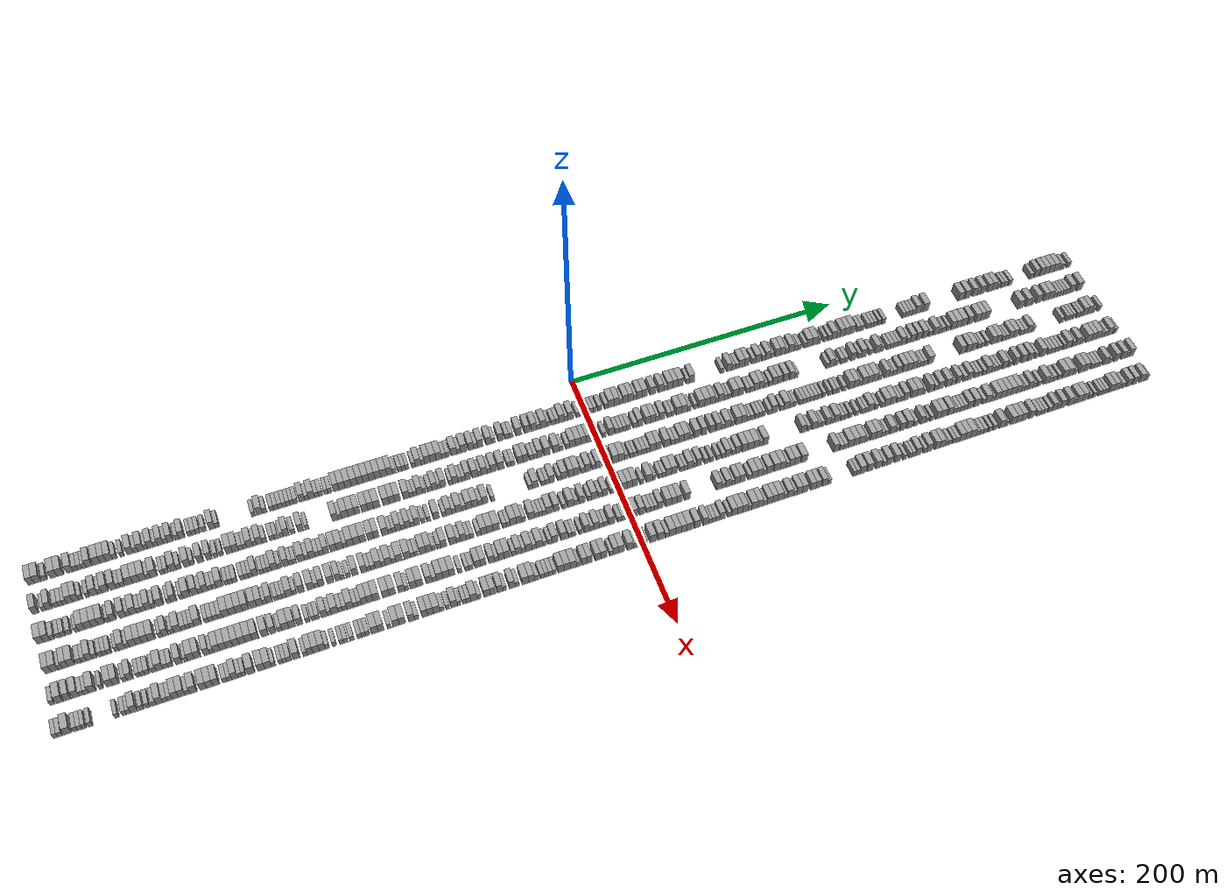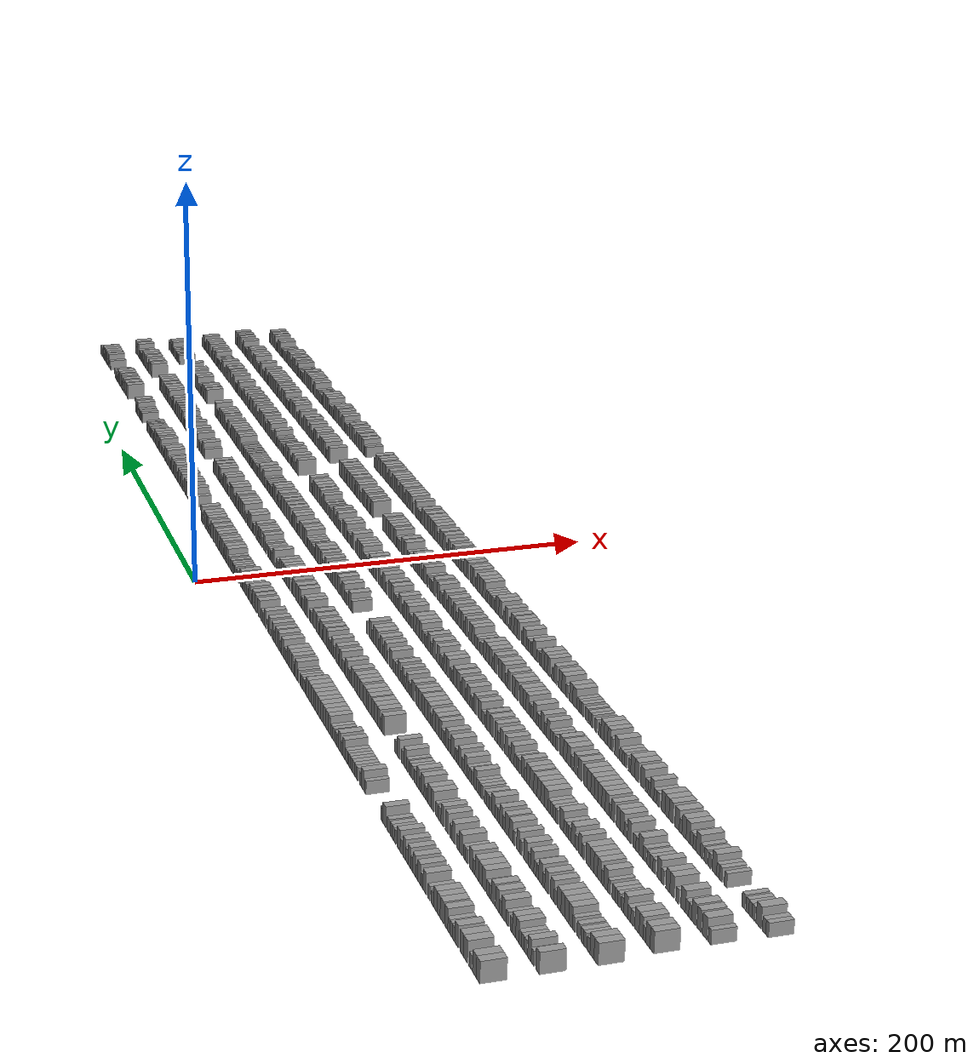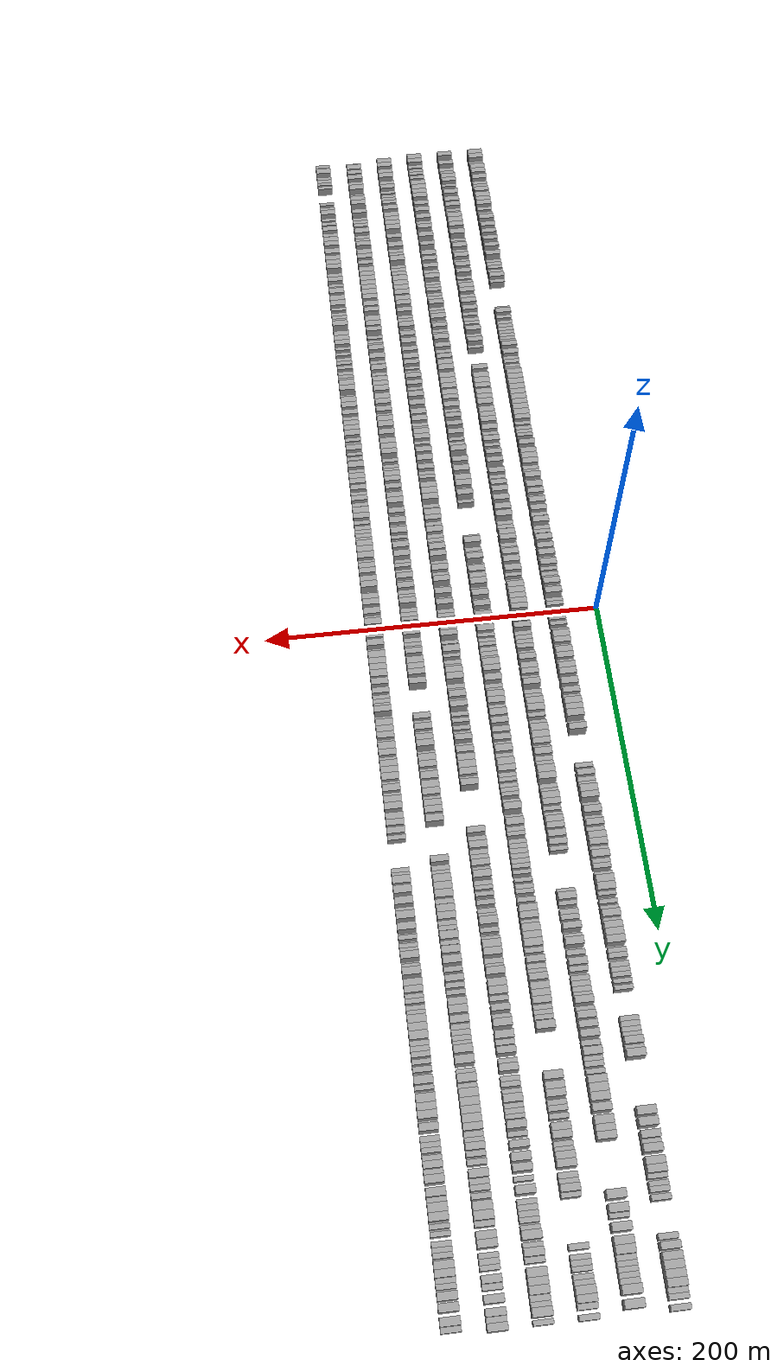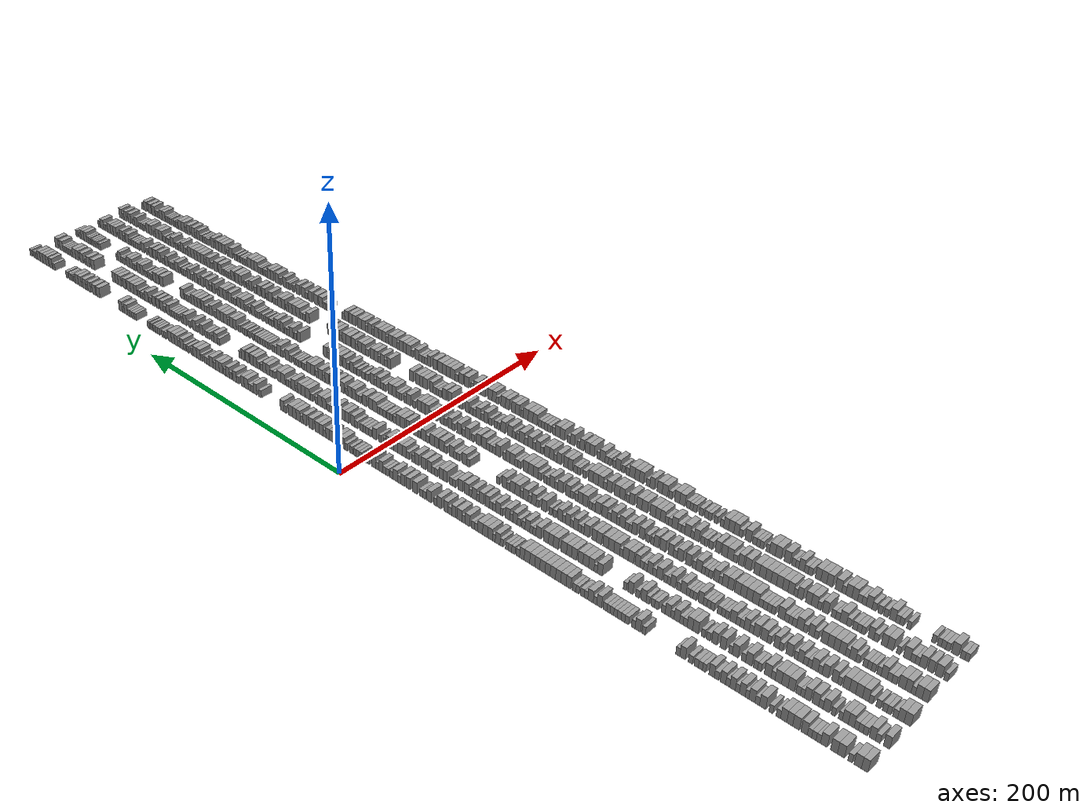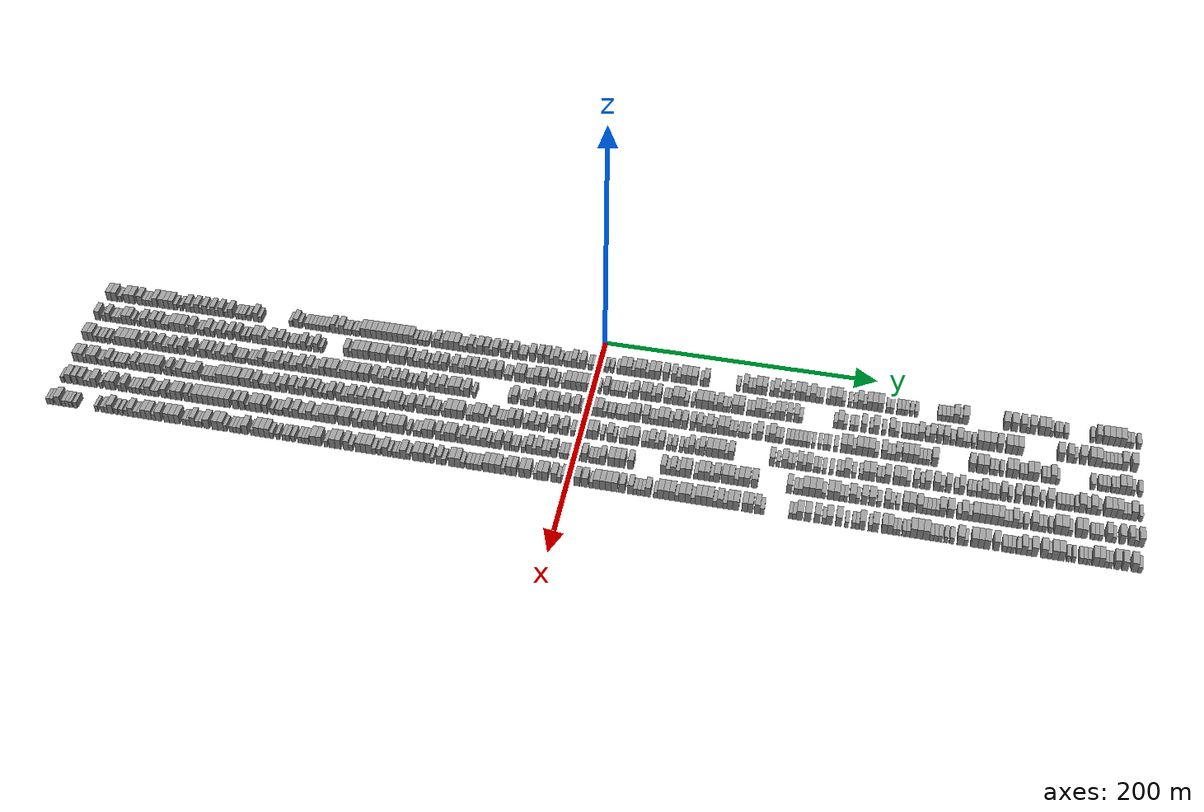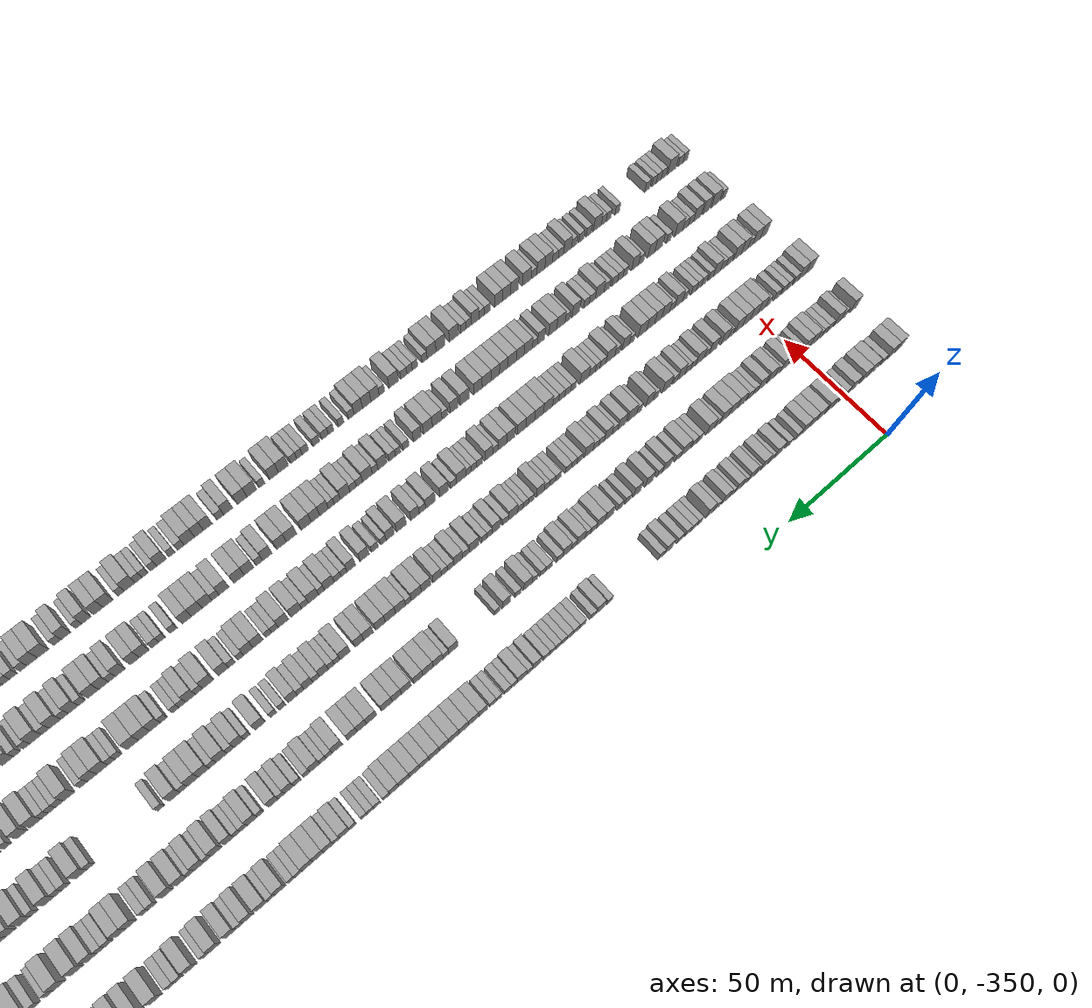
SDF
<sdf version="1.6">
 <world name="default">
  <scene>
   <sky><clouds><speed>12</speed></clouds></sky>
   <ambient>0.4 0.4 0.4 1</ambient>
   <background>0.7 0.7 0.7 1</background>
   <shadows>1</shadows>
  </scene>
  <gravity>0 0 -9.8066</gravity>
  <magnetic_field>6e-06 2.3e-05 -4.2e-05</magnetic_field>
  <physics default="0" name="default_physics" type="ode">
   <ode>
    <solver>
     <type>quick</type>
     <iters>10</iters>
     <sor>1.0</sor>
     <use_dynamic_moi_rescaling>0</use_dynamic_moi_rescaling>
    </solver>
    <constraints>
     <cfm>0</cfm>
     <erp>0.2</erp>
     <contact_max_correcting_vel>100</contact_max_correcting_vel>
     <contact_surface_layer>0.001</contact_surface_layer>
    </constraints>
   </ode>
   <max_step_size>0.004</max_step_size>
   <real_time_factor>1</real_time_factor>
   <real_time_update_rate>250</real_time_update_rate>
  </physics>
  <light name="sun" type="directional">
   <pose>0 0 10 0 0 0</pose>
   <diffuse>0.8 0.8 0.8 1</diffuse>
   <specular>0.2 0.2 0.2 1</specular>
   <attenuation>
    <range>1000</range>
    <constant>0.9</constant>
    <linear>0.01</linear>
    <quadratic>0.001</quadratic>
   </attenuation>
   <direction>-0.5 0.1 -0.9</direction>
  </light>
  <model name="building_1">
   <static>1</static>
   <pose>25.0000 -378.0547 0 0.000000 0.000000 0.000000</pose>
   <link name="link">
    <pose>0 0 4.50 0 0 0</pose>
    <collision name="collision"><geometry><box><size>10.0000 3.8905 9.0000</size></box></geometry></collision>
    <visual name="visual">
     <cast_shadows>0</cast_shadows>
     <geometry><box><size>10.0000 3.8905 9.0000</size></box></geometry>
     <material>
      <script>
       <uri>model://grey_wall/materials/scripts</uri>
       <uri>model://grey_wall/materials/textures</uri>
       <name>vrc/grey_wall</name>
      </script>
     </material>
    </visual>
   </link>
  </model>
  <model name="building_2">
   <static>1</static>
   <pose>25.0000 -373.9327 0 0.000000 0.000000 0.000000</pose>
   <link name="link">
    <pose>0 0 4.50 0 0 0</pose>
    <collision name="collision"><geometry><box><size>10.0000 4.3536 9.0000</size></box></geometry></collision>
    <visual name="visual">
     <cast_shadows>0</cast_shadows>
     <geometry><box><size>10.0000 4.3536 9.0000</size></box></geometry>
     <material>
      <script>
       <uri>model://grey_wall/materials/scripts</uri>
       <uri>model://grey_wall/materials/textures</uri>
       <name>vrc/grey_wall</name>
      </script>
     </material>
    </visual>
   </link>
  </model>
  <model name="building_3">
   <static>1</static>
   <pose>25.0000 -369.3601 0 0.000000 0.000000 0.000000</pose>
   <link name="link">
    <pose>0 0 3.00 0 0 0</pose>
    <collision name="collision"><geometry><box><size>10.0000 2.7915 6.0000</size></box></geometry></collision>
    <visual name="visual">
     <cast_shadows>0</cast_shadows>
     <geometry><box><size>10.0000 2.7915 6.0000</size></box></geometry>
     <material>
      <script>
       <uri>model://grey_wall/materials/scripts</uri>
       <uri>model://grey_wall/materials/textures</uri>
       <name>vrc/grey_wall</name>
      </script>
     </material>
    </visual>
   </link>
  </model>
  <model name="building_4">
   <static>1</static>
   <pose>25.0000 -363.8232 0 0.000000 0.000000 0.000000</pose>
   <link name="link">
    <pose>0 0 4.50 0 0 0</pose>
    <collision name="collision"><geometry><box><size>10.0000 4.2824 9.0000</size></box></geometry></collision>
    <visual name="visual">
     <cast_shadows>0</cast_shadows>
     <geometry><box><size>10.0000 4.2824 9.0000</size></box></geometry>
     <material>
      <script>
       <uri>model://grey_wall/materials/scripts</uri>
       <uri>model://grey_wall/materials/textures</uri>
       <name>vrc/grey_wall</name>
      </script>
     </material>
    </visual>
   </link>
  </model>
  <model name="building_5">
   <static>1</static>
   <pose>25.0000 -359.5951 0 0.000000 0.000000 0.000000</pose>
   <link name="link">
    <pose>0 0 4.50 0 0 0</pose>
    <collision name="collision"><geometry><box><size>10.0000 4.1738 9.0000</size></box></geometry></collision>
    <visual name="visual">
     <cast_shadows>0</cast_shadows>
     <geometry><box><size>10.0000 4.1738 9.0000</size></box></geometry>
     <material>
      <script>
       <uri>model://grey_wall/materials/scripts</uri>
       <uri>model://grey_wall/materials/textures</uri>
       <name>vrc/grey_wall</name>
      </script>
     </material>
    </visual>
   </link>
  </model>
  <model name="building_6">
   <static>1</static>
   <pose>25.0000 -353.4321 0 0.000000 0.000000 0.000000</pose>
   <link name="link">
    <pose>0 0 4.50 0 0 0</pose>
    <collision name="collision"><geometry><box><size>10.0000 4.1521 9.0000</size></box></geometry></collision>
    <visual name="visual">
     <cast_shadows>0</cast_shadows>
     <geometry><box><size>10.0000 4.1521 9.0000</size></box></geometry>
     <material>
      <script>
       <uri>model://grey_wall/materials/scripts</uri>
       <uri>model://grey_wall/materials/textures</uri>
       <name>vrc/grey_wall</name>
      </script>
     </material>
    </visual>
   </link>
  </model>
  <model name="building_7">
   <static>1</static>
   <pose>25.0000 -349.9801 0 0.000000 0.000000 0.000000</pose>
   <link name="link">
    <pose>0 0 3.00 0 0 0</pose>
    <collision name="collision"><geometry><box><size>10.0000 2.7519 6.0000</size></box></geometry></collision>
    <visual name="visual">
     <cast_shadows>0</cast_shadows>
     <geometry><box><size>10.0000 2.7519 6.0000</size></box></geometry>
     <material>
      <script>
       <uri>model://grey_wall/materials/scripts</uri>
       <uri>model://grey_wall/materials/textures</uri>
       <name>vrc/grey_wall</name>
      </script>
     </material>
    </visual>
   </link>
  </model>
  <model name="building_8">
   <static>1</static>
   <pose>25.0000 -347.2312 0 0.000000 0.000000 0.000000</pose>
   <link name="link">
    <pose>0 0 3.00 0 0 0</pose>
    <collision name="collision"><geometry><box><size>10.0000 2.7460 6.0000</size></box></geometry></collision>
    <visual name="visual">
     <cast_shadows>0</cast_shadows>
     <geometry><box><size>10.0000 2.7460 6.0000</size></box></geometry>
     <material>
      <script>
       <uri>model://grey_wall/materials/scripts</uri>
       <uri>model://grey_wall/materials/textures</uri>
       <name>vrc/grey_wall</name>
      </script>
     </material>
    </visual>
   </link>
  </model>
  <model name="building_9">
   <static>1</static>
   <pose>25.0000 -344.5297 0 0.000000 0.000000 0.000000</pose>
   <link name="link">
    <pose>0 0 3.00 0 0 0</pose>
    <collision name="collision"><geometry><box><size>10.0000 2.6570 6.0000</size></box></geometry></collision>
    <visual name="visual">
     <cast_shadows>0</cast_shadows>
     <geometry><box><size>10.0000 2.6570 6.0000</size></box></geometry>
     <material>
      <script>
       <uri>model://grey_wall/materials/scripts</uri>
       <uri>model://grey_wall/materials/textures</uri>
       <name>vrc/grey_wall</name>
      </script>
     </material>
    </visual>
   </link>
  </model>
  <model name="building_10">
   <static>1</static>
   <pose>25.0000 -341.2466 0 0.000000 0.000000 0.000000</pose>
   <link name="link">
    <pose>0 0 4.50 0 0 0</pose>
    <collision name="collision"><geometry><box><size>10.0000 3.9091 9.0000</size></box></geometry></collision>
    <visual name="visual">
     <cast_shadows>0</cast_shadows>
     <geometry><box><size>10.0000 3.9091 9.0000</size></box></geometry>
     <material>
      <script>
       <uri>model://grey_wall/materials/scripts</uri>
       <uri>model://grey_wall/materials/textures</uri>
       <name>vrc/grey_wall</name>
      </script>
     </material>
    </visual>
   </link>
  </model>
  <model name="building_11">
   <static>1</static>
   <pose>25.0000 -336.1313 0 0.000000 0.000000 0.000000</pose>
   <link name="link">
    <pose>0 0 4.50 0 0 0</pose>
    <collision name="collision"><geometry><box><size>10.0000 4.3216 9.0000</size></box></geometry></collision>
    <visual name="visual">
     <cast_shadows>0</cast_shadows>
     <geometry><box><size>10.0000 4.3216 9.0000</size></box></geometry>
     <material>
      <script>
       <uri>model://grey_wall/materials/scripts</uri>
       <uri>model://grey_wall/materials/textures</uri>
       <name>vrc/grey_wall</name>
      </script>
     </material>
    </visual>
   </link>
  </model>
  <model name="building_12">
   <static>1</static>
   <pose>25.0000 -332.1135 0 0.000000 0.000000 0.000000</pose>
   <link name="link">
    <pose>0 0 4.50 0 0 0</pose>
    <collision name="collision"><geometry><box><size>10.0000 3.7140 9.0000</size></box></geometry></collision>
    <visual name="visual">
     <cast_shadows>0</cast_shadows>
     <geometry><box><size>10.0000 3.7140 9.0000</size></box></geometry>
     <material>
      <script>
       <uri>model://grey_wall/materials/scripts</uri>
       <uri>model://grey_wall/materials/textures</uri>
       <name>vrc/grey_wall</name>
      </script>
     </material>
    </visual>
   </link>
  </model>
  <model name="building_13">
   <static>1</static>
   <pose>25.0000 -328.2642 0 0.000000 0.000000 0.000000</pose>
   <link name="link">
    <pose>0 0 4.50 0 0 0</pose>
    <collision name="collision"><geometry><box><size>10.0000 3.9845 9.0000</size></box></geometry></collision>
    <visual name="visual">
     <cast_shadows>0</cast_shadows>
     <geometry><box><size>10.0000 3.9845 9.0000</size></box></geometry>
     <material>
      <script>
       <uri>model://grey_wall/materials/scripts</uri>
       <uri>model://grey_wall/materials/textures</uri>
       <name>vrc/grey_wall</name>
      </script>
     </material>
    </visual>
   </link>
  </model>
  <model name="building_14">
   <static>1</static>
   <pose>25.0000 -324.8648 0 0.000000 0.000000 0.000000</pose>
   <link name="link">
    <pose>0 0 3.00 0 0 0</pose>
    <collision name="collision"><geometry><box><size>10.0000 2.8144 6.0000</size></box></geometry></collision>
    <visual name="visual">
     <cast_shadows>0</cast_shadows>
     <geometry><box><size>10.0000 2.8144 6.0000</size></box></geometry>
     <material>
      <script>
       <uri>model://grey_wall/materials/scripts</uri>
       <uri>model://grey_wall/materials/textures</uri>
       <name>vrc/grey_wall</name>
      </script>
     </material>
    </visual>
   </link>
  </model>
  <model name="building_15">
   <static>1</static>
   <pose>25.0000 -320.1653 0 0.000000 0.000000 0.000000</pose>
   <link name="link">
    <pose>0 0 3.00 0 0 0</pose>
    <collision name="collision"><geometry><box><size>10.0000 2.5846 6.0000</size></box></geometry></collision>
    <visual name="visual">
     <cast_shadows>0</cast_shadows>
     <geometry><box><size>10.0000 2.5846 6.0000</size></box></geometry>
     <material>
      <script>
       <uri>model://grey_wall/materials/scripts</uri>
       <uri>model://grey_wall/materials/textures</uri>
       <name>vrc/grey_wall</name>
      </script>
     </material>
    </visual>
   </link>
  </model>
  <model name="building_16">
   <static>1</static>
   <pose>25.0000 -314.8263 0 0.000000 0.000000 0.000000</pose>
   <link name="link">
    <pose>0 0 4.50 0 0 0</pose>
    <collision name="collision"><geometry><box><size>10.0000 4.0934 9.0000</size></box></geometry></collision>
    <visual name="visual">
     <cast_shadows>0</cast_shadows>
     <geometry><box><size>10.0000 4.0934 9.0000</size></box></geometry>
     <material>
      <script>
       <uri>model://grey_wall/materials/scripts</uri>
       <uri>model://grey_wall/materials/textures</uri>
       <name>vrc/grey_wall</name>
      </script>
     </material>
    </visual>
   </link>
  </model>
  <model name="building_17">
   <static>1</static>
   <pose>25.0000 -311.3270 0 0.000000 0.000000 0.000000</pose>
   <link name="link">
    <pose>0 0 3.00 0 0 0</pose>
    <collision name="collision"><geometry><box><size>10.0000 2.9054 6.0000</size></box></geometry></collision>
    <visual name="visual">
     <cast_shadows>0</cast_shadows>
     <geometry><box><size>10.0000 2.9054 6.0000</size></box></geometry>
     <material>
      <script>
       <uri>model://grey_wall/materials/scripts</uri>
       <uri>model://grey_wall/materials/textures</uri>
       <name>vrc/grey_wall</name>
      </script>
     </material>
    </visual>
   </link>
  </model>
  <model name="building_18">
   <static>1</static>
   <pose>25.0000 -307.8959 0 0.000000 0.000000 0.000000</pose>
   <link name="link">
    <pose>0 0 4.50 0 0 0</pose>
    <collision name="collision"><geometry><box><size>10.0000 3.9567 9.0000</size></box></geometry></collision>
    <visual name="visual">
     <cast_shadows>0</cast_shadows>
     <geometry><box><size>10.0000 3.9567 9.0000</size></box></geometry>
     <material>
      <script>
       <uri>model://grey_wall/materials/scripts</uri>
       <uri>model://grey_wall/materials/textures</uri>
       <name>vrc/grey_wall</name>
      </script>
     </material>
    </visual>
   </link>
  </model>
  <model name="building_19">
   <static>1</static>
   <pose>25.0000 -304.6905 0 0.000000 0.000000 0.000000</pose>
   <link name="link">
    <pose>0 0 3.00 0 0 0</pose>
    <collision name="collision"><geometry><box><size>10.0000 2.4542 6.0000</size></box></geometry></collision>
    <visual name="visual">
     <cast_shadows>0</cast_shadows>
     <geometry><box><size>10.0000 2.4542 6.0000</size></box></geometry>
     <material>
      <script>
       <uri>model://grey_wall/materials/scripts</uri>
       <uri>model://grey_wall/materials/textures</uri>
       <name>vrc/grey_wall</name>
      </script>
     </material>
    </visual>
   </link>
  </model>
  <model name="building_20">
   <static>1</static>
   <pose>25.0000 -301.5660 0 0.000000 0.000000 0.000000</pose>
   <link name="link">
    <pose>0 0 4.50 0 0 0</pose>
    <collision name="collision"><geometry><box><size>10.0000 3.7947 9.0000</size></box></geometry></collision>
    <visual name="visual">
     <cast_shadows>0</cast_shadows>
     <geometry><box><size>10.0000 3.7947 9.0000</size></box></geometry>
     <material>
      <script>
       <uri>model://grey_wall/materials/scripts</uri>
       <uri>model://grey_wall/materials/textures</uri>
       <name>vrc/grey_wall</name>
      </script>
     </material>
    </visual>
   </link>
  </model>
  <model name="building_21">
   <static>1</static>
   <pose>25.0000 -298.3060 0 0.000000 0.000000 0.000000</pose>
   <link name="link">
    <pose>0 0 3.00 0 0 0</pose>
    <collision name="collision"><geometry><box><size>10.0000 2.7253 6.0000</size></box></geometry></collision>
    <visual name="visual">
     <cast_shadows>0</cast_shadows>
     <geometry><box><size>10.0000 2.7253 6.0000</size></box></geometry>
     <material>
      <script>
       <uri>model://grey_wall/materials/scripts</uri>
       <uri>model://grey_wall/materials/textures</uri>
       <name>vrc/grey_wall</name>
      </script>
     </material>
    </visual>
   </link>
  </model>
  <model name="building_22">
   <static>1</static>
   <pose>25.0000 -295.1151 0 0.000000 0.000000 0.000000</pose>
   <link name="link">
    <pose>0 0 4.50 0 0 0</pose>
    <collision name="collision"><geometry><box><size>10.0000 3.6565 9.0000</size></box></geometry></collision>
    <visual name="visual">
     <cast_shadows>0</cast_shadows>
     <geometry><box><size>10.0000 3.6565 9.0000</size></box></geometry>
     <material>
      <script>
       <uri>model://grey_wall/materials/scripts</uri>
       <uri>model://grey_wall/materials/textures</uri>
       <name>vrc/grey_wall</name>
      </script>
     </material>
    </visual>
   </link>
  </model>
  <model name="building_23">
   <static>1</static>
   <pose>25.0000 -291.8948 0 0.000000 0.000000 0.000000</pose>
   <link name="link">
    <pose>0 0 3.00 0 0 0</pose>
    <collision name="collision"><geometry><box><size>10.0000 2.7841 6.0000</size></box></geometry></collision>
    <visual name="visual">
     <cast_shadows>0</cast_shadows>
     <geometry><box><size>10.0000 2.7841 6.0000</size></box></geometry>
     <material>
      <script>
       <uri>model://grey_wall/materials/scripts</uri>
       <uri>model://grey_wall/materials/textures</uri>
       <name>vrc/grey_wall</name>
      </script>
     </material>
    </visual>
   </link>
  </model>
  <model name="building_24">
   <static>1</static>
   <pose>25.0000 -288.6944 0 0.000000 0.000000 0.000000</pose>
   <link name="link">
    <pose>0 0 4.50 0 0 0</pose>
    <collision name="collision"><geometry><box><size>10.0000 3.6165 9.0000</size></box></geometry></collision>
    <visual name="visual">
     <cast_shadows>0</cast_shadows>
     <geometry><box><size>10.0000 3.6165 9.0000</size></box></geometry>
     <material>
      <script>
       <uri>model://grey_wall/materials/scripts</uri>
       <uri>model://grey_wall/materials/textures</uri>
       <name>vrc/grey_wall</name>
      </script>
     </material>
    </visual>
   </link>
  </model>
  <model name="building_25">
   <static>1</static>
   <pose>25.0000 -284.4066 0 0.000000 0.000000 0.000000</pose>
   <link name="link">
    <pose>0 0 3.00 0 0 0</pose>
    <collision name="collision"><geometry><box><size>10.0000 2.9592 6.0000</size></box></geometry></collision>
    <visual name="visual">
     <cast_shadows>0</cast_shadows>
     <geometry><box><size>10.0000 2.9592 6.0000</size></box></geometry>
     <material>
      <script>
       <uri>model://grey_wall/materials/scripts</uri>
       <uri>model://grey_wall/materials/textures</uri>
       <name>vrc/grey_wall</name>
      </script>
     </material>
    </visual>
   </link>
  </model>
  <model name="building_26">
   <static>1</static>
   <pose>25.0000 -281.0877 0 0.000000 0.000000 0.000000</pose>
   <link name="link">
    <pose>0 0 4.50 0 0 0</pose>
    <collision name="collision"><geometry><box><size>10.0000 3.6786 9.0000</size></box></geometry></collision>
    <visual name="visual">
     <cast_shadows>0</cast_shadows>
     <geometry><box><size>10.0000 3.6786 9.0000</size></box></geometry>
     <material>
      <script>
       <uri>model://grey_wall/materials/scripts</uri>
       <uri>model://grey_wall/materials/textures</uri>
       <name>vrc/grey_wall</name>
      </script>
     </material>
    </visual>
   </link>
  </model>
  <model name="building_27">
   <static>1</static>
   <pose>25.0000 -276.0480 0 0.000000 0.000000 0.000000</pose>
   <link name="link">
    <pose>0 0 3.00 0 0 0</pose>
    <collision name="collision"><geometry><box><size>10.0000 2.4007 6.0000</size></box></geometry></collision>
    <visual name="visual">
     <cast_shadows>0</cast_shadows>
     <geometry><box><size>10.0000 2.4007 6.0000</size></box></geometry>
     <material>
      <script>
       <uri>model://grey_wall/materials/scripts</uri>
       <uri>model://grey_wall/materials/textures</uri>
       <name>vrc/grey_wall</name>
      </script>
     </material>
    </visual>
   </link>
  </model>
  <model name="building_28">
   <static>1</static>
   <pose>25.0000 -273.4264 0 0.000000 0.000000 0.000000</pose>
   <link name="link">
    <pose>0 0 3.00 0 0 0</pose>
    <collision name="collision"><geometry><box><size>10.0000 2.8424 6.0000</size></box></geometry></collision>
    <visual name="visual">
     <cast_shadows>0</cast_shadows>
     <geometry><box><size>10.0000 2.8424 6.0000</size></box></geometry>
     <material>
      <script>
       <uri>model://grey_wall/materials/scripts</uri>
       <uri>model://grey_wall/materials/textures</uri>
       <name>vrc/grey_wall</name>
      </script>
     </material>
    </visual>
   </link>
  </model>
  <model name="building_29">
   <static>1</static>
   <pose>25.0000 -270.5645 0 0.000000 0.000000 0.000000</pose>
   <link name="link">
    <pose>0 0 3.00 0 0 0</pose>
    <collision name="collision"><geometry><box><size>10.0000 2.8814 6.0000</size></box></geometry></collision>
    <visual name="visual">
     <cast_shadows>0</cast_shadows>
     <geometry><box><size>10.0000 2.8814 6.0000</size></box></geometry>
     <material>
      <script>
       <uri>model://grey_wall/materials/scripts</uri>
       <uri>model://grey_wall/materials/textures</uri>
       <name>vrc/grey_wall</name>
      </script>
     </material>
    </visual>
   </link>
  </model>
  <model name="building_30">
   <static>1</static>
   <pose>25.0000 -266.6533 0 0.000000 0.000000 0.000000</pose>
   <link name="link">
    <pose>0 0 3.00 0 0 0</pose>
    <collision name="collision"><geometry><box><size>10.0000 2.9410 6.0000</size></box></geometry></collision>
    <visual name="visual">
     <cast_shadows>0</cast_shadows>
     <geometry><box><size>10.0000 2.9410 6.0000</size></box></geometry>
     <material>
      <script>
       <uri>model://grey_wall/materials/scripts</uri>
       <uri>model://grey_wall/materials/textures</uri>
       <name>vrc/grey_wall</name>
      </script>
     </material>
    </visual>
   </link>
  </model>
  <model name="building_31">
   <static>1</static>
   <pose>25.0000 -261.2503 0 0.000000 0.000000 0.000000</pose>
   <link name="link">
    <pose>0 0 4.50 0 0 0</pose>
    <collision name="collision"><geometry><box><size>10.0000 3.8649 9.0000</size></box></geometry></collision>
    <visual name="visual">
     <cast_shadows>0</cast_shadows>
     <geometry><box><size>10.0000 3.8649 9.0000</size></box></geometry>
     <material>
      <script>
       <uri>model://grey_wall/materials/scripts</uri>
       <uri>model://grey_wall/materials/textures</uri>
       <name>vrc/grey_wall</name>
      </script>
     </material>
    </visual>
   </link>
  </model>
  <model name="building_32">
   <static>1</static>
   <pose>25.0000 -257.8814 0 0.000000 0.000000 0.000000</pose>
   <link name="link">
    <pose>0 0 3.00 0 0 0</pose>
    <collision name="collision"><geometry><box><size>10.0000 2.8729 6.0000</size></box></geometry></collision>
    <visual name="visual">
     <cast_shadows>0</cast_shadows>
     <geometry><box><size>10.0000 2.8729 6.0000</size></box></geometry>
     <material>
      <script>
       <uri>model://grey_wall/materials/scripts</uri>
       <uri>model://grey_wall/materials/textures</uri>
       <name>vrc/grey_wall</name>
      </script>
     </material>
    </visual>
   </link>
  </model>
  <model name="building_33">
   <static>1</static>
   <pose>25.0000 -233.6881 0 0.000000 0.000000 0.000000</pose>
   <link name="link">
    <pose>0 0 3.00 0 0 0</pose>
    <collision name="collision"><geometry><box><size>10.0000 2.5045 6.0000</size></box></geometry></collision>
    <visual name="visual">
     <cast_shadows>0</cast_shadows>
     <geometry><box><size>10.0000 2.5045 6.0000</size></box></geometry>
     <material>
      <script>
       <uri>model://grey_wall/materials/scripts</uri>
       <uri>model://grey_wall/materials/textures</uri>
       <name>vrc/grey_wall</name>
      </script>
     </material>
    </visual>
   </link>
  </model>
  <model name="building_34">
   <static>1</static>
   <pose>25.0000 -229.4758 0 0.000000 0.000000 0.000000</pose>
   <link name="link">
    <pose>0 0 4.50 0 0 0</pose>
    <collision name="collision"><geometry><box><size>10.0000 3.9200 9.0000</size></box></geometry></collision>
    <visual name="visual">
     <cast_shadows>0</cast_shadows>
     <geometry><box><size>10.0000 3.9200 9.0000</size></box></geometry>
     <material>
      <script>
       <uri>model://grey_wall/materials/scripts</uri>
       <uri>model://grey_wall/materials/textures</uri>
       <name>vrc/grey_wall</name>
      </script>
     </material>
    </visual>
   </link>
  </model>
  <model name="building_35">
   <static>1</static>
   <pose>25.0000 -226.1707 0 0.000000 0.000000 0.000000</pose>
   <link name="link">
    <pose>0 0 3.00 0 0 0</pose>
    <collision name="collision"><geometry><box><size>10.0000 2.6901 6.0000</size></box></geometry></collision>
    <visual name="visual">
     <cast_shadows>0</cast_shadows>
     <geometry><box><size>10.0000 2.6901 6.0000</size></box></geometry>
     <material>
      <script>
       <uri>model://grey_wall/materials/scripts</uri>
       <uri>model://grey_wall/materials/textures</uri>
       <name>vrc/grey_wall</name>
      </script>
     </material>
    </visual>
   </link>
  </model>
  <model name="building_36">
   <static>1</static>
   <pose>25.0000 -221.4055 0 0.000000 0.000000 0.000000</pose>
   <link name="link">
    <pose>0 0 3.00 0 0 0</pose>
    <collision name="collision"><geometry><box><size>10.0000 2.8403 6.0000</size></box></geometry></collision>
    <visual name="visual">
     <cast_shadows>0</cast_shadows>
     <geometry><box><size>10.0000 2.8403 6.0000</size></box></geometry>
     <material>
      <script>
       <uri>model://grey_wall/materials/scripts</uri>
       <uri>model://grey_wall/materials/textures</uri>
       <name>vrc/grey_wall</name>
      </script>
     </material>
    </visual>
   </link>
  </model>
  <model name="building_37">
   <static>1</static>
   <pose>25.0000 -218.5727 0 0.000000 0.000000 0.000000</pose>
   <link name="link">
    <pose>0 0 3.00 0 0 0</pose>
    <collision name="collision"><geometry><box><size>10.0000 2.8253 6.0000</size></box></geometry></collision>
    <visual name="visual">
     <cast_shadows>0</cast_shadows>
     <geometry><box><size>10.0000 2.8253 6.0000</size></box></geometry>
     <material>
      <script>
       <uri>model://grey_wall/materials/scripts</uri>
       <uri>model://grey_wall/materials/textures</uri>
       <name>vrc/grey_wall</name>
      </script>
     </material>
    </visual>
   </link>
  </model>
  <model name="building_38">
   <static>1</static>
   <pose>25.0000 -215.7365 0 0.000000 0.000000 0.000000</pose>
   <link name="link">
    <pose>0 0 3.00 0 0 0</pose>
    <collision name="collision"><geometry><box><size>10.0000 2.8472 6.0000</size></box></geometry></collision>
    <visual name="visual">
     <cast_shadows>0</cast_shadows>
     <geometry><box><size>10.0000 2.8472 6.0000</size></box></geometry>
     <material>
      <script>
       <uri>model://grey_wall/materials/scripts</uri>
       <uri>model://grey_wall/materials/textures</uri>
       <name>vrc/grey_wall</name>
      </script>
     </material>
    </visual>
   </link>
  </model>
  <model name="building_39">
   <static>1</static>
   <pose>25.0000 -213.0201 0 0.000000 0.000000 0.000000</pose>
   <link name="link">
    <pose>0 0 3.00 0 0 0</pose>
    <collision name="collision"><geometry><box><size>10.0000 2.5855 6.0000</size></box></geometry></collision>
    <visual name="visual">
     <cast_shadows>0</cast_shadows>
     <geometry><box><size>10.0000 2.5855 6.0000</size></box></geometry>
     <material>
      <script>
       <uri>model://grey_wall/materials/scripts</uri>
       <uri>model://grey_wall/materials/textures</uri>
       <name>vrc/grey_wall</name>
      </script>
     </material>
    </visual>
   </link>
  </model>
  <model name="building_40">
   <static>1</static>
   <pose>25.0000 -210.4292 0 0.000000 0.000000 0.000000</pose>
   <link name="link">
    <pose>0 0 3.00 0 0 0</pose>
    <collision name="collision"><geometry><box><size>10.0000 2.5962 6.0000</size></box></geometry></collision>
    <visual name="visual">
     <cast_shadows>0</cast_shadows>
     <geometry><box><size>10.0000 2.5962 6.0000</size></box></geometry>
     <material>
      <script>
       <uri>model://grey_wall/materials/scripts</uri>
       <uri>model://grey_wall/materials/textures</uri>
       <name>vrc/grey_wall</name>
      </script>
     </material>
    </visual>
   </link>
  </model>
  <model name="building_41">
   <static>1</static>
   <pose>25.0000 -207.9044 0 0.000000 0.000000 0.000000</pose>
   <link name="link">
    <pose>0 0 3.00 0 0 0</pose>
    <collision name="collision"><geometry><box><size>10.0000 2.4534 6.0000</size></box></geometry></collision>
    <visual name="visual">
     <cast_shadows>0</cast_shadows>
     <geometry><box><size>10.0000 2.4534 6.0000</size></box></geometry>
     <material>
      <script>
       <uri>model://grey_wall/materials/scripts</uri>
       <uri>model://grey_wall/materials/textures</uri>
       <name>vrc/grey_wall</name>
      </script>
     </material>
    </visual>
   </link>
  </model>
  <model name="building_42">
   <static>1</static>
   <pose>25.0000 -205.2205 0 0.000000 0.000000 0.000000</pose>
   <link name="link">
    <pose>0 0 3.00 0 0 0</pose>
    <collision name="collision"><geometry><box><size>10.0000 2.9143 6.0000</size></box></geometry></collision>
    <visual name="visual">
     <cast_shadows>0</cast_shadows>
     <geometry><box><size>10.0000 2.9143 6.0000</size></box></geometry>
     <material>
      <script>
       <uri>model://grey_wall/materials/scripts</uri>
       <uri>model://grey_wall/materials/textures</uri>
       <name>vrc/grey_wall</name>
      </script>
     </material>
    </visual>
   </link>
  </model>
  <model name="building_43">
   <static>1</static>
   <pose>25.0000 -200.9408 0 0.000000 0.000000 0.000000</pose>
   <link name="link">
    <pose>0 0 4.50 0 0 0</pose>
    <collision name="collision"><geometry><box><size>10.0000 3.6453 9.0000</size></box></geometry></collision>
    <visual name="visual">
     <cast_shadows>0</cast_shadows>
     <geometry><box><size>10.0000 3.6453 9.0000</size></box></geometry>
     <material>
      <script>
       <uri>model://grey_wall/materials/scripts</uri>
       <uri>model://grey_wall/materials/textures</uri>
       <name>vrc/grey_wall</name>
      </script>
     </material>
    </visual>
   </link>
  </model>
  <model name="building_44">
   <static>1</static>
   <pose>25.0000 -197.7806 0 0.000000 0.000000 0.000000</pose>
   <link name="link">
    <pose>0 0 3.00 0 0 0</pose>
    <collision name="collision"><geometry><box><size>10.0000 2.6750 6.0000</size></box></geometry></collision>
    <visual name="visual">
     <cast_shadows>0</cast_shadows>
     <geometry><box><size>10.0000 2.6750 6.0000</size></box></geometry>
     <material>
      <script>
       <uri>model://grey_wall/materials/scripts</uri>
       <uri>model://grey_wall/materials/textures</uri>
       <name>vrc/grey_wall</name>
      </script>
     </material>
    </visual>
   </link>
  </model>
  <model name="building_45">
   <static>1</static>
   <pose>25.0000 -194.4155 0 0.000000 0.000000 0.000000</pose>
   <link name="link">
    <pose>0 0 4.50 0 0 0</pose>
    <collision name="collision"><geometry><box><size>10.0000 4.0553 9.0000</size></box></geometry></collision>
    <visual name="visual">
     <cast_shadows>0</cast_shadows>
     <geometry><box><size>10.0000 4.0553 9.0000</size></box></geometry>
     <material>
      <script>
       <uri>model://grey_wall/materials/scripts</uri>
       <uri>model://grey_wall/materials/textures</uri>
       <name>vrc/grey_wall</name>
      </script>
     </material>
    </visual>
   </link>
  </model>
  <model name="building_46">
   <static>1</static>
   <pose>25.0000 -191.0507 0 0.000000 0.000000 0.000000</pose>
   <link name="link">
    <pose>0 0 3.00 0 0 0</pose>
    <collision name="collision"><geometry><box><size>10.0000 2.6742 6.0000</size></box></geometry></collision>
    <visual name="visual">
     <cast_shadows>0</cast_shadows>
     <geometry><box><size>10.0000 2.6742 6.0000</size></box></geometry>
     <material>
      <script>
       <uri>model://grey_wall/materials/scripts</uri>
       <uri>model://grey_wall/materials/textures</uri>
       <name>vrc/grey_wall</name>
      </script>
     </material>
    </visual>
   </link>
  </model>
  <model name="building_47">
   <static>1</static>
   <pose>25.0000 -188.2467 0 0.000000 0.000000 0.000000</pose>
   <link name="link">
    <pose>0 0 3.00 0 0 0</pose>
    <collision name="collision"><geometry><box><size>10.0000 2.9339 6.0000</size></box></geometry></collision>
    <visual name="visual">
     <cast_shadows>0</cast_shadows>
     <geometry><box><size>10.0000 2.9339 6.0000</size></box></geometry>
     <material>
      <script>
       <uri>model://grey_wall/materials/scripts</uri>
       <uri>model://grey_wall/materials/textures</uri>
       <name>vrc/grey_wall</name>
      </script>
     </material>
    </visual>
   </link>
  </model>
  <model name="building_48">
   <static>1</static>
   <pose>25.0000 -184.5239 0 0.000000 0.000000 0.000000</pose>
   <link name="link">
    <pose>0 0 3.00 0 0 0</pose>
    <collision name="collision"><geometry><box><size>10.0000 2.5118 6.0000</size></box></geometry></collision>
    <visual name="visual">
     <cast_shadows>0</cast_shadows>
     <geometry><box><size>10.0000 2.5118 6.0000</size></box></geometry>
     <material>
      <script>
       <uri>model://grey_wall/materials/scripts</uri>
       <uri>model://grey_wall/materials/textures</uri>
       <name>vrc/grey_wall</name>
      </script>
     </material>
    </visual>
   </link>
  </model>
  <model name="building_49">
   <static>1</static>
   <pose>25.0000 -181.8767 0 0.000000 0.000000 0.000000</pose>
   <link name="link">
    <pose>0 0 3.00 0 0 0</pose>
    <collision name="collision"><geometry><box><size>10.0000 2.7826 6.0000</size></box></geometry></collision>
    <visual name="visual">
     <cast_shadows>0</cast_shadows>
     <geometry><box><size>10.0000 2.7826 6.0000</size></box></geometry>
     <material>
      <script>
       <uri>model://grey_wall/materials/scripts</uri>
       <uri>model://grey_wall/materials/textures</uri>
       <name>vrc/grey_wall</name>
      </script>
     </material>
    </visual>
   </link>
  </model>
  <model name="building_50">
   <static>1</static>
   <pose>25.0000 -177.6072 0 0.000000 0.000000 0.000000</pose>
   <link name="link">
    <pose>0 0 4.50 0 0 0</pose>
    <collision name="collision"><geometry><box><size>10.0000 3.7564 9.0000</size></box></geometry></collision>
    <visual name="visual">
     <cast_shadows>0</cast_shadows>
     <geometry><box><size>10.0000 3.7564 9.0000</size></box></geometry>
     <material>
      <script>
       <uri>model://grey_wall/materials/scripts</uri>
       <uri>model://grey_wall/materials/textures</uri>
       <name>vrc/grey_wall</name>
      </script>
     </material>
    </visual>
   </link>
  </model>
  <model name="building_51">
   <static>1</static>
   <pose>25.0000 -173.6328 0 0.000000 0.000000 0.000000</pose>
   <link name="link">
    <pose>0 0 4.50 0 0 0</pose>
    <collision name="collision"><geometry><box><size>10.0000 4.1924 9.0000</size></box></geometry></collision>
    <visual name="visual">
     <cast_shadows>0</cast_shadows>
     <geometry><box><size>10.0000 4.1924 9.0000</size></box></geometry>
     <material>
      <script>
       <uri>model://grey_wall/materials/scripts</uri>
       <uri>model://grey_wall/materials/textures</uri>
       <name>vrc/grey_wall</name>
      </script>
     </material>
    </visual>
   </link>
  </model>
  <model name="building_52">
   <static>1</static>
   <pose>25.0000 -169.4848 0 0.000000 0.000000 0.000000</pose>
   <link name="link">
    <pose>0 0 4.50 0 0 0</pose>
    <collision name="collision"><geometry><box><size>10.0000 4.1036 9.0000</size></box></geometry></collision>
    <visual name="visual">
     <cast_shadows>0</cast_shadows>
     <geometry><box><size>10.0000 4.1036 9.0000</size></box></geometry>
     <material>
      <script>
       <uri>model://grey_wall/materials/scripts</uri>
       <uri>model://grey_wall/materials/textures</uri>
       <name>vrc/grey_wall</name>
      </script>
     </material>
    </visual>
   </link>
  </model>
  <model name="building_53">
   <static>1</static>
   <pose>25.0000 -165.2913 0 0.000000 0.000000 0.000000</pose>
   <link name="link">
    <pose>0 0 4.50 0 0 0</pose>
    <collision name="collision"><geometry><box><size>10.0000 4.2834 9.0000</size></box></geometry></collision>
    <visual name="visual">
     <cast_shadows>0</cast_shadows>
     <geometry><box><size>10.0000 4.2834 9.0000</size></box></geometry>
     <material>
      <script>
       <uri>model://grey_wall/materials/scripts</uri>
       <uri>model://grey_wall/materials/textures</uri>
       <name>vrc/grey_wall</name>
      </script>
     </material>
    </visual>
   </link>
  </model>
  <model name="building_54">
   <static>1</static>
   <pose>25.0000 -161.2082 0 0.000000 0.000000 0.000000</pose>
   <link name="link">
    <pose>0 0 4.50 0 0 0</pose>
    <collision name="collision"><geometry><box><size>10.0000 3.8828 9.0000</size></box></geometry></collision>
    <visual name="visual">
     <cast_shadows>0</cast_shadows>
     <geometry><box><size>10.0000 3.8828 9.0000</size></box></geometry>
     <material>
      <script>
       <uri>model://grey_wall/materials/scripts</uri>
       <uri>model://grey_wall/materials/textures</uri>
       <name>vrc/grey_wall</name>
      </script>
     </material>
    </visual>
   </link>
  </model>
  <model name="building_55">
   <static>1</static>
   <pose>25.0000 -157.1422 0 0.000000 0.000000 0.000000</pose>
   <link name="link">
    <pose>0 0 4.50 0 0 0</pose>
    <collision name="collision"><geometry><box><size>10.0000 4.2492 9.0000</size></box></geometry></collision>
    <visual name="visual">
     <cast_shadows>0</cast_shadows>
     <geometry><box><size>10.0000 4.2492 9.0000</size></box></geometry>
     <material>
      <script>
       <uri>model://grey_wall/materials/scripts</uri>
       <uri>model://grey_wall/materials/textures</uri>
       <name>vrc/grey_wall</name>
      </script>
     </material>
    </visual>
   </link>
  </model>
  <model name="building_56">
   <static>1</static>
   <pose>25.0000 -153.0838 0 0.000000 0.000000 0.000000</pose>
   <link name="link">
    <pose>0 0 4.50 0 0 0</pose>
    <collision name="collision"><geometry><box><size>10.0000 3.8676 9.0000</size></box></geometry></collision>
    <visual name="visual">
     <cast_shadows>0</cast_shadows>
     <geometry><box><size>10.0000 3.8676 9.0000</size></box></geometry>
     <material>
      <script>
       <uri>model://grey_wall/materials/scripts</uri>
       <uri>model://grey_wall/materials/textures</uri>
       <name>vrc/grey_wall</name>
      </script>
     </material>
    </visual>
   </link>
  </model>
  <model name="building_57">
   <static>1</static>
   <pose>25.0000 -149.0592 0 0.000000 0.000000 0.000000</pose>
   <link name="link">
    <pose>0 0 4.50 0 0 0</pose>
    <collision name="collision"><geometry><box><size>10.0000 4.1815 9.0000</size></box></geometry></collision>
    <visual name="visual">
     <cast_shadows>0</cast_shadows>
     <geometry><box><size>10.0000 4.1815 9.0000</size></box></geometry>
     <material>
      <script>
       <uri>model://grey_wall/materials/scripts</uri>
       <uri>model://grey_wall/materials/textures</uri>
       <name>vrc/grey_wall</name>
      </script>
     </material>
    </visual>
   </link>
  </model>
  <model name="building_58">
   <static>1</static>
   <pose>25.0000 -144.7531 0 0.000000 0.000000 0.000000</pose>
   <link name="link">
    <pose>0 0 4.50 0 0 0</pose>
    <collision name="collision"><geometry><box><size>10.0000 4.4307 9.0000</size></box></geometry></collision>
    <visual name="visual">
     <cast_shadows>0</cast_shadows>
     <geometry><box><size>10.0000 4.4307 9.0000</size></box></geometry>
     <material>
      <script>
       <uri>model://grey_wall/materials/scripts</uri>
       <uri>model://grey_wall/materials/textures</uri>
       <name>vrc/grey_wall</name>
      </script>
     </material>
    </visual>
   </link>
  </model>
  <model name="building_59">
   <static>1</static>
   <pose>25.0000 -140.6988 0 0.000000 0.000000 0.000000</pose>
   <link name="link">
    <pose>0 0 4.50 0 0 0</pose>
    <collision name="collision"><geometry><box><size>10.0000 3.6778 9.0000</size></box></geometry></collision>
    <visual name="visual">
     <cast_shadows>0</cast_shadows>
     <geometry><box><size>10.0000 3.6778 9.0000</size></box></geometry>
     <material>
      <script>
       <uri>model://grey_wall/materials/scripts</uri>
       <uri>model://grey_wall/materials/textures</uri>
       <name>vrc/grey_wall</name>
      </script>
     </material>
    </visual>
   </link>
  </model>
  <model name="building_60">
   <static>1</static>
   <pose>25.0000 -137.4842 0 0.000000 0.000000 0.000000</pose>
   <link name="link">
    <pose>0 0 3.00 0 0 0</pose>
    <collision name="collision"><geometry><box><size>10.0000 2.7513 6.0000</size></box></geometry></collision>
    <visual name="visual">
     <cast_shadows>0</cast_shadows>
     <geometry><box><size>10.0000 2.7513 6.0000</size></box></geometry>
     <material>
      <script>
       <uri>model://grey_wall/materials/scripts</uri>
       <uri>model://grey_wall/materials/textures</uri>
       <name>vrc/grey_wall</name>
      </script>
     </material>
    </visual>
   </link>
  </model>
  <model name="building_61">
   <static>1</static>
   <pose>25.0000 -133.7272 0 0.000000 0.000000 0.000000</pose>
   <link name="link">
    <pose>0 0 3.00 0 0 0</pose>
    <collision name="collision"><geometry><box><size>10.0000 2.7626 6.0000</size></box></geometry></collision>
    <visual name="visual">
     <cast_shadows>0</cast_shadows>
     <geometry><box><size>10.0000 2.7626 6.0000</size></box></geometry>
     <material>
      <script>
       <uri>model://grey_wall/materials/scripts</uri>
       <uri>model://grey_wall/materials/textures</uri>
       <name>vrc/grey_wall</name>
      </script>
     </material>
    </visual>
   </link>
  </model>
  <model name="building_62">
   <static>1</static>
   <pose>25.0000 -131.0476 0 0.000000 0.000000 0.000000</pose>
   <link name="link">
    <pose>0 0 3.00 0 0 0</pose>
    <collision name="collision"><geometry><box><size>10.0000 2.5966 6.0000</size></box></geometry></collision>
    <visual name="visual">
     <cast_shadows>0</cast_shadows>
     <geometry><box><size>10.0000 2.5966 6.0000</size></box></geometry>
     <material>
      <script>
       <uri>model://grey_wall/materials/scripts</uri>
       <uri>model://grey_wall/materials/textures</uri>
       <name>vrc/grey_wall</name>
      </script>
     </material>
    </visual>
   </link>
  </model>
  <model name="building_63">
   <static>1</static>
   <pose>25.0000 -128.5326 0 0.000000 0.000000 0.000000</pose>
   <link name="link">
    <pose>0 0 3.00 0 0 0</pose>
    <collision name="collision"><geometry><box><size>10.0000 2.4334 6.0000</size></box></geometry></collision>
    <visual name="visual">
     <cast_shadows>0</cast_shadows>
     <geometry><box><size>10.0000 2.4334 6.0000</size></box></geometry>
     <material>
      <script>
       <uri>model://grey_wall/materials/scripts</uri>
       <uri>model://grey_wall/materials/textures</uri>
       <name>vrc/grey_wall</name>
      </script>
     </material>
    </visual>
   </link>
  </model>
  <model name="building_64">
   <static>1</static>
   <pose>25.0000 -124.0404 0 0.000000 0.000000 0.000000</pose>
   <link name="link">
    <pose>0 0 3.00 0 0 0</pose>
    <collision name="collision"><geometry><box><size>10.0000 2.5510 6.0000</size></box></geometry></collision>
    <visual name="visual">
     <cast_shadows>0</cast_shadows>
     <geometry><box><size>10.0000 2.5510 6.0000</size></box></geometry>
     <material>
      <script>
       <uri>model://grey_wall/materials/scripts</uri>
       <uri>model://grey_wall/materials/textures</uri>
       <name>vrc/grey_wall</name>
      </script>
     </material>
    </visual>
   </link>
  </model>
  <model name="building_65">
   <static>1</static>
   <pose>25.0000 -120.8016 0 0.000000 0.000000 0.000000</pose>
   <link name="link">
    <pose>0 0 4.50 0 0 0</pose>
    <collision name="collision"><geometry><box><size>10.0000 3.9264 9.0000</size></box></geometry></collision>
    <visual name="visual">
     <cast_shadows>0</cast_shadows>
     <geometry><box><size>10.0000 3.9264 9.0000</size></box></geometry>
     <material>
      <script>
       <uri>model://grey_wall/materials/scripts</uri>
       <uri>model://grey_wall/materials/textures</uri>
       <name>vrc/grey_wall</name>
      </script>
     </material>
    </visual>
   </link>
  </model>
  <model name="building_66">
   <static>1</static>
   <pose>25.0000 -117.5861 0 0.000000 0.000000 0.000000</pose>
   <link name="link">
    <pose>0 0 3.00 0 0 0</pose>
    <collision name="collision"><geometry><box><size>10.0000 2.5047 6.0000</size></box></geometry></collision>
    <visual name="visual">
     <cast_shadows>0</cast_shadows>
     <geometry><box><size>10.0000 2.5047 6.0000</size></box></geometry>
     <material>
      <script>
       <uri>model://grey_wall/materials/scripts</uri>
       <uri>model://grey_wall/materials/textures</uri>
       <name>vrc/grey_wall</name>
      </script>
     </material>
    </visual>
   </link>
  </model>
  <model name="building_67">
   <static>1</static>
   <pose>25.0000 -114.4111 0 0.000000 0.000000 0.000000</pose>
   <link name="link">
    <pose>0 0 4.50 0 0 0</pose>
    <collision name="collision"><geometry><box><size>10.0000 3.8452 9.0000</size></box></geometry></collision>
    <visual name="visual">
     <cast_shadows>0</cast_shadows>
     <geometry><box><size>10.0000 3.8452 9.0000</size></box></geometry>
     <material>
      <script>
       <uri>model://grey_wall/materials/scripts</uri>
       <uri>model://grey_wall/materials/textures</uri>
       <name>vrc/grey_wall</name>
      </script>
     </material>
    </visual>
   </link>
  </model>
  <model name="building_68">
   <static>1</static>
   <pose>25.0000 -110.3851 0 0.000000 0.000000 0.000000</pose>
   <link name="link">
    <pose>0 0 4.50 0 0 0</pose>
    <collision name="collision"><geometry><box><size>10.0000 4.2068 9.0000</size></box></geometry></collision>
    <visual name="visual">
     <cast_shadows>0</cast_shadows>
     <geometry><box><size>10.0000 4.2068 9.0000</size></box></geometry>
     <material>
      <script>
       <uri>model://grey_wall/materials/scripts</uri>
       <uri>model://grey_wall/materials/textures</uri>
       <name>vrc/grey_wall</name>
      </script>
     </material>
    </visual>
   </link>
  </model>
  <model name="building_69">
   <static>1</static>
   <pose>25.0000 -106.1957 0 0.000000 0.000000 0.000000</pose>
   <link name="link">
    <pose>0 0 4.50 0 0 0</pose>
    <collision name="collision"><geometry><box><size>10.0000 4.1720 9.0000</size></box></geometry></collision>
    <visual name="visual">
     <cast_shadows>0</cast_shadows>
     <geometry><box><size>10.0000 4.1720 9.0000</size></box></geometry>
     <material>
      <script>
       <uri>model://grey_wall/materials/scripts</uri>
       <uri>model://grey_wall/materials/textures</uri>
       <name>vrc/grey_wall</name>
      </script>
     </material>
    </visual>
   </link>
  </model>
  <model name="building_70">
   <static>1</static>
   <pose>25.0000 -102.6644 0 0.000000 0.000000 0.000000</pose>
   <link name="link">
    <pose>0 0 3.00 0 0 0</pose>
    <collision name="collision"><geometry><box><size>10.0000 2.8907 6.0000</size></box></geometry></collision>
    <visual name="visual">
     <cast_shadows>0</cast_shadows>
     <geometry><box><size>10.0000 2.8907 6.0000</size></box></geometry>
     <material>
      <script>
       <uri>model://grey_wall/materials/scripts</uri>
       <uri>model://grey_wall/materials/textures</uri>
       <name>vrc/grey_wall</name>
      </script>
     </material>
    </visual>
   </link>
  </model>
  <model name="building_71">
   <static>1</static>
   <pose>25.0000 -99.9164 0 0.000000 0.000000 0.000000</pose>
   <link name="link">
    <pose>0 0 3.00 0 0 0</pose>
    <collision name="collision"><geometry><box><size>10.0000 2.6051 6.0000</size></box></geometry></collision>
    <visual name="visual">
     <cast_shadows>0</cast_shadows>
     <geometry><box><size>10.0000 2.6051 6.0000</size></box></geometry>
     <material>
      <script>
       <uri>model://grey_wall/materials/scripts</uri>
       <uri>model://grey_wall/materials/textures</uri>
       <name>vrc/grey_wall</name>
      </script>
     </material>
    </visual>
   </link>
  </model>
  <model name="building_72">
   <static>1</static>
   <pose>25.0000 -95.5557 0 0.000000 0.000000 0.000000</pose>
   <link name="link">
    <pose>0 0 4.50 0 0 0</pose>
    <collision name="collision"><geometry><box><size>10.0000 4.1163 9.0000</size></box></geometry></collision>
    <visual name="visual">
     <cast_shadows>0</cast_shadows>
     <geometry><box><size>10.0000 4.1163 9.0000</size></box></geometry>
     <material>
      <script>
       <uri>model://grey_wall/materials/scripts</uri>
       <uri>model://grey_wall/materials/textures</uri>
       <name>vrc/grey_wall</name>
      </script>
     </material>
    </visual>
   </link>
  </model>
  <model name="building_73">
   <static>1</static>
   <pose>25.0000 -92.1414 0 0.000000 0.000000 0.000000</pose>
   <link name="link">
    <pose>0 0 3.00 0 0 0</pose>
    <collision name="collision"><geometry><box><size>10.0000 2.7124 6.0000</size></box></geometry></collision>
    <visual name="visual">
     <cast_shadows>0</cast_shadows>
     <geometry><box><size>10.0000 2.7124 6.0000</size></box></geometry>
     <material>
      <script>
       <uri>model://grey_wall/materials/scripts</uri>
       <uri>model://grey_wall/materials/textures</uri>
       <name>vrc/grey_wall</name>
      </script>
     </material>
    </visual>
   </link>
  </model>
  <model name="building_74">
   <static>1</static>
   <pose>25.0000 -88.5490 0 0.000000 0.000000 0.000000</pose>
   <link name="link">
    <pose>0 0 4.50 0 0 0</pose>
    <collision name="collision"><geometry><box><size>10.0000 4.4723 9.0000</size></box></geometry></collision>
    <visual name="visual">
     <cast_shadows>0</cast_shadows>
     <geometry><box><size>10.0000 4.4723 9.0000</size></box></geometry>
     <material>
      <script>
       <uri>model://grey_wall/materials/scripts</uri>
       <uri>model://grey_wall/materials/textures</uri>
       <name>vrc/grey_wall</name>
      </script>
     </material>
    </visual>
   </link>
  </model>
  <model name="building_75">
   <static>1</static>
   <pose>25.0000 -83.4534 0 0.000000 0.000000 0.000000</pose>
   <link name="link">
    <pose>0 0 4.50 0 0 0</pose>
    <collision name="collision"><geometry><box><size>10.0000 3.7190 9.0000</size></box></geometry></collision>
    <visual name="visual">
     <cast_shadows>0</cast_shadows>
     <geometry><box><size>10.0000 3.7190 9.0000</size></box></geometry>
     <material>
      <script>
       <uri>model://grey_wall/materials/scripts</uri>
       <uri>model://grey_wall/materials/textures</uri>
       <name>vrc/grey_wall</name>
      </script>
     </material>
    </visual>
   </link>
  </model>
  <model name="building_76">
   <static>1</static>
   <pose>25.0000 -80.1654 0 0.000000 0.000000 0.000000</pose>
   <link name="link">
    <pose>0 0 3.00 0 0 0</pose>
    <collision name="collision"><geometry><box><size>10.0000 2.8569 6.0000</size></box></geometry></collision>
    <visual name="visual">
     <cast_shadows>0</cast_shadows>
     <geometry><box><size>10.0000 2.8569 6.0000</size></box></geometry>
     <material>
      <script>
       <uri>model://grey_wall/materials/scripts</uri>
       <uri>model://grey_wall/materials/textures</uri>
       <name>vrc/grey_wall</name>
      </script>
     </material>
    </visual>
   </link>
  </model>
  <model name="building_77">
   <static>1</static>
   <pose>25.0000 -76.7515 0 0.000000 0.000000 0.000000</pose>
   <link name="link">
    <pose>0 0 4.50 0 0 0</pose>
    <collision name="collision"><geometry><box><size>10.0000 3.9710 9.0000</size></box></geometry></collision>
    <visual name="visual">
     <cast_shadows>0</cast_shadows>
     <geometry><box><size>10.0000 3.9710 9.0000</size></box></geometry>
     <material>
      <script>
       <uri>model://grey_wall/materials/scripts</uri>
       <uri>model://grey_wall/materials/textures</uri>
       <name>vrc/grey_wall</name>
      </script>
     </material>
    </visual>
   </link>
  </model>
  <model name="building_78">
   <static>1</static>
   <pose>25.0000 -70.7760 0 0.000000 0.000000 0.000000</pose>
   <link name="link">
    <pose>0 0 4.50 0 0 0</pose>
    <collision name="collision"><geometry><box><size>10.0000 3.9799 9.0000</size></box></geometry></collision>
    <visual name="visual">
     <cast_shadows>0</cast_shadows>
     <geometry><box><size>10.0000 3.9799 9.0000</size></box></geometry>
     <material>
      <script>
       <uri>model://grey_wall/materials/scripts</uri>
       <uri>model://grey_wall/materials/textures</uri>
       <name>vrc/grey_wall</name>
      </script>
     </material>
    </visual>
   </link>
  </model>
  <model name="building_79">
   <static>1</static>
   <pose>25.0000 -67.4149 0 0.000000 0.000000 0.000000</pose>
   <link name="link">
    <pose>0 0 3.00 0 0 0</pose>
    <collision name="collision"><geometry><box><size>10.0000 2.7422 6.0000</size></box></geometry></collision>
    <visual name="visual">
     <cast_shadows>0</cast_shadows>
     <geometry><box><size>10.0000 2.7422 6.0000</size></box></geometry>
     <material>
      <script>
       <uri>model://grey_wall/materials/scripts</uri>
       <uri>model://grey_wall/materials/textures</uri>
       <name>vrc/grey_wall</name>
      </script>
     </material>
    </visual>
   </link>
  </model>
  <model name="building_80">
   <static>1</static>
   <pose>25.0000 -62.0194 0 0.000000 0.000000 0.000000</pose>
   <link name="link">
    <pose>0 0 4.50 0 0 0</pose>
    <collision name="collision"><geometry><box><size>10.0000 4.0489 9.0000</size></box></geometry></collision>
    <visual name="visual">
     <cast_shadows>0</cast_shadows>
     <geometry><box><size>10.0000 4.0489 9.0000</size></box></geometry>
     <material>
      <script>
       <uri>model://grey_wall/materials/scripts</uri>
       <uri>model://grey_wall/materials/textures</uri>
       <name>vrc/grey_wall</name>
      </script>
     </material>
    </visual>
   </link>
  </model>
  <model name="building_81">
   <static>1</static>
   <pose>25.0000 -57.5845 0 0.000000 0.000000 0.000000</pose>
   <link name="link">
    <pose>0 0 3.00 0 0 0</pose>
    <collision name="collision"><geometry><box><size>10.0000 2.8207 6.0000</size></box></geometry></collision>
    <visual name="visual">
     <cast_shadows>0</cast_shadows>
     <geometry><box><size>10.0000 2.8207 6.0000</size></box></geometry>
     <material>
      <script>
       <uri>model://grey_wall/materials/scripts</uri>
       <uri>model://grey_wall/materials/textures</uri>
       <name>vrc/grey_wall</name>
      </script>
     </material>
    </visual>
   </link>
  </model>
  <model name="building_82">
   <static>1</static>
   <pose>25.0000 -54.7447 0 0.000000 0.000000 0.000000</pose>
   <link name="link">
    <pose>0 0 3.00 0 0 0</pose>
    <collision name="collision"><geometry><box><size>10.0000 2.8589 6.0000</size></box></geometry></collision>
    <visual name="visual">
     <cast_shadows>0</cast_shadows>
     <geometry><box><size>10.0000 2.8589 6.0000</size></box></geometry>
     <material>
      <script>
       <uri>model://grey_wall/materials/scripts</uri>
       <uri>model://grey_wall/materials/textures</uri>
       <name>vrc/grey_wall</name>
      </script>
     </material>
    </visual>
   </link>
  </model>
  <model name="building_83">
   <static>1</static>
   <pose>25.0000 -49.1723 0 0.000000 0.000000 0.000000</pose>
   <link name="link">
    <pose>0 0 4.50 0 0 0</pose>
    <collision name="collision"><geometry><box><size>10.0000 4.2861 9.0000</size></box></geometry></collision>
    <visual name="visual">
     <cast_shadows>0</cast_shadows>
     <geometry><box><size>10.0000 4.2861 9.0000</size></box></geometry>
     <material>
      <script>
       <uri>model://grey_wall/materials/scripts</uri>
       <uri>model://grey_wall/materials/textures</uri>
       <name>vrc/grey_wall</name>
      </script>
     </material>
    </visual>
   </link>
  </model>
  <model name="building_84">
   <static>1</static>
   <pose>25.0000 -43.1173 0 0.000000 0.000000 0.000000</pose>
   <link name="link">
    <pose>0 0 4.50 0 0 0</pose>
    <collision name="collision"><geometry><box><size>10.0000 3.8238 9.0000</size></box></geometry></collision>
    <visual name="visual">
     <cast_shadows>0</cast_shadows>
     <geometry><box><size>10.0000 3.8238 9.0000</size></box></geometry>
     <material>
      <script>
       <uri>model://grey_wall/materials/scripts</uri>
       <uri>model://grey_wall/materials/textures</uri>
       <name>vrc/grey_wall</name>
      </script>
     </material>
    </visual>
   </link>
  </model>
  <model name="building_85">
   <static>1</static>
   <pose>25.0000 -38.1934 0 0.000000 0.000000 0.000000</pose>
   <link name="link">
    <pose>0 0 4.50 0 0 0</pose>
    <collision name="collision"><geometry><box><size>10.0000 4.0238 9.0000</size></box></geometry></collision>
    <visual name="visual">
     <cast_shadows>0</cast_shadows>
     <geometry><box><size>10.0000 4.0238 9.0000</size></box></geometry>
     <material>
      <script>
       <uri>model://grey_wall/materials/scripts</uri>
       <uri>model://grey_wall/materials/textures</uri>
       <name>vrc/grey_wall</name>
      </script>
     </material>
    </visual>
   </link>
  </model>
  <model name="building_86">
   <static>1</static>
   <pose>25.0000 -34.7676 0 0.000000 0.000000 0.000000</pose>
   <link name="link">
    <pose>0 0 3.00 0 0 0</pose>
    <collision name="collision"><geometry><box><size>10.0000 2.8278 6.0000</size></box></geometry></collision>
    <visual name="visual">
     <cast_shadows>0</cast_shadows>
     <geometry><box><size>10.0000 2.8278 6.0000</size></box></geometry>
     <material>
      <script>
       <uri>model://grey_wall/materials/scripts</uri>
       <uri>model://grey_wall/materials/textures</uri>
       <name>vrc/grey_wall</name>
      </script>
     </material>
    </visual>
   </link>
  </model>
  <model name="building_87">
   <static>1</static>
   <pose>25.0000 -31.2595 0 0.000000 0.000000 0.000000</pose>
   <link name="link">
    <pose>0 0 4.50 0 0 0</pose>
    <collision name="collision"><geometry><box><size>10.0000 4.1885 9.0000</size></box></geometry></collision>
    <visual name="visual">
     <cast_shadows>0</cast_shadows>
     <geometry><box><size>10.0000 4.1885 9.0000</size></box></geometry>
     <material>
      <script>
       <uri>model://grey_wall/materials/scripts</uri>
       <uri>model://grey_wall/materials/textures</uri>
       <name>vrc/grey_wall</name>
      </script>
     </material>
    </visual>
   </link>
  </model>
  <model name="building_88">
   <static>1</static>
   <pose>25.0000 -27.8253 0 0.000000 0.000000 0.000000</pose>
   <link name="link">
    <pose>0 0 3.00 0 0 0</pose>
    <collision name="collision"><geometry><box><size>10.0000 2.6799 6.0000</size></box></geometry></collision>
    <visual name="visual">
     <cast_shadows>0</cast_shadows>
     <geometry><box><size>10.0000 2.6799 6.0000</size></box></geometry>
     <material>
      <script>
       <uri>model://grey_wall/materials/scripts</uri>
       <uri>model://grey_wall/materials/textures</uri>
       <name>vrc/grey_wall</name>
      </script>
     </material>
    </visual>
   </link>
  </model>
  <model name="building_89">
   <static>1</static>
   <pose>25.0000 -24.1056 0 0.000000 0.000000 0.000000</pose>
   <link name="link">
    <pose>0 0 3.00 0 0 0</pose>
    <collision name="collision"><geometry><box><size>10.0000 2.7595 6.0000</size></box></geometry></collision>
    <visual name="visual">
     <cast_shadows>0</cast_shadows>
     <geometry><box><size>10.0000 2.7595 6.0000</size></box></geometry>
     <material>
      <script>
       <uri>model://grey_wall/materials/scripts</uri>
       <uri>model://grey_wall/materials/textures</uri>
       <name>vrc/grey_wall</name>
      </script>
     </material>
    </visual>
   </link>
  </model>
  <model name="building_90">
   <static>1</static>
   <pose>25.0000 -21.3300 0 0.000000 0.000000 0.000000</pose>
   <link name="link">
    <pose>0 0 3.00 0 0 0</pose>
    <collision name="collision"><geometry><box><size>10.0000 2.7918 6.0000</size></box></geometry></collision>
    <visual name="visual">
     <cast_shadows>0</cast_shadows>
     <geometry><box><size>10.0000 2.7918 6.0000</size></box></geometry>
     <material>
      <script>
       <uri>model://grey_wall/materials/scripts</uri>
       <uri>model://grey_wall/materials/textures</uri>
       <name>vrc/grey_wall</name>
      </script>
     </material>
    </visual>
   </link>
  </model>
  <model name="building_91">
   <static>1</static>
   <pose>25.0000 -17.9507 0 0.000000 0.000000 0.000000</pose>
   <link name="link">
    <pose>0 0 4.50 0 0 0</pose>
    <collision name="collision"><geometry><box><size>10.0000 3.9669 9.0000</size></box></geometry></collision>
    <visual name="visual">
     <cast_shadows>0</cast_shadows>
     <geometry><box><size>10.0000 3.9669 9.0000</size></box></geometry>
     <material>
      <script>
       <uri>model://grey_wall/materials/scripts</uri>
       <uri>model://grey_wall/materials/textures</uri>
       <name>vrc/grey_wall</name>
      </script>
     </material>
    </visual>
   </link>
  </model>
  <model name="building_92">
   <static>1</static>
   <pose>25.0000 -14.6671 0 0.000000 0.000000 0.000000</pose>
   <link name="link">
    <pose>0 0 3.00 0 0 0</pose>
    <collision name="collision"><geometry><box><size>10.0000 2.6004 6.0000</size></box></geometry></collision>
    <visual name="visual">
     <cast_shadows>0</cast_shadows>
     <geometry><box><size>10.0000 2.6004 6.0000</size></box></geometry>
     <material>
      <script>
       <uri>model://grey_wall/materials/scripts</uri>
       <uri>model://grey_wall/materials/textures</uri>
       <name>vrc/grey_wall</name>
      </script>
     </material>
    </visual>
   </link>
  </model>
  <model name="building_93">
   <static>1</static>
   <pose>25.0000 -11.3653 0 0.000000 0.000000 0.000000</pose>
   <link name="link">
    <pose>0 0 4.50 0 0 0</pose>
    <collision name="collision"><geometry><box><size>10.0000 4.0031 9.0000</size></box></geometry></collision>
    <visual name="visual">
     <cast_shadows>0</cast_shadows>
     <geometry><box><size>10.0000 4.0031 9.0000</size></box></geometry>
     <material>
      <script>
       <uri>model://grey_wall/materials/scripts</uri>
       <uri>model://grey_wall/materials/textures</uri>
       <name>vrc/grey_wall</name>
      </script>
     </material>
    </visual>
   </link>
  </model>
  <model name="building_94">
   <static>1</static>
   <pose>25.0000 -6.1271 0 0.000000 0.000000 0.000000</pose>
   <link name="link">
    <pose>0 0 3.00 0 0 0</pose>
    <collision name="collision"><geometry><box><size>10.0000 2.4734 6.0000</size></box></geometry></collision>
    <visual name="visual">
     <cast_shadows>0</cast_shadows>
     <geometry><box><size>10.0000 2.4734 6.0000</size></box></geometry>
     <material>
      <script>
       <uri>model://grey_wall/materials/scripts</uri>
       <uri>model://grey_wall/materials/textures</uri>
       <name>vrc/grey_wall</name>
      </script>
     </material>
    </visual>
   </link>
  </model>
  <model name="building_95">
   <static>1</static>
   <pose>25.0000 -3.5186 0 0.000000 0.000000 0.000000</pose>
   <link name="link">
    <pose>0 0 3.00 0 0 0</pose>
    <collision name="collision"><geometry><box><size>10.0000 2.7436 6.0000</size></box></geometry></collision>
    <visual name="visual">
     <cast_shadows>0</cast_shadows>
     <geometry><box><size>10.0000 2.7436 6.0000</size></box></geometry>
     <material>
      <script>
       <uri>model://grey_wall/materials/scripts</uri>
       <uri>model://grey_wall/materials/textures</uri>
       <name>vrc/grey_wall</name>
      </script>
     </material>
    </visual>
   </link>
  </model>
  <model name="building_96">
   <static>1</static>
   <pose>25.0000 1.1406 0 0.000000 0.000000 0.000000</pose>
   <link name="link">
    <pose>0 0 3.00 0 0 0</pose>
    <collision name="collision"><geometry><box><size>10.0000 2.5749 6.0000</size></box></geometry></collision>
    <visual name="visual">
     <cast_shadows>0</cast_shadows>
     <geometry><box><size>10.0000 2.5749 6.0000</size></box></geometry>
     <material>
      <script>
       <uri>model://grey_wall/materials/scripts</uri>
       <uri>model://grey_wall/materials/textures</uri>
       <name>vrc/grey_wall</name>
      </script>
     </material>
    </visual>
   </link>
  </model>
  <model name="building_97">
   <static>1</static>
   <pose>25.0000 3.8653 0 0.000000 0.000000 0.000000</pose>
   <link name="link">
    <pose>0 0 3.00 0 0 0</pose>
    <collision name="collision"><geometry><box><size>10.0000 2.8744 6.0000</size></box></geometry></collision>
    <visual name="visual">
     <cast_shadows>0</cast_shadows>
     <geometry><box><size>10.0000 2.8744 6.0000</size></box></geometry>
     <material>
      <script>
       <uri>model://grey_wall/materials/scripts</uri>
       <uri>model://grey_wall/materials/textures</uri>
       <name>vrc/grey_wall</name>
      </script>
     </material>
    </visual>
   </link>
  </model>
  <model name="building_98">
   <static>1</static>
   <pose>25.0000 6.5494 0 0.000000 0.000000 0.000000</pose>
   <link name="link">
    <pose>0 0 3.00 0 0 0</pose>
    <collision name="collision"><geometry><box><size>10.0000 2.4939 6.0000</size></box></geometry></collision>
    <visual name="visual">
     <cast_shadows>0</cast_shadows>
     <geometry><box><size>10.0000 2.4939 6.0000</size></box></geometry>
     <material>
      <script>
       <uri>model://grey_wall/materials/scripts</uri>
       <uri>model://grey_wall/materials/textures</uri>
       <name>vrc/grey_wall</name>
      </script>
     </material>
    </visual>
   </link>
  </model>
  <model name="building_99">
   <static>1</static>
   <pose>25.0000 10.1901 0 0.000000 0.000000 0.000000</pose>
   <link name="link">
    <pose>0 0 3.00 0 0 0</pose>
    <collision name="collision"><geometry><box><size>10.0000 2.7875 6.0000</size></box></geometry></collision>
    <visual name="visual">
     <cast_shadows>0</cast_shadows>
     <geometry><box><size>10.0000 2.7875 6.0000</size></box></geometry>
     <material>
      <script>
       <uri>model://grey_wall/materials/scripts</uri>
       <uri>model://grey_wall/materials/textures</uri>
       <name>vrc/grey_wall</name>
      </script>
     </material>
    </visual>
   </link>
  </model>
  <model name="building_100">
   <static>1</static>
   <pose>25.0000 14.9636 0 0.000000 0.000000 0.000000</pose>
   <link name="link">
    <pose>0 0 3.00 0 0 0</pose>
    <collision name="collision"><geometry><box><size>10.0000 2.7595 6.0000</size></box></geometry></collision>
    <visual name="visual">
     <cast_shadows>0</cast_shadows>
     <geometry><box><size>10.0000 2.7595 6.0000</size></box></geometry>
     <material>
      <script>
       <uri>model://grey_wall/materials/scripts</uri>
       <uri>model://grey_wall/materials/textures</uri>
       <name>vrc/grey_wall</name>
      </script>
     </material>
    </visual>
   </link>
  </model>
  <model name="building_101">
   <static>1</static>
   <pose>25.0000 18.5697 0 0.000000 0.000000 0.000000</pose>
   <link name="link">
    <pose>0 0 4.50 0 0 0</pose>
    <collision name="collision"><geometry><box><size>10.0000 4.4526 9.0000</size></box></geometry></collision>
    <visual name="visual">
     <cast_shadows>0</cast_shadows>
     <geometry><box><size>10.0000 4.4526 9.0000</size></box></geometry>
     <material>
      <script>
       <uri>model://grey_wall/materials/scripts</uri>
       <uri>model://grey_wall/materials/textures</uri>
       <name>vrc/grey_wall</name>
      </script>
     </material>
    </visual>
   </link>
  </model>
  <model name="building_102">
   <static>1</static>
   <pose>25.0000 22.7353 0 0.000000 0.000000 0.000000</pose>
   <link name="link">
    <pose>0 0 4.50 0 0 0</pose>
    <collision name="collision"><geometry><box><size>10.0000 3.8787 9.0000</size></box></geometry></collision>
    <visual name="visual">
     <cast_shadows>0</cast_shadows>
     <geometry><box><size>10.0000 3.8787 9.0000</size></box></geometry>
     <material>
      <script>
       <uri>model://grey_wall/materials/scripts</uri>
       <uri>model://grey_wall/materials/textures</uri>
       <name>vrc/grey_wall</name>
      </script>
     </material>
    </visual>
   </link>
  </model>
  <model name="building_103">
   <static>1</static>
   <pose>25.0000 25.9589 0 0.000000 0.000000 0.000000</pose>
   <link name="link">
    <pose>0 0 3.00 0 0 0</pose>
    <collision name="collision"><geometry><box><size>10.0000 2.5685 6.0000</size></box></geometry></collision>
    <visual name="visual">
     <cast_shadows>0</cast_shadows>
     <geometry><box><size>10.0000 2.5685 6.0000</size></box></geometry>
     <material>
      <script>
       <uri>model://grey_wall/materials/scripts</uri>
       <uri>model://grey_wall/materials/textures</uri>
       <name>vrc/grey_wall</name>
      </script>
     </material>
    </visual>
   </link>
  </model>
  <model name="building_104">
   <static>1</static>
   <pose>25.0000 29.2242 0 0.000000 0.000000 0.000000</pose>
   <link name="link">
    <pose>0 0 4.50 0 0 0</pose>
    <collision name="collision"><geometry><box><size>10.0000 3.9622 9.0000</size></box></geometry></collision>
    <visual name="visual">
     <cast_shadows>0</cast_shadows>
     <geometry><box><size>10.0000 3.9622 9.0000</size></box></geometry>
     <material>
      <script>
       <uri>model://grey_wall/materials/scripts</uri>
       <uri>model://grey_wall/materials/textures</uri>
       <name>vrc/grey_wall</name>
      </script>
     </material>
    </visual>
   </link>
  </model>
  <model name="building_105">
   <static>1</static>
   <pose>25.0000 33.0241 0 0.000000 0.000000 0.000000</pose>
   <link name="link">
    <pose>0 0 4.50 0 0 0</pose>
    <collision name="collision"><geometry><box><size>10.0000 3.6377 9.0000</size></box></geometry></collision>
    <visual name="visual">
     <cast_shadows>0</cast_shadows>
     <geometry><box><size>10.0000 3.6377 9.0000</size></box></geometry>
     <material>
      <script>
       <uri>model://grey_wall/materials/scripts</uri>
       <uri>model://grey_wall/materials/textures</uri>
       <name>vrc/grey_wall</name>
      </script>
     </material>
    </visual>
   </link>
  </model>
  <model name="building_106">
   <static>1</static>
   <pose>25.0000 36.2479 0 0.000000 0.000000 0.000000</pose>
   <link name="link">
    <pose>0 0 3.00 0 0 0</pose>
    <collision name="collision"><geometry><box><size>10.0000 2.8098 6.0000</size></box></geometry></collision>
    <visual name="visual">
     <cast_shadows>0</cast_shadows>
     <geometry><box><size>10.0000 2.8098 6.0000</size></box></geometry>
     <material>
      <script>
       <uri>model://grey_wall/materials/scripts</uri>
       <uri>model://grey_wall/materials/textures</uri>
       <name>vrc/grey_wall</name>
      </script>
     </material>
    </visual>
   </link>
  </model>
  <model name="building_107">
   <static>1</static>
   <pose>25.0000 39.5675 0 0.000000 0.000000 0.000000</pose>
   <link name="link">
    <pose>0 0 4.50 0 0 0</pose>
    <collision name="collision"><geometry><box><size>10.0000 3.8295 9.0000</size></box></geometry></collision>
    <visual name="visual">
     <cast_shadows>0</cast_shadows>
     <geometry><box><size>10.0000 3.8295 9.0000</size></box></geometry>
     <material>
      <script>
       <uri>model://grey_wall/materials/scripts</uri>
       <uri>model://grey_wall/materials/textures</uri>
       <name>vrc/grey_wall</name>
      </script>
     </material>
    </visual>
   </link>
  </model>
  <model name="building_108">
   <static>1</static>
   <pose>25.0000 43.5574 0 0.000000 0.000000 0.000000</pose>
   <link name="link">
    <pose>0 0 4.50 0 0 0</pose>
    <collision name="collision"><geometry><box><size>10.0000 4.1502 9.0000</size></box></geometry></collision>
    <visual name="visual">
     <cast_shadows>0</cast_shadows>
     <geometry><box><size>10.0000 4.1502 9.0000</size></box></geometry>
     <material>
      <script>
       <uri>model://grey_wall/materials/scripts</uri>
       <uri>model://grey_wall/materials/textures</uri>
       <name>vrc/grey_wall</name>
      </script>
     </material>
    </visual>
   </link>
  </model>
  <model name="building_109">
   <static>1</static>
   <pose>25.0000 49.7942 0 0.000000 0.000000 0.000000</pose>
   <link name="link">
    <pose>0 0 4.50 0 0 0</pose>
    <collision name="collision"><geometry><box><size>10.0000 4.3233 9.0000</size></box></geometry></collision>
    <visual name="visual">
     <cast_shadows>0</cast_shadows>
     <geometry><box><size>10.0000 4.3233 9.0000</size></box></geometry>
     <material>
      <script>
       <uri>model://grey_wall/materials/scripts</uri>
       <uri>model://grey_wall/materials/textures</uri>
       <name>vrc/grey_wall</name>
      </script>
     </material>
    </visual>
   </link>
  </model>
  <model name="building_110">
   <static>1</static>
   <pose>25.0000 55.8262 0 0.000000 0.000000 0.000000</pose>
   <link name="link">
    <pose>0 0 4.50 0 0 0</pose>
    <collision name="collision"><geometry><box><size>10.0000 3.7407 9.0000</size></box></geometry></collision>
    <visual name="visual">
     <cast_shadows>0</cast_shadows>
     <geometry><box><size>10.0000 3.7407 9.0000</size></box></geometry>
     <material>
      <script>
       <uri>model://grey_wall/materials/scripts</uri>
       <uri>model://grey_wall/materials/textures</uri>
       <name>vrc/grey_wall</name>
      </script>
     </material>
    </visual>
   </link>
  </model>
  <model name="building_111">
   <static>1</static>
   <pose>25.0000 59.1582 0 0.000000 0.000000 0.000000</pose>
   <link name="link">
    <pose>0 0 3.00 0 0 0</pose>
    <collision name="collision"><geometry><box><size>10.0000 2.9234 6.0000</size></box></geometry></collision>
    <visual name="visual">
     <cast_shadows>0</cast_shadows>
     <geometry><box><size>10.0000 2.9234 6.0000</size></box></geometry>
     <material>
      <script>
       <uri>model://grey_wall/materials/scripts</uri>
       <uri>model://grey_wall/materials/textures</uri>
       <name>vrc/grey_wall</name>
      </script>
     </material>
    </visual>
   </link>
  </model>
  <model name="building_112">
   <static>1</static>
   <pose>25.0000 62.6723 0 0.000000 0.000000 0.000000</pose>
   <link name="link">
    <pose>0 0 4.50 0 0 0</pose>
    <collision name="collision"><geometry><box><size>10.0000 4.1048 9.0000</size></box></geometry></collision>
    <visual name="visual">
     <cast_shadows>0</cast_shadows>
     <geometry><box><size>10.0000 4.1048 9.0000</size></box></geometry>
     <material>
      <script>
       <uri>model://grey_wall/materials/scripts</uri>
       <uri>model://grey_wall/materials/textures</uri>
       <name>vrc/grey_wall</name>
      </script>
     </material>
    </visual>
   </link>
  </model>
  <model name="building_113">
   <static>1</static>
   <pose>25.0000 66.5474 0 0.000000 0.000000 0.000000</pose>
   <link name="link">
    <pose>0 0 4.50 0 0 0</pose>
    <collision name="collision"><geometry><box><size>10.0000 3.6453 9.0000</size></box></geometry></collision>
    <visual name="visual">
     <cast_shadows>0</cast_shadows>
     <geometry><box><size>10.0000 3.6453 9.0000</size></box></geometry>
     <material>
      <script>
       <uri>model://grey_wall/materials/scripts</uri>
       <uri>model://grey_wall/materials/textures</uri>
       <name>vrc/grey_wall</name>
      </script>
     </material>
    </visual>
   </link>
  </model>
  <model name="building_114">
   <static>1</static>
   <pose>25.0000 70.5929 0 0.000000 0.000000 0.000000</pose>
   <link name="link">
    <pose>0 0 4.50 0 0 0</pose>
    <collision name="collision"><geometry><box><size>10.0000 4.4458 9.0000</size></box></geometry></collision>
    <visual name="visual">
     <cast_shadows>0</cast_shadows>
     <geometry><box><size>10.0000 4.4458 9.0000</size></box></geometry>
     <material>
      <script>
       <uri>model://grey_wall/materials/scripts</uri>
       <uri>model://grey_wall/materials/textures</uri>
       <name>vrc/grey_wall</name>
      </script>
     </material>
    </visual>
   </link>
  </model>
  <model name="building_115">
   <static>1</static>
   <pose>25.0000 76.0600 0 0.000000 0.000000 0.000000</pose>
   <link name="link">
    <pose>0 0 3.00 0 0 0</pose>
    <collision name="collision"><geometry><box><size>10.0000 2.4885 6.0000</size></box></geometry></collision>
    <visual name="visual">
     <cast_shadows>0</cast_shadows>
     <geometry><box><size>10.0000 2.4885 6.0000</size></box></geometry>
     <material>
      <script>
       <uri>model://grey_wall/materials/scripts</uri>
       <uri>model://grey_wall/materials/textures</uri>
       <name>vrc/grey_wall</name>
      </script>
     </material>
    </visual>
   </link>
  </model>
  <model name="building_116">
   <static>1</static>
   <pose>25.0000 79.2473 0 0.000000 0.000000 0.000000</pose>
   <link name="link">
    <pose>0 0 4.50 0 0 0</pose>
    <collision name="collision"><geometry><box><size>10.0000 3.8861 9.0000</size></box></geometry></collision>
    <visual name="visual">
     <cast_shadows>0</cast_shadows>
     <geometry><box><size>10.0000 3.8861 9.0000</size></box></geometry>
     <material>
      <script>
       <uri>model://grey_wall/materials/scripts</uri>
       <uri>model://grey_wall/materials/textures</uri>
       <name>vrc/grey_wall</name>
      </script>
     </material>
    </visual>
   </link>
  </model>
  <model name="building_117">
   <static>1</static>
   <pose>25.0000 102.5071 0 0.000000 0.000000 0.000000</pose>
   <link name="link">
    <pose>0 0 3.00 0 0 0</pose>
    <collision name="collision"><geometry><box><size>10.0000 2.8778 6.0000</size></box></geometry></collision>
    <visual name="visual">
     <cast_shadows>0</cast_shadows>
     <geometry><box><size>10.0000 2.8778 6.0000</size></box></geometry>
     <material>
      <script>
       <uri>model://grey_wall/materials/scripts</uri>
       <uri>model://grey_wall/materials/textures</uri>
       <name>vrc/grey_wall</name>
      </script>
     </material>
    </visual>
   </link>
  </model>
  <model name="building_118">
   <static>1</static>
   <pose>25.0000 107.7739 0 0.000000 0.000000 0.000000</pose>
   <link name="link">
    <pose>0 0 4.50 0 0 0</pose>
    <collision name="collision"><geometry><box><size>10.0000 3.6558 9.0000</size></box></geometry></collision>
    <visual name="visual">
     <cast_shadows>0</cast_shadows>
     <geometry><box><size>10.0000 3.6558 9.0000</size></box></geometry>
     <material>
      <script>
       <uri>model://grey_wall/materials/scripts</uri>
       <uri>model://grey_wall/materials/textures</uri>
       <name>vrc/grey_wall</name>
      </script>
     </material>
    </visual>
   </link>
  </model>
  <model name="building_119">
   <static>1</static>
   <pose>25.0000 111.0156 0 0.000000 0.000000 0.000000</pose>
   <link name="link">
    <pose>0 0 3.00 0 0 0</pose>
    <collision name="collision"><geometry><box><size>10.0000 2.8276 6.0000</size></box></geometry></collision>
    <visual name="visual">
     <cast_shadows>0</cast_shadows>
     <geometry><box><size>10.0000 2.8276 6.0000</size></box></geometry>
     <material>
      <script>
       <uri>model://grey_wall/materials/scripts</uri>
       <uri>model://grey_wall/materials/textures</uri>
       <name>vrc/grey_wall</name>
      </script>
     </material>
    </visual>
   </link>
  </model>
  <model name="building_120">
   <static>1</static>
   <pose>25.0000 113.7852 0 0.000000 0.000000 0.000000</pose>
   <link name="link">
    <pose>0 0 3.00 0 0 0</pose>
    <collision name="collision"><geometry><box><size>10.0000 2.7114 6.0000</size></box></geometry></collision>
    <visual name="visual">
     <cast_shadows>0</cast_shadows>
     <geometry><box><size>10.0000 2.7114 6.0000</size></box></geometry>
     <material>
      <script>
       <uri>model://grey_wall/materials/scripts</uri>
       <uri>model://grey_wall/materials/textures</uri>
       <name>vrc/grey_wall</name>
      </script>
     </material>
    </visual>
   </link>
  </model>
  <model name="building_121">
   <static>1</static>
   <pose>25.0000 117.3143 0 0.000000 0.000000 0.000000</pose>
   <link name="link">
    <pose>0 0 4.50 0 0 0</pose>
    <collision name="collision"><geometry><box><size>10.0000 4.3468 9.0000</size></box></geometry></collision>
    <visual name="visual">
     <cast_shadows>0</cast_shadows>
     <geometry><box><size>10.0000 4.3468 9.0000</size></box></geometry>
     <material>
      <script>
       <uri>model://grey_wall/materials/scripts</uri>
       <uri>model://grey_wall/materials/textures</uri>
       <name>vrc/grey_wall</name>
      </script>
     </material>
    </visual>
   </link>
  </model>
  <model name="building_122">
   <static>1</static>
   <pose>25.0000 121.3257 0 0.000000 0.000000 0.000000</pose>
   <link name="link">
    <pose>0 0 4.50 0 0 0</pose>
    <collision name="collision"><geometry><box><size>10.0000 3.6759 9.0000</size></box></geometry></collision>
    <visual name="visual">
     <cast_shadows>0</cast_shadows>
     <geometry><box><size>10.0000 3.6759 9.0000</size></box></geometry>
     <material>
      <script>
       <uri>model://grey_wall/materials/scripts</uri>
       <uri>model://grey_wall/materials/textures</uri>
       <name>vrc/grey_wall</name>
      </script>
     </material>
    </visual>
   </link>
  </model>
  <model name="building_123">
   <static>1</static>
   <pose>25.0000 126.5482 0 0.000000 0.000000 0.000000</pose>
   <link name="link">
    <pose>0 0 3.00 0 0 0</pose>
    <collision name="collision"><geometry><box><size>10.0000 2.7691 6.0000</size></box></geometry></collision>
    <visual name="visual">
     <cast_shadows>0</cast_shadows>
     <geometry><box><size>10.0000 2.7691 6.0000</size></box></geometry>
     <material>
      <script>
       <uri>model://grey_wall/materials/scripts</uri>
       <uri>model://grey_wall/materials/textures</uri>
       <name>vrc/grey_wall</name>
      </script>
     </material>
    </visual>
   </link>
  </model>
  <model name="building_124">
   <static>1</static>
   <pose>25.0000 129.9904 0 0.000000 0.000000 0.000000</pose>
   <link name="link">
    <pose>0 0 4.50 0 0 0</pose>
    <collision name="collision"><geometry><box><size>10.0000 4.1153 9.0000</size></box></geometry></collision>
    <visual name="visual">
     <cast_shadows>0</cast_shadows>
     <geometry><box><size>10.0000 4.1153 9.0000</size></box></geometry>
     <material>
      <script>
       <uri>model://grey_wall/materials/scripts</uri>
       <uri>model://grey_wall/materials/textures</uri>
       <name>vrc/grey_wall</name>
      </script>
     </material>
    </visual>
   </link>
  </model>
  <model name="building_125">
   <static>1</static>
   <pose>25.0000 134.4301 0 0.000000 0.000000 0.000000</pose>
   <link name="link">
    <pose>0 0 3.00 0 0 0</pose>
    <collision name="collision"><geometry><box><size>10.0000 2.7641 6.0000</size></box></geometry></collision>
    <visual name="visual">
     <cast_shadows>0</cast_shadows>
     <geometry><box><size>10.0000 2.7641 6.0000</size></box></geometry>
     <material>
      <script>
       <uri>model://grey_wall/materials/scripts</uri>
       <uri>model://grey_wall/materials/textures</uri>
       <name>vrc/grey_wall</name>
      </script>
     </material>
    </visual>
   </link>
  </model>
  <model name="building_126">
   <static>1</static>
   <pose>25.0000 137.7048 0 0.000000 0.000000 0.000000</pose>
   <link name="link">
    <pose>0 0 4.50 0 0 0</pose>
    <collision name="collision"><geometry><box><size>10.0000 3.7851 9.0000</size></box></geometry></collision>
    <visual name="visual">
     <cast_shadows>0</cast_shadows>
     <geometry><box><size>10.0000 3.7851 9.0000</size></box></geometry>
     <material>
      <script>
       <uri>model://grey_wall/materials/scripts</uri>
       <uri>model://grey_wall/materials/textures</uri>
       <name>vrc/grey_wall</name>
      </script>
     </material>
    </visual>
   </link>
  </model>
  <model name="building_127">
   <static>1</static>
   <pose>25.0000 140.9223 0 0.000000 0.000000 0.000000</pose>
   <link name="link">
    <pose>0 0 3.00 0 0 0</pose>
    <collision name="collision"><geometry><box><size>10.0000 2.6499 6.0000</size></box></geometry></collision>
    <visual name="visual">
     <cast_shadows>0</cast_shadows>
     <geometry><box><size>10.0000 2.6499 6.0000</size></box></geometry>
     <material>
      <script>
       <uri>model://grey_wall/materials/scripts</uri>
       <uri>model://grey_wall/materials/textures</uri>
       <name>vrc/grey_wall</name>
      </script>
     </material>
    </visual>
   </link>
  </model>
  <model name="building_128">
   <static>1</static>
   <pose>25.0000 145.2119 0 0.000000 0.000000 0.000000</pose>
   <link name="link">
    <pose>0 0 4.50 0 0 0</pose>
    <collision name="collision"><geometry><box><size>10.0000 3.9294 9.0000</size></box></geometry></collision>
    <visual name="visual">
     <cast_shadows>0</cast_shadows>
     <geometry><box><size>10.0000 3.9294 9.0000</size></box></geometry>
     <material>
      <script>
       <uri>model://grey_wall/materials/scripts</uri>
       <uri>model://grey_wall/materials/textures</uri>
       <name>vrc/grey_wall</name>
      </script>
     </material>
    </visual>
   </link>
  </model>
  <model name="building_129">
   <static>1</static>
   <pose>25.0000 149.1030 0 0.000000 0.000000 0.000000</pose>
   <link name="link">
    <pose>0 0 4.50 0 0 0</pose>
    <collision name="collision"><geometry><box><size>10.0000 3.8530 9.0000</size></box></geometry></collision>
    <visual name="visual">
     <cast_shadows>0</cast_shadows>
     <geometry><box><size>10.0000 3.8530 9.0000</size></box></geometry>
     <material>
      <script>
       <uri>model://grey_wall/materials/scripts</uri>
       <uri>model://grey_wall/materials/textures</uri>
       <name>vrc/grey_wall</name>
      </script>
     </material>
    </visual>
   </link>
  </model>
  <model name="building_130">
   <static>1</static>
   <pose>25.0000 152.4961 0 0.000000 0.000000 0.000000</pose>
   <link name="link">
    <pose>0 0 3.00 0 0 0</pose>
    <collision name="collision"><geometry><box><size>10.0000 2.9331 6.0000</size></box></geometry></collision>
    <visual name="visual">
     <cast_shadows>0</cast_shadows>
     <geometry><box><size>10.0000 2.9331 6.0000</size></box></geometry>
     <material>
      <script>
       <uri>model://grey_wall/materials/scripts</uri>
       <uri>model://grey_wall/materials/textures</uri>
       <name>vrc/grey_wall</name>
      </script>
     </material>
    </visual>
   </link>
  </model>
  <model name="building_131">
   <static>1</static>
   <pose>25.0000 156.0684 0 0.000000 0.000000 0.000000</pose>
   <link name="link">
    <pose>0 0 4.50 0 0 0</pose>
    <collision name="collision"><geometry><box><size>10.0000 4.2115 9.0000</size></box></geometry></collision>
    <visual name="visual">
     <cast_shadows>0</cast_shadows>
     <geometry><box><size>10.0000 4.2115 9.0000</size></box></geometry>
     <material>
      <script>
       <uri>model://grey_wall/materials/scripts</uri>
       <uri>model://grey_wall/materials/textures</uri>
       <name>vrc/grey_wall</name>
      </script>
     </material>
    </visual>
   </link>
  </model>
  <model name="building_132">
   <static>1</static>
   <pose>25.0000 159.4920 0 0.000000 0.000000 0.000000</pose>
   <link name="link">
    <pose>0 0 3.00 0 0 0</pose>
    <collision name="collision"><geometry><box><size>10.0000 2.6358 6.0000</size></box></geometry></collision>
    <visual name="visual">
     <cast_shadows>0</cast_shadows>
     <geometry><box><size>10.0000 2.6358 6.0000</size></box></geometry>
     <material>
      <script>
       <uri>model://grey_wall/materials/scripts</uri>
       <uri>model://grey_wall/materials/textures</uri>
       <name>vrc/grey_wall</name>
      </script>
     </material>
    </visual>
   </link>
  </model>
  <model name="building_133">
   <static>1</static>
   <pose>25.0000 162.2747 0 0.000000 0.000000 0.000000</pose>
   <link name="link">
    <pose>0 0 3.00 0 0 0</pose>
    <collision name="collision"><geometry><box><size>10.0000 2.9295 6.0000</size></box></geometry></collision>
    <visual name="visual">
     <cast_shadows>0</cast_shadows>
     <geometry><box><size>10.0000 2.9295 6.0000</size></box></geometry>
     <material>
      <script>
       <uri>model://grey_wall/materials/scripts</uri>
       <uri>model://grey_wall/materials/textures</uri>
       <name>vrc/grey_wall</name>
      </script>
     </material>
    </visual>
   </link>
  </model>
  <model name="building_134">
   <static>1</static>
   <pose>25.0000 166.9979 0 0.000000 0.000000 0.000000</pose>
   <link name="link">
    <pose>0 0 3.00 0 0 0</pose>
    <collision name="collision"><geometry><box><size>10.0000 2.5170 6.0000</size></box></geometry></collision>
    <visual name="visual">
     <cast_shadows>0</cast_shadows>
     <geometry><box><size>10.0000 2.5170 6.0000</size></box></geometry>
     <material>
      <script>
       <uri>model://grey_wall/materials/scripts</uri>
       <uri>model://grey_wall/materials/textures</uri>
       <name>vrc/grey_wall</name>
      </script>
     </material>
    </visual>
   </link>
  </model>
  <model name="building_135">
   <static>1</static>
   <pose>25.0000 170.3654 0 0.000000 0.000000 0.000000</pose>
   <link name="link">
    <pose>0 0 4.50 0 0 0</pose>
    <collision name="collision"><geometry><box><size>10.0000 4.2181 9.0000</size></box></geometry></collision>
    <visual name="visual">
     <cast_shadows>0</cast_shadows>
     <geometry><box><size>10.0000 4.2181 9.0000</size></box></geometry>
     <material>
      <script>
       <uri>model://grey_wall/materials/scripts</uri>
       <uri>model://grey_wall/materials/textures</uri>
       <name>vrc/grey_wall</name>
      </script>
     </material>
    </visual>
   </link>
  </model>
  <model name="building_136">
   <static>1</static>
   <pose>25.0000 174.6385 0 0.000000 0.000000 0.000000</pose>
   <link name="link">
    <pose>0 0 4.50 0 0 0</pose>
    <collision name="collision"><geometry><box><size>10.0000 4.3280 9.0000</size></box></geometry></collision>
    <visual name="visual">
     <cast_shadows>0</cast_shadows>
     <geometry><box><size>10.0000 4.3280 9.0000</size></box></geometry>
     <material>
      <script>
       <uri>model://grey_wall/materials/scripts</uri>
       <uri>model://grey_wall/materials/textures</uri>
       <name>vrc/grey_wall</name>
      </script>
     </material>
    </visual>
   </link>
  </model>
  <model name="building_137">
   <static>1</static>
   <pose>25.0000 178.0387 0 0.000000 0.000000 0.000000</pose>
   <link name="link">
    <pose>0 0 3.00 0 0 0</pose>
    <collision name="collision"><geometry><box><size>10.0000 2.4725 6.0000</size></box></geometry></collision>
    <visual name="visual">
     <cast_shadows>0</cast_shadows>
     <geometry><box><size>10.0000 2.4725 6.0000</size></box></geometry>
     <material>
      <script>
       <uri>model://grey_wall/materials/scripts</uri>
       <uri>model://grey_wall/materials/textures</uri>
       <name>vrc/grey_wall</name>
      </script>
     </material>
    </visual>
   </link>
  </model>
  <model name="building_138">
   <static>1</static>
   <pose>25.0000 182.5756 0 0.000000 0.000000 0.000000</pose>
   <link name="link">
    <pose>0 0 3.00 0 0 0</pose>
    <collision name="collision"><geometry><box><size>10.0000 2.6013 6.0000</size></box></geometry></collision>
    <visual name="visual">
     <cast_shadows>0</cast_shadows>
     <geometry><box><size>10.0000 2.6013 6.0000</size></box></geometry>
     <material>
      <script>
       <uri>model://grey_wall/materials/scripts</uri>
       <uri>model://grey_wall/materials/textures</uri>
       <name>vrc/grey_wall</name>
      </script>
     </material>
    </visual>
   </link>
  </model>
  <model name="building_139">
   <static>1</static>
   <pose>25.0000 186.3101 0 0.000000 0.000000 0.000000</pose>
   <link name="link">
    <pose>0 0 3.00 0 0 0</pose>
    <collision name="collision"><geometry><box><size>10.0000 2.8678 6.0000</size></box></geometry></collision>
    <visual name="visual">
     <cast_shadows>0</cast_shadows>
     <geometry><box><size>10.0000 2.8678 6.0000</size></box></geometry>
     <material>
      <script>
       <uri>model://grey_wall/materials/scripts</uri>
       <uri>model://grey_wall/materials/textures</uri>
       <name>vrc/grey_wall</name>
      </script>
     </material>
    </visual>
   </link>
  </model>
  <model name="building_140">
   <static>1</static>
   <pose>25.0000 189.7427 0 0.000000 0.000000 0.000000</pose>
   <link name="link">
    <pose>0 0 4.50 0 0 0</pose>
    <collision name="collision"><geometry><box><size>10.0000 3.9974 9.0000</size></box></geometry></collision>
    <visual name="visual">
     <cast_shadows>0</cast_shadows>
     <geometry><box><size>10.0000 3.9974 9.0000</size></box></geometry>
     <material>
      <script>
       <uri>model://grey_wall/materials/scripts</uri>
       <uri>model://grey_wall/materials/textures</uri>
       <name>vrc/grey_wall</name>
      </script>
     </material>
    </visual>
   </link>
  </model>
  <model name="building_141">
   <static>1</static>
   <pose>25.0000 193.0312 0 0.000000 0.000000 0.000000</pose>
   <link name="link">
    <pose>0 0 3.00 0 0 0</pose>
    <collision name="collision"><geometry><box><size>10.0000 2.5796 6.0000</size></box></geometry></collision>
    <visual name="visual">
     <cast_shadows>0</cast_shadows>
     <geometry><box><size>10.0000 2.5796 6.0000</size></box></geometry>
     <material>
      <script>
       <uri>model://grey_wall/materials/scripts</uri>
       <uri>model://grey_wall/materials/textures</uri>
       <name>vrc/grey_wall</name>
      </script>
     </material>
    </visual>
   </link>
  </model>
  <model name="building_142">
   <static>1</static>
   <pose>25.0000 196.1943 0 0.000000 0.000000 0.000000</pose>
   <link name="link">
    <pose>0 0 4.50 0 0 0</pose>
    <collision name="collision"><geometry><box><size>10.0000 3.7467 9.0000</size></box></geometry></collision>
    <visual name="visual">
     <cast_shadows>0</cast_shadows>
     <geometry><box><size>10.0000 3.7467 9.0000</size></box></geometry>
     <material>
      <script>
       <uri>model://grey_wall/materials/scripts</uri>
       <uri>model://grey_wall/materials/textures</uri>
       <name>vrc/grey_wall</name>
      </script>
     </material>
    </visual>
   </link>
  </model>
  <model name="building_143">
   <static>1</static>
   <pose>25.0000 200.0348 0 0.000000 0.000000 0.000000</pose>
   <link name="link">
    <pose>0 0 4.50 0 0 0</pose>
    <collision name="collision"><geometry><box><size>10.0000 3.9343 9.0000</size></box></geometry></collision>
    <visual name="visual">
     <cast_shadows>0</cast_shadows>
     <geometry><box><size>10.0000 3.9343 9.0000</size></box></geometry>
     <material>
      <script>
       <uri>model://grey_wall/materials/scripts</uri>
       <uri>model://grey_wall/materials/textures</uri>
       <name>vrc/grey_wall</name>
      </script>
     </material>
    </visual>
   </link>
  </model>
  <model name="building_144">
   <static>1</static>
   <pose>25.0000 204.0792 0 0.000000 0.000000 0.000000</pose>
   <link name="link">
    <pose>0 0 4.50 0 0 0</pose>
    <collision name="collision"><geometry><box><size>10.0000 4.1543 9.0000</size></box></geometry></collision>
    <visual name="visual">
     <cast_shadows>0</cast_shadows>
     <geometry><box><size>10.0000 4.1543 9.0000</size></box></geometry>
     <material>
      <script>
       <uri>model://grey_wall/materials/scripts</uri>
       <uri>model://grey_wall/materials/textures</uri>
       <name>vrc/grey_wall</name>
      </script>
     </material>
    </visual>
   </link>
  </model>
  <model name="building_145">
   <static>1</static>
   <pose>25.0000 209.4764 0 0.000000 0.000000 0.000000</pose>
   <link name="link">
    <pose>0 0 3.00 0 0 0</pose>
    <collision name="collision"><geometry><box><size>10.0000 2.6402 6.0000</size></box></geometry></collision>
    <visual name="visual">
     <cast_shadows>0</cast_shadows>
     <geometry><box><size>10.0000 2.6402 6.0000</size></box></geometry>
     <material>
      <script>
       <uri>model://grey_wall/materials/scripts</uri>
       <uri>model://grey_wall/materials/textures</uri>
       <name>vrc/grey_wall</name>
      </script>
     </material>
    </visual>
   </link>
  </model>
  <model name="building_146">
   <static>1</static>
   <pose>25.0000 212.2350 0 0.000000 0.000000 0.000000</pose>
   <link name="link">
    <pose>0 0 3.00 0 0 0</pose>
    <collision name="collision"><geometry><box><size>10.0000 2.8770 6.0000</size></box></geometry></collision>
    <visual name="visual">
     <cast_shadows>0</cast_shadows>
     <geometry><box><size>10.0000 2.8770 6.0000</size></box></geometry>
     <material>
      <script>
       <uri>model://grey_wall/materials/scripts</uri>
       <uri>model://grey_wall/materials/textures</uri>
       <name>vrc/grey_wall</name>
      </script>
     </material>
    </visual>
   </link>
  </model>
  <model name="building_147">
   <static>1</static>
   <pose>25.0000 217.1285 0 0.000000 0.000000 0.000000</pose>
   <link name="link">
    <pose>0 0 3.00 0 0 0</pose>
    <collision name="collision"><geometry><box><size>10.0000 2.9099 6.0000</size></box></geometry></collision>
    <visual name="visual">
     <cast_shadows>0</cast_shadows>
     <geometry><box><size>10.0000 2.9099 6.0000</size></box></geometry>
     <material>
      <script>
       <uri>model://grey_wall/materials/scripts</uri>
       <uri>model://grey_wall/materials/textures</uri>
       <name>vrc/grey_wall</name>
      </script>
     </material>
    </visual>
   </link>
  </model>
  <model name="building_148">
   <static>1</static>
   <pose>25.0000 219.9063 0 0.000000 0.000000 0.000000</pose>
   <link name="link">
    <pose>0 0 3.00 0 0 0</pose>
    <collision name="collision"><geometry><box><size>10.0000 2.6457 6.0000</size></box></geometry></collision>
    <visual name="visual">
     <cast_shadows>0</cast_shadows>
     <geometry><box><size>10.0000 2.6457 6.0000</size></box></geometry>
     <material>
      <script>
       <uri>model://grey_wall/materials/scripts</uri>
       <uri>model://grey_wall/materials/textures</uri>
       <name>vrc/grey_wall</name>
      </script>
     </material>
    </visual>
   </link>
  </model>
  <model name="building_149">
   <static>1</static>
   <pose>25.0000 222.5186 0 0.000000 0.000000 0.000000</pose>
   <link name="link">
    <pose>0 0 3.00 0 0 0</pose>
    <collision name="collision"><geometry><box><size>10.0000 2.5790 6.0000</size></box></geometry></collision>
    <visual name="visual">
     <cast_shadows>0</cast_shadows>
     <geometry><box><size>10.0000 2.5790 6.0000</size></box></geometry>
     <material>
      <script>
       <uri>model://grey_wall/materials/scripts</uri>
       <uri>model://grey_wall/materials/textures</uri>
       <name>vrc/grey_wall</name>
      </script>
     </material>
    </visual>
   </link>
  </model>
  <model name="building_150">
   <static>1</static>
   <pose>25.0000 226.0220 0 0.000000 0.000000 0.000000</pose>
   <link name="link">
    <pose>0 0 3.00 0 0 0</pose>
    <collision name="collision"><geometry><box><size>10.0000 2.4277 6.0000</size></box></geometry></collision>
    <visual name="visual">
     <cast_shadows>0</cast_shadows>
     <geometry><box><size>10.0000 2.4277 6.0000</size></box></geometry>
     <material>
      <script>
       <uri>model://grey_wall/materials/scripts</uri>
       <uri>model://grey_wall/materials/textures</uri>
       <name>vrc/grey_wall</name>
      </script>
     </material>
    </visual>
   </link>
  </model>
  <model name="building_151">
   <static>1</static>
   <pose>25.0000 229.4971 0 0.000000 0.000000 0.000000</pose>
   <link name="link">
    <pose>0 0 3.00 0 0 0</pose>
    <collision name="collision"><geometry><box><size>10.0000 2.5225 6.0000</size></box></geometry></collision>
    <visual name="visual">
     <cast_shadows>0</cast_shadows>
     <geometry><box><size>10.0000 2.5225 6.0000</size></box></geometry>
     <material>
      <script>
       <uri>model://grey_wall/materials/scripts</uri>
       <uri>model://grey_wall/materials/textures</uri>
       <name>vrc/grey_wall</name>
      </script>
     </material>
    </visual>
   </link>
  </model>
  <model name="building_152">
   <static>1</static>
   <pose>25.0000 245.6763 0 0.000000 0.000000 0.000000</pose>
   <link name="link">
    <pose>0 0 3.00 0 0 0</pose>
    <collision name="collision"><geometry><box><size>10.0000 2.6119 6.0000</size></box></geometry></collision>
    <visual name="visual">
     <cast_shadows>0</cast_shadows>
     <geometry><box><size>10.0000 2.6119 6.0000</size></box></geometry>
     <material>
      <script>
       <uri>model://grey_wall/materials/scripts</uri>
       <uri>model://grey_wall/materials/textures</uri>
       <name>vrc/grey_wall</name>
      </script>
     </material>
    </visual>
   </link>
  </model>
  <model name="building_153">
   <static>1</static>
   <pose>25.0000 248.4708 0 0.000000 0.000000 0.000000</pose>
   <link name="link">
    <pose>0 0 3.00 0 0 0</pose>
    <collision name="collision"><geometry><box><size>10.0000 2.9770 6.0000</size></box></geometry></collision>
    <visual name="visual">
     <cast_shadows>0</cast_shadows>
     <geometry><box><size>10.0000 2.9770 6.0000</size></box></geometry>
     <material>
      <script>
       <uri>model://grey_wall/materials/scripts</uri>
       <uri>model://grey_wall/materials/textures</uri>
       <name>vrc/grey_wall</name>
      </script>
     </material>
    </visual>
   </link>
  </model>
  <model name="building_154">
   <static>1</static>
   <pose>25.0000 251.2786 0 0.000000 0.000000 0.000000</pose>
   <link name="link">
    <pose>0 0 3.00 0 0 0</pose>
    <collision name="collision"><geometry><box><size>10.0000 2.6387 6.0000</size></box></geometry></collision>
    <visual name="visual">
     <cast_shadows>0</cast_shadows>
     <geometry><box><size>10.0000 2.6387 6.0000</size></box></geometry>
     <material>
      <script>
       <uri>model://grey_wall/materials/scripts</uri>
       <uri>model://grey_wall/materials/textures</uri>
       <name>vrc/grey_wall</name>
      </script>
     </material>
    </visual>
   </link>
  </model>
  <model name="building_155">
   <static>1</static>
   <pose>25.0000 253.9917 0 0.000000 0.000000 0.000000</pose>
   <link name="link">
    <pose>0 0 3.00 0 0 0</pose>
    <collision name="collision"><geometry><box><size>10.0000 2.7875 6.0000</size></box></geometry></collision>
    <visual name="visual">
     <cast_shadows>0</cast_shadows>
     <geometry><box><size>10.0000 2.7875 6.0000</size></box></geometry>
     <material>
      <script>
       <uri>model://grey_wall/materials/scripts</uri>
       <uri>model://grey_wall/materials/textures</uri>
       <name>vrc/grey_wall</name>
      </script>
     </material>
    </visual>
   </link>
  </model>
  <model name="building_156">
   <static>1</static>
   <pose>25.0000 257.3257 0 0.000000 0.000000 0.000000</pose>
   <link name="link">
    <pose>0 0 4.50 0 0 0</pose>
    <collision name="collision"><geometry><box><size>10.0000 3.8804 9.0000</size></box></geometry></collision>
    <visual name="visual">
     <cast_shadows>0</cast_shadows>
     <geometry><box><size>10.0000 3.8804 9.0000</size></box></geometry>
     <material>
      <script>
       <uri>model://grey_wall/materials/scripts</uri>
       <uri>model://grey_wall/materials/textures</uri>
       <name>vrc/grey_wall</name>
      </script>
     </material>
    </visual>
   </link>
  </model>
  <model name="building_157">
   <static>1</static>
   <pose>25.0000 260.4754 0 0.000000 0.000000 0.000000</pose>
   <link name="link">
    <pose>0 0 3.00 0 0 0</pose>
    <collision name="collision"><geometry><box><size>10.0000 2.4189 6.0000</size></box></geometry></collision>
    <visual name="visual">
     <cast_shadows>0</cast_shadows>
     <geometry><box><size>10.0000 2.4189 6.0000</size></box></geometry>
     <material>
      <script>
       <uri>model://grey_wall/materials/scripts</uri>
       <uri>model://grey_wall/materials/textures</uri>
       <name>vrc/grey_wall</name>
      </script>
     </material>
    </visual>
   </link>
  </model>
  <model name="building_158">
   <static>1</static>
   <pose>25.0000 263.7887 0 0.000000 0.000000 0.000000</pose>
   <link name="link">
    <pose>0 0 4.50 0 0 0</pose>
    <collision name="collision"><geometry><box><size>10.0000 4.2078 9.0000</size></box></geometry></collision>
    <visual name="visual">
     <cast_shadows>0</cast_shadows>
     <geometry><box><size>10.0000 4.2078 9.0000</size></box></geometry>
     <material>
      <script>
       <uri>model://grey_wall/materials/scripts</uri>
       <uri>model://grey_wall/materials/textures</uri>
       <name>vrc/grey_wall</name>
      </script>
     </material>
    </visual>
   </link>
  </model>
  <model name="building_159">
   <static>1</static>
   <pose>25.0000 292.4620 0 0.000000 0.000000 0.000000</pose>
   <link name="link">
    <pose>0 0 4.50 0 0 0</pose>
    <collision name="collision"><geometry><box><size>10.0000 4.3796 9.0000</size></box></geometry></collision>
    <visual name="visual">
     <cast_shadows>0</cast_shadows>
     <geometry><box><size>10.0000 4.3796 9.0000</size></box></geometry>
     <material>
      <script>
       <uri>model://grey_wall/materials/scripts</uri>
       <uri>model://grey_wall/materials/textures</uri>
       <name>vrc/grey_wall</name>
      </script>
     </material>
    </visual>
   </link>
  </model>
  <model name="building_160">
   <static>1</static>
   <pose>25.0000 297.8485 0 0.000000 0.000000 0.000000</pose>
   <link name="link">
    <pose>0 0 4.50 0 0 0</pose>
    <collision name="collision"><geometry><box><size>10.0000 4.3934 9.0000</size></box></geometry></collision>
    <visual name="visual">
     <cast_shadows>0</cast_shadows>
     <geometry><box><size>10.0000 4.3934 9.0000</size></box></geometry>
     <material>
      <script>
       <uri>model://grey_wall/materials/scripts</uri>
       <uri>model://grey_wall/materials/textures</uri>
       <name>vrc/grey_wall</name>
      </script>
     </material>
    </visual>
   </link>
  </model>
  <model name="building_161">
   <static>1</static>
   <pose>25.0000 303.9558 0 0.000000 0.000000 0.000000</pose>
   <link name="link">
    <pose>0 0 4.50 0 0 0</pose>
    <collision name="collision"><geometry><box><size>10.0000 3.8213 9.0000</size></box></geometry></collision>
    <visual name="visual">
     <cast_shadows>0</cast_shadows>
     <geometry><box><size>10.0000 3.8213 9.0000</size></box></geometry>
     <material>
      <script>
       <uri>model://grey_wall/materials/scripts</uri>
       <uri>model://grey_wall/materials/textures</uri>
       <name>vrc/grey_wall</name>
      </script>
     </material>
    </visual>
   </link>
  </model>
  <model name="building_162">
   <static>1</static>
   <pose>25.0000 307.1321 0 0.000000 0.000000 0.000000</pose>
   <link name="link">
    <pose>0 0 3.00 0 0 0</pose>
    <collision name="collision"><geometry><box><size>10.0000 2.5312 6.0000</size></box></geometry></collision>
    <visual name="visual">
     <cast_shadows>0</cast_shadows>
     <geometry><box><size>10.0000 2.5312 6.0000</size></box></geometry>
     <material>
      <script>
       <uri>model://grey_wall/materials/scripts</uri>
       <uri>model://grey_wall/materials/textures</uri>
       <name>vrc/grey_wall</name>
      </script>
     </material>
    </visual>
   </link>
  </model>
  <model name="building_163">
   <static>1</static>
   <pose>25.0000 310.4619 0 0.000000 0.000000 0.000000</pose>
   <link name="link">
    <pose>0 0 4.50 0 0 0</pose>
    <collision name="collision"><geometry><box><size>10.0000 4.1284 9.0000</size></box></geometry></collision>
    <visual name="visual">
     <cast_shadows>0</cast_shadows>
     <geometry><box><size>10.0000 4.1284 9.0000</size></box></geometry>
     <material>
      <script>
       <uri>model://grey_wall/materials/scripts</uri>
       <uri>model://grey_wall/materials/textures</uri>
       <name>vrc/grey_wall</name>
      </script>
     </material>
    </visual>
   </link>
  </model>
  <model name="building_164">
   <static>1</static>
   <pose>25.0000 316.4625 0 0.000000 0.000000 0.000000</pose>
   <link name="link">
    <pose>0 0 4.50 0 0 0</pose>
    <collision name="collision"><geometry><box><size>10.0000 3.8729 9.0000</size></box></geometry></collision>
    <visual name="visual">
     <cast_shadows>0</cast_shadows>
     <geometry><box><size>10.0000 3.8729 9.0000</size></box></geometry>
     <material>
      <script>
       <uri>model://grey_wall/materials/scripts</uri>
       <uri>model://grey_wall/materials/textures</uri>
       <name>vrc/grey_wall</name>
      </script>
     </material>
    </visual>
   </link>
  </model>
  <model name="building_165">
   <static>1</static>
   <pose>25.0000 320.3444 0 0.000000 0.000000 0.000000</pose>
   <link name="link">
    <pose>0 0 4.50 0 0 0</pose>
    <collision name="collision"><geometry><box><size>10.0000 3.8910 9.0000</size></box></geometry></collision>
    <visual name="visual">
     <cast_shadows>0</cast_shadows>
     <geometry><box><size>10.0000 3.8910 9.0000</size></box></geometry>
     <material>
      <script>
       <uri>model://grey_wall/materials/scripts</uri>
       <uri>model://grey_wall/materials/textures</uri>
       <name>vrc/grey_wall</name>
      </script>
     </material>
    </visual>
   </link>
  </model>
  <model name="building_166">
   <static>1</static>
   <pose>25.0000 323.5302 0 0.000000 0.000000 0.000000</pose>
   <link name="link">
    <pose>0 0 3.00 0 0 0</pose>
    <collision name="collision"><geometry><box><size>10.0000 2.4806 6.0000</size></box></geometry></collision>
    <visual name="visual">
     <cast_shadows>0</cast_shadows>
     <geometry><box><size>10.0000 2.4806 6.0000</size></box></geometry>
     <material>
      <script>
       <uri>model://grey_wall/materials/scripts</uri>
       <uri>model://grey_wall/materials/textures</uri>
       <name>vrc/grey_wall</name>
      </script>
     </material>
    </visual>
   </link>
  </model>
  <model name="building_167">
   <static>1</static>
   <pose>25.0000 326.9950 0 0.000000 0.000000 0.000000</pose>
   <link name="link">
    <pose>0 0 3.00 0 0 0</pose>
    <collision name="collision"><geometry><box><size>10.0000 2.4490 6.0000</size></box></geometry></collision>
    <visual name="visual">
     <cast_shadows>0</cast_shadows>
     <geometry><box><size>10.0000 2.4490 6.0000</size></box></geometry>
     <material>
      <script>
       <uri>model://grey_wall/materials/scripts</uri>
       <uri>model://grey_wall/materials/textures</uri>
       <name>vrc/grey_wall</name>
      </script>
     </material>
    </visual>
   </link>
  </model>
  <model name="building_168">
   <static>1</static>
   <pose>25.0000 329.6343 0 0.000000 0.000000 0.000000</pose>
   <link name="link">
    <pose>0 0 3.00 0 0 0</pose>
    <collision name="collision"><geometry><box><size>10.0000 2.8294 6.0000</size></box></geometry></collision>
    <visual name="visual">
     <cast_shadows>0</cast_shadows>
     <geometry><box><size>10.0000 2.8294 6.0000</size></box></geometry>
     <material>
      <script>
       <uri>model://grey_wall/materials/scripts</uri>
       <uri>model://grey_wall/materials/textures</uri>
       <name>vrc/grey_wall</name>
      </script>
     </material>
    </visual>
   </link>
  </model>
  <model name="building_169">
   <static>1</static>
   <pose>25.0000 333.4883 0 0.000000 0.000000 0.000000</pose>
   <link name="link">
    <pose>0 0 3.00 0 0 0</pose>
    <collision name="collision"><geometry><box><size>10.0000 2.8788 6.0000</size></box></geometry></collision>
    <visual name="visual">
     <cast_shadows>0</cast_shadows>
     <geometry><box><size>10.0000 2.8788 6.0000</size></box></geometry>
     <material>
      <script>
       <uri>model://grey_wall/materials/scripts</uri>
       <uri>model://grey_wall/materials/textures</uri>
       <name>vrc/grey_wall</name>
      </script>
     </material>
    </visual>
   </link>
  </model>
  <model name="building_170">
   <static>1</static>
   <pose>25.0000 351.3500 0 0.000000 0.000000 0.000000</pose>
   <link name="link">
    <pose>0 0 3.00 0 0 0</pose>
    <collision name="collision"><geometry><box><size>10.0000 2.9482 6.0000</size></box></geometry></collision>
    <visual name="visual">
     <cast_shadows>0</cast_shadows>
     <geometry><box><size>10.0000 2.9482 6.0000</size></box></geometry>
     <material>
      <script>
       <uri>model://grey_wall/materials/scripts</uri>
       <uri>model://grey_wall/materials/textures</uri>
       <name>vrc/grey_wall</name>
      </script>
     </material>
    </visual>
   </link>
  </model>
  <model name="building_171">
   <static>1</static>
   <pose>25.0000 355.6540 0 0.000000 0.000000 0.000000</pose>
   <link name="link">
    <pose>0 0 4.50 0 0 0</pose>
    <collision name="collision"><geometry><box><size>10.0000 3.6598 9.0000</size></box></geometry></collision>
    <visual name="visual">
     <cast_shadows>0</cast_shadows>
     <geometry><box><size>10.0000 3.6598 9.0000</size></box></geometry>
     <material>
      <script>
       <uri>model://grey_wall/materials/scripts</uri>
       <uri>model://grey_wall/materials/textures</uri>
       <name>vrc/grey_wall</name>
      </script>
     </material>
    </visual>
   </link>
  </model>
  <model name="building_172">
   <static>1</static>
   <pose>25.0000 360.3440 0 0.000000 0.000000 0.000000</pose>
   <link name="link">
    <pose>0 0 4.50 0 0 0</pose>
    <collision name="collision"><geometry><box><size>10.0000 3.7204 9.0000</size></box></geometry></collision>
    <visual name="visual">
     <cast_shadows>0</cast_shadows>
     <geometry><box><size>10.0000 3.7204 9.0000</size></box></geometry>
     <material>
      <script>
       <uri>model://grey_wall/materials/scripts</uri>
       <uri>model://grey_wall/materials/textures</uri>
       <name>vrc/grey_wall</name>
      </script>
     </material>
    </visual>
   </link>
  </model>
  <model name="building_173">
   <static>1</static>
   <pose>25.0000 364.2121 0 0.000000 0.000000 0.000000</pose>
   <link name="link">
    <pose>0 0 4.50 0 0 0</pose>
    <collision name="collision"><geometry><box><size>10.0000 4.0158 9.0000</size></box></geometry></collision>
    <visual name="visual">
     <cast_shadows>0</cast_shadows>
     <geometry><box><size>10.0000 4.0158 9.0000</size></box></geometry>
     <material>
      <script>
       <uri>model://grey_wall/materials/scripts</uri>
       <uri>model://grey_wall/materials/textures</uri>
       <name>vrc/grey_wall</name>
      </script>
     </material>
    </visual>
   </link>
  </model>
  <model name="building_174">
   <static>1</static>
   <pose>25.0000 368.1944 0 0.000000 0.000000 0.000000</pose>
   <link name="link">
    <pose>0 0 4.50 0 0 0</pose>
    <collision name="collision"><geometry><box><size>10.0000 3.9489 9.0000</size></box></geometry></collision>
    <visual name="visual">
     <cast_shadows>0</cast_shadows>
     <geometry><box><size>10.0000 3.9489 9.0000</size></box></geometry>
     <material>
      <script>
       <uri>model://grey_wall/materials/scripts</uri>
       <uri>model://grey_wall/materials/textures</uri>
       <name>vrc/grey_wall</name>
      </script>
     </material>
    </visual>
   </link>
  </model>
  <model name="building_175">
   <static>1</static>
   <pose>25.0000 372.1816 0 0.000000 0.000000 0.000000</pose>
   <link name="link">
    <pose>0 0 4.50 0 0 0</pose>
    <collision name="collision"><geometry><box><size>10.0000 4.0254 9.0000</size></box></geometry></collision>
    <visual name="visual">
     <cast_shadows>0</cast_shadows>
     <geometry><box><size>10.0000 4.0254 9.0000</size></box></geometry>
     <material>
      <script>
       <uri>model://grey_wall/materials/scripts</uri>
       <uri>model://grey_wall/materials/textures</uri>
       <name>vrc/grey_wall</name>
      </script>
     </material>
    </visual>
   </link>
  </model>
  <model name="building_176">
   <static>1</static>
   <pose>25.0000 375.5093 0 0.000000 0.000000 0.000000</pose>
   <link name="link">
    <pose>0 0 3.00 0 0 0</pose>
    <collision name="collision"><geometry><box><size>10.0000 2.6300 6.0000</size></box></geometry></collision>
    <visual name="visual">
     <cast_shadows>0</cast_shadows>
     <geometry><box><size>10.0000 2.6300 6.0000</size></box></geometry>
     <material>
      <script>
       <uri>model://grey_wall/materials/scripts</uri>
       <uri>model://grey_wall/materials/textures</uri>
       <name>vrc/grey_wall</name>
      </script>
     </material>
    </visual>
   </link>
  </model>
  <model name="building_177">
   <static>1</static>
   <pose>25.0000 378.1706 0 0.000000 0.000000 0.000000</pose>
   <link name="link">
    <pose>0 0 3.00 0 0 0</pose>
    <collision name="collision"><geometry><box><size>10.0000 2.6928 6.0000</size></box></geometry></collision>
    <visual name="visual">
     <cast_shadows>0</cast_shadows>
     <geometry><box><size>10.0000 2.6928 6.0000</size></box></geometry>
     <material>
      <script>
       <uri>model://grey_wall/materials/scripts</uri>
       <uri>model://grey_wall/materials/textures</uri>
       <name>vrc/grey_wall</name>
      </script>
     </material>
    </visual>
   </link>
  </model>
  <model name="building_178">
   <static>1</static>
   <pose>25.0000 382.9557 0 0.000000 0.000000 0.000000</pose>
   <link name="link">
    <pose>0 0 3.00 0 0 0</pose>
    <collision name="collision"><geometry><box><size>10.0000 2.8774 6.0000</size></box></geometry></collision>
    <visual name="visual">
     <cast_shadows>0</cast_shadows>
     <geometry><box><size>10.0000 2.8774 6.0000</size></box></geometry>
     <material>
      <script>
       <uri>model://grey_wall/materials/scripts</uri>
       <uri>model://grey_wall/materials/textures</uri>
       <name>vrc/grey_wall</name>
      </script>
     </material>
    </visual>
   </link>
  </model>
  <model name="building_179">
   <static>1</static>
   <pose>47.0000 -378.1136 0 0.000000 0.000000 0.000000</pose>
   <link name="link">
    <pose>0 0 4.50 0 0 0</pose>
    <collision name="collision"><geometry><box><size>10.0000 3.7727 9.0000</size></box></geometry></collision>
    <visual name="visual">
     <cast_shadows>0</cast_shadows>
     <geometry><box><size>10.0000 3.7727 9.0000</size></box></geometry>
     <material>
      <script>
       <uri>model://grey_wall/materials/scripts</uri>
       <uri>model://grey_wall/materials/textures</uri>
       <name>vrc/grey_wall</name>
      </script>
     </material>
    </visual>
   </link>
  </model>
  <model name="building_180">
   <static>1</static>
   <pose>47.0000 -372.7933 0 0.000000 0.000000 0.000000</pose>
   <link name="link">
    <pose>0 0 3.00 0 0 0</pose>
    <collision name="collision"><geometry><box><size>10.0000 2.8680 6.0000</size></box></geometry></collision>
    <visual name="visual">
     <cast_shadows>0</cast_shadows>
     <geometry><box><size>10.0000 2.8680 6.0000</size></box></geometry>
     <material>
      <script>
       <uri>model://grey_wall/materials/scripts</uri>
       <uri>model://grey_wall/materials/textures</uri>
       <name>vrc/grey_wall</name>
      </script>
     </material>
    </visual>
   </link>
  </model>
  <model name="building_181">
   <static>1</static>
   <pose>47.0000 -369.5319 0 0.000000 0.000000 0.000000</pose>
   <link name="link">
    <pose>0 0 4.50 0 0 0</pose>
    <collision name="collision"><geometry><box><size>10.0000 3.6547 9.0000</size></box></geometry></collision>
    <visual name="visual">
     <cast_shadows>0</cast_shadows>
     <geometry><box><size>10.0000 3.6547 9.0000</size></box></geometry>
     <material>
      <script>
       <uri>model://grey_wall/materials/scripts</uri>
       <uri>model://grey_wall/materials/textures</uri>
       <name>vrc/grey_wall</name>
      </script>
     </material>
    </visual>
   </link>
  </model>
  <model name="building_182">
   <static>1</static>
   <pose>47.0000 -365.2719 0 0.000000 0.000000 0.000000</pose>
   <link name="link">
    <pose>0 0 3.00 0 0 0</pose>
    <collision name="collision"><geometry><box><size>10.0000 2.8654 6.0000</size></box></geometry></collision>
    <visual name="visual">
     <cast_shadows>0</cast_shadows>
     <geometry><box><size>10.0000 2.8654 6.0000</size></box></geometry>
     <material>
      <script>
       <uri>model://grey_wall/materials/scripts</uri>
       <uri>model://grey_wall/materials/textures</uri>
       <name>vrc/grey_wall</name>
      </script>
     </material>
    </visual>
   </link>
  </model>
  <model name="building_183">
   <static>1</static>
   <pose>47.0000 -362.4818 0 0.000000 0.000000 0.000000</pose>
   <link name="link">
    <pose>0 0 3.00 0 0 0</pose>
    <collision name="collision"><geometry><box><size>10.0000 2.7148 6.0000</size></box></geometry></collision>
    <visual name="visual">
     <cast_shadows>0</cast_shadows>
     <geometry><box><size>10.0000 2.7148 6.0000</size></box></geometry>
     <material>
      <script>
       <uri>model://grey_wall/materials/scripts</uri>
       <uri>model://grey_wall/materials/textures</uri>
       <name>vrc/grey_wall</name>
      </script>
     </material>
    </visual>
   </link>
  </model>
  <model name="building_184">
   <static>1</static>
   <pose>47.0000 -359.7859 0 0.000000 0.000000 0.000000</pose>
   <link name="link">
    <pose>0 0 3.00 0 0 0</pose>
    <collision name="collision"><geometry><box><size>10.0000 2.6770 6.0000</size></box></geometry></collision>
    <visual name="visual">
     <cast_shadows>0</cast_shadows>
     <geometry><box><size>10.0000 2.6770 6.0000</size></box></geometry>
     <material>
      <script>
       <uri>model://grey_wall/materials/scripts</uri>
       <uri>model://grey_wall/materials/textures</uri>
       <name>vrc/grey_wall</name>
      </script>
     </material>
    </visual>
   </link>
  </model>
  <model name="building_185">
   <static>1</static>
   <pose>47.0000 -356.6103 0 0.000000 0.000000 0.000000</pose>
   <link name="link">
    <pose>0 0 4.50 0 0 0</pose>
    <collision name="collision"><geometry><box><size>10.0000 3.6742 9.0000</size></box></geometry></collision>
    <visual name="visual">
     <cast_shadows>0</cast_shadows>
     <geometry><box><size>10.0000 3.6742 9.0000</size></box></geometry>
     <material>
      <script>
       <uri>model://grey_wall/materials/scripts</uri>
       <uri>model://grey_wall/materials/textures</uri>
       <name>vrc/grey_wall</name>
      </script>
     </material>
    </visual>
   </link>
  </model>
  <model name="building_186">
   <static>1</static>
   <pose>47.0000 -352.9577 0 0.000000 0.000000 0.000000</pose>
   <link name="link">
    <pose>0 0 4.50 0 0 0</pose>
    <collision name="collision"><geometry><box><size>10.0000 3.6311 9.0000</size></box></geometry></collision>
    <visual name="visual">
     <cast_shadows>0</cast_shadows>
     <geometry><box><size>10.0000 3.6311 9.0000</size></box></geometry>
     <material>
      <script>
       <uri>model://grey_wall/materials/scripts</uri>
       <uri>model://grey_wall/materials/textures</uri>
       <name>vrc/grey_wall</name>
      </script>
     </material>
    </visual>
   </link>
  </model>
  <model name="building_187">
   <static>1</static>
   <pose>47.0000 -349.9170 0 0.000000 0.000000 0.000000</pose>
   <link name="link">
    <pose>0 0 3.00 0 0 0</pose>
    <collision name="collision"><geometry><box><size>10.0000 2.4501 6.0000</size></box></geometry></collision>
    <visual name="visual">
     <cast_shadows>0</cast_shadows>
     <geometry><box><size>10.0000 2.4501 6.0000</size></box></geometry>
     <material>
      <script>
       <uri>model://grey_wall/materials/scripts</uri>
       <uri>model://grey_wall/materials/textures</uri>
       <name>vrc/grey_wall</name>
      </script>
     </material>
    </visual>
   </link>
  </model>
  <model name="building_188">
   <static>1</static>
   <pose>47.0000 -345.4833 0 0.000000 0.000000 0.000000</pose>
   <link name="link">
    <pose>0 0 3.00 0 0 0</pose>
    <collision name="collision"><geometry><box><size>10.0000 2.4174 6.0000</size></box></geometry></collision>
    <visual name="visual">
     <cast_shadows>0</cast_shadows>
     <geometry><box><size>10.0000 2.4174 6.0000</size></box></geometry>
     <material>
      <script>
       <uri>model://grey_wall/materials/scripts</uri>
       <uri>model://grey_wall/materials/textures</uri>
       <name>vrc/grey_wall</name>
      </script>
     </material>
    </visual>
   </link>
  </model>
  <model name="building_189">
   <static>1</static>
   <pose>47.0000 -341.2056 0 0.000000 0.000000 0.000000</pose>
   <link name="link">
    <pose>0 0 4.50 0 0 0</pose>
    <collision name="collision"><geometry><box><size>10.0000 4.1380 9.0000</size></box></geometry></collision>
    <visual name="visual">
     <cast_shadows>0</cast_shadows>
     <geometry><box><size>10.0000 4.1380 9.0000</size></box></geometry>
     <material>
      <script>
       <uri>model://grey_wall/materials/scripts</uri>
       <uri>model://grey_wall/materials/textures</uri>
       <name>vrc/grey_wall</name>
      </script>
     </material>
    </visual>
   </link>
  </model>
  <model name="building_190">
   <static>1</static>
   <pose>47.0000 -337.7648 0 0.000000 0.000000 0.000000</pose>
   <link name="link">
    <pose>0 0 3.00 0 0 0</pose>
    <collision name="collision"><geometry><box><size>10.0000 2.7435 6.0000</size></box></geometry></collision>
    <visual name="visual">
     <cast_shadows>0</cast_shadows>
     <geometry><box><size>10.0000 2.7435 6.0000</size></box></geometry>
     <material>
      <script>
       <uri>model://grey_wall/materials/scripts</uri>
       <uri>model://grey_wall/materials/textures</uri>
       <name>vrc/grey_wall</name>
      </script>
     </material>
    </visual>
   </link>
  </model>
  <model name="building_191">
   <static>1</static>
   <pose>47.0000 -334.2877 0 0.000000 0.000000 0.000000</pose>
   <link name="link">
    <pose>0 0 4.50 0 0 0</pose>
    <collision name="collision"><geometry><box><size>10.0000 4.2108 9.0000</size></box></geometry></collision>
    <visual name="visual">
     <cast_shadows>0</cast_shadows>
     <geometry><box><size>10.0000 4.2108 9.0000</size></box></geometry>
     <material>
      <script>
       <uri>model://grey_wall/materials/scripts</uri>
       <uri>model://grey_wall/materials/textures</uri>
       <name>vrc/grey_wall</name>
      </script>
     </material>
    </visual>
   </link>
  </model>
  <model name="building_192">
   <static>1</static>
   <pose>47.0000 -329.2174 0 0.000000 0.000000 0.000000</pose>
   <link name="link">
    <pose>0 0 4.50 0 0 0</pose>
    <collision name="collision"><geometry><box><size>10.0000 3.9298 9.0000</size></box></geometry></collision>
    <visual name="visual">
     <cast_shadows>0</cast_shadows>
     <geometry><box><size>10.0000 3.9298 9.0000</size></box></geometry>
     <material>
      <script>
       <uri>model://grey_wall/materials/scripts</uri>
       <uri>model://grey_wall/materials/textures</uri>
       <name>vrc/grey_wall</name>
      </script>
     </material>
    </visual>
   </link>
  </model>
  <model name="building_193">
   <static>1</static>
   <pose>47.0000 -326.0376 0 0.000000 0.000000 0.000000</pose>
   <link name="link">
    <pose>0 0 3.00 0 0 0</pose>
    <collision name="collision"><geometry><box><size>10.0000 2.4299 6.0000</size></box></geometry></collision>
    <visual name="visual">
     <cast_shadows>0</cast_shadows>
     <geometry><box><size>10.0000 2.4299 6.0000</size></box></geometry>
     <material>
      <script>
       <uri>model://grey_wall/materials/scripts</uri>
       <uri>model://grey_wall/materials/textures</uri>
       <name>vrc/grey_wall</name>
      </script>
     </material>
    </visual>
   </link>
  </model>
  <model name="building_194">
   <static>1</static>
   <pose>47.0000 -323.3545 0 0.000000 0.000000 0.000000</pose>
   <link name="link">
    <pose>0 0 3.00 0 0 0</pose>
    <collision name="collision"><geometry><box><size>10.0000 2.9361 6.0000</size></box></geometry></collision>
    <visual name="visual">
     <cast_shadows>0</cast_shadows>
     <geometry><box><size>10.0000 2.9361 6.0000</size></box></geometry>
     <material>
      <script>
       <uri>model://grey_wall/materials/scripts</uri>
       <uri>model://grey_wall/materials/textures</uri>
       <name>vrc/grey_wall</name>
      </script>
     </material>
    </visual>
   </link>
  </model>
  <model name="building_195">
   <static>1</static>
   <pose>47.0000 -318.8367 0 0.000000 0.000000 0.000000</pose>
   <link name="link">
    <pose>0 0 4.50 0 0 0</pose>
    <collision name="collision"><geometry><box><size>10.0000 4.0995 9.0000</size></box></geometry></collision>
    <visual name="visual">
     <cast_shadows>0</cast_shadows>
     <geometry><box><size>10.0000 4.0995 9.0000</size></box></geometry>
     <material>
      <script>
       <uri>model://grey_wall/materials/scripts</uri>
       <uri>model://grey_wall/materials/textures</uri>
       <name>vrc/grey_wall</name>
      </script>
     </material>
    </visual>
   </link>
  </model>
  <model name="building_196">
   <static>1</static>
   <pose>47.0000 -314.6416 0 0.000000 0.000000 0.000000</pose>
   <link name="link">
    <pose>0 0 4.50 0 0 0</pose>
    <collision name="collision"><geometry><box><size>10.0000 4.2908 9.0000</size></box></geometry></collision>
    <visual name="visual">
     <cast_shadows>0</cast_shadows>
     <geometry><box><size>10.0000 4.2908 9.0000</size></box></geometry>
     <material>
      <script>
       <uri>model://grey_wall/materials/scripts</uri>
       <uri>model://grey_wall/materials/textures</uri>
       <name>vrc/grey_wall</name>
      </script>
     </material>
    </visual>
   </link>
  </model>
  <model name="building_197">
   <static>1</static>
   <pose>47.0000 -310.3747 0 0.000000 0.000000 0.000000</pose>
   <link name="link">
    <pose>0 0 4.50 0 0 0</pose>
    <collision name="collision"><geometry><box><size>10.0000 4.2431 9.0000</size></box></geometry></collision>
    <visual name="visual">
     <cast_shadows>0</cast_shadows>
     <geometry><box><size>10.0000 4.2431 9.0000</size></box></geometry>
     <material>
      <script>
       <uri>model://grey_wall/materials/scripts</uri>
       <uri>model://grey_wall/materials/textures</uri>
       <name>vrc/grey_wall</name>
      </script>
     </material>
    </visual>
   </link>
  </model>
  <model name="building_198">
   <static>1</static>
   <pose>47.0000 -306.9279 0 0.000000 0.000000 0.000000</pose>
   <link name="link">
    <pose>0 0 3.00 0 0 0</pose>
    <collision name="collision"><geometry><box><size>10.0000 2.6505 6.0000</size></box></geometry></collision>
    <visual name="visual">
     <cast_shadows>0</cast_shadows>
     <geometry><box><size>10.0000 2.6505 6.0000</size></box></geometry>
     <material>
      <script>
       <uri>model://grey_wall/materials/scripts</uri>
       <uri>model://grey_wall/materials/textures</uri>
       <name>vrc/grey_wall</name>
      </script>
     </material>
    </visual>
   </link>
  </model>
  <model name="building_199">
   <static>1</static>
   <pose>47.0000 -303.3911 0 0.000000 0.000000 0.000000</pose>
   <link name="link">
    <pose>0 0 4.50 0 0 0</pose>
    <collision name="collision"><geometry><box><size>10.0000 4.4231 9.0000</size></box></geometry></collision>
    <visual name="visual">
     <cast_shadows>0</cast_shadows>
     <geometry><box><size>10.0000 4.4231 9.0000</size></box></geometry>
     <material>
      <script>
       <uri>model://grey_wall/materials/scripts</uri>
       <uri>model://grey_wall/materials/textures</uri>
       <name>vrc/grey_wall</name>
      </script>
     </material>
    </visual>
   </link>
  </model>
  <model name="building_200">
   <static>1</static>
   <pose>47.0000 -297.9494 0 0.000000 0.000000 0.000000</pose>
   <link name="link">
    <pose>0 0 3.00 0 0 0</pose>
    <collision name="collision"><geometry><box><size>10.0000 2.4602 6.0000</size></box></geometry></collision>
    <visual name="visual">
     <cast_shadows>0</cast_shadows>
     <geometry><box><size>10.0000 2.4602 6.0000</size></box></geometry>
     <material>
      <script>
       <uri>model://grey_wall/materials/scripts</uri>
       <uri>model://grey_wall/materials/textures</uri>
       <name>vrc/grey_wall</name>
      </script>
     </material>
    </visual>
   </link>
  </model>
  <model name="building_201">
   <static>1</static>
   <pose>47.0000 -295.3410 0 0.000000 0.000000 0.000000</pose>
   <link name="link">
    <pose>0 0 3.00 0 0 0</pose>
    <collision name="collision"><geometry><box><size>10.0000 2.7566 6.0000</size></box></geometry></collision>
    <visual name="visual">
     <cast_shadows>0</cast_shadows>
     <geometry><box><size>10.0000 2.7566 6.0000</size></box></geometry>
     <material>
      <script>
       <uri>model://grey_wall/materials/scripts</uri>
       <uri>model://grey_wall/materials/textures</uri>
       <name>vrc/grey_wall</name>
      </script>
     </material>
    </visual>
   </link>
  </model>
  <model name="building_202">
   <static>1</static>
   <pose>47.0000 -290.8358 0 0.000000 0.000000 0.000000</pose>
   <link name="link">
    <pose>0 0 4.50 0 0 0</pose>
    <collision name="collision"><geometry><box><size>10.0000 4.2537 9.0000</size></box></geometry></collision>
    <visual name="visual">
     <cast_shadows>0</cast_shadows>
     <geometry><box><size>10.0000 4.2537 9.0000</size></box></geometry>
     <material>
      <script>
       <uri>model://grey_wall/materials/scripts</uri>
       <uri>model://grey_wall/materials/textures</uri>
       <name>vrc/grey_wall</name>
      </script>
     </material>
    </visual>
   </link>
  </model>
  <model name="building_203">
   <static>1</static>
   <pose>47.0000 -287.2505 0 0.000000 0.000000 0.000000</pose>
   <link name="link">
    <pose>0 0 3.00 0 0 0</pose>
    <collision name="collision"><geometry><box><size>10.0000 2.9169 6.0000</size></box></geometry></collision>
    <visual name="visual">
     <cast_shadows>0</cast_shadows>
     <geometry><box><size>10.0000 2.9169 6.0000</size></box></geometry>
     <material>
      <script>
       <uri>model://grey_wall/materials/scripts</uri>
       <uri>model://grey_wall/materials/textures</uri>
       <name>vrc/grey_wall</name>
      </script>
     </material>
    </visual>
   </link>
  </model>
  <model name="building_204">
   <static>1</static>
   <pose>47.0000 -281.7435 0 0.000000 0.000000 0.000000</pose>
   <link name="link">
    <pose>0 0 4.50 0 0 0</pose>
    <collision name="collision"><geometry><box><size>10.0000 4.0971 9.0000</size></box></geometry></collision>
    <visual name="visual">
     <cast_shadows>0</cast_shadows>
     <geometry><box><size>10.0000 4.0971 9.0000</size></box></geometry>
     <material>
      <script>
       <uri>model://grey_wall/materials/scripts</uri>
       <uri>model://grey_wall/materials/textures</uri>
       <name>vrc/grey_wall</name>
      </script>
     </material>
    </visual>
   </link>
  </model>
  <model name="building_205">
   <static>1</static>
   <pose>47.0000 -278.4049 0 0.000000 0.000000 0.000000</pose>
   <link name="link">
    <pose>0 0 3.00 0 0 0</pose>
    <collision name="collision"><geometry><box><size>10.0000 2.5802 6.0000</size></box></geometry></collision>
    <visual name="visual">
     <cast_shadows>0</cast_shadows>
     <geometry><box><size>10.0000 2.5802 6.0000</size></box></geometry>
     <material>
      <script>
       <uri>model://grey_wall/materials/scripts</uri>
       <uri>model://grey_wall/materials/textures</uri>
       <name>vrc/grey_wall</name>
      </script>
     </material>
    </visual>
   </link>
  </model>
  <model name="building_206">
   <static>1</static>
   <pose>47.0000 -273.1672 0 0.000000 0.000000 0.000000</pose>
   <link name="link">
    <pose>0 0 4.50 0 0 0</pose>
    <collision name="collision"><geometry><box><size>10.0000 3.8951 9.0000</size></box></geometry></collision>
    <visual name="visual">
     <cast_shadows>0</cast_shadows>
     <geometry><box><size>10.0000 3.8951 9.0000</size></box></geometry>
     <material>
      <script>
       <uri>model://grey_wall/materials/scripts</uri>
       <uri>model://grey_wall/materials/textures</uri>
       <name>vrc/grey_wall</name>
      </script>
     </material>
    </visual>
   </link>
  </model>
  <model name="building_207">
   <static>1</static>
   <pose>47.0000 -267.3918 0 0.000000 0.000000 0.000000</pose>
   <link name="link">
    <pose>0 0 4.50 0 0 0</pose>
    <collision name="collision"><geometry><box><size>10.0000 3.6556 9.0000</size></box></geometry></collision>
    <visual name="visual">
     <cast_shadows>0</cast_shadows>
     <geometry><box><size>10.0000 3.6556 9.0000</size></box></geometry>
     <material>
      <script>
       <uri>model://grey_wall/materials/scripts</uri>
       <uri>model://grey_wall/materials/textures</uri>
       <name>vrc/grey_wall</name>
      </script>
     </material>
    </visual>
   </link>
  </model>
  <model name="building_208">
   <static>1</static>
   <pose>47.0000 -263.1202 0 0.000000 0.000000 0.000000</pose>
   <link name="link">
    <pose>0 0 3.00 0 0 0</pose>
    <collision name="collision"><geometry><box><size>10.0000 2.8876 6.0000</size></box></geometry></collision>
    <visual name="visual">
     <cast_shadows>0</cast_shadows>
     <geometry><box><size>10.0000 2.8876 6.0000</size></box></geometry>
     <material>
      <script>
       <uri>model://grey_wall/materials/scripts</uri>
       <uri>model://grey_wall/materials/textures</uri>
       <name>vrc/grey_wall</name>
      </script>
     </material>
    </visual>
   </link>
  </model>
  <model name="building_209">
   <static>1</static>
   <pose>47.0000 -259.4439 0 0.000000 0.000000 0.000000</pose>
   <link name="link">
    <pose>0 0 3.00 0 0 0</pose>
    <collision name="collision"><geometry><box><size>10.0000 2.4650 6.0000</size></box></geometry></collision>
    <visual name="visual">
     <cast_shadows>0</cast_shadows>
     <geometry><box><size>10.0000 2.4650 6.0000</size></box></geometry>
     <material>
      <script>
       <uri>model://grey_wall/materials/scripts</uri>
       <uri>model://grey_wall/materials/textures</uri>
       <name>vrc/grey_wall</name>
      </script>
     </material>
    </visual>
   </link>
  </model>
  <model name="building_210">
   <static>1</static>
   <pose>47.0000 -254.2048 0 0.000000 0.000000 0.000000</pose>
   <link name="link">
    <pose>0 0 4.50 0 0 0</pose>
    <collision name="collision"><geometry><box><size>10.0000 4.0132 9.0000</size></box></geometry></collision>
    <visual name="visual">
     <cast_shadows>0</cast_shadows>
     <geometry><box><size>10.0000 4.0132 9.0000</size></box></geometry>
     <material>
      <script>
       <uri>model://grey_wall/materials/scripts</uri>
       <uri>model://grey_wall/materials/textures</uri>
       <name>vrc/grey_wall</name>
      </script>
     </material>
    </visual>
   </link>
  </model>
  <model name="building_211">
   <static>1</static>
   <pose>47.0000 -250.2415 0 0.000000 0.000000 0.000000</pose>
   <link name="link">
    <pose>0 0 4.50 0 0 0</pose>
    <collision name="collision"><geometry><box><size>10.0000 3.9133 9.0000</size></box></geometry></collision>
    <visual name="visual">
     <cast_shadows>0</cast_shadows>
     <geometry><box><size>10.0000 3.9133 9.0000</size></box></geometry>
     <material>
      <script>
       <uri>model://grey_wall/materials/scripts</uri>
       <uri>model://grey_wall/materials/textures</uri>
       <name>vrc/grey_wall</name>
      </script>
     </material>
    </visual>
   </link>
  </model>
  <model name="building_212">
   <static>1</static>
   <pose>47.0000 -246.8588 0 0.000000 0.000000 0.000000</pose>
   <link name="link">
    <pose>0 0 3.00 0 0 0</pose>
    <collision name="collision"><geometry><box><size>10.0000 2.8521 6.0000</size></box></geometry></collision>
    <visual name="visual">
     <cast_shadows>0</cast_shadows>
     <geometry><box><size>10.0000 2.8521 6.0000</size></box></geometry>
     <material>
      <script>
       <uri>model://grey_wall/materials/scripts</uri>
       <uri>model://grey_wall/materials/textures</uri>
       <name>vrc/grey_wall</name>
      </script>
     </material>
    </visual>
   </link>
  </model>
  <model name="building_213">
   <static>1</static>
   <pose>47.0000 -244.1680 0 0.000000 0.000000 0.000000</pose>
   <link name="link">
    <pose>0 0 3.00 0 0 0</pose>
    <collision name="collision"><geometry><box><size>10.0000 2.5295 6.0000</size></box></geometry></collision>
    <visual name="visual">
     <cast_shadows>0</cast_shadows>
     <geometry><box><size>10.0000 2.5295 6.0000</size></box></geometry>
     <material>
      <script>
       <uri>model://grey_wall/materials/scripts</uri>
       <uri>model://grey_wall/materials/textures</uri>
       <name>vrc/grey_wall</name>
      </script>
     </material>
    </visual>
   </link>
  </model>
  <model name="building_214">
   <static>1</static>
   <pose>47.0000 -240.9174 0 0.000000 0.000000 0.000000</pose>
   <link name="link">
    <pose>0 0 4.50 0 0 0</pose>
    <collision name="collision"><geometry><box><size>10.0000 3.9717 9.0000</size></box></geometry></collision>
    <visual name="visual">
     <cast_shadows>0</cast_shadows>
     <geometry><box><size>10.0000 3.9717 9.0000</size></box></geometry>
     <material>
      <script>
       <uri>model://grey_wall/materials/scripts</uri>
       <uri>model://grey_wall/materials/textures</uri>
       <name>vrc/grey_wall</name>
      </script>
     </material>
    </visual>
   </link>
  </model>
  <model name="building_215">
   <static>1</static>
   <pose>47.0000 -237.6706 0 0.000000 0.000000 0.000000</pose>
   <link name="link">
    <pose>0 0 3.00 0 0 0</pose>
    <collision name="collision"><geometry><box><size>10.0000 2.5219 6.0000</size></box></geometry></collision>
    <visual name="visual">
     <cast_shadows>0</cast_shadows>
     <geometry><box><size>10.0000 2.5219 6.0000</size></box></geometry>
     <material>
      <script>
       <uri>model://grey_wall/materials/scripts</uri>
       <uri>model://grey_wall/materials/textures</uri>
       <name>vrc/grey_wall</name>
      </script>
     </material>
    </visual>
   </link>
  </model>
  <model name="building_216">
   <static>1</static>
   <pose>47.0000 -234.4983 0 0.000000 0.000000 0.000000</pose>
   <link name="link">
    <pose>0 0 4.50 0 0 0</pose>
    <collision name="collision"><geometry><box><size>10.0000 3.8227 9.0000</size></box></geometry></collision>
    <visual name="visual">
     <cast_shadows>0</cast_shadows>
     <geometry><box><size>10.0000 3.8227 9.0000</size></box></geometry>
     <material>
      <script>
       <uri>model://grey_wall/materials/scripts</uri>
       <uri>model://grey_wall/materials/textures</uri>
       <name>vrc/grey_wall</name>
      </script>
     </material>
    </visual>
   </link>
  </model>
  <model name="building_217">
   <static>1</static>
   <pose>47.0000 -231.1557 0 0.000000 0.000000 0.000000</pose>
   <link name="link">
    <pose>0 0 3.00 0 0 0</pose>
    <collision name="collision"><geometry><box><size>10.0000 2.8625 6.0000</size></box></geometry></collision>
    <visual name="visual">
     <cast_shadows>0</cast_shadows>
     <geometry><box><size>10.0000 2.8625 6.0000</size></box></geometry>
     <material>
      <script>
       <uri>model://grey_wall/materials/scripts</uri>
       <uri>model://grey_wall/materials/textures</uri>
       <name>vrc/grey_wall</name>
      </script>
     </material>
    </visual>
   </link>
  </model>
  <model name="building_218">
   <static>1</static>
   <pose>47.0000 -226.2382 0 0.000000 0.000000 0.000000</pose>
   <link name="link">
    <pose>0 0 3.00 0 0 0</pose>
    <collision name="collision"><geometry><box><size>10.0000 2.9726 6.0000</size></box></geometry></collision>
    <visual name="visual">
     <cast_shadows>0</cast_shadows>
     <geometry><box><size>10.0000 2.9726 6.0000</size></box></geometry>
     <material>
      <script>
       <uri>model://grey_wall/materials/scripts</uri>
       <uri>model://grey_wall/materials/textures</uri>
       <name>vrc/grey_wall</name>
      </script>
     </material>
    </visual>
   </link>
  </model>
  <model name="building_219">
   <static>1</static>
   <pose>47.0000 -223.4603 0 0.000000 0.000000 0.000000</pose>
   <link name="link">
    <pose>0 0 3.00 0 0 0</pose>
    <collision name="collision"><geometry><box><size>10.0000 2.5832 6.0000</size></box></geometry></collision>
    <visual name="visual">
     <cast_shadows>0</cast_shadows>
     <geometry><box><size>10.0000 2.5832 6.0000</size></box></geometry>
     <material>
      <script>
       <uri>model://grey_wall/materials/scripts</uri>
       <uri>model://grey_wall/materials/textures</uri>
       <name>vrc/grey_wall</name>
      </script>
     </material>
    </visual>
   </link>
  </model>
  <model name="building_220">
   <static>1</static>
   <pose>47.0000 -219.8809 0 0.000000 0.000000 0.000000</pose>
   <link name="link">
    <pose>0 0 3.00 0 0 0</pose>
    <collision name="collision"><geometry><box><size>10.0000 2.5757 6.0000</size></box></geometry></collision>
    <visual name="visual">
     <cast_shadows>0</cast_shadows>
     <geometry><box><size>10.0000 2.5757 6.0000</size></box></geometry>
     <material>
      <script>
       <uri>model://grey_wall/materials/scripts</uri>
       <uri>model://grey_wall/materials/textures</uri>
       <name>vrc/grey_wall</name>
      </script>
     </material>
    </visual>
   </link>
  </model>
  <model name="building_221">
   <static>1</static>
   <pose>47.0000 -216.6588 0 0.000000 0.000000 0.000000</pose>
   <link name="link">
    <pose>0 0 4.50 0 0 0</pose>
    <collision name="collision"><geometry><box><size>10.0000 3.8686 9.0000</size></box></geometry></collision>
    <visual name="visual">
     <cast_shadows>0</cast_shadows>
     <geometry><box><size>10.0000 3.8686 9.0000</size></box></geometry>
     <material>
      <script>
       <uri>model://grey_wall/materials/scripts</uri>
       <uri>model://grey_wall/materials/textures</uri>
       <name>vrc/grey_wall</name>
      </script>
     </material>
    </visual>
   </link>
  </model>
  <model name="building_222">
   <static>1</static>
   <pose>47.0000 -212.3108 0 0.000000 0.000000 0.000000</pose>
   <link name="link">
    <pose>0 0 3.00 0 0 0</pose>
    <collision name="collision"><geometry><box><size>10.0000 2.8274 6.0000</size></box></geometry></collision>
    <visual name="visual">
     <cast_shadows>0</cast_shadows>
     <geometry><box><size>10.0000 2.8274 6.0000</size></box></geometry>
     <material>
      <script>
       <uri>model://grey_wall/materials/scripts</uri>
       <uri>model://grey_wall/materials/textures</uri>
       <name>vrc/grey_wall</name>
      </script>
     </material>
    </visual>
   </link>
  </model>
  <model name="building_223">
   <static>1</static>
   <pose>47.0000 -207.0348 0 0.000000 0.000000 0.000000</pose>
   <link name="link">
    <pose>0 0 4.50 0 0 0</pose>
    <collision name="collision"><geometry><box><size>10.0000 3.7246 9.0000</size></box></geometry></collision>
    <visual name="visual">
     <cast_shadows>0</cast_shadows>
     <geometry><box><size>10.0000 3.7246 9.0000</size></box></geometry>
     <material>
      <script>
       <uri>model://grey_wall/materials/scripts</uri>
       <uri>model://grey_wall/materials/textures</uri>
       <name>vrc/grey_wall</name>
      </script>
     </material>
    </visual>
   </link>
  </model>
  <model name="building_224">
   <static>1</static>
   <pose>47.0000 -202.9093 0 0.000000 0.000000 0.000000</pose>
   <link name="link">
    <pose>0 0 3.00 0 0 0</pose>
    <collision name="collision"><geometry><box><size>10.0000 2.5264 6.0000</size></box></geometry></collision>
    <visual name="visual">
     <cast_shadows>0</cast_shadows>
     <geometry><box><size>10.0000 2.5264 6.0000</size></box></geometry>
     <material>
      <script>
       <uri>model://grey_wall/materials/scripts</uri>
       <uri>model://grey_wall/materials/textures</uri>
       <name>vrc/grey_wall</name>
      </script>
     </material>
    </visual>
   </link>
  </model>
  <model name="building_225">
   <static>1</static>
   <pose>47.0000 -183.7720 0 0.000000 0.000000 0.000000</pose>
   <link name="link">
    <pose>0 0 4.50 0 0 0</pose>
    <collision name="collision"><geometry><box><size>10.0000 3.9160 9.0000</size></box></geometry></collision>
    <visual name="visual">
     <cast_shadows>0</cast_shadows>
     <geometry><box><size>10.0000 3.9160 9.0000</size></box></geometry>
     <material>
      <script>
       <uri>model://grey_wall/materials/scripts</uri>
       <uri>model://grey_wall/materials/textures</uri>
       <name>vrc/grey_wall</name>
      </script>
     </material>
    </visual>
   </link>
  </model>
  <model name="building_226">
   <static>1</static>
   <pose>47.0000 -180.5611 0 0.000000 0.000000 0.000000</pose>
   <link name="link">
    <pose>0 0 3.00 0 0 0</pose>
    <collision name="collision"><geometry><box><size>10.0000 2.5058 6.0000</size></box></geometry></collision>
    <visual name="visual">
     <cast_shadows>0</cast_shadows>
     <geometry><box><size>10.0000 2.5058 6.0000</size></box></geometry>
     <material>
      <script>
       <uri>model://grey_wall/materials/scripts</uri>
       <uri>model://grey_wall/materials/textures</uri>
       <name>vrc/grey_wall</name>
      </script>
     </material>
    </visual>
   </link>
  </model>
  <model name="building_227">
   <static>1</static>
   <pose>47.0000 -177.2131 0 0.000000 0.000000 0.000000</pose>
   <link name="link">
    <pose>0 0 4.50 0 0 0</pose>
    <collision name="collision"><geometry><box><size>10.0000 4.1901 9.0000</size></box></geometry></collision>
    <visual name="visual">
     <cast_shadows>0</cast_shadows>
     <geometry><box><size>10.0000 4.1901 9.0000</size></box></geometry>
     <material>
      <script>
       <uri>model://grey_wall/materials/scripts</uri>
       <uri>model://grey_wall/materials/textures</uri>
       <name>vrc/grey_wall</name>
      </script>
     </material>
    </visual>
   </link>
  </model>
  <model name="building_228">
   <static>1</static>
   <pose>47.0000 -172.8973 0 0.000000 0.000000 0.000000</pose>
   <link name="link">
    <pose>0 0 4.50 0 0 0</pose>
    <collision name="collision"><geometry><box><size>10.0000 4.4416 9.0000</size></box></geometry></collision>
    <visual name="visual">
     <cast_shadows>0</cast_shadows>
     <geometry><box><size>10.0000 4.4416 9.0000</size></box></geometry>
     <material>
      <script>
       <uri>model://grey_wall/materials/scripts</uri>
       <uri>model://grey_wall/materials/textures</uri>
       <name>vrc/grey_wall</name>
      </script>
     </material>
    </visual>
   </link>
  </model>
  <model name="building_229">
   <static>1</static>
   <pose>47.0000 -168.7396 0 0.000000 0.000000 0.000000</pose>
   <link name="link">
    <pose>0 0 4.50 0 0 0</pose>
    <collision name="collision"><geometry><box><size>10.0000 3.8739 9.0000</size></box></geometry></collision>
    <visual name="visual">
     <cast_shadows>0</cast_shadows>
     <geometry><box><size>10.0000 3.8739 9.0000</size></box></geometry>
     <material>
      <script>
       <uri>model://grey_wall/materials/scripts</uri>
       <uri>model://grey_wall/materials/textures</uri>
       <name>vrc/grey_wall</name>
      </script>
     </material>
    </visual>
   </link>
  </model>
  <model name="building_230">
   <static>1</static>
   <pose>47.0000 -163.7154 0 0.000000 0.000000 0.000000</pose>
   <link name="link">
    <pose>0 0 4.50 0 0 0</pose>
    <collision name="collision"><geometry><box><size>10.0000 4.1745 9.0000</size></box></geometry></collision>
    <visual name="visual">
     <cast_shadows>0</cast_shadows>
     <geometry><box><size>10.0000 4.1745 9.0000</size></box></geometry>
     <material>
      <script>
       <uri>model://grey_wall/materials/scripts</uri>
       <uri>model://grey_wall/materials/textures</uri>
       <name>vrc/grey_wall</name>
      </script>
     </material>
    </visual>
   </link>
  </model>
  <model name="building_231">
   <static>1</static>
   <pose>47.0000 -159.7131 0 0.000000 0.000000 0.000000</pose>
   <link name="link">
    <pose>0 0 4.50 0 0 0</pose>
    <collision name="collision"><geometry><box><size>10.0000 3.8301 9.0000</size></box></geometry></collision>
    <visual name="visual">
     <cast_shadows>0</cast_shadows>
     <geometry><box><size>10.0000 3.8301 9.0000</size></box></geometry>
     <material>
      <script>
       <uri>model://grey_wall/materials/scripts</uri>
       <uri>model://grey_wall/materials/textures</uri>
       <name>vrc/grey_wall</name>
      </script>
     </material>
    </visual>
   </link>
  </model>
  <model name="building_232">
   <static>1</static>
   <pose>47.0000 -155.5542 0 0.000000 0.000000 0.000000</pose>
   <link name="link">
    <pose>0 0 4.50 0 0 0</pose>
    <collision name="collision"><geometry><box><size>10.0000 4.4875 9.0000</size></box></geometry></collision>
    <visual name="visual">
     <cast_shadows>0</cast_shadows>
     <geometry><box><size>10.0000 4.4875 9.0000</size></box></geometry>
     <material>
      <script>
       <uri>model://grey_wall/materials/scripts</uri>
       <uri>model://grey_wall/materials/textures</uri>
       <name>vrc/grey_wall</name>
      </script>
     </material>
    </visual>
   </link>
  </model>
  <model name="building_233">
   <static>1</static>
   <pose>47.0000 -149.1804 0 0.000000 0.000000 0.000000</pose>
   <link name="link">
    <pose>0 0 4.50 0 0 0</pose>
    <collision name="collision"><geometry><box><size>10.0000 4.2603 9.0000</size></box></geometry></collision>
    <visual name="visual">
     <cast_shadows>0</cast_shadows>
     <geometry><box><size>10.0000 4.2603 9.0000</size></box></geometry>
     <material>
      <script>
       <uri>model://grey_wall/materials/scripts</uri>
       <uri>model://grey_wall/materials/textures</uri>
       <name>vrc/grey_wall</name>
      </script>
     </material>
    </visual>
   </link>
  </model>
  <model name="building_234">
   <static>1</static>
   <pose>47.0000 -145.1501 0 0.000000 0.000000 0.000000</pose>
   <link name="link">
    <pose>0 0 4.50 0 0 0</pose>
    <collision name="collision"><geometry><box><size>10.0000 3.8003 9.0000</size></box></geometry></collision>
    <visual name="visual">
     <cast_shadows>0</cast_shadows>
     <geometry><box><size>10.0000 3.8003 9.0000</size></box></geometry>
     <material>
      <script>
       <uri>model://grey_wall/materials/scripts</uri>
       <uri>model://grey_wall/materials/textures</uri>
       <name>vrc/grey_wall</name>
      </script>
     </material>
    </visual>
   </link>
  </model>
  <model name="building_235">
   <static>1</static>
   <pose>47.0000 -141.2225 0 0.000000 0.000000 0.000000</pose>
   <link name="link">
    <pose>0 0 4.50 0 0 0</pose>
    <collision name="collision"><geometry><box><size>10.0000 4.0547 9.0000</size></box></geometry></collision>
    <visual name="visual">
     <cast_shadows>0</cast_shadows>
     <geometry><box><size>10.0000 4.0547 9.0000</size></box></geometry>
     <material>
      <script>
       <uri>model://grey_wall/materials/scripts</uri>
       <uri>model://grey_wall/materials/textures</uri>
       <name>vrc/grey_wall</name>
      </script>
     </material>
    </visual>
   </link>
  </model>
  <model name="building_236">
   <static>1</static>
   <pose>47.0000 -135.1184 0 0.000000 0.000000 0.000000</pose>
   <link name="link">
    <pose>0 0 4.50 0 0 0</pose>
    <collision name="collision"><geometry><box><size>10.0000 4.1535 9.0000</size></box></geometry></collision>
    <visual name="visual">
     <cast_shadows>0</cast_shadows>
     <geometry><box><size>10.0000 4.1535 9.0000</size></box></geometry>
     <material>
      <script>
       <uri>model://grey_wall/materials/scripts</uri>
       <uri>model://grey_wall/materials/textures</uri>
       <name>vrc/grey_wall</name>
      </script>
     </material>
    </visual>
   </link>
  </model>
  <model name="building_237">
   <static>1</static>
   <pose>47.0000 -131.7829 0 0.000000 0.000000 0.000000</pose>
   <link name="link">
    <pose>0 0 3.00 0 0 0</pose>
    <collision name="collision"><geometry><box><size>10.0000 2.5176 6.0000</size></box></geometry></collision>
    <visual name="visual">
     <cast_shadows>0</cast_shadows>
     <geometry><box><size>10.0000 2.5176 6.0000</size></box></geometry>
     <material>
      <script>
       <uri>model://grey_wall/materials/scripts</uri>
       <uri>model://grey_wall/materials/textures</uri>
       <name>vrc/grey_wall</name>
      </script>
     </material>
    </visual>
   </link>
  </model>
  <model name="building_238">
   <static>1</static>
   <pose>47.0000 -129.2609 0 0.000000 0.000000 0.000000</pose>
   <link name="link">
    <pose>0 0 3.00 0 0 0</pose>
    <collision name="collision"><geometry><box><size>10.0000 2.5264 6.0000</size></box></geometry></collision>
    <visual name="visual">
     <cast_shadows>0</cast_shadows>
     <geometry><box><size>10.0000 2.5264 6.0000</size></box></geometry>
     <material>
      <script>
       <uri>model://grey_wall/materials/scripts</uri>
       <uri>model://grey_wall/materials/textures</uri>
       <name>vrc/grey_wall</name>
      </script>
     </material>
    </visual>
   </link>
  </model>
  <model name="building_239">
   <static>1</static>
   <pose>47.0000 -126.0531 0 0.000000 0.000000 0.000000</pose>
   <link name="link">
    <pose>0 0 4.50 0 0 0</pose>
    <collision name="collision"><geometry><box><size>10.0000 3.8892 9.0000</size></box></geometry></collision>
    <visual name="visual">
     <cast_shadows>0</cast_shadows>
     <geometry><box><size>10.0000 3.8892 9.0000</size></box></geometry>
     <material>
      <script>
       <uri>model://grey_wall/materials/scripts</uri>
       <uri>model://grey_wall/materials/textures</uri>
       <name>vrc/grey_wall</name>
      </script>
     </material>
    </visual>
   </link>
  </model>
  <model name="building_240">
   <static>1</static>
   <pose>47.0000 -122.7889 0 0.000000 0.000000 0.000000</pose>
   <link name="link">
    <pose>0 0 3.00 0 0 0</pose>
    <collision name="collision"><geometry><box><size>10.0000 2.6392 6.0000</size></box></geometry></collision>
    <visual name="visual">
     <cast_shadows>0</cast_shadows>
     <geometry><box><size>10.0000 2.6392 6.0000</size></box></geometry>
     <material>
      <script>
       <uri>model://grey_wall/materials/scripts</uri>
       <uri>model://grey_wall/materials/textures</uri>
       <name>vrc/grey_wall</name>
      </script>
     </material>
    </visual>
   </link>
  </model>
  <model name="building_241">
   <static>1</static>
   <pose>47.0000 -119.0150 0 0.000000 0.000000 0.000000</pose>
   <link name="link">
    <pose>0 0 3.00 0 0 0</pose>
    <collision name="collision"><geometry><box><size>10.0000 2.9087 6.0000</size></box></geometry></collision>
    <visual name="visual">
     <cast_shadows>0</cast_shadows>
     <geometry><box><size>10.0000 2.9087 6.0000</size></box></geometry>
     <material>
      <script>
       <uri>model://grey_wall/materials/scripts</uri>
       <uri>model://grey_wall/materials/textures</uri>
       <name>vrc/grey_wall</name>
      </script>
     </material>
    </visual>
   </link>
  </model>
  <model name="building_242">
   <static>1</static>
   <pose>47.0000 -115.7509 0 0.000000 0.000000 0.000000</pose>
   <link name="link">
    <pose>0 0 4.50 0 0 0</pose>
    <collision name="collision"><geometry><box><size>10.0000 3.6196 9.0000</size></box></geometry></collision>
    <visual name="visual">
     <cast_shadows>0</cast_shadows>
     <geometry><box><size>10.0000 3.6196 9.0000</size></box></geometry>
     <material>
      <script>
       <uri>model://grey_wall/materials/scripts</uri>
       <uri>model://grey_wall/materials/textures</uri>
       <name>vrc/grey_wall</name>
      </script>
     </material>
    </visual>
   </link>
  </model>
  <model name="building_243">
   <static>1</static>
   <pose>47.0000 -112.7212 0 0.000000 0.000000 0.000000</pose>
   <link name="link">
    <pose>0 0 3.00 0 0 0</pose>
    <collision name="collision"><geometry><box><size>10.0000 2.4398 6.0000</size></box></geometry></collision>
    <visual name="visual">
     <cast_shadows>0</cast_shadows>
     <geometry><box><size>10.0000 2.4398 6.0000</size></box></geometry>
     <material>
      <script>
       <uri>model://grey_wall/materials/scripts</uri>
       <uri>model://grey_wall/materials/textures</uri>
       <name>vrc/grey_wall</name>
      </script>
     </material>
    </visual>
   </link>
  </model>
  <model name="building_244">
   <static>1</static>
   <pose>47.0000 -109.5826 0 0.000000 0.000000 0.000000</pose>
   <link name="link">
    <pose>0 0 4.50 0 0 0</pose>
    <collision name="collision"><geometry><box><size>10.0000 3.8373 9.0000</size></box></geometry></collision>
    <visual name="visual">
     <cast_shadows>0</cast_shadows>
     <geometry><box><size>10.0000 3.8373 9.0000</size></box></geometry>
     <material>
      <script>
       <uri>model://grey_wall/materials/scripts</uri>
       <uri>model://grey_wall/materials/textures</uri>
       <name>vrc/grey_wall</name>
      </script>
     </material>
    </visual>
   </link>
  </model>
  <model name="building_245">
   <static>1</static>
   <pose>47.0000 -104.4472 0 0.000000 0.000000 0.000000</pose>
   <link name="link">
    <pose>0 0 3.00 0 0 0</pose>
    <collision name="collision"><geometry><box><size>10.0000 2.4336 6.0000</size></box></geometry></collision>
    <visual name="visual">
     <cast_shadows>0</cast_shadows>
     <geometry><box><size>10.0000 2.4336 6.0000</size></box></geometry>
     <material>
      <script>
       <uri>model://grey_wall/materials/scripts</uri>
       <uri>model://grey_wall/materials/textures</uri>
       <name>vrc/grey_wall</name>
      </script>
     </material>
    </visual>
   </link>
  </model>
  <model name="building_246">
   <static>1</static>
   <pose>47.0000 -101.2721 0 0.000000 0.000000 0.000000</pose>
   <link name="link">
    <pose>0 0 4.50 0 0 0</pose>
    <collision name="collision"><geometry><box><size>10.0000 3.9166 9.0000</size></box></geometry></collision>
    <visual name="visual">
     <cast_shadows>0</cast_shadows>
     <geometry><box><size>10.0000 3.9166 9.0000</size></box></geometry>
     <material>
      <script>
       <uri>model://grey_wall/materials/scripts</uri>
       <uri>model://grey_wall/materials/textures</uri>
       <name>vrc/grey_wall</name>
      </script>
     </material>
    </visual>
   </link>
  </model>
  <model name="building_247">
   <static>1</static>
   <pose>47.0000 -97.9320 0 0.000000 0.000000 0.000000</pose>
   <link name="link">
    <pose>0 0 3.00 0 0 0</pose>
    <collision name="collision"><geometry><box><size>10.0000 2.7636 6.0000</size></box></geometry></collision>
    <visual name="visual">
     <cast_shadows>0</cast_shadows>
     <geometry><box><size>10.0000 2.7636 6.0000</size></box></geometry>
     <material>
      <script>
       <uri>model://grey_wall/materials/scripts</uri>
       <uri>model://grey_wall/materials/textures</uri>
       <name>vrc/grey_wall</name>
      </script>
     </material>
    </visual>
   </link>
  </model>
  <model name="building_248">
   <static>1</static>
   <pose>47.0000 -95.3484 0 0.000000 0.000000 0.000000</pose>
   <link name="link">
    <pose>0 0 3.00 0 0 0</pose>
    <collision name="collision"><geometry><box><size>10.0000 2.4037 6.0000</size></box></geometry></collision>
    <visual name="visual">
     <cast_shadows>0</cast_shadows>
     <geometry><box><size>10.0000 2.4037 6.0000</size></box></geometry>
     <material>
      <script>
       <uri>model://grey_wall/materials/scripts</uri>
       <uri>model://grey_wall/materials/textures</uri>
       <name>vrc/grey_wall</name>
      </script>
     </material>
    </visual>
   </link>
  </model>
  <model name="building_249">
   <static>1</static>
   <pose>47.0000 -92.3021 0 0.000000 0.000000 0.000000</pose>
   <link name="link">
    <pose>0 0 4.50 0 0 0</pose>
    <collision name="collision"><geometry><box><size>10.0000 3.6888 9.0000</size></box></geometry></collision>
    <visual name="visual">
     <cast_shadows>0</cast_shadows>
     <geometry><box><size>10.0000 3.6888 9.0000</size></box></geometry>
     <material>
      <script>
       <uri>model://grey_wall/materials/scripts</uri>
       <uri>model://grey_wall/materials/textures</uri>
       <name>vrc/grey_wall</name>
      </script>
     </material>
    </visual>
   </link>
  </model>
  <model name="building_250">
   <static>1</static>
   <pose>47.0000 -87.4121 0 0.000000 0.000000 0.000000</pose>
   <link name="link">
    <pose>0 0 4.50 0 0 0</pose>
    <collision name="collision"><geometry><box><size>10.0000 4.0912 9.0000</size></box></geometry></collision>
    <visual name="visual">
     <cast_shadows>0</cast_shadows>
     <geometry><box><size>10.0000 4.0912 9.0000</size></box></geometry>
     <material>
      <script>
       <uri>model://grey_wall/materials/scripts</uri>
       <uri>model://grey_wall/materials/textures</uri>
       <name>vrc/grey_wall</name>
      </script>
     </material>
    </visual>
   </link>
  </model>
  <model name="building_251">
   <static>1</static>
   <pose>47.0000 -84.1532 0 0.000000 0.000000 0.000000</pose>
   <link name="link">
    <pose>0 0 3.00 0 0 0</pose>
    <collision name="collision"><geometry><box><size>10.0000 2.4267 6.0000</size></box></geometry></collision>
    <visual name="visual">
     <cast_shadows>0</cast_shadows>
     <geometry><box><size>10.0000 2.4267 6.0000</size></box></geometry>
     <material>
      <script>
       <uri>model://grey_wall/materials/scripts</uri>
       <uri>model://grey_wall/materials/textures</uri>
       <name>vrc/grey_wall</name>
      </script>
     </material>
    </visual>
   </link>
  </model>
  <model name="building_252">
   <static>1</static>
   <pose>47.0000 -80.8879 0 0.000000 0.000000 0.000000</pose>
   <link name="link">
    <pose>0 0 4.50 0 0 0</pose>
    <collision name="collision"><geometry><box><size>10.0000 4.1038 9.0000</size></box></geometry></collision>
    <visual name="visual">
     <cast_shadows>0</cast_shadows>
     <geometry><box><size>10.0000 4.1038 9.0000</size></box></geometry>
     <material>
      <script>
       <uri>model://grey_wall/materials/scripts</uri>
       <uri>model://grey_wall/materials/textures</uri>
       <name>vrc/grey_wall</name>
      </script>
     </material>
    </visual>
   </link>
  </model>
  <model name="building_253">
   <static>1</static>
   <pose>47.0000 -77.6274 0 0.000000 0.000000 0.000000</pose>
   <link name="link">
    <pose>0 0 3.00 0 0 0</pose>
    <collision name="collision"><geometry><box><size>10.0000 2.4171 6.0000</size></box></geometry></collision>
    <visual name="visual">
     <cast_shadows>0</cast_shadows>
     <geometry><box><size>10.0000 2.4171 6.0000</size></box></geometry>
     <material>
      <script>
       <uri>model://grey_wall/materials/scripts</uri>
       <uri>model://grey_wall/materials/textures</uri>
       <name>vrc/grey_wall</name>
      </script>
     </material>
    </visual>
   </link>
  </model>
  <model name="building_254">
   <static>1</static>
   <pose>47.0000 -74.2368 0 0.000000 0.000000 0.000000</pose>
   <link name="link">
    <pose>0 0 4.50 0 0 0</pose>
    <collision name="collision"><geometry><box><size>10.0000 4.3643 9.0000</size></box></geometry></collision>
    <visual name="visual">
     <cast_shadows>0</cast_shadows>
     <geometry><box><size>10.0000 4.3643 9.0000</size></box></geometry>
     <material>
      <script>
       <uri>model://grey_wall/materials/scripts</uri>
       <uri>model://grey_wall/materials/textures</uri>
       <name>vrc/grey_wall</name>
      </script>
     </material>
    </visual>
   </link>
  </model>
  <model name="building_255">
   <static>1</static>
   <pose>47.0000 -68.8947 0 0.000000 0.000000 0.000000</pose>
   <link name="link">
    <pose>0 0 4.50 0 0 0</pose>
    <collision name="collision"><geometry><box><size>10.0000 4.3200 9.0000</size></box></geometry></collision>
    <visual name="visual">
     <cast_shadows>0</cast_shadows>
     <geometry><box><size>10.0000 4.3200 9.0000</size></box></geometry>
     <material>
      <script>
       <uri>model://grey_wall/materials/scripts</uri>
       <uri>model://grey_wall/materials/textures</uri>
       <name>vrc/grey_wall</name>
      </script>
     </material>
    </visual>
   </link>
  </model>
  <model name="building_256">
   <static>1</static>
   <pose>47.0000 -63.3446 0 0.000000 0.000000 0.000000</pose>
   <link name="link">
    <pose>0 0 3.00 0 0 0</pose>
    <collision name="collision"><geometry><box><size>10.0000 2.7802 6.0000</size></box></geometry></collision>
    <visual name="visual">
     <cast_shadows>0</cast_shadows>
     <geometry><box><size>10.0000 2.7802 6.0000</size></box></geometry>
     <material>
      <script>
       <uri>model://grey_wall/materials/scripts</uri>
       <uri>model://grey_wall/materials/textures</uri>
       <name>vrc/grey_wall</name>
      </script>
     </material>
    </visual>
   </link>
  </model>
  <model name="building_257">
   <static>1</static>
   <pose>47.0000 -60.5730 0 0.000000 0.000000 0.000000</pose>
   <link name="link">
    <pose>0 0 3.00 0 0 0</pose>
    <collision name="collision"><geometry><box><size>10.0000 2.7631 6.0000</size></box></geometry></collision>
    <visual name="visual">
     <cast_shadows>0</cast_shadows>
     <geometry><box><size>10.0000 2.7631 6.0000</size></box></geometry>
     <material>
      <script>
       <uri>model://grey_wall/materials/scripts</uri>
       <uri>model://grey_wall/materials/textures</uri>
       <name>vrc/grey_wall</name>
      </script>
     </material>
    </visual>
   </link>
  </model>
  <model name="building_258">
   <static>1</static>
   <pose>47.0000 -55.3226 0 0.000000 0.000000 0.000000</pose>
   <link name="link">
    <pose>0 0 4.50 0 0 0</pose>
    <collision name="collision"><geometry><box><size>10.0000 3.7377 9.0000</size></box></geometry></collision>
    <visual name="visual">
     <cast_shadows>0</cast_shadows>
     <geometry><box><size>10.0000 3.7377 9.0000</size></box></geometry>
     <material>
      <script>
       <uri>model://grey_wall/materials/scripts</uri>
       <uri>model://grey_wall/materials/textures</uri>
       <name>vrc/grey_wall</name>
      </script>
     </material>
    </visual>
   </link>
  </model>
  <model name="building_259">
   <static>1</static>
   <pose>47.0000 -51.5637 0 0.000000 0.000000 0.000000</pose>
   <link name="link">
    <pose>0 0 4.50 0 0 0</pose>
    <collision name="collision"><geometry><box><size>10.0000 3.7800 9.0000</size></box></geometry></collision>
    <visual name="visual">
     <cast_shadows>0</cast_shadows>
     <geometry><box><size>10.0000 3.7800 9.0000</size></box></geometry>
     <material>
      <script>
       <uri>model://grey_wall/materials/scripts</uri>
       <uri>model://grey_wall/materials/textures</uri>
       <name>vrc/grey_wall</name>
      </script>
     </material>
    </visual>
   </link>
  </model>
  <model name="building_260">
   <static>1</static>
   <pose>47.0000 -47.2487 0 0.000000 0.000000 0.000000</pose>
   <link name="link">
    <pose>0 0 3.00 0 0 0</pose>
    <collision name="collision"><geometry><box><size>10.0000 2.8500 6.0000</size></box></geometry></collision>
    <visual name="visual">
     <cast_shadows>0</cast_shadows>
     <geometry><box><size>10.0000 2.8500 6.0000</size></box></geometry>
     <material>
      <script>
       <uri>model://grey_wall/materials/scripts</uri>
       <uri>model://grey_wall/materials/textures</uri>
       <name>vrc/grey_wall</name>
      </script>
     </material>
    </visual>
   </link>
  </model>
  <model name="building_261">
   <static>1</static>
   <pose>47.0000 -44.4979 0 0.000000 0.000000 0.000000</pose>
   <link name="link">
    <pose>0 0 3.00 0 0 0</pose>
    <collision name="collision"><geometry><box><size>10.0000 2.6516 6.0000</size></box></geometry></collision>
    <visual name="visual">
     <cast_shadows>0</cast_shadows>
     <geometry><box><size>10.0000 2.6516 6.0000</size></box></geometry>
     <material>
      <script>
       <uri>model://grey_wall/materials/scripts</uri>
       <uri>model://grey_wall/materials/textures</uri>
       <name>vrc/grey_wall</name>
      </script>
     </material>
    </visual>
   </link>
  </model>
  <model name="building_262">
   <static>1</static>
   <pose>47.0000 -41.1345 0 0.000000 0.000000 0.000000</pose>
   <link name="link">
    <pose>0 0 4.50 0 0 0</pose>
    <collision name="collision"><geometry><box><size>10.0000 4.0752 9.0000</size></box></geometry></collision>
    <visual name="visual">
     <cast_shadows>0</cast_shadows>
     <geometry><box><size>10.0000 4.0752 9.0000</size></box></geometry>
     <material>
      <script>
       <uri>model://grey_wall/materials/scripts</uri>
       <uri>model://grey_wall/materials/textures</uri>
       <name>vrc/grey_wall</name>
      </script>
     </material>
    </visual>
   </link>
  </model>
  <model name="building_263">
   <static>1</static>
   <pose>47.0000 -35.9050 0 0.000000 0.000000 0.000000</pose>
   <link name="link">
    <pose>0 0 4.50 0 0 0</pose>
    <collision name="collision"><geometry><box><size>10.0000 4.3837 9.0000</size></box></geometry></collision>
    <visual name="visual">
     <cast_shadows>0</cast_shadows>
     <geometry><box><size>10.0000 4.3837 9.0000</size></box></geometry>
     <material>
      <script>
       <uri>model://grey_wall/materials/scripts</uri>
       <uri>model://grey_wall/materials/textures</uri>
       <name>vrc/grey_wall</name>
      </script>
     </material>
    </visual>
   </link>
  </model>
  <model name="building_264">
   <static>1</static>
   <pose>47.0000 -29.5635 0 0.000000 0.000000 0.000000</pose>
   <link name="link">
    <pose>0 0 4.50 0 0 0</pose>
    <collision name="collision"><geometry><box><size>10.0000 4.2995 9.0000</size></box></geometry></collision>
    <visual name="visual">
     <cast_shadows>0</cast_shadows>
     <geometry><box><size>10.0000 4.2995 9.0000</size></box></geometry>
     <material>
      <script>
       <uri>model://grey_wall/materials/scripts</uri>
       <uri>model://grey_wall/materials/textures</uri>
       <name>vrc/grey_wall</name>
      </script>
     </material>
    </visual>
   </link>
  </model>
  <model name="building_265">
   <static>1</static>
   <pose>47.0000 -26.0461 0 0.000000 0.000000 0.000000</pose>
   <link name="link">
    <pose>0 0 3.00 0 0 0</pose>
    <collision name="collision"><geometry><box><size>10.0000 2.7352 6.0000</size></box></geometry></collision>
    <visual name="visual">
     <cast_shadows>0</cast_shadows>
     <geometry><box><size>10.0000 2.7352 6.0000</size></box></geometry>
     <material>
      <script>
       <uri>model://grey_wall/materials/scripts</uri>
       <uri>model://grey_wall/materials/textures</uri>
       <name>vrc/grey_wall</name>
      </script>
     </material>
    </visual>
   </link>
  </model>
  <model name="building_266">
   <static>1</static>
   <pose>47.0000 -21.2465 0 0.000000 0.000000 0.000000</pose>
   <link name="link">
    <pose>0 0 3.00 0 0 0</pose>
    <collision name="collision"><geometry><box><size>10.0000 2.8642 6.0000</size></box></geometry></collision>
    <visual name="visual">
     <cast_shadows>0</cast_shadows>
     <geometry><box><size>10.0000 2.8642 6.0000</size></box></geometry>
     <material>
      <script>
       <uri>model://grey_wall/materials/scripts</uri>
       <uri>model://grey_wall/materials/textures</uri>
       <name>vrc/grey_wall</name>
      </script>
     </material>
    </visual>
   </link>
  </model>
  <model name="building_267">
   <static>1</static>
   <pose>47.0000 -17.8223 0 0.000000 0.000000 0.000000</pose>
   <link name="link">
    <pose>0 0 4.50 0 0 0</pose>
    <collision name="collision"><geometry><box><size>10.0000 3.9840 9.0000</size></box></geometry></collision>
    <visual name="visual">
     <cast_shadows>0</cast_shadows>
     <geometry><box><size>10.0000 3.9840 9.0000</size></box></geometry>
     <material>
      <script>
       <uri>model://grey_wall/materials/scripts</uri>
       <uri>model://grey_wall/materials/textures</uri>
       <name>vrc/grey_wall</name>
      </script>
     </material>
    </visual>
   </link>
  </model>
  <model name="building_268">
   <static>1</static>
   <pose>47.0000 -13.8115 0 0.000000 0.000000 0.000000</pose>
   <link name="link">
    <pose>0 0 4.50 0 0 0</pose>
    <collision name="collision"><geometry><box><size>10.0000 4.0377 9.0000</size></box></geometry></collision>
    <visual name="visual">
     <cast_shadows>0</cast_shadows>
     <geometry><box><size>10.0000 4.0377 9.0000</size></box></geometry>
     <material>
      <script>
       <uri>model://grey_wall/materials/scripts</uri>
       <uri>model://grey_wall/materials/textures</uri>
       <name>vrc/grey_wall</name>
      </script>
     </material>
    </visual>
   </link>
  </model>
  <model name="building_269">
   <static>1</static>
   <pose>47.0000 -9.9793 0 0.000000 0.000000 0.000000</pose>
   <link name="link">
    <pose>0 0 4.50 0 0 0</pose>
    <collision name="collision"><geometry><box><size>10.0000 3.6267 9.0000</size></box></geometry></collision>
    <visual name="visual">
     <cast_shadows>0</cast_shadows>
     <geometry><box><size>10.0000 3.6267 9.0000</size></box></geometry>
     <material>
      <script>
       <uri>model://grey_wall/materials/scripts</uri>
       <uri>model://grey_wall/materials/textures</uri>
       <name>vrc/grey_wall</name>
      </script>
     </material>
    </visual>
   </link>
  </model>
  <model name="building_270">
   <static>1</static>
   <pose>47.0000 -6.3002 0 0.000000 0.000000 0.000000</pose>
   <link name="link">
    <pose>0 0 4.50 0 0 0</pose>
    <collision name="collision"><geometry><box><size>10.0000 3.7316 9.0000</size></box></geometry></collision>
    <visual name="visual">
     <cast_shadows>0</cast_shadows>
     <geometry><box><size>10.0000 3.7316 9.0000</size></box></geometry>
     <material>
      <script>
       <uri>model://grey_wall/materials/scripts</uri>
       <uri>model://grey_wall/materials/textures</uri>
       <name>vrc/grey_wall</name>
      </script>
     </material>
    </visual>
   </link>
  </model>
  <model name="building_271">
   <static>1</static>
   <pose>47.0000 -2.6279 0 0.000000 0.000000 0.000000</pose>
   <link name="link">
    <pose>0 0 4.50 0 0 0</pose>
    <collision name="collision"><geometry><box><size>10.0000 3.6130 9.0000</size></box></geometry></collision>
    <visual name="visual">
     <cast_shadows>0</cast_shadows>
     <geometry><box><size>10.0000 3.6130 9.0000</size></box></geometry>
     <material>
      <script>
       <uri>model://grey_wall/materials/scripts</uri>
       <uri>model://grey_wall/materials/textures</uri>
       <name>vrc/grey_wall</name>
      </script>
     </material>
    </visual>
   </link>
  </model>
  <model name="building_272">
   <static>1</static>
   <pose>47.0000 0.5429 0 0.000000 0.000000 0.000000</pose>
   <link name="link">
    <pose>0 0 3.00 0 0 0</pose>
    <collision name="collision"><geometry><box><size>10.0000 2.7286 6.0000</size></box></geometry></collision>
    <visual name="visual">
     <cast_shadows>0</cast_shadows>
     <geometry><box><size>10.0000 2.7286 6.0000</size></box></geometry>
     <material>
      <script>
       <uri>model://grey_wall/materials/scripts</uri>
       <uri>model://grey_wall/materials/textures</uri>
       <name>vrc/grey_wall</name>
      </script>
     </material>
    </visual>
   </link>
  </model>
  <model name="building_273">
   <static>1</static>
   <pose>47.0000 5.1715 0 0.000000 0.000000 0.000000</pose>
   <link name="link">
    <pose>0 0 3.00 0 0 0</pose>
    <collision name="collision"><geometry><box><size>10.0000 2.5286 6.0000</size></box></geometry></collision>
    <visual name="visual">
     <cast_shadows>0</cast_shadows>
     <geometry><box><size>10.0000 2.5286 6.0000</size></box></geometry>
     <material>
      <script>
       <uri>model://grey_wall/materials/scripts</uri>
       <uri>model://grey_wall/materials/textures</uri>
       <name>vrc/grey_wall</name>
      </script>
     </material>
    </visual>
   </link>
  </model>
  <model name="building_274">
   <static>1</static>
   <pose>47.0000 10.3346 0 0.000000 0.000000 0.000000</pose>
   <link name="link">
    <pose>0 0 4.50 0 0 0</pose>
    <collision name="collision"><geometry><box><size>10.0000 3.7976 9.0000</size></box></geometry></collision>
    <visual name="visual">
     <cast_shadows>0</cast_shadows>
     <geometry><box><size>10.0000 3.7976 9.0000</size></box></geometry>
     <material>
      <script>
       <uri>model://grey_wall/materials/scripts</uri>
       <uri>model://grey_wall/materials/textures</uri>
       <name>vrc/grey_wall</name>
      </script>
     </material>
    </visual>
   </link>
  </model>
  <model name="building_275">
   <static>1</static>
   <pose>47.0000 14.6422 0 0.000000 0.000000 0.000000</pose>
   <link name="link">
    <pose>0 0 3.00 0 0 0</pose>
    <collision name="collision"><geometry><box><size>10.0000 2.8175 6.0000</size></box></geometry></collision>
    <visual name="visual">
     <cast_shadows>0</cast_shadows>
     <geometry><box><size>10.0000 2.8175 6.0000</size></box></geometry>
     <material>
      <script>
       <uri>model://grey_wall/materials/scripts</uri>
       <uri>model://grey_wall/materials/textures</uri>
       <name>vrc/grey_wall</name>
      </script>
     </material>
    </visual>
   </link>
  </model>
  <model name="building_276">
   <static>1</static>
   <pose>47.0000 17.4936 0 0.000000 0.000000 0.000000</pose>
   <link name="link">
    <pose>0 0 3.00 0 0 0</pose>
    <collision name="collision"><geometry><box><size>10.0000 2.8852 6.0000</size></box></geometry></collision>
    <visual name="visual">
     <cast_shadows>0</cast_shadows>
     <geometry><box><size>10.0000 2.8852 6.0000</size></box></geometry>
     <material>
      <script>
       <uri>model://grey_wall/materials/scripts</uri>
       <uri>model://grey_wall/materials/textures</uri>
       <name>vrc/grey_wall</name>
      </script>
     </material>
    </visual>
   </link>
  </model>
  <model name="building_277">
   <static>1</static>
   <pose>47.0000 20.2753 0 0.000000 0.000000 0.000000</pose>
   <link name="link">
    <pose>0 0 3.00 0 0 0</pose>
    <collision name="collision"><geometry><box><size>10.0000 2.6783 6.0000</size></box></geometry></collision>
    <visual name="visual">
     <cast_shadows>0</cast_shadows>
     <geometry><box><size>10.0000 2.6783 6.0000</size></box></geometry>
     <material>
      <script>
       <uri>model://grey_wall/materials/scripts</uri>
       <uri>model://grey_wall/materials/textures</uri>
       <name>vrc/grey_wall</name>
      </script>
     </material>
    </visual>
   </link>
  </model>
  <model name="building_278">
   <static>1</static>
   <pose>47.0000 23.1101 0 0.000000 0.000000 0.000000</pose>
   <link name="link">
    <pose>0 0 3.00 0 0 0</pose>
    <collision name="collision"><geometry><box><size>10.0000 2.9913 6.0000</size></box></geometry></collision>
    <visual name="visual">
     <cast_shadows>0</cast_shadows>
     <geometry><box><size>10.0000 2.9913 6.0000</size></box></geometry>
     <material>
      <script>
       <uri>model://grey_wall/materials/scripts</uri>
       <uri>model://grey_wall/materials/textures</uri>
       <name>vrc/grey_wall</name>
      </script>
     </material>
    </visual>
   </link>
  </model>
  <model name="building_279">
   <static>1</static>
   <pose>47.0000 28.0875 0 0.000000 0.000000 0.000000</pose>
   <link name="link">
    <pose>0 0 3.00 0 0 0</pose>
    <collision name="collision"><geometry><box><size>10.0000 2.9634 6.0000</size></box></geometry></collision>
    <visual name="visual">
     <cast_shadows>0</cast_shadows>
     <geometry><box><size>10.0000 2.9634 6.0000</size></box></geometry>
     <material>
      <script>
       <uri>model://grey_wall/materials/scripts</uri>
       <uri>model://grey_wall/materials/textures</uri>
       <name>vrc/grey_wall</name>
      </script>
     </material>
    </visual>
   </link>
  </model>
  <model name="building_280">
   <static>1</static>
   <pose>47.0000 31.5168 0 0.000000 0.000000 0.000000</pose>
   <link name="link">
    <pose>0 0 4.50 0 0 0</pose>
    <collision name="collision"><geometry><box><size>10.0000 3.8951 9.0000</size></box></geometry></collision>
    <visual name="visual">
     <cast_shadows>0</cast_shadows>
     <geometry><box><size>10.0000 3.8951 9.0000</size></box></geometry>
     <material>
      <script>
       <uri>model://grey_wall/materials/scripts</uri>
       <uri>model://grey_wall/materials/textures</uri>
       <name>vrc/grey_wall</name>
      </script>
     </material>
    </visual>
   </link>
  </model>
  <model name="building_281">
   <static>1</static>
   <pose>47.0000 37.3719 0 0.000000 0.000000 0.000000</pose>
   <link name="link">
    <pose>0 0 4.50 0 0 0</pose>
    <collision name="collision"><geometry><box><size>10.0000 3.8151 9.0000</size></box></geometry></collision>
    <visual name="visual">
     <cast_shadows>0</cast_shadows>
     <geometry><box><size>10.0000 3.8151 9.0000</size></box></geometry>
     <material>
      <script>
       <uri>model://grey_wall/materials/scripts</uri>
       <uri>model://grey_wall/materials/textures</uri>
       <name>vrc/grey_wall</name>
      </script>
     </material>
    </visual>
   </link>
  </model>
  <model name="building_282">
   <static>1</static>
   <pose>47.0000 41.1578 0 0.000000 0.000000 0.000000</pose>
   <link name="link">
    <pose>0 0 4.50 0 0 0</pose>
    <collision name="collision"><geometry><box><size>10.0000 3.7567 9.0000</size></box></geometry></collision>
    <visual name="visual">
     <cast_shadows>0</cast_shadows>
     <geometry><box><size>10.0000 3.7567 9.0000</size></box></geometry>
     <material>
      <script>
       <uri>model://grey_wall/materials/scripts</uri>
       <uri>model://grey_wall/materials/textures</uri>
       <name>vrc/grey_wall</name>
      </script>
     </material>
    </visual>
   </link>
  </model>
  <model name="building_283">
   <static>1</static>
   <pose>47.0000 44.5255 0 0.000000 0.000000 0.000000</pose>
   <link name="link">
    <pose>0 0 3.00 0 0 0</pose>
    <collision name="collision"><geometry><box><size>10.0000 2.9787 6.0000</size></box></geometry></collision>
    <visual name="visual">
     <cast_shadows>0</cast_shadows>
     <geometry><box><size>10.0000 2.9787 6.0000</size></box></geometry>
     <material>
      <script>
       <uri>model://grey_wall/materials/scripts</uri>
       <uri>model://grey_wall/materials/textures</uri>
       <name>vrc/grey_wall</name>
      </script>
     </material>
    </visual>
   </link>
  </model>
  <model name="building_284">
   <static>1</static>
   <pose>47.0000 48.0024 0 0.000000 0.000000 0.000000</pose>
   <link name="link">
    <pose>0 0 4.50 0 0 0</pose>
    <collision name="collision"><geometry><box><size>10.0000 3.9751 9.0000</size></box></geometry></collision>
    <visual name="visual">
     <cast_shadows>0</cast_shadows>
     <geometry><box><size>10.0000 3.9751 9.0000</size></box></geometry>
     <material>
      <script>
       <uri>model://grey_wall/materials/scripts</uri>
       <uri>model://grey_wall/materials/textures</uri>
       <name>vrc/grey_wall</name>
      </script>
     </material>
    </visual>
   </link>
  </model>
  <model name="building_285">
   <static>1</static>
   <pose>47.0000 53.3937 0 0.000000 0.000000 0.000000</pose>
   <link name="link">
    <pose>0 0 3.00 0 0 0</pose>
    <collision name="collision"><geometry><box><size>10.0000 2.8075 6.0000</size></box></geometry></collision>
    <visual name="visual">
     <cast_shadows>0</cast_shadows>
     <geometry><box><size>10.0000 2.8075 6.0000</size></box></geometry>
     <material>
      <script>
       <uri>model://grey_wall/materials/scripts</uri>
       <uri>model://grey_wall/materials/textures</uri>
       <name>vrc/grey_wall</name>
      </script>
     </material>
    </visual>
   </link>
  </model>
  <model name="building_286">
   <static>1</static>
   <pose>47.0000 56.0629 0 0.000000 0.000000 0.000000</pose>
   <link name="link">
    <pose>0 0 3.00 0 0 0</pose>
    <collision name="collision"><geometry><box><size>10.0000 2.5309 6.0000</size></box></geometry></collision>
    <visual name="visual">
     <cast_shadows>0</cast_shadows>
     <geometry><box><size>10.0000 2.5309 6.0000</size></box></geometry>
     <material>
      <script>
       <uri>model://grey_wall/materials/scripts</uri>
       <uri>model://grey_wall/materials/textures</uri>
       <name>vrc/grey_wall</name>
      </script>
     </material>
    </visual>
   </link>
  </model>
  <model name="building_287">
   <static>1</static>
   <pose>47.0000 60.3745 0 0.000000 0.000000 0.000000</pose>
   <link name="link">
    <pose>0 0 4.50 0 0 0</pose>
    <collision name="collision"><geometry><box><size>10.0000 4.0924 9.0000</size></box></geometry></collision>
    <visual name="visual">
     <cast_shadows>0</cast_shadows>
     <geometry><box><size>10.0000 4.0924 9.0000</size></box></geometry>
     <material>
      <script>
       <uri>model://grey_wall/materials/scripts</uri>
       <uri>model://grey_wall/materials/textures</uri>
       <name>vrc/grey_wall</name>
      </script>
     </material>
    </visual>
   </link>
  </model>
  <model name="building_288">
   <static>1</static>
   <pose>47.0000 64.6336 0 0.000000 0.000000 0.000000</pose>
   <link name="link">
    <pose>0 0 4.50 0 0 0</pose>
    <collision name="collision"><geometry><box><size>10.0000 4.4258 9.0000</size></box></geometry></collision>
    <visual name="visual">
     <cast_shadows>0</cast_shadows>
     <geometry><box><size>10.0000 4.4258 9.0000</size></box></geometry>
     <material>
      <script>
       <uri>model://grey_wall/materials/scripts</uri>
       <uri>model://grey_wall/materials/textures</uri>
       <name>vrc/grey_wall</name>
      </script>
     </material>
    </visual>
   </link>
  </model>
  <model name="building_289">
   <static>1</static>
   <pose>47.0000 68.3060 0 0.000000 0.000000 0.000000</pose>
   <link name="link">
    <pose>0 0 3.00 0 0 0</pose>
    <collision name="collision"><geometry><box><size>10.0000 2.9191 6.0000</size></box></geometry></collision>
    <visual name="visual">
     <cast_shadows>0</cast_shadows>
     <geometry><box><size>10.0000 2.9191 6.0000</size></box></geometry>
     <material>
      <script>
       <uri>model://grey_wall/materials/scripts</uri>
       <uri>model://grey_wall/materials/textures</uri>
       <name>vrc/grey_wall</name>
      </script>
     </material>
    </visual>
   </link>
  </model>
  <model name="building_290">
   <static>1</static>
   <pose>47.0000 72.9693 0 0.000000 0.000000 0.000000</pose>
   <link name="link">
    <pose>0 0 3.00 0 0 0</pose>
    <collision name="collision"><geometry><box><size>10.0000 2.4073 6.0000</size></box></geometry></collision>
    <visual name="visual">
     <cast_shadows>0</cast_shadows>
     <geometry><box><size>10.0000 2.4073 6.0000</size></box></geometry>
     <material>
      <script>
       <uri>model://grey_wall/materials/scripts</uri>
       <uri>model://grey_wall/materials/textures</uri>
       <name>vrc/grey_wall</name>
      </script>
     </material>
    </visual>
   </link>
  </model>
  <model name="building_291">
   <static>1</static>
   <pose>47.0000 77.3900 0 0.000000 0.000000 0.000000</pose>
   <link name="link">
    <pose>0 0 4.50 0 0 0</pose>
    <collision name="collision"><geometry><box><size>10.0000 4.4341 9.0000</size></box></geometry></collision>
    <visual name="visual">
     <cast_shadows>0</cast_shadows>
     <geometry><box><size>10.0000 4.4341 9.0000</size></box></geometry>
     <material>
      <script>
       <uri>model://grey_wall/materials/scripts</uri>
       <uri>model://grey_wall/materials/textures</uri>
       <name>vrc/grey_wall</name>
      </script>
     </material>
    </visual>
   </link>
  </model>
  <model name="building_292">
   <static>1</static>
   <pose>47.0000 81.7889 0 0.000000 0.000000 0.000000</pose>
   <link name="link">
    <pose>0 0 4.50 0 0 0</pose>
    <collision name="collision"><geometry><box><size>10.0000 4.3637 9.0000</size></box></geometry></collision>
    <visual name="visual">
     <cast_shadows>0</cast_shadows>
     <geometry><box><size>10.0000 4.3637 9.0000</size></box></geometry>
     <material>
      <script>
       <uri>model://grey_wall/materials/scripts</uri>
       <uri>model://grey_wall/materials/textures</uri>
       <name>vrc/grey_wall</name>
      </script>
     </material>
    </visual>
   </link>
  </model>
  <model name="building_293">
   <static>1</static>
   <pose>47.0000 85.8426 0 0.000000 0.000000 0.000000</pose>
   <link name="link">
    <pose>0 0 4.50 0 0 0</pose>
    <collision name="collision"><geometry><box><size>10.0000 3.7437 9.0000</size></box></geometry></collision>
    <visual name="visual">
     <cast_shadows>0</cast_shadows>
     <geometry><box><size>10.0000 3.7437 9.0000</size></box></geometry>
     <material>
      <script>
       <uri>model://grey_wall/materials/scripts</uri>
       <uri>model://grey_wall/materials/textures</uri>
       <name>vrc/grey_wall</name>
      </script>
     </material>
    </visual>
   </link>
  </model>
  <model name="building_294">
   <static>1</static>
   <pose>47.0000 88.9719 0 0.000000 0.000000 0.000000</pose>
   <link name="link">
    <pose>0 0 3.00 0 0 0</pose>
    <collision name="collision"><geometry><box><size>10.0000 2.5150 6.0000</size></box></geometry></collision>
    <visual name="visual">
     <cast_shadows>0</cast_shadows>
     <geometry><box><size>10.0000 2.5150 6.0000</size></box></geometry>
     <material>
      <script>
       <uri>model://grey_wall/materials/scripts</uri>
       <uri>model://grey_wall/materials/textures</uri>
       <name>vrc/grey_wall</name>
      </script>
     </material>
    </visual>
   </link>
  </model>
  <model name="building_295">
   <static>1</static>
   <pose>47.0000 92.3329 0 0.000000 0.000000 0.000000</pose>
   <link name="link">
    <pose>0 0 4.50 0 0 0</pose>
    <collision name="collision"><geometry><box><size>10.0000 4.2070 9.0000</size></box></geometry></collision>
    <visual name="visual">
     <cast_shadows>0</cast_shadows>
     <geometry><box><size>10.0000 4.2070 9.0000</size></box></geometry>
     <material>
      <script>
       <uri>model://grey_wall/materials/scripts</uri>
       <uri>model://grey_wall/materials/textures</uri>
       <name>vrc/grey_wall</name>
      </script>
     </material>
    </visual>
   </link>
  </model>
  <model name="building_296">
   <static>1</static>
   <pose>47.0000 95.9313 0 0.000000 0.000000 0.000000</pose>
   <link name="link">
    <pose>0 0 3.00 0 0 0</pose>
    <collision name="collision"><geometry><box><size>10.0000 2.9898 6.0000</size></box></geometry></collision>
    <visual name="visual">
     <cast_shadows>0</cast_shadows>
     <geometry><box><size>10.0000 2.9898 6.0000</size></box></geometry>
     <material>
      <script>
       <uri>model://grey_wall/materials/scripts</uri>
       <uri>model://grey_wall/materials/textures</uri>
       <name>vrc/grey_wall</name>
      </script>
     </material>
    </visual>
   </link>
  </model>
  <model name="building_297">
   <static>1</static>
   <pose>47.0000 98.6662 0 0.000000 0.000000 0.000000</pose>
   <link name="link">
    <pose>0 0 3.00 0 0 0</pose>
    <collision name="collision"><geometry><box><size>10.0000 2.4801 6.0000</size></box></geometry></collision>
    <visual name="visual">
     <cast_shadows>0</cast_shadows>
     <geometry><box><size>10.0000 2.4801 6.0000</size></box></geometry>
     <material>
      <script>
       <uri>model://grey_wall/materials/scripts</uri>
       <uri>model://grey_wall/materials/textures</uri>
       <name>vrc/grey_wall</name>
      </script>
     </material>
    </visual>
   </link>
  </model>
  <model name="building_298">
   <static>1</static>
   <pose>47.0000 103.1551 0 0.000000 0.000000 0.000000</pose>
   <link name="link">
    <pose>0 0 4.50 0 0 0</pose>
    <collision name="collision"><geometry><box><size>10.0000 4.4978 9.0000</size></box></geometry></collision>
    <visual name="visual">
     <cast_shadows>0</cast_shadows>
     <geometry><box><size>10.0000 4.4978 9.0000</size></box></geometry>
     <material>
      <script>
       <uri>model://grey_wall/materials/scripts</uri>
       <uri>model://grey_wall/materials/textures</uri>
       <name>vrc/grey_wall</name>
      </script>
     </material>
    </visual>
   </link>
  </model>
  <model name="building_299">
   <static>1</static>
   <pose>47.0000 107.4548 0 0.000000 0.000000 0.000000</pose>
   <link name="link">
    <pose>0 0 4.50 0 0 0</pose>
    <collision name="collision"><geometry><box><size>10.0000 4.1017 9.0000</size></box></geometry></collision>
    <visual name="visual">
     <cast_shadows>0</cast_shadows>
     <geometry><box><size>10.0000 4.1017 9.0000</size></box></geometry>
     <material>
      <script>
       <uri>model://grey_wall/materials/scripts</uri>
       <uri>model://grey_wall/materials/textures</uri>
       <name>vrc/grey_wall</name>
      </script>
     </material>
    </visual>
   </link>
  </model>
  <model name="building_300">
   <static>1</static>
   <pose>47.0000 112.8591 0 0.000000 0.000000 0.000000</pose>
   <link name="link">
    <pose>0 0 3.00 0 0 0</pose>
    <collision name="collision"><geometry><box><size>10.0000 2.7068 6.0000</size></box></geometry></collision>
    <visual name="visual">
     <cast_shadows>0</cast_shadows>
     <geometry><box><size>10.0000 2.7068 6.0000</size></box></geometry>
     <material>
      <script>
       <uri>model://grey_wall/materials/scripts</uri>
       <uri>model://grey_wall/materials/textures</uri>
       <name>vrc/grey_wall</name>
      </script>
     </material>
    </visual>
   </link>
  </model>
  <model name="building_301">
   <static>1</static>
   <pose>47.0000 115.6970 0 0.000000 0.000000 0.000000</pose>
   <link name="link">
    <pose>0 0 3.00 0 0 0</pose>
    <collision name="collision"><geometry><box><size>10.0000 2.9690 6.0000</size></box></geometry></collision>
    <visual name="visual">
     <cast_shadows>0</cast_shadows>
     <geometry><box><size>10.0000 2.9690 6.0000</size></box></geometry>
     <material>
      <script>
       <uri>model://grey_wall/materials/scripts</uri>
       <uri>model://grey_wall/materials/textures</uri>
       <name>vrc/grey_wall</name>
      </script>
     </material>
    </visual>
   </link>
  </model>
  <model name="building_302">
   <static>1</static>
   <pose>47.0000 119.1814 0 0.000000 0.000000 0.000000</pose>
   <link name="link">
    <pose>0 0 4.50 0 0 0</pose>
    <collision name="collision"><geometry><box><size>10.0000 3.9997 9.0000</size></box></geometry></collision>
    <visual name="visual">
     <cast_shadows>0</cast_shadows>
     <geometry><box><size>10.0000 3.9997 9.0000</size></box></geometry>
     <material>
      <script>
       <uri>model://grey_wall/materials/scripts</uri>
       <uri>model://grey_wall/materials/textures</uri>
       <name>vrc/grey_wall</name>
      </script>
     </material>
    </visual>
   </link>
  </model>
  <model name="building_303">
   <static>1</static>
   <pose>47.0000 123.0436 0 0.000000 0.000000 0.000000</pose>
   <link name="link">
    <pose>0 0 4.50 0 0 0</pose>
    <collision name="collision"><geometry><box><size>10.0000 3.7247 9.0000</size></box></geometry></collision>
    <visual name="visual">
     <cast_shadows>0</cast_shadows>
     <geometry><box><size>10.0000 3.7247 9.0000</size></box></geometry>
     <material>
      <script>
       <uri>model://grey_wall/materials/scripts</uri>
       <uri>model://grey_wall/materials/textures</uri>
       <name>vrc/grey_wall</name>
      </script>
     </material>
    </visual>
   </link>
  </model>
  <model name="building_304">
   <static>1</static>
   <pose>47.0000 126.2578 0 0.000000 0.000000 0.000000</pose>
   <link name="link">
    <pose>0 0 3.00 0 0 0</pose>
    <collision name="collision"><geometry><box><size>10.0000 2.7038 6.0000</size></box></geometry></collision>
    <visual name="visual">
     <cast_shadows>0</cast_shadows>
     <geometry><box><size>10.0000 2.7038 6.0000</size></box></geometry>
     <material>
      <script>
       <uri>model://grey_wall/materials/scripts</uri>
       <uri>model://grey_wall/materials/textures</uri>
       <name>vrc/grey_wall</name>
      </script>
     </material>
    </visual>
   </link>
  </model>
  <model name="building_305">
   <static>1</static>
   <pose>47.0000 130.0140 0 0.000000 0.000000 0.000000</pose>
   <link name="link">
    <pose>0 0 3.00 0 0 0</pose>
    <collision name="collision"><geometry><box><size>10.0000 2.8086 6.0000</size></box></geometry></collision>
    <visual name="visual">
     <cast_shadows>0</cast_shadows>
     <geometry><box><size>10.0000 2.8086 6.0000</size></box></geometry>
     <material>
      <script>
       <uri>model://grey_wall/materials/scripts</uri>
       <uri>model://grey_wall/materials/textures</uri>
       <name>vrc/grey_wall</name>
      </script>
     </material>
    </visual>
   </link>
  </model>
  <model name="building_306">
   <static>1</static>
   <pose>47.0000 133.3162 0 0.000000 0.000000 0.000000</pose>
   <link name="link">
    <pose>0 0 4.50 0 0 0</pose>
    <collision name="collision"><geometry><box><size>10.0000 3.7959 9.0000</size></box></geometry></collision>
    <visual name="visual">
     <cast_shadows>0</cast_shadows>
     <geometry><box><size>10.0000 3.7959 9.0000</size></box></geometry>
     <material>
      <script>
       <uri>model://grey_wall/materials/scripts</uri>
       <uri>model://grey_wall/materials/textures</uri>
       <name>vrc/grey_wall</name>
      </script>
     </material>
    </visual>
   </link>
  </model>
  <model name="building_307">
   <static>1</static>
   <pose>47.0000 137.0271 0 0.000000 0.000000 0.000000</pose>
   <link name="link">
    <pose>0 0 4.50 0 0 0</pose>
    <collision name="collision"><geometry><box><size>10.0000 3.6260 9.0000</size></box></geometry></collision>
    <visual name="visual">
     <cast_shadows>0</cast_shadows>
     <geometry><box><size>10.0000 3.6260 9.0000</size></box></geometry>
     <material>
      <script>
       <uri>model://grey_wall/materials/scripts</uri>
       <uri>model://grey_wall/materials/textures</uri>
       <name>vrc/grey_wall</name>
      </script>
     </material>
    </visual>
   </link>
  </model>
  <model name="building_308">
   <static>1</static>
   <pose>47.0000 141.8413 0 0.000000 0.000000 0.000000</pose>
   <link name="link">
    <pose>0 0 4.50 0 0 0</pose>
    <collision name="collision"><geometry><box><size>10.0000 4.0023 9.0000</size></box></geometry></collision>
    <visual name="visual">
     <cast_shadows>0</cast_shadows>
     <geometry><box><size>10.0000 4.0023 9.0000</size></box></geometry>
     <material>
      <script>
       <uri>model://grey_wall/materials/scripts</uri>
       <uri>model://grey_wall/materials/textures</uri>
       <name>vrc/grey_wall</name>
      </script>
     </material>
    </visual>
   </link>
  </model>
  <model name="building_309">
   <static>1</static>
   <pose>47.0000 146.6646 0 0.000000 0.000000 0.000000</pose>
   <link name="link">
    <pose>0 0 4.50 0 0 0</pose>
    <collision name="collision"><geometry><box><size>10.0000 3.6443 9.0000</size></box></geometry></collision>
    <visual name="visual">
     <cast_shadows>0</cast_shadows>
     <geometry><box><size>10.0000 3.6443 9.0000</size></box></geometry>
     <material>
      <script>
       <uri>model://grey_wall/materials/scripts</uri>
       <uri>model://grey_wall/materials/textures</uri>
       <name>vrc/grey_wall</name>
      </script>
     </material>
    </visual>
   </link>
  </model>
  <model name="building_310">
   <static>1</static>
   <pose>47.0000 149.8694 0 0.000000 0.000000 0.000000</pose>
   <link name="link">
    <pose>0 0 3.00 0 0 0</pose>
    <collision name="collision"><geometry><box><size>10.0000 2.7654 6.0000</size></box></geometry></collision>
    <visual name="visual">
     <cast_shadows>0</cast_shadows>
     <geometry><box><size>10.0000 2.7654 6.0000</size></box></geometry>
     <material>
      <script>
       <uri>model://grey_wall/materials/scripts</uri>
       <uri>model://grey_wall/materials/textures</uri>
       <name>vrc/grey_wall</name>
      </script>
     </material>
    </visual>
   </link>
  </model>
  <model name="building_311">
   <static>1</static>
   <pose>47.0000 174.3476 0 0.000000 0.000000 0.000000</pose>
   <link name="link">
    <pose>0 0 3.00 0 0 0</pose>
    <collision name="collision"><geometry><box><size>10.0000 2.7303 6.0000</size></box></geometry></collision>
    <visual name="visual">
     <cast_shadows>0</cast_shadows>
     <geometry><box><size>10.0000 2.7303 6.0000</size></box></geometry>
     <material>
      <script>
       <uri>model://grey_wall/materials/scripts</uri>
       <uri>model://grey_wall/materials/textures</uri>
       <name>vrc/grey_wall</name>
      </script>
     </material>
    </visual>
   </link>
  </model>
  <model name="building_312">
   <static>1</static>
   <pose>47.0000 177.7448 0 0.000000 0.000000 0.000000</pose>
   <link name="link">
    <pose>0 0 4.50 0 0 0</pose>
    <collision name="collision"><geometry><box><size>10.0000 4.0641 9.0000</size></box></geometry></collision>
    <visual name="visual">
     <cast_shadows>0</cast_shadows>
     <geometry><box><size>10.0000 4.0641 9.0000</size></box></geometry>
     <material>
      <script>
       <uri>model://grey_wall/materials/scripts</uri>
       <uri>model://grey_wall/materials/textures</uri>
       <name>vrc/grey_wall</name>
      </script>
     </material>
    </visual>
   </link>
  </model>
  <model name="building_313">
   <static>1</static>
   <pose>47.0000 181.0841 0 0.000000 0.000000 0.000000</pose>
   <link name="link">
    <pose>0 0 3.00 0 0 0</pose>
    <collision name="collision"><geometry><box><size>10.0000 2.6144 6.0000</size></box></geometry></collision>
    <visual name="visual">
     <cast_shadows>0</cast_shadows>
     <geometry><box><size>10.0000 2.6144 6.0000</size></box></geometry>
     <material>
      <script>
       <uri>model://grey_wall/materials/scripts</uri>
       <uri>model://grey_wall/materials/textures</uri>
       <name>vrc/grey_wall</name>
      </script>
     </material>
    </visual>
   </link>
  </model>
  <model name="building_314">
   <static>1</static>
   <pose>47.0000 185.8791 0 0.000000 0.000000 0.000000</pose>
   <link name="link">
    <pose>0 0 3.00 0 0 0</pose>
    <collision name="collision"><geometry><box><size>10.0000 2.9756 6.0000</size></box></geometry></collision>
    <visual name="visual">
     <cast_shadows>0</cast_shadows>
     <geometry><box><size>10.0000 2.9756 6.0000</size></box></geometry>
     <material>
      <script>
       <uri>model://grey_wall/materials/scripts</uri>
       <uri>model://grey_wall/materials/textures</uri>
       <name>vrc/grey_wall</name>
      </script>
     </material>
    </visual>
   </link>
  </model>
  <model name="building_315">
   <static>1</static>
   <pose>47.0000 188.8512 0 0.000000 0.000000 0.000000</pose>
   <link name="link">
    <pose>0 0 3.00 0 0 0</pose>
    <collision name="collision"><geometry><box><size>10.0000 2.9687 6.0000</size></box></geometry></collision>
    <visual name="visual">
     <cast_shadows>0</cast_shadows>
     <geometry><box><size>10.0000 2.9687 6.0000</size></box></geometry>
     <material>
      <script>
       <uri>model://grey_wall/materials/scripts</uri>
       <uri>model://grey_wall/materials/textures</uri>
       <name>vrc/grey_wall</name>
      </script>
     </material>
    </visual>
   </link>
  </model>
  <model name="building_316">
   <static>1</static>
   <pose>47.0000 194.2058 0 0.000000 0.000000 0.000000</pose>
   <link name="link">
    <pose>0 0 4.50 0 0 0</pose>
    <collision name="collision"><geometry><box><size>10.0000 3.7405 9.0000</size></box></geometry></collision>
    <visual name="visual">
     <cast_shadows>0</cast_shadows>
     <geometry><box><size>10.0000 3.7405 9.0000</size></box></geometry>
     <material>
      <script>
       <uri>model://grey_wall/materials/scripts</uri>
       <uri>model://grey_wall/materials/textures</uri>
       <name>vrc/grey_wall</name>
      </script>
     </material>
    </visual>
   </link>
  </model>
  <model name="building_317">
   <static>1</static>
   <pose>47.0000 199.3236 0 0.000000 0.000000 0.000000</pose>
   <link name="link">
    <pose>0 0 3.00 0 0 0</pose>
    <collision name="collision"><geometry><box><size>10.0000 2.4952 6.0000</size></box></geometry></collision>
    <visual name="visual">
     <cast_shadows>0</cast_shadows>
     <geometry><box><size>10.0000 2.4952 6.0000</size></box></geometry>
     <material>
      <script>
       <uri>model://grey_wall/materials/scripts</uri>
       <uri>model://grey_wall/materials/textures</uri>
       <name>vrc/grey_wall</name>
      </script>
     </material>
    </visual>
   </link>
  </model>
  <model name="building_318">
   <static>1</static>
   <pose>47.0000 202.6928 0 0.000000 0.000000 0.000000</pose>
   <link name="link">
    <pose>0 0 4.50 0 0 0</pose>
    <collision name="collision"><geometry><box><size>10.0000 4.2431 9.0000</size></box></geometry></collision>
    <visual name="visual">
     <cast_shadows>0</cast_shadows>
     <geometry><box><size>10.0000 4.2431 9.0000</size></box></geometry>
     <material>
      <script>
       <uri>model://grey_wall/materials/scripts</uri>
       <uri>model://grey_wall/materials/textures</uri>
       <name>vrc/grey_wall</name>
      </script>
     </material>
    </visual>
   </link>
  </model>
  <model name="building_319">
   <static>1</static>
   <pose>47.0000 208.2882 0 0.000000 0.000000 0.000000</pose>
   <link name="link">
    <pose>0 0 3.00 0 0 0</pose>
    <collision name="collision"><geometry><box><size>10.0000 2.9476 6.0000</size></box></geometry></collision>
    <visual name="visual">
     <cast_shadows>0</cast_shadows>
     <geometry><box><size>10.0000 2.9476 6.0000</size></box></geometry>
     <material>
      <script>
       <uri>model://grey_wall/materials/scripts</uri>
       <uri>model://grey_wall/materials/textures</uri>
       <name>vrc/grey_wall</name>
      </script>
     </material>
    </visual>
   </link>
  </model>
  <model name="building_320">
   <static>1</static>
   <pose>47.0000 213.7345 0 0.000000 0.000000 0.000000</pose>
   <link name="link">
    <pose>0 0 4.50 0 0 0</pose>
    <collision name="collision"><geometry><box><size>10.0000 3.9449 9.0000</size></box></geometry></collision>
    <visual name="visual">
     <cast_shadows>0</cast_shadows>
     <geometry><box><size>10.0000 3.9449 9.0000</size></box></geometry>
     <material>
      <script>
       <uri>model://grey_wall/materials/scripts</uri>
       <uri>model://grey_wall/materials/textures</uri>
       <name>vrc/grey_wall</name>
      </script>
     </material>
    </visual>
   </link>
  </model>
  <model name="building_321">
   <static>1</static>
   <pose>47.0000 217.1967 0 0.000000 0.000000 0.000000</pose>
   <link name="link">
    <pose>0 0 3.00 0 0 0</pose>
    <collision name="collision"><geometry><box><size>10.0000 2.9796 6.0000</size></box></geometry></collision>
    <visual name="visual">
     <cast_shadows>0</cast_shadows>
     <geometry><box><size>10.0000 2.9796 6.0000</size></box></geometry>
     <material>
      <script>
       <uri>model://grey_wall/materials/scripts</uri>
       <uri>model://grey_wall/materials/textures</uri>
       <name>vrc/grey_wall</name>
      </script>
     </material>
    </visual>
   </link>
  </model>
  <model name="building_322">
   <static>1</static>
   <pose>47.0000 222.1008 0 0.000000 0.000000 0.000000</pose>
   <link name="link">
    <pose>0 0 3.00 0 0 0</pose>
    <collision name="collision"><geometry><box><size>10.0000 2.8285 6.0000</size></box></geometry></collision>
    <visual name="visual">
     <cast_shadows>0</cast_shadows>
     <geometry><box><size>10.0000 2.8285 6.0000</size></box></geometry>
     <material>
      <script>
       <uri>model://grey_wall/materials/scripts</uri>
       <uri>model://grey_wall/materials/textures</uri>
       <name>vrc/grey_wall</name>
      </script>
     </material>
    </visual>
   </link>
  </model>
  <model name="building_323">
   <static>1</static>
   <pose>47.0000 225.0118 0 0.000000 0.000000 0.000000</pose>
   <link name="link">
    <pose>0 0 3.00 0 0 0</pose>
    <collision name="collision"><geometry><box><size>10.0000 2.9934 6.0000</size></box></geometry></collision>
    <visual name="visual">
     <cast_shadows>0</cast_shadows>
     <geometry><box><size>10.0000 2.9934 6.0000</size></box></geometry>
     <material>
      <script>
       <uri>model://grey_wall/materials/scripts</uri>
       <uri>model://grey_wall/materials/textures</uri>
       <name>vrc/grey_wall</name>
      </script>
     </material>
    </visual>
   </link>
  </model>
  <model name="building_324">
   <static>1</static>
   <pose>47.0000 227.9754 0 0.000000 0.000000 0.000000</pose>
   <link name="link">
    <pose>0 0 3.00 0 0 0</pose>
    <collision name="collision"><geometry><box><size>10.0000 2.9338 6.0000</size></box></geometry></collision>
    <visual name="visual">
     <cast_shadows>0</cast_shadows>
     <geometry><box><size>10.0000 2.9338 6.0000</size></box></geometry>
     <material>
      <script>
       <uri>model://grey_wall/materials/scripts</uri>
       <uri>model://grey_wall/materials/textures</uri>
       <name>vrc/grey_wall</name>
      </script>
     </material>
    </visual>
   </link>
  </model>
  <model name="building_325">
   <static>1</static>
   <pose>47.0000 230.7062 0 0.000000 0.000000 0.000000</pose>
   <link name="link">
    <pose>0 0 3.00 0 0 0</pose>
    <collision name="collision"><geometry><box><size>10.0000 2.5279 6.0000</size></box></geometry></collision>
    <visual name="visual">
     <cast_shadows>0</cast_shadows>
     <geometry><box><size>10.0000 2.5279 6.0000</size></box></geometry>
     <material>
      <script>
       <uri>model://grey_wall/materials/scripts</uri>
       <uri>model://grey_wall/materials/textures</uri>
       <name>vrc/grey_wall</name>
      </script>
     </material>
    </visual>
   </link>
  </model>
  <model name="building_326">
   <static>1</static>
   <pose>47.0000 233.9519 0 0.000000 0.000000 0.000000</pose>
   <link name="link">
    <pose>0 0 4.50 0 0 0</pose>
    <collision name="collision"><geometry><box><size>10.0000 3.9634 9.0000</size></box></geometry></collision>
    <visual name="visual">
     <cast_shadows>0</cast_shadows>
     <geometry><box><size>10.0000 3.9634 9.0000</size></box></geometry>
     <material>
      <script>
       <uri>model://grey_wall/materials/scripts</uri>
       <uri>model://grey_wall/materials/textures</uri>
       <name>vrc/grey_wall</name>
      </script>
     </material>
    </visual>
   </link>
  </model>
  <model name="building_327">
   <static>1</static>
   <pose>47.0000 238.4036 0 0.000000 0.000000 0.000000</pose>
   <link name="link">
    <pose>0 0 3.00 0 0 0</pose>
    <collision name="collision"><geometry><box><size>10.0000 2.9401 6.0000</size></box></geometry></collision>
    <visual name="visual">
     <cast_shadows>0</cast_shadows>
     <geometry><box><size>10.0000 2.9401 6.0000</size></box></geometry>
     <material>
      <script>
       <uri>model://grey_wall/materials/scripts</uri>
       <uri>model://grey_wall/materials/textures</uri>
       <name>vrc/grey_wall</name>
      </script>
     </material>
    </visual>
   </link>
  </model>
  <model name="building_328">
   <static>1</static>
   <pose>47.0000 241.8210 0 0.000000 0.000000 0.000000</pose>
   <link name="link">
    <pose>0 0 4.50 0 0 0</pose>
    <collision name="collision"><geometry><box><size>10.0000 3.8947 9.0000</size></box></geometry></collision>
    <visual name="visual">
     <cast_shadows>0</cast_shadows>
     <geometry><box><size>10.0000 3.8947 9.0000</size></box></geometry>
     <material>
      <script>
       <uri>model://grey_wall/materials/scripts</uri>
       <uri>model://grey_wall/materials/textures</uri>
       <name>vrc/grey_wall</name>
      </script>
     </material>
    </visual>
   </link>
  </model>
  <model name="building_329">
   <static>1</static>
   <pose>47.0000 246.6109 0 0.000000 0.000000 0.000000</pose>
   <link name="link">
    <pose>0 0 4.50 0 0 0</pose>
    <collision name="collision"><geometry><box><size>10.0000 3.6850 9.0000</size></box></geometry></collision>
    <visual name="visual">
     <cast_shadows>0</cast_shadows>
     <geometry><box><size>10.0000 3.6850 9.0000</size></box></geometry>
     <material>
      <script>
       <uri>model://grey_wall/materials/scripts</uri>
       <uri>model://grey_wall/materials/textures</uri>
       <name>vrc/grey_wall</name>
      </script>
     </material>
    </visual>
   </link>
  </model>
  <model name="building_330">
   <static>1</static>
   <pose>47.0000 251.4095 0 0.000000 0.000000 0.000000</pose>
   <link name="link">
    <pose>0 0 4.50 0 0 0</pose>
    <collision name="collision"><geometry><box><size>10.0000 3.9122 9.0000</size></box></geometry></collision>
    <visual name="visual">
     <cast_shadows>0</cast_shadows>
     <geometry><box><size>10.0000 3.9122 9.0000</size></box></geometry>
     <material>
      <script>
       <uri>model://grey_wall/materials/scripts</uri>
       <uri>model://grey_wall/materials/textures</uri>
       <name>vrc/grey_wall</name>
      </script>
     </material>
    </visual>
   </link>
  </model>
  <model name="building_331">
   <static>1</static>
   <pose>47.0000 255.8640 0 0.000000 0.000000 0.000000</pose>
   <link name="link">
    <pose>0 0 3.00 0 0 0</pose>
    <collision name="collision"><geometry><box><size>10.0000 2.9968 6.0000</size></box></geometry></collision>
    <visual name="visual">
     <cast_shadows>0</cast_shadows>
     <geometry><box><size>10.0000 2.9968 6.0000</size></box></geometry>
     <material>
      <script>
       <uri>model://grey_wall/materials/scripts</uri>
       <uri>model://grey_wall/materials/textures</uri>
       <name>vrc/grey_wall</name>
      </script>
     </material>
    </visual>
   </link>
  </model>
  <model name="building_332">
   <static>1</static>
   <pose>47.0000 260.4750 0 0.000000 0.000000 0.000000</pose>
   <link name="link">
    <pose>0 0 4.50 0 0 0</pose>
    <collision name="collision"><geometry><box><size>10.0000 4.2254 9.0000</size></box></geometry></collision>
    <visual name="visual">
     <cast_shadows>0</cast_shadows>
     <geometry><box><size>10.0000 4.2254 9.0000</size></box></geometry>
     <material>
      <script>
       <uri>model://grey_wall/materials/scripts</uri>
       <uri>model://grey_wall/materials/textures</uri>
       <name>vrc/grey_wall</name>
      </script>
     </material>
    </visual>
   </link>
  </model>
  <model name="building_333">
   <static>1</static>
   <pose>47.0000 263.8607 0 0.000000 0.000000 0.000000</pose>
   <link name="link">
    <pose>0 0 3.00 0 0 0</pose>
    <collision name="collision"><geometry><box><size>10.0000 2.5459 6.0000</size></box></geometry></collision>
    <visual name="visual">
     <cast_shadows>0</cast_shadows>
     <geometry><box><size>10.0000 2.5459 6.0000</size></box></geometry>
     <material>
      <script>
       <uri>model://grey_wall/materials/scripts</uri>
       <uri>model://grey_wall/materials/textures</uri>
       <name>vrc/grey_wall</name>
      </script>
     </material>
    </visual>
   </link>
  </model>
  <model name="building_334">
   <static>1</static>
   <pose>47.0000 266.5431 0 0.000000 0.000000 0.000000</pose>
   <link name="link">
    <pose>0 0 3.00 0 0 0</pose>
    <collision name="collision"><geometry><box><size>10.0000 2.8189 6.0000</size></box></geometry></collision>
    <visual name="visual">
     <cast_shadows>0</cast_shadows>
     <geometry><box><size>10.0000 2.8189 6.0000</size></box></geometry>
     <material>
      <script>
       <uri>model://grey_wall/materials/scripts</uri>
       <uri>model://grey_wall/materials/textures</uri>
       <name>vrc/grey_wall</name>
      </script>
     </material>
    </visual>
   </link>
  </model>
  <model name="building_335">
   <static>1</static>
   <pose>47.0000 270.2932 0 0.000000 0.000000 0.000000</pose>
   <link name="link">
    <pose>0 0 3.00 0 0 0</pose>
    <collision name="collision"><geometry><box><size>10.0000 2.6815 6.0000</size></box></geometry></collision>
    <visual name="visual">
     <cast_shadows>0</cast_shadows>
     <geometry><box><size>10.0000 2.6815 6.0000</size></box></geometry>
     <material>
      <script>
       <uri>model://grey_wall/materials/scripts</uri>
       <uri>model://grey_wall/materials/textures</uri>
       <name>vrc/grey_wall</name>
      </script>
     </material>
    </visual>
   </link>
  </model>
  <model name="building_336">
   <static>1</static>
   <pose>47.0000 274.5380 0 0.000000 0.000000 0.000000</pose>
   <link name="link">
    <pose>0 0 4.50 0 0 0</pose>
    <collision name="collision"><geometry><box><size>10.0000 3.8080 9.0000</size></box></geometry></collision>
    <visual name="visual">
     <cast_shadows>0</cast_shadows>
     <geometry><box><size>10.0000 3.8080 9.0000</size></box></geometry>
     <material>
      <script>
       <uri>model://grey_wall/materials/scripts</uri>
       <uri>model://grey_wall/materials/textures</uri>
       <name>vrc/grey_wall</name>
      </script>
     </material>
    </visual>
   </link>
  </model>
  <model name="building_337">
   <static>1</static>
   <pose>47.0000 278.6740 0 0.000000 0.000000 0.000000</pose>
   <link name="link">
    <pose>0 0 4.50 0 0 0</pose>
    <collision name="collision"><geometry><box><size>10.0000 4.4640 9.0000</size></box></geometry></collision>
    <visual name="visual">
     <cast_shadows>0</cast_shadows>
     <geometry><box><size>10.0000 4.4640 9.0000</size></box></geometry>
     <material>
      <script>
       <uri>model://grey_wall/materials/scripts</uri>
       <uri>model://grey_wall/materials/textures</uri>
       <name>vrc/grey_wall</name>
      </script>
     </material>
    </visual>
   </link>
  </model>
  <model name="building_338">
   <static>1</static>
   <pose>47.0000 283.1089 0 0.000000 0.000000 0.000000</pose>
   <link name="link">
    <pose>0 0 4.50 0 0 0</pose>
    <collision name="collision"><geometry><box><size>10.0000 4.4058 9.0000</size></box></geometry></collision>
    <visual name="visual">
     <cast_shadows>0</cast_shadows>
     <geometry><box><size>10.0000 4.4058 9.0000</size></box></geometry>
     <material>
      <script>
       <uri>model://grey_wall/materials/scripts</uri>
       <uri>model://grey_wall/materials/textures</uri>
       <name>vrc/grey_wall</name>
      </script>
     </material>
    </visual>
   </link>
  </model>
  <model name="building_339">
   <static>1</static>
   <pose>47.0000 288.3445 0 0.000000 0.000000 0.000000</pose>
   <link name="link">
    <pose>0 0 4.50 0 0 0</pose>
    <collision name="collision"><geometry><box><size>10.0000 4.0654 9.0000</size></box></geometry></collision>
    <visual name="visual">
     <cast_shadows>0</cast_shadows>
     <geometry><box><size>10.0000 4.0654 9.0000</size></box></geometry>
     <material>
      <script>
       <uri>model://grey_wall/materials/scripts</uri>
       <uri>model://grey_wall/materials/textures</uri>
       <name>vrc/grey_wall</name>
      </script>
     </material>
    </visual>
   </link>
  </model>
  <model name="building_340">
   <static>1</static>
   <pose>47.0000 294.4949 0 0.000000 0.000000 0.000000</pose>
   <link name="link">
    <pose>0 0 4.50 0 0 0</pose>
    <collision name="collision"><geometry><box><size>10.0000 4.2354 9.0000</size></box></geometry></collision>
    <visual name="visual">
     <cast_shadows>0</cast_shadows>
     <geometry><box><size>10.0000 4.2354 9.0000</size></box></geometry>
     <material>
      <script>
       <uri>model://grey_wall/materials/scripts</uri>
       <uri>model://grey_wall/materials/textures</uri>
       <name>vrc/grey_wall</name>
      </script>
     </material>
    </visual>
   </link>
  </model>
  <model name="building_341">
   <static>1</static>
   <pose>47.0000 298.4203 0 0.000000 0.000000 0.000000</pose>
   <link name="link">
    <pose>0 0 4.50 0 0 0</pose>
    <collision name="collision"><geometry><box><size>10.0000 3.6154 9.0000</size></box></geometry></collision>
    <visual name="visual">
     <cast_shadows>0</cast_shadows>
     <geometry><box><size>10.0000 3.6154 9.0000</size></box></geometry>
     <material>
      <script>
       <uri>model://grey_wall/materials/scripts</uri>
       <uri>model://grey_wall/materials/textures</uri>
       <name>vrc/grey_wall</name>
      </script>
     </material>
    </visual>
   </link>
  </model>
  <model name="building_342">
   <static>1</static>
   <pose>47.0000 302.1517 0 0.000000 0.000000 0.000000</pose>
   <link name="link">
    <pose>0 0 4.50 0 0 0</pose>
    <collision name="collision"><geometry><box><size>10.0000 3.8473 9.0000</size></box></geometry></collision>
    <visual name="visual">
     <cast_shadows>0</cast_shadows>
     <geometry><box><size>10.0000 3.8473 9.0000</size></box></geometry>
     <material>
      <script>
       <uri>model://grey_wall/materials/scripts</uri>
       <uri>model://grey_wall/materials/textures</uri>
       <name>vrc/grey_wall</name>
      </script>
     </material>
    </visual>
   </link>
  </model>
  <model name="building_343">
   <static>1</static>
   <pose>47.0000 329.7887 0 0.000000 0.000000 0.000000</pose>
   <link name="link">
    <pose>0 0 4.50 0 0 0</pose>
    <collision name="collision"><geometry><box><size>10.0000 4.4756 9.0000</size></box></geometry></collision>
    <visual name="visual">
     <cast_shadows>0</cast_shadows>
     <geometry><box><size>10.0000 4.4756 9.0000</size></box></geometry>
     <material>
      <script>
       <uri>model://grey_wall/materials/scripts</uri>
       <uri>model://grey_wall/materials/textures</uri>
       <name>vrc/grey_wall</name>
      </script>
     </material>
    </visual>
   </link>
  </model>
  <model name="building_344">
   <static>1</static>
   <pose>47.0000 336.1633 0 0.000000 0.000000 0.000000</pose>
   <link name="link">
    <pose>0 0 4.50 0 0 0</pose>
    <collision name="collision"><geometry><box><size>10.0000 4.2736 9.0000</size></box></geometry></collision>
    <visual name="visual">
     <cast_shadows>0</cast_shadows>
     <geometry><box><size>10.0000 4.2736 9.0000</size></box></geometry>
     <material>
      <script>
       <uri>model://grey_wall/materials/scripts</uri>
       <uri>model://grey_wall/materials/textures</uri>
       <name>vrc/grey_wall</name>
      </script>
     </material>
    </visual>
   </link>
  </model>
  <model name="building_345">
   <static>1</static>
   <pose>47.0000 339.5050 0 0.000000 0.000000 0.000000</pose>
   <link name="link">
    <pose>0 0 3.00 0 0 0</pose>
    <collision name="collision"><geometry><box><size>10.0000 2.4097 6.0000</size></box></geometry></collision>
    <visual name="visual">
     <cast_shadows>0</cast_shadows>
     <geometry><box><size>10.0000 2.4097 6.0000</size></box></geometry>
     <material>
      <script>
       <uri>model://grey_wall/materials/scripts</uri>
       <uri>model://grey_wall/materials/textures</uri>
       <name>vrc/grey_wall</name>
      </script>
     </material>
    </visual>
   </link>
  </model>
  <model name="building_346">
   <static>1</static>
   <pose>47.0000 344.8101 0 0.000000 0.000000 0.000000</pose>
   <link name="link">
    <pose>0 0 4.50 0 0 0</pose>
    <collision name="collision"><geometry><box><size>10.0000 4.2007 9.0000</size></box></geometry></collision>
    <visual name="visual">
     <cast_shadows>0</cast_shadows>
     <geometry><box><size>10.0000 4.2007 9.0000</size></box></geometry>
     <material>
      <script>
       <uri>model://grey_wall/materials/scripts</uri>
       <uri>model://grey_wall/materials/textures</uri>
       <name>vrc/grey_wall</name>
      </script>
     </material>
    </visual>
   </link>
  </model>
  <model name="building_347">
   <static>1</static>
   <pose>47.0000 350.9230 0 0.000000 0.000000 0.000000</pose>
   <link name="link">
    <pose>0 0 4.50 0 0 0</pose>
    <collision name="collision"><geometry><box><size>10.0000 4.0250 9.0000</size></box></geometry></collision>
    <visual name="visual">
     <cast_shadows>0</cast_shadows>
     <geometry><box><size>10.0000 4.0250 9.0000</size></box></geometry>
     <material>
      <script>
       <uri>model://grey_wall/materials/scripts</uri>
       <uri>model://grey_wall/materials/textures</uri>
       <name>vrc/grey_wall</name>
      </script>
     </material>
    </visual>
   </link>
  </model>
  <model name="building_348">
   <static>1</static>
   <pose>47.0000 355.0727 0 0.000000 0.000000 0.000000</pose>
   <link name="link">
    <pose>0 0 4.50 0 0 0</pose>
    <collision name="collision"><geometry><box><size>10.0000 4.2743 9.0000</size></box></geometry></collision>
    <visual name="visual">
     <cast_shadows>0</cast_shadows>
     <geometry><box><size>10.0000 4.2743 9.0000</size></box></geometry>
     <material>
      <script>
       <uri>model://grey_wall/materials/scripts</uri>
       <uri>model://grey_wall/materials/textures</uri>
       <name>vrc/grey_wall</name>
      </script>
     </material>
    </visual>
   </link>
  </model>
  <model name="building_349">
   <static>1</static>
   <pose>47.0000 358.5777 0 0.000000 0.000000 0.000000</pose>
   <link name="link">
    <pose>0 0 3.00 0 0 0</pose>
    <collision name="collision"><geometry><box><size>10.0000 2.7357 6.0000</size></box></geometry></collision>
    <visual name="visual">
     <cast_shadows>0</cast_shadows>
     <geometry><box><size>10.0000 2.7357 6.0000</size></box></geometry>
     <material>
      <script>
       <uri>model://grey_wall/materials/scripts</uri>
       <uri>model://grey_wall/materials/textures</uri>
       <name>vrc/grey_wall</name>
      </script>
     </material>
    </visual>
   </link>
  </model>
  <model name="building_350">
   <static>1</static>
   <pose>47.0000 361.2428 0 0.000000 0.000000 0.000000</pose>
   <link name="link">
    <pose>0 0 3.00 0 0 0</pose>
    <collision name="collision"><geometry><box><size>10.0000 2.5946 6.0000</size></box></geometry></collision>
    <visual name="visual">
     <cast_shadows>0</cast_shadows>
     <geometry><box><size>10.0000 2.5946 6.0000</size></box></geometry>
     <material>
      <script>
       <uri>model://grey_wall/materials/scripts</uri>
       <uri>model://grey_wall/materials/textures</uri>
       <name>vrc/grey_wall</name>
      </script>
     </material>
    </visual>
   </link>
  </model>
  <model name="building_351">
   <static>1</static>
   <pose>47.0000 363.7810 0 0.000000 0.000000 0.000000</pose>
   <link name="link">
    <pose>0 0 3.00 0 0 0</pose>
    <collision name="collision"><geometry><box><size>10.0000 2.4818 6.0000</size></box></geometry></collision>
    <visual name="visual">
     <cast_shadows>0</cast_shadows>
     <geometry><box><size>10.0000 2.4818 6.0000</size></box></geometry>
     <material>
      <script>
       <uri>model://grey_wall/materials/scripts</uri>
       <uri>model://grey_wall/materials/textures</uri>
       <name>vrc/grey_wall</name>
      </script>
     </material>
    </visual>
   </link>
  </model>
  <model name="building_352">
   <static>1</static>
   <pose>47.0000 366.3287 0 0.000000 0.000000 0.000000</pose>
   <link name="link">
    <pose>0 0 3.00 0 0 0</pose>
    <collision name="collision"><geometry><box><size>10.0000 2.6135 6.0000</size></box></geometry></collision>
    <visual name="visual">
     <cast_shadows>0</cast_shadows>
     <geometry><box><size>10.0000 2.6135 6.0000</size></box></geometry>
     <material>
      <script>
       <uri>model://grey_wall/materials/scripts</uri>
       <uri>model://grey_wall/materials/textures</uri>
       <name>vrc/grey_wall</name>
      </script>
     </material>
    </visual>
   </link>
  </model>
  <model name="building_353">
   <static>1</static>
   <pose>47.0000 369.0932 0 0.000000 0.000000 0.000000</pose>
   <link name="link">
    <pose>0 0 3.00 0 0 0</pose>
    <collision name="collision"><geometry><box><size>10.0000 2.9156 6.0000</size></box></geometry></collision>
    <visual name="visual">
     <cast_shadows>0</cast_shadows>
     <geometry><box><size>10.0000 2.9156 6.0000</size></box></geometry>
     <material>
      <script>
       <uri>model://grey_wall/materials/scripts</uri>
       <uri>model://grey_wall/materials/textures</uri>
       <name>vrc/grey_wall</name>
      </script>
     </material>
    </visual>
   </link>
  </model>
  <model name="building_354">
   <static>1</static>
   <pose>47.0000 372.7509 0 0.000000 0.000000 0.000000</pose>
   <link name="link">
    <pose>0 0 4.50 0 0 0</pose>
    <collision name="collision"><geometry><box><size>10.0000 4.3998 9.0000</size></box></geometry></collision>
    <visual name="visual">
     <cast_shadows>0</cast_shadows>
     <geometry><box><size>10.0000 4.3998 9.0000</size></box></geometry>
     <material>
      <script>
       <uri>model://grey_wall/materials/scripts</uri>
       <uri>model://grey_wall/materials/textures</uri>
       <name>vrc/grey_wall</name>
      </script>
     </material>
    </visual>
   </link>
  </model>
  <model name="building_355">
   <static>1</static>
   <pose>47.0000 379.0791 0 0.000000 0.000000 0.000000</pose>
   <link name="link">
    <pose>0 0 4.50 0 0 0</pose>
    <collision name="collision"><geometry><box><size>10.0000 4.2567 9.0000</size></box></geometry></collision>
    <visual name="visual">
     <cast_shadows>0</cast_shadows>
     <geometry><box><size>10.0000 4.2567 9.0000</size></box></geometry>
     <material>
      <script>
       <uri>model://grey_wall/materials/scripts</uri>
       <uri>model://grey_wall/materials/textures</uri>
       <name>vrc/grey_wall</name>
      </script>
     </material>
    </visual>
   </link>
  </model>
  <model name="building_356">
   <static>1</static>
   <pose>69.0000 -377.9174 0 0.000000 0.000000 0.000000</pose>
   <link name="link">
    <pose>0 0 4.50 0 0 0</pose>
    <collision name="collision"><geometry><box><size>10.0000 4.1652 9.0000</size></box></geometry></collision>
    <visual name="visual">
     <cast_shadows>0</cast_shadows>
     <geometry><box><size>10.0000 4.1652 9.0000</size></box></geometry>
     <material>
      <script>
       <uri>model://grey_wall/materials/scripts</uri>
       <uri>model://grey_wall/materials/textures</uri>
       <name>vrc/grey_wall</name>
      </script>
     </material>
    </visual>
   </link>
  </model>
  <model name="building_357">
   <static>1</static>
   <pose>69.0000 -373.9046 0 0.000000 0.000000 0.000000</pose>
   <link name="link">
    <pose>0 0 4.50 0 0 0</pose>
    <collision name="collision"><geometry><box><size>10.0000 3.8603 9.0000</size></box></geometry></collision>
    <visual name="visual">
     <cast_shadows>0</cast_shadows>
     <geometry><box><size>10.0000 3.8603 9.0000</size></box></geometry>
     <material>
      <script>
       <uri>model://grey_wall/materials/scripts</uri>
       <uri>model://grey_wall/materials/textures</uri>
       <name>vrc/grey_wall</name>
      </script>
     </material>
    </visual>
   </link>
  </model>
  <model name="building_358">
   <static>1</static>
   <pose>69.0000 -370.4958 0 0.000000 0.000000 0.000000</pose>
   <link name="link">
    <pose>0 0 3.00 0 0 0</pose>
    <collision name="collision"><geometry><box><size>10.0000 2.9573 6.0000</size></box></geometry></collision>
    <visual name="visual">
     <cast_shadows>0</cast_shadows>
     <geometry><box><size>10.0000 2.9573 6.0000</size></box></geometry>
     <material>
      <script>
       <uri>model://grey_wall/materials/scripts</uri>
       <uri>model://grey_wall/materials/textures</uri>
       <name>vrc/grey_wall</name>
      </script>
     </material>
    </visual>
   </link>
  </model>
  <model name="building_359">
   <static>1</static>
   <pose>69.0000 -366.7632 0 0.000000 0.000000 0.000000</pose>
   <link name="link">
    <pose>0 0 3.00 0 0 0</pose>
    <collision name="collision"><geometry><box><size>10.0000 2.5081 6.0000</size></box></geometry></collision>
    <visual name="visual">
     <cast_shadows>0</cast_shadows>
     <geometry><box><size>10.0000 2.5081 6.0000</size></box></geometry>
     <material>
      <script>
       <uri>model://grey_wall/materials/scripts</uri>
       <uri>model://grey_wall/materials/textures</uri>
       <name>vrc/grey_wall</name>
      </script>
     </material>
    </visual>
   </link>
  </model>
  <model name="building_360">
   <static>1</static>
   <pose>69.0000 -364.1010 0 0.000000 0.000000 0.000000</pose>
   <link name="link">
    <pose>0 0 3.00 0 0 0</pose>
    <collision name="collision"><geometry><box><size>10.0000 2.8162 6.0000</size></box></geometry></collision>
    <visual name="visual">
     <cast_shadows>0</cast_shadows>
     <geometry><box><size>10.0000 2.8162 6.0000</size></box></geometry>
     <material>
      <script>
       <uri>model://grey_wall/materials/scripts</uri>
       <uri>model://grey_wall/materials/textures</uri>
       <name>vrc/grey_wall</name>
      </script>
     </material>
    </visual>
   </link>
  </model>
  <model name="building_361">
   <static>1</static>
   <pose>69.0000 -360.2262 0 0.000000 0.000000 0.000000</pose>
   <link name="link">
    <pose>0 0 3.00 0 0 0</pose>
    <collision name="collision"><geometry><box><size>10.0000 2.9334 6.0000</size></box></geometry></collision>
    <visual name="visual">
     <cast_shadows>0</cast_shadows>
     <geometry><box><size>10.0000 2.9334 6.0000</size></box></geometry>
     <material>
      <script>
       <uri>model://grey_wall/materials/scripts</uri>
       <uri>model://grey_wall/materials/textures</uri>
       <name>vrc/grey_wall</name>
      </script>
     </material>
    </visual>
   </link>
  </model>
  <model name="building_362">
   <static>1</static>
   <pose>69.0000 -355.5285 0 0.000000 0.000000 0.000000</pose>
   <link name="link">
    <pose>0 0 3.00 0 0 0</pose>
    <collision name="collision"><geometry><box><size>10.0000 2.4621 6.0000</size></box></geometry></collision>
    <visual name="visual">
     <cast_shadows>0</cast_shadows>
     <geometry><box><size>10.0000 2.4621 6.0000</size></box></geometry>
     <material>
      <script>
       <uri>model://grey_wall/materials/scripts</uri>
       <uri>model://grey_wall/materials/textures</uri>
       <name>vrc/grey_wall</name>
      </script>
     </material>
    </visual>
   </link>
  </model>
  <model name="building_363">
   <static>1</static>
   <pose>69.0000 -352.3287 0 0.000000 0.000000 0.000000</pose>
   <link name="link">
    <pose>0 0 4.50 0 0 0</pose>
    <collision name="collision"><geometry><box><size>10.0000 3.9375 9.0000</size></box></geometry></collision>
    <visual name="visual">
     <cast_shadows>0</cast_shadows>
     <geometry><box><size>10.0000 3.9375 9.0000</size></box></geometry>
     <material>
      <script>
       <uri>model://grey_wall/materials/scripts</uri>
       <uri>model://grey_wall/materials/textures</uri>
       <name>vrc/grey_wall</name>
      </script>
     </material>
    </visual>
   </link>
  </model>
  <model name="building_364">
   <static>1</static>
   <pose>69.0000 -348.2176 0 0.000000 0.000000 0.000000</pose>
   <link name="link">
    <pose>0 0 4.50 0 0 0</pose>
    <collision name="collision"><geometry><box><size>10.0000 4.2847 9.0000</size></box></geometry></collision>
    <visual name="visual">
     <cast_shadows>0</cast_shadows>
     <geometry><box><size>10.0000 4.2847 9.0000</size></box></geometry>
     <material>
      <script>
       <uri>model://grey_wall/materials/scripts</uri>
       <uri>model://grey_wall/materials/textures</uri>
       <name>vrc/grey_wall</name>
      </script>
     </material>
    </visual>
   </link>
  </model>
  <model name="building_365">
   <static>1</static>
   <pose>69.0000 -344.1130 0 0.000000 0.000000 0.000000</pose>
   <link name="link">
    <pose>0 0 4.50 0 0 0</pose>
    <collision name="collision"><geometry><box><size>10.0000 3.9245 9.0000</size></box></geometry></collision>
    <visual name="visual">
     <cast_shadows>0</cast_shadows>
     <geometry><box><size>10.0000 3.9245 9.0000</size></box></geometry>
     <material>
      <script>
       <uri>model://grey_wall/materials/scripts</uri>
       <uri>model://grey_wall/materials/textures</uri>
       <name>vrc/grey_wall</name>
      </script>
     </material>
    </visual>
   </link>
  </model>
  <model name="building_366">
   <static>1</static>
   <pose>69.0000 -340.1245 0 0.000000 0.000000 0.000000</pose>
   <link name="link">
    <pose>0 0 4.50 0 0 0</pose>
    <collision name="collision"><geometry><box><size>10.0000 4.0524 9.0000</size></box></geometry></collision>
    <visual name="visual">
     <cast_shadows>0</cast_shadows>
     <geometry><box><size>10.0000 4.0524 9.0000</size></box></geometry>
     <material>
      <script>
       <uri>model://grey_wall/materials/scripts</uri>
       <uri>model://grey_wall/materials/textures</uri>
       <name>vrc/grey_wall</name>
      </script>
     </material>
    </visual>
   </link>
  </model>
  <model name="building_367">
   <static>1</static>
   <pose>69.0000 -335.8952 0 0.000000 0.000000 0.000000</pose>
   <link name="link">
    <pose>0 0 3.00 0 0 0</pose>
    <collision name="collision"><geometry><box><size>10.0000 2.4062 6.0000</size></box></geometry></collision>
    <visual name="visual">
     <cast_shadows>0</cast_shadows>
     <geometry><box><size>10.0000 2.4062 6.0000</size></box></geometry>
     <material>
      <script>
       <uri>model://grey_wall/materials/scripts</uri>
       <uri>model://grey_wall/materials/textures</uri>
       <name>vrc/grey_wall</name>
      </script>
     </material>
    </visual>
   </link>
  </model>
  <model name="building_368">
   <static>1</static>
   <pose>69.0000 -332.7773 0 0.000000 0.000000 0.000000</pose>
   <link name="link">
    <pose>0 0 4.50 0 0 0</pose>
    <collision name="collision"><geometry><box><size>10.0000 3.8297 9.0000</size></box></geometry></collision>
    <visual name="visual">
     <cast_shadows>0</cast_shadows>
     <geometry><box><size>10.0000 3.8297 9.0000</size></box></geometry>
     <material>
      <script>
       <uri>model://grey_wall/materials/scripts</uri>
       <uri>model://grey_wall/materials/textures</uri>
       <name>vrc/grey_wall</name>
      </script>
     </material>
    </visual>
   </link>
  </model>
  <model name="building_369">
   <static>1</static>
   <pose>69.0000 -326.8294 0 0.000000 0.000000 0.000000</pose>
   <link name="link">
    <pose>0 0 4.50 0 0 0</pose>
    <collision name="collision"><geometry><box><size>10.0000 4.0660 9.0000</size></box></geometry></collision>
    <visual name="visual">
     <cast_shadows>0</cast_shadows>
     <geometry><box><size>10.0000 4.0660 9.0000</size></box></geometry>
     <material>
      <script>
       <uri>model://grey_wall/materials/scripts</uri>
       <uri>model://grey_wall/materials/textures</uri>
       <name>vrc/grey_wall</name>
      </script>
     </material>
    </visual>
   </link>
  </model>
  <model name="building_370">
   <static>1</static>
   <pose>69.0000 -323.4740 0 0.000000 0.000000 0.000000</pose>
   <link name="link">
    <pose>0 0 3.00 0 0 0</pose>
    <collision name="collision"><geometry><box><size>10.0000 2.6448 6.0000</size></box></geometry></collision>
    <visual name="visual">
     <cast_shadows>0</cast_shadows>
     <geometry><box><size>10.0000 2.6448 6.0000</size></box></geometry>
     <material>
      <script>
       <uri>model://grey_wall/materials/scripts</uri>
       <uri>model://grey_wall/materials/textures</uri>
       <name>vrc/grey_wall</name>
      </script>
     </material>
    </visual>
   </link>
  </model>
  <model name="building_371">
   <static>1</static>
   <pose>69.0000 -320.0309 0 0.000000 0.000000 0.000000</pose>
   <link name="link">
    <pose>0 0 4.50 0 0 0</pose>
    <collision name="collision"><geometry><box><size>10.0000 4.2413 9.0000</size></box></geometry></collision>
    <visual name="visual">
     <cast_shadows>0</cast_shadows>
     <geometry><box><size>10.0000 4.2413 9.0000</size></box></geometry>
     <material>
      <script>
       <uri>model://grey_wall/materials/scripts</uri>
       <uri>model://grey_wall/materials/textures</uri>
       <name>vrc/grey_wall</name>
      </script>
     </material>
    </visual>
   </link>
  </model>
  <model name="building_372">
   <static>1</static>
   <pose>69.0000 -316.6695 0 0.000000 0.000000 0.000000</pose>
   <link name="link">
    <pose>0 0 3.00 0 0 0</pose>
    <collision name="collision"><geometry><box><size>10.0000 2.4816 6.0000</size></box></geometry></collision>
    <visual name="visual">
     <cast_shadows>0</cast_shadows>
     <geometry><box><size>10.0000 2.4816 6.0000</size></box></geometry>
     <material>
      <script>
       <uri>model://grey_wall/materials/scripts</uri>
       <uri>model://grey_wall/materials/textures</uri>
       <name>vrc/grey_wall</name>
      </script>
     </material>
    </visual>
   </link>
  </model>
  <model name="building_373">
   <static>1</static>
   <pose>69.0000 -313.9869 0 0.000000 0.000000 0.000000</pose>
   <link name="link">
    <pose>0 0 3.00 0 0 0</pose>
    <collision name="collision"><geometry><box><size>10.0000 2.8836 6.0000</size></box></geometry></collision>
    <visual name="visual">
     <cast_shadows>0</cast_shadows>
     <geometry><box><size>10.0000 2.8836 6.0000</size></box></geometry>
     <material>
      <script>
       <uri>model://grey_wall/materials/scripts</uri>
       <uri>model://grey_wall/materials/textures</uri>
       <name>vrc/grey_wall</name>
      </script>
     </material>
    </visual>
   </link>
  </model>
  <model name="building_374">
   <static>1</static>
   <pose>69.0000 -310.6556 0 0.000000 0.000000 0.000000</pose>
   <link name="link">
    <pose>0 0 4.50 0 0 0</pose>
    <collision name="collision"><geometry><box><size>10.0000 3.7791 9.0000</size></box></geometry></collision>
    <visual name="visual">
     <cast_shadows>0</cast_shadows>
     <geometry><box><size>10.0000 3.7791 9.0000</size></box></geometry>
     <material>
      <script>
       <uri>model://grey_wall/materials/scripts</uri>
       <uri>model://grey_wall/materials/textures</uri>
       <name>vrc/grey_wall</name>
      </script>
     </material>
    </visual>
   </link>
  </model>
  <model name="building_375">
   <static>1</static>
   <pose>69.0000 -307.5397 0 0.000000 0.000000 0.000000</pose>
   <link name="link">
    <pose>0 0 3.00 0 0 0</pose>
    <collision name="collision"><geometry><box><size>10.0000 2.4526 6.0000</size></box></geometry></collision>
    <visual name="visual">
     <cast_shadows>0</cast_shadows>
     <geometry><box><size>10.0000 2.4526 6.0000</size></box></geometry>
     <material>
      <script>
       <uri>model://grey_wall/materials/scripts</uri>
       <uri>model://grey_wall/materials/textures</uri>
       <name>vrc/grey_wall</name>
      </script>
     </material>
    </visual>
   </link>
  </model>
  <model name="building_376">
   <static>1</static>
   <pose>69.0000 -303.1656 0 0.000000 0.000000 0.000000</pose>
   <link name="link">
    <pose>0 0 4.50 0 0 0</pose>
    <collision name="collision"><geometry><box><size>10.0000 4.2957 9.0000</size></box></geometry></collision>
    <visual name="visual">
     <cast_shadows>0</cast_shadows>
     <geometry><box><size>10.0000 4.2957 9.0000</size></box></geometry>
     <material>
      <script>
       <uri>model://grey_wall/materials/scripts</uri>
       <uri>model://grey_wall/materials/textures</uri>
       <name>vrc/grey_wall</name>
      </script>
     </material>
    </visual>
   </link>
  </model>
  <model name="building_377">
   <static>1</static>
   <pose>69.0000 -297.7398 0 0.000000 0.000000 0.000000</pose>
   <link name="link">
    <pose>0 0 3.00 0 0 0</pose>
    <collision name="collision"><geometry><box><size>10.0000 2.5559 6.0000</size></box></geometry></collision>
    <visual name="visual">
     <cast_shadows>0</cast_shadows>
     <geometry><box><size>10.0000 2.5559 6.0000</size></box></geometry>
     <material>
      <script>
       <uri>model://grey_wall/materials/scripts</uri>
       <uri>model://grey_wall/materials/textures</uri>
       <name>vrc/grey_wall</name>
      </script>
     </material>
    </visual>
   </link>
  </model>
  <model name="building_378">
   <static>1</static>
   <pose>69.0000 -294.6613 0 0.000000 0.000000 0.000000</pose>
   <link name="link">
    <pose>0 0 4.50 0 0 0</pose>
    <collision name="collision"><geometry><box><size>10.0000 3.6011 9.0000</size></box></geometry></collision>
    <visual name="visual">
     <cast_shadows>0</cast_shadows>
     <geometry><box><size>10.0000 3.6011 9.0000</size></box></geometry>
     <material>
      <script>
       <uri>model://grey_wall/materials/scripts</uri>
       <uri>model://grey_wall/materials/textures</uri>
       <name>vrc/grey_wall</name>
      </script>
     </material>
    </visual>
   </link>
  </model>
  <model name="building_379">
   <static>1</static>
   <pose>69.0000 -289.6142 0 0.000000 0.000000 0.000000</pose>
   <link name="link">
    <pose>0 0 3.00 0 0 0</pose>
    <collision name="collision"><geometry><box><size>10.0000 2.4932 6.0000</size></box></geometry></collision>
    <visual name="visual">
     <cast_shadows>0</cast_shadows>
     <geometry><box><size>10.0000 2.4932 6.0000</size></box></geometry>
     <material>
      <script>
       <uri>model://grey_wall/materials/scripts</uri>
       <uri>model://grey_wall/materials/textures</uri>
       <name>vrc/grey_wall</name>
      </script>
     </material>
    </visual>
   </link>
  </model>
  <model name="building_380">
   <static>1</static>
   <pose>69.0000 -286.1477 0 0.000000 0.000000 0.000000</pose>
   <link name="link">
    <pose>0 0 4.50 0 0 0</pose>
    <collision name="collision"><geometry><box><size>10.0000 4.4397 9.0000</size></box></geometry></collision>
    <visual name="visual">
     <cast_shadows>0</cast_shadows>
     <geometry><box><size>10.0000 4.4397 9.0000</size></box></geometry>
     <material>
      <script>
       <uri>model://grey_wall/materials/scripts</uri>
       <uri>model://grey_wall/materials/textures</uri>
       <name>vrc/grey_wall</name>
      </script>
     </material>
    </visual>
   </link>
  </model>
  <model name="building_381">
   <static>1</static>
   <pose>69.0000 -280.9868 0 0.000000 0.000000 0.000000</pose>
   <link name="link">
    <pose>0 0 4.50 0 0 0</pose>
    <collision name="collision"><geometry><box><size>10.0000 3.8822 9.0000</size></box></geometry></collision>
    <visual name="visual">
     <cast_shadows>0</cast_shadows>
     <geometry><box><size>10.0000 3.8822 9.0000</size></box></geometry>
     <material>
      <script>
       <uri>model://grey_wall/materials/scripts</uri>
       <uri>model://grey_wall/materials/textures</uri>
       <name>vrc/grey_wall</name>
      </script>
     </material>
    </visual>
   </link>
  </model>
  <model name="building_382">
   <static>1</static>
   <pose>69.0000 -277.6346 0 0.000000 0.000000 0.000000</pose>
   <link name="link">
    <pose>0 0 3.00 0 0 0</pose>
    <collision name="collision"><geometry><box><size>10.0000 2.8221 6.0000</size></box></geometry></collision>
    <visual name="visual">
     <cast_shadows>0</cast_shadows>
     <geometry><box><size>10.0000 2.8221 6.0000</size></box></geometry>
     <material>
      <script>
       <uri>model://grey_wall/materials/scripts</uri>
       <uri>model://grey_wall/materials/textures</uri>
       <name>vrc/grey_wall</name>
      </script>
     </material>
    </visual>
   </link>
  </model>
  <model name="building_383">
   <static>1</static>
   <pose>69.0000 -274.3852 0 0.000000 0.000000 0.000000</pose>
   <link name="link">
    <pose>0 0 4.50 0 0 0</pose>
    <collision name="collision"><geometry><box><size>10.0000 3.6768 9.0000</size></box></geometry></collision>
    <visual name="visual">
     <cast_shadows>0</cast_shadows>
     <geometry><box><size>10.0000 3.6768 9.0000</size></box></geometry>
     <material>
      <script>
       <uri>model://grey_wall/materials/scripts</uri>
       <uri>model://grey_wall/materials/textures</uri>
       <name>vrc/grey_wall</name>
      </script>
     </material>
    </visual>
   </link>
  </model>
  <model name="building_384">
   <static>1</static>
   <pose>69.0000 -271.1806 0 0.000000 0.000000 0.000000</pose>
   <link name="link">
    <pose>0 0 3.00 0 0 0</pose>
    <collision name="collision"><geometry><box><size>10.0000 2.7325 6.0000</size></box></geometry></collision>
    <visual name="visual">
     <cast_shadows>0</cast_shadows>
     <geometry><box><size>10.0000 2.7325 6.0000</size></box></geometry>
     <material>
      <script>
       <uri>model://grey_wall/materials/scripts</uri>
       <uri>model://grey_wall/materials/textures</uri>
       <name>vrc/grey_wall</name>
      </script>
     </material>
    </visual>
   </link>
  </model>
  <model name="building_385">
   <static>1</static>
   <pose>69.0000 -268.4399 0 0.000000 0.000000 0.000000</pose>
   <link name="link">
    <pose>0 0 3.00 0 0 0</pose>
    <collision name="collision"><geometry><box><size>10.0000 2.7490 6.0000</size></box></geometry></collision>
    <visual name="visual">
     <cast_shadows>0</cast_shadows>
     <geometry><box><size>10.0000 2.7490 6.0000</size></box></geometry>
     <material>
      <script>
       <uri>model://grey_wall/materials/scripts</uri>
       <uri>model://grey_wall/materials/textures</uri>
       <name>vrc/grey_wall</name>
      </script>
     </material>
    </visual>
   </link>
  </model>
  <model name="building_386">
   <static>1</static>
   <pose>69.0000 -264.9686 0 0.000000 0.000000 0.000000</pose>
   <link name="link">
    <pose>0 0 4.50 0 0 0</pose>
    <collision name="collision"><geometry><box><size>10.0000 4.1936 9.0000</size></box></geometry></collision>
    <visual name="visual">
     <cast_shadows>0</cast_shadows>
     <geometry><box><size>10.0000 4.1936 9.0000</size></box></geometry>
     <material>
      <script>
       <uri>model://grey_wall/materials/scripts</uri>
       <uri>model://grey_wall/materials/textures</uri>
       <name>vrc/grey_wall</name>
      </script>
     </material>
    </visual>
   </link>
  </model>
  <model name="building_387">
   <static>1</static>
   <pose>69.0000 -260.6078 0 0.000000 0.000000 0.000000</pose>
   <link name="link">
    <pose>0 0 3.00 0 0 0</pose>
    <collision name="collision"><geometry><box><size>10.0000 2.5280 6.0000</size></box></geometry></collision>
    <visual name="visual">
     <cast_shadows>0</cast_shadows>
     <geometry><box><size>10.0000 2.5280 6.0000</size></box></geometry>
     <material>
      <script>
       <uri>model://grey_wall/materials/scripts</uri>
       <uri>model://grey_wall/materials/textures</uri>
       <name>vrc/grey_wall</name>
      </script>
     </material>
    </visual>
   </link>
  </model>
  <model name="building_388">
   <static>1</static>
   <pose>69.0000 -258.0671 0 0.000000 0.000000 0.000000</pose>
   <link name="link">
    <pose>0 0 3.00 0 0 0</pose>
    <collision name="collision"><geometry><box><size>10.0000 2.5534 6.0000</size></box></geometry></collision>
    <visual name="visual">
     <cast_shadows>0</cast_shadows>
     <geometry><box><size>10.0000 2.5534 6.0000</size></box></geometry>
     <material>
      <script>
       <uri>model://grey_wall/materials/scripts</uri>
       <uri>model://grey_wall/materials/textures</uri>
       <name>vrc/grey_wall</name>
      </script>
     </material>
    </visual>
   </link>
  </model>
  <model name="building_389">
   <static>1</static>
   <pose>69.0000 -255.2986 0 0.000000 0.000000 0.000000</pose>
   <link name="link">
    <pose>0 0 3.00 0 0 0</pose>
    <collision name="collision"><geometry><box><size>10.0000 2.9836 6.0000</size></box></geometry></collision>
    <visual name="visual">
     <cast_shadows>0</cast_shadows>
     <geometry><box><size>10.0000 2.9836 6.0000</size></box></geometry>
     <material>
      <script>
       <uri>model://grey_wall/materials/scripts</uri>
       <uri>model://grey_wall/materials/textures</uri>
       <name>vrc/grey_wall</name>
      </script>
     </material>
    </visual>
   </link>
  </model>
  <model name="building_390">
   <static>1</static>
   <pose>69.0000 -250.4703 0 0.000000 0.000000 0.000000</pose>
   <link name="link">
    <pose>0 0 3.00 0 0 0</pose>
    <collision name="collision"><geometry><box><size>10.0000 2.6730 6.0000</size></box></geometry></collision>
    <visual name="visual">
     <cast_shadows>0</cast_shadows>
     <geometry><box><size>10.0000 2.6730 6.0000</size></box></geometry>
     <material>
      <script>
       <uri>model://grey_wall/materials/scripts</uri>
       <uri>model://grey_wall/materials/textures</uri>
       <name>vrc/grey_wall</name>
      </script>
     </material>
    </visual>
   </link>
  </model>
  <model name="building_391">
   <static>1</static>
   <pose>69.0000 -247.7905 0 0.000000 0.000000 0.000000</pose>
   <link name="link">
    <pose>0 0 3.00 0 0 0</pose>
    <collision name="collision"><geometry><box><size>10.0000 2.6867 6.0000</size></box></geometry></collision>
    <visual name="visual">
     <cast_shadows>0</cast_shadows>
     <geometry><box><size>10.0000 2.6867 6.0000</size></box></geometry>
     <material>
      <script>
       <uri>model://grey_wall/materials/scripts</uri>
       <uri>model://grey_wall/materials/textures</uri>
       <name>vrc/grey_wall</name>
      </script>
     </material>
    </visual>
   </link>
  </model>
  <model name="building_392">
   <static>1</static>
   <pose>69.0000 -245.1565 0 0.000000 0.000000 0.000000</pose>
   <link name="link">
    <pose>0 0 3.00 0 0 0</pose>
    <collision name="collision"><geometry><box><size>10.0000 2.5813 6.0000</size></box></geometry></collision>
    <visual name="visual">
     <cast_shadows>0</cast_shadows>
     <geometry><box><size>10.0000 2.5813 6.0000</size></box></geometry>
     <material>
      <script>
       <uri>model://grey_wall/materials/scripts</uri>
       <uri>model://grey_wall/materials/textures</uri>
       <name>vrc/grey_wall</name>
      </script>
     </material>
    </visual>
   </link>
  </model>
  <model name="building_393">
   <static>1</static>
   <pose>69.0000 -242.0177 0 0.000000 0.000000 0.000000</pose>
   <link name="link">
    <pose>0 0 4.50 0 0 0</pose>
    <collision name="collision"><geometry><box><size>10.0000 3.6964 9.0000</size></box></geometry></collision>
    <visual name="visual">
     <cast_shadows>0</cast_shadows>
     <geometry><box><size>10.0000 3.6964 9.0000</size></box></geometry>
     <material>
      <script>
       <uri>model://grey_wall/materials/scripts</uri>
       <uri>model://grey_wall/materials/textures</uri>
       <name>vrc/grey_wall</name>
      </script>
     </material>
    </visual>
   </link>
  </model>
  <model name="building_394">
   <static>1</static>
   <pose>69.0000 -237.8438 0 0.000000 0.000000 0.000000</pose>
   <link name="link">
    <pose>0 0 3.00 0 0 0</pose>
    <collision name="collision"><geometry><box><size>10.0000 2.6514 6.0000</size></box></geometry></collision>
    <visual name="visual">
     <cast_shadows>0</cast_shadows>
     <geometry><box><size>10.0000 2.6514 6.0000</size></box></geometry>
     <material>
      <script>
       <uri>model://grey_wall/materials/scripts</uri>
       <uri>model://grey_wall/materials/textures</uri>
       <name>vrc/grey_wall</name>
      </script>
     </material>
    </visual>
   </link>
  </model>
  <model name="building_395">
   <static>1</static>
   <pose>69.0000 -235.3111 0 0.000000 0.000000 0.000000</pose>
   <link name="link">
    <pose>0 0 3.00 0 0 0</pose>
    <collision name="collision"><geometry><box><size>10.0000 2.4142 6.0000</size></box></geometry></collision>
    <visual name="visual">
     <cast_shadows>0</cast_shadows>
     <geometry><box><size>10.0000 2.4142 6.0000</size></box></geometry>
     <material>
      <script>
       <uri>model://grey_wall/materials/scripts</uri>
       <uri>model://grey_wall/materials/textures</uri>
       <name>vrc/grey_wall</name>
      </script>
     </material>
    </visual>
   </link>
  </model>
  <model name="building_396">
   <static>1</static>
   <pose>69.0000 -232.8508 0 0.000000 0.000000 0.000000</pose>
   <link name="link">
    <pose>0 0 3.00 0 0 0</pose>
    <collision name="collision"><geometry><box><size>10.0000 2.5065 6.0000</size></box></geometry></collision>
    <visual name="visual">
     <cast_shadows>0</cast_shadows>
     <geometry><box><size>10.0000 2.5065 6.0000</size></box></geometry>
     <material>
      <script>
       <uri>model://grey_wall/materials/scripts</uri>
       <uri>model://grey_wall/materials/textures</uri>
       <name>vrc/grey_wall</name>
      </script>
     </material>
    </visual>
   </link>
  </model>
  <model name="building_397">
   <static>1</static>
   <pose>69.0000 -229.5546 0 0.000000 0.000000 0.000000</pose>
   <link name="link">
    <pose>0 0 4.50 0 0 0</pose>
    <collision name="collision"><geometry><box><size>10.0000 4.0859 9.0000</size></box></geometry></collision>
    <visual name="visual">
     <cast_shadows>0</cast_shadows>
     <geometry><box><size>10.0000 4.0859 9.0000</size></box></geometry>
     <material>
      <script>
       <uri>model://grey_wall/materials/scripts</uri>
       <uri>model://grey_wall/materials/textures</uri>
       <name>vrc/grey_wall</name>
      </script>
     </material>
    </visual>
   </link>
  </model>
  <model name="building_398">
   <static>1</static>
   <pose>69.0000 -226.0849 0 0.000000 0.000000 0.000000</pose>
   <link name="link">
    <pose>0 0 3.00 0 0 0</pose>
    <collision name="collision"><geometry><box><size>10.0000 2.8536 6.0000</size></box></geometry></collision>
    <visual name="visual">
     <cast_shadows>0</cast_shadows>
     <geometry><box><size>10.0000 2.8536 6.0000</size></box></geometry>
     <material>
      <script>
       <uri>model://grey_wall/materials/scripts</uri>
       <uri>model://grey_wall/materials/textures</uri>
       <name>vrc/grey_wall</name>
      </script>
     </material>
    </visual>
   </link>
  </model>
  <model name="building_399">
   <static>1</static>
   <pose>69.0000 -221.8293 0 0.000000 0.000000 0.000000</pose>
   <link name="link">
    <pose>0 0 4.50 0 0 0</pose>
    <collision name="collision"><geometry><box><size>10.0000 3.6575 9.0000</size></box></geometry></collision>
    <visual name="visual">
     <cast_shadows>0</cast_shadows>
     <geometry><box><size>10.0000 3.6575 9.0000</size></box></geometry>
     <material>
      <script>
       <uri>model://grey_wall/materials/scripts</uri>
       <uri>model://grey_wall/materials/textures</uri>
       <name>vrc/grey_wall</name>
      </script>
     </material>
    </visual>
   </link>
  </model>
  <model name="building_400">
   <static>1</static>
   <pose>69.0000 -218.7862 0 0.000000 0.000000 0.000000</pose>
   <link name="link">
    <pose>0 0 3.00 0 0 0</pose>
    <collision name="collision"><geometry><box><size>10.0000 2.4286 6.0000</size></box></geometry></collision>
    <visual name="visual">
     <cast_shadows>0</cast_shadows>
     <geometry><box><size>10.0000 2.4286 6.0000</size></box></geometry>
     <material>
      <script>
       <uri>model://grey_wall/materials/scripts</uri>
       <uri>model://grey_wall/materials/textures</uri>
       <name>vrc/grey_wall</name>
      </script>
     </material>
    </visual>
   </link>
  </model>
  <model name="building_401">
   <static>1</static>
   <pose>69.0000 -216.2668 0 0.000000 0.000000 0.000000</pose>
   <link name="link">
    <pose>0 0 3.00 0 0 0</pose>
    <collision name="collision"><geometry><box><size>10.0000 2.6103 6.0000</size></box></geometry></collision>
    <visual name="visual">
     <cast_shadows>0</cast_shadows>
     <geometry><box><size>10.0000 2.6103 6.0000</size></box></geometry>
     <material>
      <script>
       <uri>model://grey_wall/materials/scripts</uri>
       <uri>model://grey_wall/materials/textures</uri>
       <name>vrc/grey_wall</name>
      </script>
     </material>
    </visual>
   </link>
  </model>
  <model name="building_402">
   <static>1</static>
   <pose>69.0000 -211.7713 0 0.000000 0.000000 0.000000</pose>
   <link name="link">
    <pose>0 0 4.50 0 0 0</pose>
    <collision name="collision"><geometry><box><size>10.0000 4.3805 9.0000</size></box></geometry></collision>
    <visual name="visual">
     <cast_shadows>0</cast_shadows>
     <geometry><box><size>10.0000 4.3805 9.0000</size></box></geometry>
     <material>
      <script>
       <uri>model://grey_wall/materials/scripts</uri>
       <uri>model://grey_wall/materials/textures</uri>
       <name>vrc/grey_wall</name>
      </script>
     </material>
    </visual>
   </link>
  </model>
  <model name="building_403">
   <static>1</static>
   <pose>69.0000 -208.1047 0 0.000000 0.000000 0.000000</pose>
   <link name="link">
    <pose>0 0 3.00 0 0 0</pose>
    <collision name="collision"><geometry><box><size>10.0000 2.9529 6.0000</size></box></geometry></collision>
    <visual name="visual">
     <cast_shadows>0</cast_shadows>
     <geometry><box><size>10.0000 2.9529 6.0000</size></box></geometry>
     <material>
      <script>
       <uri>model://grey_wall/materials/scripts</uri>
       <uri>model://grey_wall/materials/textures</uri>
       <name>vrc/grey_wall</name>
      </script>
     </material>
    </visual>
   </link>
  </model>
  <model name="building_404">
   <static>1</static>
   <pose>69.0000 -204.6749 0 0.000000 0.000000 0.000000</pose>
   <link name="link">
    <pose>0 0 4.50 0 0 0</pose>
    <collision name="collision"><geometry><box><size>10.0000 3.9067 9.0000</size></box></geometry></collision>
    <visual name="visual">
     <cast_shadows>0</cast_shadows>
     <geometry><box><size>10.0000 3.9067 9.0000</size></box></geometry>
     <material>
      <script>
       <uri>model://grey_wall/materials/scripts</uri>
       <uri>model://grey_wall/materials/textures</uri>
       <name>vrc/grey_wall</name>
      </script>
     </material>
    </visual>
   </link>
  </model>
  <model name="building_405">
   <static>1</static>
   <pose>69.0000 -201.3307 0 0.000000 0.000000 0.000000</pose>
   <link name="link">
    <pose>0 0 3.00 0 0 0</pose>
    <collision name="collision"><geometry><box><size>10.0000 2.7817 6.0000</size></box></geometry></collision>
    <visual name="visual">
     <cast_shadows>0</cast_shadows>
     <geometry><box><size>10.0000 2.7817 6.0000</size></box></geometry>
     <material>
      <script>
       <uri>model://grey_wall/materials/scripts</uri>
       <uri>model://grey_wall/materials/textures</uri>
       <name>vrc/grey_wall</name>
      </script>
     </material>
    </visual>
   </link>
  </model>
  <model name="building_406">
   <static>1</static>
   <pose>69.0000 -198.5541 0 0.000000 0.000000 0.000000</pose>
   <link name="link">
    <pose>0 0 3.00 0 0 0</pose>
    <collision name="collision"><geometry><box><size>10.0000 2.7715 6.0000</size></box></geometry></collision>
    <visual name="visual">
     <cast_shadows>0</cast_shadows>
     <geometry><box><size>10.0000 2.7715 6.0000</size></box></geometry>
     <material>
      <script>
       <uri>model://grey_wall/materials/scripts</uri>
       <uri>model://grey_wall/materials/textures</uri>
       <name>vrc/grey_wall</name>
      </script>
     </material>
    </visual>
   </link>
  </model>
  <model name="building_407">
   <static>1</static>
   <pose>69.0000 -195.3425 0 0.000000 0.000000 0.000000</pose>
   <link name="link">
    <pose>0 0 4.50 0 0 0</pose>
    <collision name="collision"><geometry><box><size>10.0000 3.6515 9.0000</size></box></geometry></collision>
    <visual name="visual">
     <cast_shadows>0</cast_shadows>
     <geometry><box><size>10.0000 3.6515 9.0000</size></box></geometry>
     <material>
      <script>
       <uri>model://grey_wall/materials/scripts</uri>
       <uri>model://grey_wall/materials/textures</uri>
       <name>vrc/grey_wall</name>
      </script>
     </material>
    </visual>
   </link>
  </model>
  <model name="building_408">
   <static>1</static>
   <pose>69.0000 -190.4604 0 0.000000 0.000000 0.000000</pose>
   <link name="link">
    <pose>0 0 4.50 0 0 0</pose>
    <collision name="collision"><geometry><box><size>10.0000 4.1127 9.0000</size></box></geometry></collision>
    <visual name="visual">
     <cast_shadows>0</cast_shadows>
     <geometry><box><size>10.0000 4.1127 9.0000</size></box></geometry>
     <material>
      <script>
       <uri>model://grey_wall/materials/scripts</uri>
       <uri>model://grey_wall/materials/textures</uri>
       <name>vrc/grey_wall</name>
      </script>
     </material>
    </visual>
   </link>
  </model>
  <model name="building_409">
   <static>1</static>
   <pose>69.0000 -186.2047 0 0.000000 0.000000 0.000000</pose>
   <link name="link">
    <pose>0 0 4.50 0 0 0</pose>
    <collision name="collision"><geometry><box><size>10.0000 4.3988 9.0000</size></box></geometry></collision>
    <visual name="visual">
     <cast_shadows>0</cast_shadows>
     <geometry><box><size>10.0000 4.3988 9.0000</size></box></geometry>
     <material>
      <script>
       <uri>model://grey_wall/materials/scripts</uri>
       <uri>model://grey_wall/materials/textures</uri>
       <name>vrc/grey_wall</name>
      </script>
     </material>
    </visual>
   </link>
  </model>
  <model name="building_410">
   <static>1</static>
   <pose>69.0000 -182.7433 0 0.000000 0.000000 0.000000</pose>
   <link name="link">
    <pose>0 0 3.00 0 0 0</pose>
    <collision name="collision"><geometry><box><size>10.0000 2.5239 6.0000</size></box></geometry></collision>
    <visual name="visual">
     <cast_shadows>0</cast_shadows>
     <geometry><box><size>10.0000 2.5239 6.0000</size></box></geometry>
     <material>
      <script>
       <uri>model://grey_wall/materials/scripts</uri>
       <uri>model://grey_wall/materials/textures</uri>
       <name>vrc/grey_wall</name>
      </script>
     </material>
    </visual>
   </link>
  </model>
  <model name="building_411">
   <static>1</static>
   <pose>69.0000 -179.3320 0 0.000000 0.000000 0.000000</pose>
   <link name="link">
    <pose>0 0 4.50 0 0 0</pose>
    <collision name="collision"><geometry><box><size>10.0000 4.2988 9.0000</size></box></geometry></collision>
    <visual name="visual">
     <cast_shadows>0</cast_shadows>
     <geometry><box><size>10.0000 4.2988 9.0000</size></box></geometry>
     <material>
      <script>
       <uri>model://grey_wall/materials/scripts</uri>
       <uri>model://grey_wall/materials/textures</uri>
       <name>vrc/grey_wall</name>
      </script>
     </material>
    </visual>
   </link>
  </model>
  <model name="building_412">
   <static>1</static>
   <pose>69.0000 -174.9816 0 0.000000 0.000000 0.000000</pose>
   <link name="link">
    <pose>0 0 4.50 0 0 0</pose>
    <collision name="collision"><geometry><box><size>10.0000 4.4019 9.0000</size></box></geometry></collision>
    <visual name="visual">
     <cast_shadows>0</cast_shadows>
     <geometry><box><size>10.0000 4.4019 9.0000</size></box></geometry>
     <material>
      <script>
       <uri>model://grey_wall/materials/scripts</uri>
       <uri>model://grey_wall/materials/textures</uri>
       <name>vrc/grey_wall</name>
      </script>
     </material>
    </visual>
   </link>
  </model>
  <model name="building_413">
   <static>1</static>
   <pose>69.0000 -170.7043 0 0.000000 0.000000 0.000000</pose>
   <link name="link">
    <pose>0 0 4.50 0 0 0</pose>
    <collision name="collision"><geometry><box><size>10.0000 4.1527 9.0000</size></box></geometry></collision>
    <visual name="visual">
     <cast_shadows>0</cast_shadows>
     <geometry><box><size>10.0000 4.1527 9.0000</size></box></geometry>
     <material>
      <script>
       <uri>model://grey_wall/materials/scripts</uri>
       <uri>model://grey_wall/materials/textures</uri>
       <name>vrc/grey_wall</name>
      </script>
     </material>
    </visual>
   </link>
  </model>
  <model name="building_414">
   <static>1</static>
   <pose>69.0000 -165.5464 0 0.000000 0.000000 0.000000</pose>
   <link name="link">
    <pose>0 0 4.50 0 0 0</pose>
    <collision name="collision"><geometry><box><size>10.0000 4.1631 9.0000</size></box></geometry></collision>
    <visual name="visual">
     <cast_shadows>0</cast_shadows>
     <geometry><box><size>10.0000 4.1631 9.0000</size></box></geometry>
     <material>
      <script>
       <uri>model://grey_wall/materials/scripts</uri>
       <uri>model://grey_wall/materials/textures</uri>
       <name>vrc/grey_wall</name>
      </script>
     </material>
    </visual>
   </link>
  </model>
  <model name="building_415">
   <static>1</static>
   <pose>69.0000 -161.6640 0 0.000000 0.000000 0.000000</pose>
   <link name="link">
    <pose>0 0 4.50 0 0 0</pose>
    <collision name="collision"><geometry><box><size>10.0000 3.6018 9.0000</size></box></geometry></collision>
    <visual name="visual">
     <cast_shadows>0</cast_shadows>
     <geometry><box><size>10.0000 3.6018 9.0000</size></box></geometry>
     <material>
      <script>
       <uri>model://grey_wall/materials/scripts</uri>
       <uri>model://grey_wall/materials/textures</uri>
       <name>vrc/grey_wall</name>
      </script>
     </material>
    </visual>
   </link>
  </model>
  <model name="building_416">
   <static>1</static>
   <pose>69.0000 -155.7259 0 0.000000 0.000000 0.000000</pose>
   <link name="link">
    <pose>0 0 4.50 0 0 0</pose>
    <collision name="collision"><geometry><box><size>10.0000 4.2743 9.0000</size></box></geometry></collision>
    <visual name="visual">
     <cast_shadows>0</cast_shadows>
     <geometry><box><size>10.0000 4.2743 9.0000</size></box></geometry>
     <material>
      <script>
       <uri>model://grey_wall/materials/scripts</uri>
       <uri>model://grey_wall/materials/textures</uri>
       <name>vrc/grey_wall</name>
      </script>
     </material>
    </visual>
   </link>
  </model>
  <model name="building_417">
   <static>1</static>
   <pose>69.0000 -152.3717 0 0.000000 0.000000 0.000000</pose>
   <link name="link">
    <pose>0 0 3.00 0 0 0</pose>
    <collision name="collision"><geometry><box><size>10.0000 2.4341 6.0000</size></box></geometry></collision>
    <visual name="visual">
     <cast_shadows>0</cast_shadows>
     <geometry><box><size>10.0000 2.4341 6.0000</size></box></geometry>
     <material>
      <script>
       <uri>model://grey_wall/materials/scripts</uri>
       <uri>model://grey_wall/materials/textures</uri>
       <name>vrc/grey_wall</name>
      </script>
     </material>
    </visual>
   </link>
  </model>
  <model name="building_418">
   <static>1</static>
   <pose>69.0000 -149.9276 0 0.000000 0.000000 0.000000</pose>
   <link name="link">
    <pose>0 0 3.00 0 0 0</pose>
    <collision name="collision"><geometry><box><size>10.0000 2.4540 6.0000</size></box></geometry></collision>
    <visual name="visual">
     <cast_shadows>0</cast_shadows>
     <geometry><box><size>10.0000 2.4540 6.0000</size></box></geometry>
     <material>
      <script>
       <uri>model://grey_wall/materials/scripts</uri>
       <uri>model://grey_wall/materials/textures</uri>
       <name>vrc/grey_wall</name>
      </script>
     </material>
    </visual>
   </link>
  </model>
  <model name="building_419">
   <static>1</static>
   <pose>69.0000 -146.8587 0 0.000000 0.000000 0.000000</pose>
   <link name="link">
    <pose>0 0 4.50 0 0 0</pose>
    <collision name="collision"><geometry><box><size>10.0000 3.6838 9.0000</size></box></geometry></collision>
    <visual name="visual">
     <cast_shadows>0</cast_shadows>
     <geometry><box><size>10.0000 3.6838 9.0000</size></box></geometry>
     <material>
      <script>
       <uri>model://grey_wall/materials/scripts</uri>
       <uri>model://grey_wall/materials/textures</uri>
       <name>vrc/grey_wall</name>
      </script>
     </material>
    </visual>
   </link>
  </model>
  <model name="building_420">
   <static>1</static>
   <pose>69.0000 -143.6273 0 0.000000 0.000000 0.000000</pose>
   <link name="link">
    <pose>0 0 3.00 0 0 0</pose>
    <collision name="collision"><geometry><box><size>10.0000 2.7790 6.0000</size></box></geometry></collision>
    <visual name="visual">
     <cast_shadows>0</cast_shadows>
     <geometry><box><size>10.0000 2.7790 6.0000</size></box></geometry>
     <material>
      <script>
       <uri>model://grey_wall/materials/scripts</uri>
       <uri>model://grey_wall/materials/textures</uri>
       <name>vrc/grey_wall</name>
      </script>
     </material>
    </visual>
   </link>
  </model>
  <model name="building_421">
   <static>1</static>
   <pose>69.0000 -140.4311 0 0.000000 0.000000 0.000000</pose>
   <link name="link">
    <pose>0 0 4.50 0 0 0</pose>
    <collision name="collision"><geometry><box><size>10.0000 3.6135 9.0000</size></box></geometry></collision>
    <visual name="visual">
     <cast_shadows>0</cast_shadows>
     <geometry><box><size>10.0000 3.6135 9.0000</size></box></geometry>
     <material>
      <script>
       <uri>model://grey_wall/materials/scripts</uri>
       <uri>model://grey_wall/materials/textures</uri>
       <name>vrc/grey_wall</name>
      </script>
     </material>
    </visual>
   </link>
  </model>
  <model name="building_422">
   <static>1</static>
   <pose>69.0000 -137.2578 0 0.000000 0.000000 0.000000</pose>
   <link name="link">
    <pose>0 0 3.00 0 0 0</pose>
    <collision name="collision"><geometry><box><size>10.0000 2.7330 6.0000</size></box></geometry></collision>
    <visual name="visual">
     <cast_shadows>0</cast_shadows>
     <geometry><box><size>10.0000 2.7330 6.0000</size></box></geometry>
     <material>
      <script>
       <uri>model://grey_wall/materials/scripts</uri>
       <uri>model://grey_wall/materials/textures</uri>
       <name>vrc/grey_wall</name>
      </script>
     </material>
    </visual>
   </link>
  </model>
  <model name="building_423">
   <static>1</static>
   <pose>69.0000 -134.0192 0 0.000000 0.000000 0.000000</pose>
   <link name="link">
    <pose>0 0 4.50 0 0 0</pose>
    <collision name="collision"><geometry><box><size>10.0000 3.7442 9.0000</size></box></geometry></collision>
    <visual name="visual">
     <cast_shadows>0</cast_shadows>
     <geometry><box><size>10.0000 3.7442 9.0000</size></box></geometry>
     <material>
      <script>
       <uri>model://grey_wall/materials/scripts</uri>
       <uri>model://grey_wall/materials/textures</uri>
       <name>vrc/grey_wall</name>
      </script>
     </material>
    </visual>
   </link>
  </model>
  <model name="building_424">
   <static>1</static>
   <pose>69.0000 -129.7842 0 0.000000 0.000000 0.000000</pose>
   <link name="link">
    <pose>0 0 3.00 0 0 0</pose>
    <collision name="collision"><geometry><box><size>10.0000 2.7257 6.0000</size></box></geometry></collision>
    <visual name="visual">
     <cast_shadows>0</cast_shadows>
     <geometry><box><size>10.0000 2.7257 6.0000</size></box></geometry>
     <material>
      <script>
       <uri>model://grey_wall/materials/scripts</uri>
       <uri>model://grey_wall/materials/textures</uri>
       <name>vrc/grey_wall</name>
      </script>
     </material>
    </visual>
   </link>
  </model>
  <model name="building_425">
   <static>1</static>
   <pose>69.0000 -126.1419 0 0.000000 0.000000 0.000000</pose>
   <link name="link">
    <pose>0 0 3.00 0 0 0</pose>
    <collision name="collision"><geometry><box><size>10.0000 2.5589 6.0000</size></box></geometry></collision>
    <visual name="visual">
     <cast_shadows>0</cast_shadows>
     <geometry><box><size>10.0000 2.5589 6.0000</size></box></geometry>
     <material>
      <script>
       <uri>model://grey_wall/materials/scripts</uri>
       <uri>model://grey_wall/materials/textures</uri>
       <name>vrc/grey_wall</name>
      </script>
     </material>
    </visual>
   </link>
  </model>
  <model name="building_426">
   <static>1</static>
   <pose>69.0000 -120.8157 0 0.000000 0.000000 0.000000</pose>
   <link name="link">
    <pose>0 0 4.50 0 0 0</pose>
    <collision name="collision"><geometry><box><size>10.0000 4.0937 9.0000</size></box></geometry></collision>
    <visual name="visual">
     <cast_shadows>0</cast_shadows>
     <geometry><box><size>10.0000 4.0937 9.0000</size></box></geometry>
     <material>
      <script>
       <uri>model://grey_wall/materials/scripts</uri>
       <uri>model://grey_wall/materials/textures</uri>
       <name>vrc/grey_wall</name>
      </script>
     </material>
    </visual>
   </link>
  </model>
  <model name="building_427">
   <static>1</static>
   <pose>69.0000 -115.5175 0 0.000000 0.000000 0.000000</pose>
   <link name="link">
    <pose>0 0 3.00 0 0 0</pose>
    <collision name="collision"><geometry><box><size>10.0000 2.5026 6.0000</size></box></geometry></collision>
    <visual name="visual">
     <cast_shadows>0</cast_shadows>
     <geometry><box><size>10.0000 2.5026 6.0000</size></box></geometry>
     <material>
      <script>
       <uri>model://grey_wall/materials/scripts</uri>
       <uri>model://grey_wall/materials/textures</uri>
       <name>vrc/grey_wall</name>
      </script>
     </material>
    </visual>
   </link>
  </model>
  <model name="building_428">
   <static>1</static>
   <pose>69.0000 -112.3209 0 0.000000 0.000000 0.000000</pose>
   <link name="link">
    <pose>0 0 4.50 0 0 0</pose>
    <collision name="collision"><geometry><box><size>10.0000 3.8907 9.0000</size></box></geometry></collision>
    <visual name="visual">
     <cast_shadows>0</cast_shadows>
     <geometry><box><size>10.0000 3.8907 9.0000</size></box></geometry>
     <material>
      <script>
       <uri>model://grey_wall/materials/scripts</uri>
       <uri>model://grey_wall/materials/textures</uri>
       <name>vrc/grey_wall</name>
      </script>
     </material>
    </visual>
   </link>
  </model>
  <model name="building_429">
   <static>1</static>
   <pose>69.0000 -108.9866 0 0.000000 0.000000 0.000000</pose>
   <link name="link">
    <pose>0 0 3.00 0 0 0</pose>
    <collision name="collision"><geometry><box><size>10.0000 2.7777 6.0000</size></box></geometry></collision>
    <visual name="visual">
     <cast_shadows>0</cast_shadows>
     <geometry><box><size>10.0000 2.7777 6.0000</size></box></geometry>
     <material>
      <script>
       <uri>model://grey_wall/materials/scripts</uri>
       <uri>model://grey_wall/materials/textures</uri>
       <name>vrc/grey_wall</name>
      </script>
     </material>
    </visual>
   </link>
  </model>
  <model name="building_430">
   <static>1</static>
   <pose>69.0000 -105.4510 0 0.000000 0.000000 0.000000</pose>
   <link name="link">
    <pose>0 0 4.50 0 0 0</pose>
    <collision name="collision"><geometry><box><size>10.0000 4.2936 9.0000</size></box></geometry></collision>
    <visual name="visual">
     <cast_shadows>0</cast_shadows>
     <geometry><box><size>10.0000 4.2936 9.0000</size></box></geometry>
     <material>
      <script>
       <uri>model://grey_wall/materials/scripts</uri>
       <uri>model://grey_wall/materials/textures</uri>
       <name>vrc/grey_wall</name>
      </script>
     </material>
    </visual>
   </link>
  </model>
  <model name="building_431">
   <static>1</static>
   <pose>69.0000 -101.9489 0 0.000000 0.000000 0.000000</pose>
   <link name="link">
    <pose>0 0 3.00 0 0 0</pose>
    <collision name="collision"><geometry><box><size>10.0000 2.7105 6.0000</size></box></geometry></collision>
    <visual name="visual">
     <cast_shadows>0</cast_shadows>
     <geometry><box><size>10.0000 2.7105 6.0000</size></box></geometry>
     <material>
      <script>
       <uri>model://grey_wall/materials/scripts</uri>
       <uri>model://grey_wall/materials/textures</uri>
       <name>vrc/grey_wall</name>
      </script>
     </material>
    </visual>
   </link>
  </model>
  <model name="building_432">
   <static>1</static>
   <pose>69.0000 -98.4530 0 0.000000 0.000000 0.000000</pose>
   <link name="link">
    <pose>0 0 4.50 0 0 0</pose>
    <collision name="collision"><geometry><box><size>10.0000 4.2813 9.0000</size></box></geometry></collision>
    <visual name="visual">
     <cast_shadows>0</cast_shadows>
     <geometry><box><size>10.0000 4.2813 9.0000</size></box></geometry>
     <material>
      <script>
       <uri>model://grey_wall/materials/scripts</uri>
       <uri>model://grey_wall/materials/textures</uri>
       <name>vrc/grey_wall</name>
      </script>
     </material>
    </visual>
   </link>
  </model>
  <model name="building_433">
   <static>1</static>
   <pose>69.0000 -94.2004 0 0.000000 0.000000 0.000000</pose>
   <link name="link">
    <pose>0 0 4.50 0 0 0</pose>
    <collision name="collision"><geometry><box><size>10.0000 4.2240 9.0000</size></box></geometry></collision>
    <visual name="visual">
     <cast_shadows>0</cast_shadows>
     <geometry><box><size>10.0000 4.2240 9.0000</size></box></geometry>
     <material>
      <script>
       <uri>model://grey_wall/materials/scripts</uri>
       <uri>model://grey_wall/materials/textures</uri>
       <name>vrc/grey_wall</name>
      </script>
     </material>
    </visual>
   </link>
  </model>
  <model name="building_434">
   <static>1</static>
   <pose>69.0000 -90.6605 0 0.000000 0.000000 0.000000</pose>
   <link name="link">
    <pose>0 0 3.00 0 0 0</pose>
    <collision name="collision"><geometry><box><size>10.0000 2.8557 6.0000</size></box></geometry></collision>
    <visual name="visual">
     <cast_shadows>0</cast_shadows>
     <geometry><box><size>10.0000 2.8557 6.0000</size></box></geometry>
     <material>
      <script>
       <uri>model://grey_wall/materials/scripts</uri>
       <uri>model://grey_wall/materials/textures</uri>
       <name>vrc/grey_wall</name>
      </script>
     </material>
    </visual>
   </link>
  </model>
  <model name="building_435">
   <static>1</static>
   <pose>69.0000 -87.1663 0 0.000000 0.000000 0.000000</pose>
   <link name="link">
    <pose>0 0 4.50 0 0 0</pose>
    <collision name="collision"><geometry><box><size>10.0000 4.1326 9.0000</size></box></geometry></collision>
    <visual name="visual">
     <cast_shadows>0</cast_shadows>
     <geometry><box><size>10.0000 4.1326 9.0000</size></box></geometry>
     <material>
      <script>
       <uri>model://grey_wall/materials/scripts</uri>
       <uri>model://grey_wall/materials/textures</uri>
       <name>vrc/grey_wall</name>
      </script>
     </material>
    </visual>
   </link>
  </model>
  <model name="building_436">
   <static>1</static>
   <pose>69.0000 -81.8197 0 0.000000 0.000000 0.000000</pose>
   <link name="link">
    <pose>0 0 3.00 0 0 0</pose>
    <collision name="collision"><geometry><box><size>10.0000 2.5606 6.0000</size></box></geometry></collision>
    <visual name="visual">
     <cast_shadows>0</cast_shadows>
     <geometry><box><size>10.0000 2.5606 6.0000</size></box></geometry>
     <material>
      <script>
       <uri>model://grey_wall/materials/scripts</uri>
       <uri>model://grey_wall/materials/textures</uri>
       <name>vrc/grey_wall</name>
      </script>
     </material>
    </visual>
   </link>
  </model>
  <model name="building_437">
   <static>1</static>
   <pose>69.0000 -55.4197 0 0.000000 0.000000 0.000000</pose>
   <link name="link">
    <pose>0 0 3.00 0 0 0</pose>
    <collision name="collision"><geometry><box><size>10.0000 2.7465 6.0000</size></box></geometry></collision>
    <visual name="visual">
     <cast_shadows>0</cast_shadows>
     <geometry><box><size>10.0000 2.7465 6.0000</size></box></geometry>
     <material>
      <script>
       <uri>model://grey_wall/materials/scripts</uri>
       <uri>model://grey_wall/materials/textures</uri>
       <name>vrc/grey_wall</name>
      </script>
     </material>
    </visual>
   </link>
  </model>
  <model name="building_438">
   <static>1</static>
   <pose>69.0000 -51.9171 0 0.000000 0.000000 0.000000</pose>
   <link name="link">
    <pose>0 0 4.50 0 0 0</pose>
    <collision name="collision"><geometry><box><size>10.0000 4.2587 9.0000</size></box></geometry></collision>
    <visual name="visual">
     <cast_shadows>0</cast_shadows>
     <geometry><box><size>10.0000 4.2587 9.0000</size></box></geometry>
     <material>
      <script>
       <uri>model://grey_wall/materials/scripts</uri>
       <uri>model://grey_wall/materials/textures</uri>
       <name>vrc/grey_wall</name>
      </script>
     </material>
    </visual>
   </link>
  </model>
  <model name="building_439">
   <static>1</static>
   <pose>69.0000 -46.3777 0 0.000000 0.000000 0.000000</pose>
   <link name="link">
    <pose>0 0 3.00 0 0 0</pose>
    <collision name="collision"><geometry><box><size>10.0000 2.8201 6.0000</size></box></geometry></collision>
    <visual name="visual">
     <cast_shadows>0</cast_shadows>
     <geometry><box><size>10.0000 2.8201 6.0000</size></box></geometry>
     <material>
      <script>
       <uri>model://grey_wall/materials/scripts</uri>
       <uri>model://grey_wall/materials/textures</uri>
       <name>vrc/grey_wall</name>
      </script>
     </material>
    </visual>
   </link>
  </model>
  <model name="building_440">
   <static>1</static>
   <pose>69.0000 -43.6220 0 0.000000 0.000000 0.000000</pose>
   <link name="link">
    <pose>0 0 3.00 0 0 0</pose>
    <collision name="collision"><geometry><box><size>10.0000 2.6914 6.0000</size></box></geometry></collision>
    <visual name="visual">
     <cast_shadows>0</cast_shadows>
     <geometry><box><size>10.0000 2.6914 6.0000</size></box></geometry>
     <material>
      <script>
       <uri>model://grey_wall/materials/scripts</uri>
       <uri>model://grey_wall/materials/textures</uri>
       <name>vrc/grey_wall</name>
      </script>
     </material>
    </visual>
   </link>
  </model>
  <model name="building_441">
   <static>1</static>
   <pose>69.0000 -40.2199 0 0.000000 0.000000 0.000000</pose>
   <link name="link">
    <pose>0 0 4.50 0 0 0</pose>
    <collision name="collision"><geometry><box><size>10.0000 4.1127 9.0000</size></box></geometry></collision>
    <visual name="visual">
     <cast_shadows>0</cast_shadows>
     <geometry><box><size>10.0000 4.1127 9.0000</size></box></geometry>
     <material>
      <script>
       <uri>model://grey_wall/materials/scripts</uri>
       <uri>model://grey_wall/materials/textures</uri>
       <name>vrc/grey_wall</name>
      </script>
     </material>
    </visual>
   </link>
  </model>
  <model name="building_442">
   <static>1</static>
   <pose>69.0000 -34.9145 0 0.000000 0.000000 0.000000</pose>
   <link name="link">
    <pose>0 0 3.00 0 0 0</pose>
    <collision name="collision"><geometry><box><size>10.0000 2.4983 6.0000</size></box></geometry></collision>
    <visual name="visual">
     <cast_shadows>0</cast_shadows>
     <geometry><box><size>10.0000 2.4983 6.0000</size></box></geometry>
     <material>
      <script>
       <uri>model://grey_wall/materials/scripts</uri>
       <uri>model://grey_wall/materials/textures</uri>
       <name>vrc/grey_wall</name>
      </script>
     </material>
    </visual>
   </link>
  </model>
  <model name="building_443">
   <static>1</static>
   <pose>69.0000 -31.4861 0 0.000000 0.000000 0.000000</pose>
   <link name="link">
    <pose>0 0 4.50 0 0 0</pose>
    <collision name="collision"><geometry><box><size>10.0000 4.3584 9.0000</size></box></geometry></collision>
    <visual name="visual">
     <cast_shadows>0</cast_shadows>
     <geometry><box><size>10.0000 4.3584 9.0000</size></box></geometry>
     <material>
      <script>
       <uri>model://grey_wall/materials/scripts</uri>
       <uri>model://grey_wall/materials/textures</uri>
       <name>vrc/grey_wall</name>
      </script>
     </material>
    </visual>
   </link>
  </model>
  <model name="building_444">
   <static>1</static>
   <pose>69.0000 -26.5063 0 0.000000 0.000000 0.000000</pose>
   <link name="link">
    <pose>0 0 4.50 0 0 0</pose>
    <collision name="collision"><geometry><box><size>10.0000 3.6012 9.0000</size></box></geometry></collision>
    <visual name="visual">
     <cast_shadows>0</cast_shadows>
     <geometry><box><size>10.0000 3.6012 9.0000</size></box></geometry>
     <material>
      <script>
       <uri>model://grey_wall/materials/scripts</uri>
       <uri>model://grey_wall/materials/textures</uri>
       <name>vrc/grey_wall</name>
      </script>
     </material>
    </visual>
   </link>
  </model>
  <model name="building_445">
   <static>1</static>
   <pose>69.0000 -22.5402 0 0.000000 0.000000 0.000000</pose>
   <link name="link">
    <pose>0 0 4.50 0 0 0</pose>
    <collision name="collision"><geometry><box><size>10.0000 4.3311 9.0000</size></box></geometry></collision>
    <visual name="visual">
     <cast_shadows>0</cast_shadows>
     <geometry><box><size>10.0000 4.3311 9.0000</size></box></geometry>
     <material>
      <script>
       <uri>model://grey_wall/materials/scripts</uri>
       <uri>model://grey_wall/materials/textures</uri>
       <name>vrc/grey_wall</name>
      </script>
     </material>
    </visual>
   </link>
  </model>
  <model name="building_446">
   <static>1</static>
   <pose>69.0000 -17.9434 0 0.000000 0.000000 0.000000</pose>
   <link name="link">
    <pose>0 0 3.00 0 0 0</pose>
    <collision name="collision"><geometry><box><size>10.0000 2.8625 6.0000</size></box></geometry></collision>
    <visual name="visual">
     <cast_shadows>0</cast_shadows>
     <geometry><box><size>10.0000 2.8625 6.0000</size></box></geometry>
     <material>
      <script>
       <uri>model://grey_wall/materials/scripts</uri>
       <uri>model://grey_wall/materials/textures</uri>
       <name>vrc/grey_wall</name>
      </script>
     </material>
    </visual>
   </link>
  </model>
  <model name="building_447">
   <static>1</static>
   <pose>69.0000 -14.4534 0 0.000000 0.000000 0.000000</pose>
   <link name="link">
    <pose>0 0 4.50 0 0 0</pose>
    <collision name="collision"><geometry><box><size>10.0000 4.1175 9.0000</size></box></geometry></collision>
    <visual name="visual">
     <cast_shadows>0</cast_shadows>
     <geometry><box><size>10.0000 4.1175 9.0000</size></box></geometry>
     <material>
      <script>
       <uri>model://grey_wall/materials/scripts</uri>
       <uri>model://grey_wall/materials/textures</uri>
       <name>vrc/grey_wall</name>
      </script>
     </material>
    </visual>
   </link>
  </model>
  <model name="building_448">
   <static>1</static>
   <pose>69.0000 -10.1707 0 0.000000 0.000000 0.000000</pose>
   <link name="link">
    <pose>0 0 3.00 0 0 0</pose>
    <collision name="collision"><geometry><box><size>10.0000 2.4478 6.0000</size></box></geometry></collision>
    <visual name="visual">
     <cast_shadows>0</cast_shadows>
     <geometry><box><size>10.0000 2.4478 6.0000</size></box></geometry>
     <material>
      <script>
       <uri>model://grey_wall/materials/scripts</uri>
       <uri>model://grey_wall/materials/textures</uri>
       <name>vrc/grey_wall</name>
      </script>
     </material>
    </visual>
   </link>
  </model>
  <model name="building_449">
   <static>1</static>
   <pose>69.0000 -6.9459 0 0.000000 0.000000 0.000000</pose>
   <link name="link">
    <pose>0 0 4.50 0 0 0</pose>
    <collision name="collision"><geometry><box><size>10.0000 4.0018 9.0000</size></box></geometry></collision>
    <visual name="visual">
     <cast_shadows>0</cast_shadows>
     <geometry><box><size>10.0000 4.0018 9.0000</size></box></geometry>
     <material>
      <script>
       <uri>model://grey_wall/materials/scripts</uri>
       <uri>model://grey_wall/materials/textures</uri>
       <name>vrc/grey_wall</name>
      </script>
     </material>
    </visual>
   </link>
  </model>
  <model name="building_450">
   <static>1</static>
   <pose>69.0000 -2.6757 0 0.000000 0.000000 0.000000</pose>
   <link name="link">
    <pose>0 0 3.00 0 0 0</pose>
    <collision name="collision"><geometry><box><size>10.0000 2.5385 6.0000</size></box></geometry></collision>
    <visual name="visual">
     <cast_shadows>0</cast_shadows>
     <geometry><box><size>10.0000 2.5385 6.0000</size></box></geometry>
     <material>
      <script>
       <uri>model://grey_wall/materials/scripts</uri>
       <uri>model://grey_wall/materials/textures</uri>
       <name>vrc/grey_wall</name>
      </script>
     </material>
    </visual>
   </link>
  </model>
  <model name="building_451">
   <static>1</static>
   <pose>69.0000 0.4336 0 0.000000 0.000000 0.000000</pose>
   <link name="link">
    <pose>0 0 4.50 0 0 0</pose>
    <collision name="collision"><geometry><box><size>10.0000 3.6803 9.0000</size></box></geometry></collision>
    <visual name="visual">
     <cast_shadows>0</cast_shadows>
     <geometry><box><size>10.0000 3.6803 9.0000</size></box></geometry>
     <material>
      <script>
       <uri>model://grey_wall/materials/scripts</uri>
       <uri>model://grey_wall/materials/textures</uri>
       <name>vrc/grey_wall</name>
      </script>
     </material>
    </visual>
   </link>
  </model>
  <model name="building_452">
   <static>1</static>
   <pose>69.0000 5.4794 0 0.000000 0.000000 0.000000</pose>
   <link name="link">
    <pose>0 0 4.50 0 0 0</pose>
    <collision name="collision"><geometry><box><size>10.0000 4.4113 9.0000</size></box></geometry></collision>
    <visual name="visual">
     <cast_shadows>0</cast_shadows>
     <geometry><box><size>10.0000 4.4113 9.0000</size></box></geometry>
     <material>
      <script>
       <uri>model://grey_wall/materials/scripts</uri>
       <uri>model://grey_wall/materials/textures</uri>
       <name>vrc/grey_wall</name>
      </script>
     </material>
    </visual>
   </link>
  </model>
  <model name="building_453">
   <static>1</static>
   <pose>69.0000 9.8642 0 0.000000 0.000000 0.000000</pose>
   <link name="link">
    <pose>0 0 4.50 0 0 0</pose>
    <collision name="collision"><geometry><box><size>10.0000 4.3584 9.0000</size></box></geometry></collision>
    <visual name="visual">
     <cast_shadows>0</cast_shadows>
     <geometry><box><size>10.0000 4.3584 9.0000</size></box></geometry>
     <material>
      <script>
       <uri>model://grey_wall/materials/scripts</uri>
       <uri>model://grey_wall/materials/textures</uri>
       <name>vrc/grey_wall</name>
      </script>
     </material>
    </visual>
   </link>
  </model>
  <model name="building_454">
   <static>1</static>
   <pose>69.0000 13.3511 0 0.000000 0.000000 0.000000</pose>
   <link name="link">
    <pose>0 0 3.00 0 0 0</pose>
    <collision name="collision"><geometry><box><size>10.0000 2.6153 6.0000</size></box></geometry></collision>
    <visual name="visual">
     <cast_shadows>0</cast_shadows>
     <geometry><box><size>10.0000 2.6153 6.0000</size></box></geometry>
     <material>
      <script>
       <uri>model://grey_wall/materials/scripts</uri>
       <uri>model://grey_wall/materials/textures</uri>
       <name>vrc/grey_wall</name>
      </script>
     </material>
    </visual>
   </link>
  </model>
  <model name="building_455">
   <static>1</static>
   <pose>69.0000 16.8667 0 0.000000 0.000000 0.000000</pose>
   <link name="link">
    <pose>0 0 3.00 0 0 0</pose>
    <collision name="collision"><geometry><box><size>10.0000 2.4158 6.0000</size></box></geometry></collision>
    <visual name="visual">
     <cast_shadows>0</cast_shadows>
     <geometry><box><size>10.0000 2.4158 6.0000</size></box></geometry>
     <material>
      <script>
       <uri>model://grey_wall/materials/scripts</uri>
       <uri>model://grey_wall/materials/textures</uri>
       <name>vrc/grey_wall</name>
      </script>
     </material>
    </visual>
   </link>
  </model>
  <model name="building_456">
   <static>1</static>
   <pose>69.0000 19.3789 0 0.000000 0.000000 0.000000</pose>
   <link name="link">
    <pose>0 0 3.00 0 0 0</pose>
    <collision name="collision"><geometry><box><size>10.0000 2.6087 6.0000</size></box></geometry></collision>
    <visual name="visual">
     <cast_shadows>0</cast_shadows>
     <geometry><box><size>10.0000 2.6087 6.0000</size></box></geometry>
     <material>
      <script>
       <uri>model://grey_wall/materials/scripts</uri>
       <uri>model://grey_wall/materials/textures</uri>
       <name>vrc/grey_wall</name>
      </script>
     </material>
    </visual>
   </link>
  </model>
  <model name="building_457">
   <static>1</static>
   <pose>69.0000 23.1812 0 0.000000 0.000000 0.000000</pose>
   <link name="link">
    <pose>0 0 3.00 0 0 0</pose>
    <collision name="collision"><geometry><box><size>10.0000 2.9959 6.0000</size></box></geometry></collision>
    <visual name="visual">
     <cast_shadows>0</cast_shadows>
     <geometry><box><size>10.0000 2.9959 6.0000</size></box></geometry>
     <material>
      <script>
       <uri>model://grey_wall/materials/scripts</uri>
       <uri>model://grey_wall/materials/textures</uri>
       <name>vrc/grey_wall</name>
      </script>
     </material>
    </visual>
   </link>
  </model>
  <model name="building_458">
   <static>1</static>
   <pose>69.0000 26.1398 0 0.000000 0.000000 0.000000</pose>
   <link name="link">
    <pose>0 0 3.00 0 0 0</pose>
    <collision name="collision"><geometry><box><size>10.0000 2.9214 6.0000</size></box></geometry></collision>
    <visual name="visual">
     <cast_shadows>0</cast_shadows>
     <geometry><box><size>10.0000 2.9214 6.0000</size></box></geometry>
     <material>
      <script>
       <uri>model://grey_wall/materials/scripts</uri>
       <uri>model://grey_wall/materials/textures</uri>
       <name>vrc/grey_wall</name>
      </script>
     </material>
    </visual>
   </link>
  </model>
  <model name="building_459">
   <static>1</static>
   <pose>69.0000 29.0080 0 0.000000 0.000000 0.000000</pose>
   <link name="link">
    <pose>0 0 3.00 0 0 0</pose>
    <collision name="collision"><geometry><box><size>10.0000 2.8149 6.0000</size></box></geometry></collision>
    <visual name="visual">
     <cast_shadows>0</cast_shadows>
     <geometry><box><size>10.0000 2.8149 6.0000</size></box></geometry>
     <material>
      <script>
       <uri>model://grey_wall/materials/scripts</uri>
       <uri>model://grey_wall/materials/textures</uri>
       <name>vrc/grey_wall</name>
      </script>
     </material>
    </visual>
   </link>
  </model>
  <model name="building_460">
   <static>1</static>
   <pose>69.0000 32.6131 0 0.000000 0.000000 0.000000</pose>
   <link name="link">
    <pose>0 0 4.50 0 0 0</pose>
    <collision name="collision"><geometry><box><size>10.0000 4.3954 9.0000</size></box></geometry></collision>
    <visual name="visual">
     <cast_shadows>0</cast_shadows>
     <geometry><box><size>10.0000 4.3954 9.0000</size></box></geometry>
     <material>
      <script>
       <uri>model://grey_wall/materials/scripts</uri>
       <uri>model://grey_wall/materials/textures</uri>
       <name>vrc/grey_wall</name>
      </script>
     </material>
    </visual>
   </link>
  </model>
  <model name="building_461">
   <static>1</static>
   <pose>69.0000 36.6917 0 0.000000 0.000000 0.000000</pose>
   <link name="link">
    <pose>0 0 4.50 0 0 0</pose>
    <collision name="collision"><geometry><box><size>10.0000 3.7619 9.0000</size></box></geometry></collision>
    <visual name="visual">
     <cast_shadows>0</cast_shadows>
     <geometry><box><size>10.0000 3.7619 9.0000</size></box></geometry>
     <material>
      <script>
       <uri>model://grey_wall/materials/scripts</uri>
       <uri>model://grey_wall/materials/textures</uri>
       <name>vrc/grey_wall</name>
      </script>
     </material>
    </visual>
   </link>
  </model>
  <model name="building_462">
   <static>1</static>
   <pose>69.0000 42.7715 0 0.000000 0.000000 0.000000</pose>
   <link name="link">
    <pose>0 0 4.50 0 0 0</pose>
    <collision name="collision"><geometry><box><size>10.0000 4.3976 9.0000</size></box></geometry></collision>
    <visual name="visual">
     <cast_shadows>0</cast_shadows>
     <geometry><box><size>10.0000 4.3976 9.0000</size></box></geometry>
     <material>
      <script>
       <uri>model://grey_wall/materials/scripts</uri>
       <uri>model://grey_wall/materials/textures</uri>
       <name>vrc/grey_wall</name>
      </script>
     </material>
    </visual>
   </link>
  </model>
  <model name="building_463">
   <static>1</static>
   <pose>69.0000 47.3261 0 0.000000 0.000000 0.000000</pose>
   <link name="link">
    <pose>0 0 3.00 0 0 0</pose>
    <collision name="collision"><geometry><box><size>10.0000 2.7117 6.0000</size></box></geometry></collision>
    <visual name="visual">
     <cast_shadows>0</cast_shadows>
     <geometry><box><size>10.0000 2.7117 6.0000</size></box></geometry>
     <material>
      <script>
       <uri>model://grey_wall/materials/scripts</uri>
       <uri>model://grey_wall/materials/textures</uri>
       <name>vrc/grey_wall</name>
      </script>
     </material>
    </visual>
   </link>
  </model>
  <model name="building_464">
   <static>1</static>
   <pose>69.0000 50.1178 0 0.000000 0.000000 0.000000</pose>
   <link name="link">
    <pose>0 0 3.00 0 0 0</pose>
    <collision name="collision"><geometry><box><size>10.0000 2.8716 6.0000</size></box></geometry></collision>
    <visual name="visual">
     <cast_shadows>0</cast_shadows>
     <geometry><box><size>10.0000 2.8716 6.0000</size></box></geometry>
     <material>
      <script>
       <uri>model://grey_wall/materials/scripts</uri>
       <uri>model://grey_wall/materials/textures</uri>
       <name>vrc/grey_wall</name>
      </script>
     </material>
    </visual>
   </link>
  </model>
  <model name="building_465">
   <static>1</static>
   <pose>69.0000 53.5137 0 0.000000 0.000000 0.000000</pose>
   <link name="link">
    <pose>0 0 4.50 0 0 0</pose>
    <collision name="collision"><geometry><box><size>10.0000 3.9201 9.0000</size></box></geometry></collision>
    <visual name="visual">
     <cast_shadows>0</cast_shadows>
     <geometry><box><size>10.0000 3.9201 9.0000</size></box></geometry>
     <material>
      <script>
       <uri>model://grey_wall/materials/scripts</uri>
       <uri>model://grey_wall/materials/textures</uri>
       <name>vrc/grey_wall</name>
      </script>
     </material>
    </visual>
   </link>
  </model>
  <model name="building_466">
   <static>1</static>
   <pose>69.0000 57.5067 0 0.000000 0.000000 0.000000</pose>
   <link name="link">
    <pose>0 0 4.50 0 0 0</pose>
    <collision name="collision"><geometry><box><size>10.0000 4.0660 9.0000</size></box></geometry></collision>
    <visual name="visual">
     <cast_shadows>0</cast_shadows>
     <geometry><box><size>10.0000 4.0660 9.0000</size></box></geometry>
     <material>
      <script>
       <uri>model://grey_wall/materials/scripts</uri>
       <uri>model://grey_wall/materials/textures</uri>
       <name>vrc/grey_wall</name>
      </script>
     </material>
    </visual>
   </link>
  </model>
  <model name="building_467">
   <static>1</static>
   <pose>69.0000 60.7753 0 0.000000 0.000000 0.000000</pose>
   <link name="link">
    <pose>0 0 3.00 0 0 0</pose>
    <collision name="collision"><geometry><box><size>10.0000 2.4713 6.0000</size></box></geometry></collision>
    <visual name="visual">
     <cast_shadows>0</cast_shadows>
     <geometry><box><size>10.0000 2.4713 6.0000</size></box></geometry>
     <material>
      <script>
       <uri>model://grey_wall/materials/scripts</uri>
       <uri>model://grey_wall/materials/textures</uri>
       <name>vrc/grey_wall</name>
      </script>
     </material>
    </visual>
   </link>
  </model>
  <model name="building_468">
   <static>1</static>
   <pose>69.0000 65.2417 0 0.000000 0.000000 0.000000</pose>
   <link name="link">
    <pose>0 0 4.50 0 0 0</pose>
    <collision name="collision"><geometry><box><size>10.0000 4.4615 9.0000</size></box></geometry></collision>
    <visual name="visual">
     <cast_shadows>0</cast_shadows>
     <geometry><box><size>10.0000 4.4615 9.0000</size></box></geometry>
     <material>
      <script>
       <uri>model://grey_wall/materials/scripts</uri>
       <uri>model://grey_wall/materials/textures</uri>
       <name>vrc/grey_wall</name>
      </script>
     </material>
    </visual>
   </link>
  </model>
  <model name="building_469">
   <static>1</static>
   <pose>69.0000 70.4368 0 0.000000 0.000000 0.000000</pose>
   <link name="link">
    <pose>0 0 4.50 0 0 0</pose>
    <collision name="collision"><geometry><box><size>10.0000 3.9286 9.0000</size></box></geometry></collision>
    <visual name="visual">
     <cast_shadows>0</cast_shadows>
     <geometry><box><size>10.0000 3.9286 9.0000</size></box></geometry>
     <material>
      <script>
       <uri>model://grey_wall/materials/scripts</uri>
       <uri>model://grey_wall/materials/textures</uri>
       <name>vrc/grey_wall</name>
      </script>
     </material>
    </visual>
   </link>
  </model>
  <model name="building_470">
   <static>1</static>
   <pose>69.0000 76.2832 0 0.000000 0.000000 0.000000</pose>
   <link name="link">
    <pose>0 0 4.50 0 0 0</pose>
    <collision name="collision"><geometry><box><size>10.0000 3.7643 9.0000</size></box></geometry></collision>
    <visual name="visual">
     <cast_shadows>0</cast_shadows>
     <geometry><box><size>10.0000 3.7643 9.0000</size></box></geometry>
     <material>
      <script>
       <uri>model://grey_wall/materials/scripts</uri>
       <uri>model://grey_wall/materials/textures</uri>
       <name>vrc/grey_wall</name>
      </script>
     </material>
    </visual>
   </link>
  </model>
  <model name="building_471">
   <static>1</static>
   <pose>69.0000 81.0795 0 0.000000 0.000000 0.000000</pose>
   <link name="link">
    <pose>0 0 4.50 0 0 0</pose>
    <collision name="collision"><geometry><box><size>10.0000 3.8283 9.0000</size></box></geometry></collision>
    <visual name="visual">
     <cast_shadows>0</cast_shadows>
     <geometry><box><size>10.0000 3.8283 9.0000</size></box></geometry>
     <material>
      <script>
       <uri>model://grey_wall/materials/scripts</uri>
       <uri>model://grey_wall/materials/textures</uri>
       <name>vrc/grey_wall</name>
      </script>
     </material>
    </visual>
   </link>
  </model>
  <model name="building_472">
   <static>1</static>
   <pose>69.0000 84.3694 0 0.000000 0.000000 0.000000</pose>
   <link name="link">
    <pose>0 0 3.00 0 0 0</pose>
    <collision name="collision"><geometry><box><size>10.0000 2.7515 6.0000</size></box></geometry></collision>
    <visual name="visual">
     <cast_shadows>0</cast_shadows>
     <geometry><box><size>10.0000 2.7515 6.0000</size></box></geometry>
     <material>
      <script>
       <uri>model://grey_wall/materials/scripts</uri>
       <uri>model://grey_wall/materials/textures</uri>
       <name>vrc/grey_wall</name>
      </script>
     </material>
    </visual>
   </link>
  </model>
  <model name="building_473">
   <static>1</static>
   <pose>69.0000 87.9899 0 0.000000 0.000000 0.000000</pose>
   <link name="link">
    <pose>0 0 4.50 0 0 0</pose>
    <collision name="collision"><geometry><box><size>10.0000 4.4895 9.0000</size></box></geometry></collision>
    <visual name="visual">
     <cast_shadows>0</cast_shadows>
     <geometry><box><size>10.0000 4.4895 9.0000</size></box></geometry>
     <material>
      <script>
       <uri>model://grey_wall/materials/scripts</uri>
       <uri>model://grey_wall/materials/textures</uri>
       <name>vrc/grey_wall</name>
      </script>
     </material>
    </visual>
   </link>
  </model>
  <model name="building_474">
   <static>1</static>
   <pose>69.0000 91.6067 0 0.000000 0.000000 0.000000</pose>
   <link name="link">
    <pose>0 0 3.00 0 0 0</pose>
    <collision name="collision"><geometry><box><size>10.0000 2.7441 6.0000</size></box></geometry></collision>
    <visual name="visual">
     <cast_shadows>0</cast_shadows>
     <geometry><box><size>10.0000 2.7441 6.0000</size></box></geometry>
     <material>
      <script>
       <uri>model://grey_wall/materials/scripts</uri>
       <uri>model://grey_wall/materials/textures</uri>
       <name>vrc/grey_wall</name>
      </script>
     </material>
    </visual>
   </link>
  </model>
  <model name="building_475">
   <static>1</static>
   <pose>69.0000 96.1688 0 0.000000 0.000000 0.000000</pose>
   <link name="link">
    <pose>0 0 4.50 0 0 0</pose>
    <collision name="collision"><geometry><box><size>10.0000 4.3802 9.0000</size></box></geometry></collision>
    <visual name="visual">
     <cast_shadows>0</cast_shadows>
     <geometry><box><size>10.0000 4.3802 9.0000</size></box></geometry>
     <material>
      <script>
       <uri>model://grey_wall/materials/scripts</uri>
       <uri>model://grey_wall/materials/textures</uri>
       <name>vrc/grey_wall</name>
      </script>
     </material>
    </visual>
   </link>
  </model>
  <model name="building_476">
   <static>1</static>
   <pose>69.0000 100.2795 0 0.000000 0.000000 0.000000</pose>
   <link name="link">
    <pose>0 0 4.50 0 0 0</pose>
    <collision name="collision"><geometry><box><size>10.0000 3.8412 9.0000</size></box></geometry></collision>
    <visual name="visual">
     <cast_shadows>0</cast_shadows>
     <geometry><box><size>10.0000 3.8412 9.0000</size></box></geometry>
     <material>
      <script>
       <uri>model://grey_wall/materials/scripts</uri>
       <uri>model://grey_wall/materials/textures</uri>
       <name>vrc/grey_wall</name>
      </script>
     </material>
    </visual>
   </link>
  </model>
  <model name="building_477">
   <static>1</static>
   <pose>69.0000 103.5525 0 0.000000 0.000000 0.000000</pose>
   <link name="link">
    <pose>0 0 3.00 0 0 0</pose>
    <collision name="collision"><geometry><box><size>10.0000 2.7048 6.0000</size></box></geometry></collision>
    <visual name="visual">
     <cast_shadows>0</cast_shadows>
     <geometry><box><size>10.0000 2.7048 6.0000</size></box></geometry>
     <material>
      <script>
       <uri>model://grey_wall/materials/scripts</uri>
       <uri>model://grey_wall/materials/textures</uri>
       <name>vrc/grey_wall</name>
      </script>
     </material>
    </visual>
   </link>
  </model>
  <model name="building_478">
   <static>1</static>
   <pose>69.0000 106.2544 0 0.000000 0.000000 0.000000</pose>
   <link name="link">
    <pose>0 0 3.00 0 0 0</pose>
    <collision name="collision"><geometry><box><size>10.0000 2.6991 6.0000</size></box></geometry></collision>
    <visual name="visual">
     <cast_shadows>0</cast_shadows>
     <geometry><box><size>10.0000 2.6991 6.0000</size></box></geometry>
     <material>
      <script>
       <uri>model://grey_wall/materials/scripts</uri>
       <uri>model://grey_wall/materials/textures</uri>
       <name>vrc/grey_wall</name>
      </script>
     </material>
    </visual>
   </link>
  </model>
  <model name="building_479">
   <static>1</static>
   <pose>69.0000 109.9095 0 0.000000 0.000000 0.000000</pose>
   <link name="link">
    <pose>0 0 3.00 0 0 0</pose>
    <collision name="collision"><geometry><box><size>10.0000 2.6112 6.0000</size></box></geometry></collision>
    <visual name="visual">
     <cast_shadows>0</cast_shadows>
     <geometry><box><size>10.0000 2.6112 6.0000</size></box></geometry>
     <material>
      <script>
       <uri>model://grey_wall/materials/scripts</uri>
       <uri>model://grey_wall/materials/textures</uri>
       <name>vrc/grey_wall</name>
      </script>
     </material>
    </visual>
   </link>
  </model>
  <model name="building_480">
   <static>1</static>
   <pose>69.0000 112.5516 0 0.000000 0.000000 0.000000</pose>
   <link name="link">
    <pose>0 0 3.00 0 0 0</pose>
    <collision name="collision"><geometry><box><size>10.0000 2.6729 6.0000</size></box></geometry></collision>
    <visual name="visual">
     <cast_shadows>0</cast_shadows>
     <geometry><box><size>10.0000 2.6729 6.0000</size></box></geometry>
     <material>
      <script>
       <uri>model://grey_wall/materials/scripts</uri>
       <uri>model://grey_wall/materials/textures</uri>
       <name>vrc/grey_wall</name>
      </script>
     </material>
    </visual>
   </link>
  </model>
  <model name="building_481">
   <static>1</static>
   <pose>69.0000 115.1069 0 0.000000 0.000000 0.000000</pose>
   <link name="link">
    <pose>0 0 3.00 0 0 0</pose>
    <collision name="collision"><geometry><box><size>10.0000 2.4378 6.0000</size></box></geometry></collision>
    <visual name="visual">
     <cast_shadows>0</cast_shadows>
     <geometry><box><size>10.0000 2.4378 6.0000</size></box></geometry>
     <material>
      <script>
       <uri>model://grey_wall/materials/scripts</uri>
       <uri>model://grey_wall/materials/textures</uri>
       <name>vrc/grey_wall</name>
      </script>
     </material>
    </visual>
   </link>
  </model>
  <model name="building_482">
   <static>1</static>
   <pose>69.0000 119.7555 0 0.000000 0.000000 0.000000</pose>
   <link name="link">
    <pose>0 0 3.00 0 0 0</pose>
    <collision name="collision"><geometry><box><size>10.0000 2.8594 6.0000</size></box></geometry></collision>
    <visual name="visual">
     <cast_shadows>0</cast_shadows>
     <geometry><box><size>10.0000 2.8594 6.0000</size></box></geometry>
     <material>
      <script>
       <uri>model://grey_wall/materials/scripts</uri>
       <uri>model://grey_wall/materials/textures</uri>
       <name>vrc/grey_wall</name>
      </script>
     </material>
    </visual>
   </link>
  </model>
  <model name="building_483">
   <static>1</static>
   <pose>69.0000 123.3384 0 0.000000 0.000000 0.000000</pose>
   <link name="link">
    <pose>0 0 4.50 0 0 0</pose>
    <collision name="collision"><geometry><box><size>10.0000 4.3064 9.0000</size></box></geometry></collision>
    <visual name="visual">
     <cast_shadows>0</cast_shadows>
     <geometry><box><size>10.0000 4.3064 9.0000</size></box></geometry>
     <material>
      <script>
       <uri>model://grey_wall/materials/scripts</uri>
       <uri>model://grey_wall/materials/textures</uri>
       <name>vrc/grey_wall</name>
      </script>
     </material>
    </visual>
   </link>
  </model>
  <model name="building_484">
   <static>1</static>
   <pose>69.0000 128.8567 0 0.000000 0.000000 0.000000</pose>
   <link name="link">
    <pose>0 0 3.00 0 0 0</pose>
    <collision name="collision"><geometry><box><size>10.0000 2.7302 6.0000</size></box></geometry></collision>
    <visual name="visual">
     <cast_shadows>0</cast_shadows>
     <geometry><box><size>10.0000 2.7302 6.0000</size></box></geometry>
     <material>
      <script>
       <uri>model://grey_wall/materials/scripts</uri>
       <uri>model://grey_wall/materials/textures</uri>
       <name>vrc/grey_wall</name>
      </script>
     </material>
    </visual>
   </link>
  </model>
  <model name="building_485">
   <static>1</static>
   <pose>69.0000 132.4333 0 0.000000 0.000000 0.000000</pose>
   <link name="link">
    <pose>0 0 4.50 0 0 0</pose>
    <collision name="collision"><geometry><box><size>10.0000 4.4230 9.0000</size></box></geometry></collision>
    <visual name="visual">
     <cast_shadows>0</cast_shadows>
     <geometry><box><size>10.0000 4.4230 9.0000</size></box></geometry>
     <material>
      <script>
       <uri>model://grey_wall/materials/scripts</uri>
       <uri>model://grey_wall/materials/textures</uri>
       <name>vrc/grey_wall</name>
      </script>
     </material>
    </visual>
   </link>
  </model>
  <model name="building_486">
   <static>1</static>
   <pose>69.0000 136.0858 0 0.000000 0.000000 0.000000</pose>
   <link name="link">
    <pose>0 0 3.00 0 0 0</pose>
    <collision name="collision"><geometry><box><size>10.0000 2.8821 6.0000</size></box></geometry></collision>
    <visual name="visual">
     <cast_shadows>0</cast_shadows>
     <geometry><box><size>10.0000 2.8821 6.0000</size></box></geometry>
     <material>
      <script>
       <uri>model://grey_wall/materials/scripts</uri>
       <uri>model://grey_wall/materials/textures</uri>
       <name>vrc/grey_wall</name>
      </script>
     </material>
    </visual>
   </link>
  </model>
  <model name="building_487">
   <static>1</static>
   <pose>69.0000 138.7793 0 0.000000 0.000000 0.000000</pose>
   <link name="link">
    <pose>0 0 3.00 0 0 0</pose>
    <collision name="collision"><geometry><box><size>10.0000 2.5048 6.0000</size></box></geometry></collision>
    <visual name="visual">
     <cast_shadows>0</cast_shadows>
     <geometry><box><size>10.0000 2.5048 6.0000</size></box></geometry>
     <material>
      <script>
       <uri>model://grey_wall/materials/scripts</uri>
       <uri>model://grey_wall/materials/textures</uri>
       <name>vrc/grey_wall</name>
      </script>
     </material>
    </visual>
   </link>
  </model>
  <model name="building_488">
   <static>1</static>
   <pose>69.0000 143.3143 0 0.000000 0.000000 0.000000</pose>
   <link name="link">
    <pose>0 0 3.00 0 0 0</pose>
    <collision name="collision"><geometry><box><size>10.0000 2.5652 6.0000</size></box></geometry></collision>
    <visual name="visual">
     <cast_shadows>0</cast_shadows>
     <geometry><box><size>10.0000 2.5652 6.0000</size></box></geometry>
     <material>
      <script>
       <uri>model://grey_wall/materials/scripts</uri>
       <uri>model://grey_wall/materials/textures</uri>
       <name>vrc/grey_wall</name>
      </script>
     </material>
    </visual>
   </link>
  </model>
  <model name="building_489">
   <static>1</static>
   <pose>69.0000 146.0191 0 0.000000 0.000000 0.000000</pose>
   <link name="link">
    <pose>0 0 3.00 0 0 0</pose>
    <collision name="collision"><geometry><box><size>10.0000 2.8443 6.0000</size></box></geometry></collision>
    <visual name="visual">
     <cast_shadows>0</cast_shadows>
     <geometry><box><size>10.0000 2.8443 6.0000</size></box></geometry>
     <material>
      <script>
       <uri>model://grey_wall/materials/scripts</uri>
       <uri>model://grey_wall/materials/textures</uri>
       <name>vrc/grey_wall</name>
      </script>
     </material>
    </visual>
   </link>
  </model>
  <model name="building_490">
   <static>1</static>
   <pose>69.0000 148.9115 0 0.000000 0.000000 0.000000</pose>
   <link name="link">
    <pose>0 0 3.00 0 0 0</pose>
    <collision name="collision"><geometry><box><size>10.0000 2.9405 6.0000</size></box></geometry></collision>
    <visual name="visual">
     <cast_shadows>0</cast_shadows>
     <geometry><box><size>10.0000 2.9405 6.0000</size></box></geometry>
     <material>
      <script>
       <uri>model://grey_wall/materials/scripts</uri>
       <uri>model://grey_wall/materials/textures</uri>
       <name>vrc/grey_wall</name>
      </script>
     </material>
    </visual>
   </link>
  </model>
  <model name="building_491">
   <static>1</static>
   <pose>69.0000 151.8574 0 0.000000 0.000000 0.000000</pose>
   <link name="link">
    <pose>0 0 3.00 0 0 0</pose>
    <collision name="collision"><geometry><box><size>10.0000 2.9512 6.0000</size></box></geometry></collision>
    <visual name="visual">
     <cast_shadows>0</cast_shadows>
     <geometry><box><size>10.0000 2.9512 6.0000</size></box></geometry>
     <material>
      <script>
       <uri>model://grey_wall/materials/scripts</uri>
       <uri>model://grey_wall/materials/textures</uri>
       <name>vrc/grey_wall</name>
      </script>
     </material>
    </visual>
   </link>
  </model>
  <model name="building_492">
   <static>1</static>
   <pose>69.0000 154.7811 0 0.000000 0.000000 0.000000</pose>
   <link name="link">
    <pose>0 0 3.00 0 0 0</pose>
    <collision name="collision"><geometry><box><size>10.0000 2.8962 6.0000</size></box></geometry></collision>
    <visual name="visual">
     <cast_shadows>0</cast_shadows>
     <geometry><box><size>10.0000 2.8962 6.0000</size></box></geometry>
     <material>
      <script>
       <uri>model://grey_wall/materials/scripts</uri>
       <uri>model://grey_wall/materials/textures</uri>
       <name>vrc/grey_wall</name>
      </script>
     </material>
    </visual>
   </link>
  </model>
  <model name="building_493">
   <static>1</static>
   <pose>69.0000 157.5424 0 0.000000 0.000000 0.000000</pose>
   <link name="link">
    <pose>0 0 3.00 0 0 0</pose>
    <collision name="collision"><geometry><box><size>10.0000 2.6264 6.0000</size></box></geometry></collision>
    <visual name="visual">
     <cast_shadows>0</cast_shadows>
     <geometry><box><size>10.0000 2.6264 6.0000</size></box></geometry>
     <material>
      <script>
       <uri>model://grey_wall/materials/scripts</uri>
       <uri>model://grey_wall/materials/textures</uri>
       <name>vrc/grey_wall</name>
      </script>
     </material>
    </visual>
   </link>
  </model>
  <model name="building_494">
   <static>1</static>
   <pose>69.0000 161.0789 0 0.000000 0.000000 0.000000</pose>
   <link name="link">
    <pose>0 0 3.00 0 0 0</pose>
    <collision name="collision"><geometry><box><size>10.0000 2.4466 6.0000</size></box></geometry></collision>
    <visual name="visual">
     <cast_shadows>0</cast_shadows>
     <geometry><box><size>10.0000 2.4466 6.0000</size></box></geometry>
     <material>
      <script>
       <uri>model://grey_wall/materials/scripts</uri>
       <uri>model://grey_wall/materials/textures</uri>
       <name>vrc/grey_wall</name>
      </script>
     </material>
    </visual>
   </link>
  </model>
  <model name="building_495">
   <static>1</static>
   <pose>69.0000 165.5669 0 0.000000 0.000000 0.000000</pose>
   <link name="link">
    <pose>0 0 3.00 0 0 0</pose>
    <collision name="collision"><geometry><box><size>10.0000 2.5295 6.0000</size></box></geometry></collision>
    <visual name="visual">
     <cast_shadows>0</cast_shadows>
     <geometry><box><size>10.0000 2.5295 6.0000</size></box></geometry>
     <material>
      <script>
       <uri>model://grey_wall/materials/scripts</uri>
       <uri>model://grey_wall/materials/textures</uri>
       <name>vrc/grey_wall</name>
      </script>
     </material>
    </visual>
   </link>
  </model>
  <model name="building_496">
   <static>1</static>
   <pose>69.0000 169.2468 0 0.000000 0.000000 0.000000</pose>
   <link name="link">
    <pose>0 0 3.00 0 0 0</pose>
    <collision name="collision"><geometry><box><size>10.0000 2.8302 6.0000</size></box></geometry></collision>
    <visual name="visual">
     <cast_shadows>0</cast_shadows>
     <geometry><box><size>10.0000 2.8302 6.0000</size></box></geometry>
     <material>
      <script>
       <uri>model://grey_wall/materials/scripts</uri>
       <uri>model://grey_wall/materials/textures</uri>
       <name>vrc/grey_wall</name>
      </script>
     </material>
    </visual>
   </link>
  </model>
  <model name="building_497">
   <static>1</static>
   <pose>69.0000 171.9538 0 0.000000 0.000000 0.000000</pose>
   <link name="link">
    <pose>0 0 3.00 0 0 0</pose>
    <collision name="collision"><geometry><box><size>10.0000 2.5838 6.0000</size></box></geometry></collision>
    <visual name="visual">
     <cast_shadows>0</cast_shadows>
     <geometry><box><size>10.0000 2.5838 6.0000</size></box></geometry>
     <material>
      <script>
       <uri>model://grey_wall/materials/scripts</uri>
       <uri>model://grey_wall/materials/textures</uri>
       <name>vrc/grey_wall</name>
      </script>
     </material>
    </visual>
   </link>
  </model>
  <model name="building_498">
   <static>1</static>
   <pose>69.0000 176.6601 0 0.000000 0.000000 0.000000</pose>
   <link name="link">
    <pose>0 0 3.00 0 0 0</pose>
    <collision name="collision"><geometry><box><size>10.0000 2.8286 6.0000</size></box></geometry></collision>
    <visual name="visual">
     <cast_shadows>0</cast_shadows>
     <geometry><box><size>10.0000 2.8286 6.0000</size></box></geometry>
     <material>
      <script>
       <uri>model://grey_wall/materials/scripts</uri>
       <uri>model://grey_wall/materials/textures</uri>
       <name>vrc/grey_wall</name>
      </script>
     </material>
    </visual>
   </link>
  </model>
  <model name="building_499">
   <static>1</static>
   <pose>69.0000 182.0387 0 0.000000 0.000000 0.000000</pose>
   <link name="link">
    <pose>0 0 4.50 0 0 0</pose>
    <collision name="collision"><geometry><box><size>10.0000 3.9286 9.0000</size></box></geometry></collision>
    <visual name="visual">
     <cast_shadows>0</cast_shadows>
     <geometry><box><size>10.0000 3.9286 9.0000</size></box></geometry>
     <material>
      <script>
       <uri>model://grey_wall/materials/scripts</uri>
       <uri>model://grey_wall/materials/textures</uri>
       <name>vrc/grey_wall</name>
      </script>
     </material>
    </visual>
   </link>
  </model>
  <model name="building_500">
   <static>1</static>
   <pose>69.0000 185.9362 0 0.000000 0.000000 0.000000</pose>
   <link name="link">
    <pose>0 0 4.50 0 0 0</pose>
    <collision name="collision"><geometry><box><size>10.0000 3.8665 9.0000</size></box></geometry></collision>
    <visual name="visual">
     <cast_shadows>0</cast_shadows>
     <geometry><box><size>10.0000 3.8665 9.0000</size></box></geometry>
     <material>
      <script>
       <uri>model://grey_wall/materials/scripts</uri>
       <uri>model://grey_wall/materials/textures</uri>
       <name>vrc/grey_wall</name>
      </script>
     </material>
    </visual>
   </link>
  </model>
  <model name="building_501">
   <static>1</static>
   <pose>69.0000 189.2617 0 0.000000 0.000000 0.000000</pose>
   <link name="link">
    <pose>0 0 3.00 0 0 0</pose>
    <collision name="collision"><geometry><box><size>10.0000 2.7844 6.0000</size></box></geometry></collision>
    <visual name="visual">
     <cast_shadows>0</cast_shadows>
     <geometry><box><size>10.0000 2.7844 6.0000</size></box></geometry>
     <material>
      <script>
       <uri>model://grey_wall/materials/scripts</uri>
       <uri>model://grey_wall/materials/textures</uri>
       <name>vrc/grey_wall</name>
      </script>
     </material>
    </visual>
   </link>
  </model>
  <model name="building_502">
   <static>1</static>
   <pose>69.0000 192.8253 0 0.000000 0.000000 0.000000</pose>
   <link name="link">
    <pose>0 0 4.50 0 0 0</pose>
    <collision name="collision"><geometry><box><size>10.0000 4.3427 9.0000</size></box></geometry></collision>
    <visual name="visual">
     <cast_shadows>0</cast_shadows>
     <geometry><box><size>10.0000 4.3427 9.0000</size></box></geometry>
     <material>
      <script>
       <uri>model://grey_wall/materials/scripts</uri>
       <uri>model://grey_wall/materials/textures</uri>
       <name>vrc/grey_wall</name>
      </script>
     </material>
    </visual>
   </link>
  </model>
  <model name="building_503">
   <static>1</static>
   <pose>69.0000 196.9278 0 0.000000 0.000000 0.000000</pose>
   <link name="link">
    <pose>0 0 4.50 0 0 0</pose>
    <collision name="collision"><geometry><box><size>10.0000 3.8623 9.0000</size></box></geometry></collision>
    <visual name="visual">
     <cast_shadows>0</cast_shadows>
     <geometry><box><size>10.0000 3.8623 9.0000</size></box></geometry>
     <material>
      <script>
       <uri>model://grey_wall/materials/scripts</uri>
       <uri>model://grey_wall/materials/textures</uri>
       <name>vrc/grey_wall</name>
      </script>
     </material>
    </visual>
   </link>
  </model>
  <model name="building_504">
   <static>1</static>
   <pose>69.0000 201.0512 0 0.000000 0.000000 0.000000</pose>
   <link name="link">
    <pose>0 0 4.50 0 0 0</pose>
    <collision name="collision"><geometry><box><size>10.0000 4.3846 9.0000</size></box></geometry></collision>
    <visual name="visual">
     <cast_shadows>0</cast_shadows>
     <geometry><box><size>10.0000 4.3846 9.0000</size></box></geometry>
     <material>
      <script>
       <uri>model://grey_wall/materials/scripts</uri>
       <uri>model://grey_wall/materials/textures</uri>
       <name>vrc/grey_wall</name>
      </script>
     </material>
    </visual>
   </link>
  </model>
  <model name="building_505">
   <static>1</static>
   <pose>69.0000 204.6947 0 0.000000 0.000000 0.000000</pose>
   <link name="link">
    <pose>0 0 3.00 0 0 0</pose>
    <collision name="collision"><geometry><box><size>10.0000 2.9024 6.0000</size></box></geometry></collision>
    <visual name="visual">
     <cast_shadows>0</cast_shadows>
     <geometry><box><size>10.0000 2.9024 6.0000</size></box></geometry>
     <material>
      <script>
       <uri>model://grey_wall/materials/scripts</uri>
       <uri>model://grey_wall/materials/textures</uri>
       <name>vrc/grey_wall</name>
      </script>
     </material>
    </visual>
   </link>
  </model>
  <model name="building_506">
   <static>1</static>
   <pose>69.0000 209.9944 0 0.000000 0.000000 0.000000</pose>
   <link name="link">
    <pose>0 0 4.50 0 0 0</pose>
    <collision name="collision"><geometry><box><size>10.0000 3.6969 9.0000</size></box></geometry></collision>
    <visual name="visual">
     <cast_shadows>0</cast_shadows>
     <geometry><box><size>10.0000 3.6969 9.0000</size></box></geometry>
     <material>
      <script>
       <uri>model://grey_wall/materials/scripts</uri>
       <uri>model://grey_wall/materials/textures</uri>
       <name>vrc/grey_wall</name>
      </script>
     </material>
    </visual>
   </link>
  </model>
  <model name="building_507">
   <static>1</static>
   <pose>69.0000 213.2644 0 0.000000 0.000000 0.000000</pose>
   <link name="link">
    <pose>0 0 3.00 0 0 0</pose>
    <collision name="collision"><geometry><box><size>10.0000 2.8432 6.0000</size></box></geometry></collision>
    <visual name="visual">
     <cast_shadows>0</cast_shadows>
     <geometry><box><size>10.0000 2.8432 6.0000</size></box></geometry>
     <material>
      <script>
       <uri>model://grey_wall/materials/scripts</uri>
       <uri>model://grey_wall/materials/textures</uri>
       <name>vrc/grey_wall</name>
      </script>
     </material>
    </visual>
   </link>
  </model>
  <model name="building_508">
   <static>1</static>
   <pose>69.0000 216.1412 0 0.000000 0.000000 0.000000</pose>
   <link name="link">
    <pose>0 0 3.00 0 0 0</pose>
    <collision name="collision"><geometry><box><size>10.0000 2.9104 6.0000</size></box></geometry></collision>
    <visual name="visual">
     <cast_shadows>0</cast_shadows>
     <geometry><box><size>10.0000 2.9104 6.0000</size></box></geometry>
     <material>
      <script>
       <uri>model://grey_wall/materials/scripts</uri>
       <uri>model://grey_wall/materials/textures</uri>
       <name>vrc/grey_wall</name>
      </script>
     </material>
    </visual>
   </link>
  </model>
  <model name="building_509">
   <static>1</static>
   <pose>69.0000 219.4519 0 0.000000 0.000000 0.000000</pose>
   <link name="link">
    <pose>0 0 4.50 0 0 0</pose>
    <collision name="collision"><geometry><box><size>10.0000 3.7111 9.0000</size></box></geometry></collision>
    <visual name="visual">
     <cast_shadows>0</cast_shadows>
     <geometry><box><size>10.0000 3.7111 9.0000</size></box></geometry>
     <material>
      <script>
       <uri>model://grey_wall/materials/scripts</uri>
       <uri>model://grey_wall/materials/textures</uri>
       <name>vrc/grey_wall</name>
      </script>
     </material>
    </visual>
   </link>
  </model>
  <model name="building_510">
   <static>1</static>
   <pose>69.0000 224.2478 0 0.000000 0.000000 0.000000</pose>
   <link name="link">
    <pose>0 0 4.50 0 0 0</pose>
    <collision name="collision"><geometry><box><size>10.0000 3.8807 9.0000</size></box></geometry></collision>
    <visual name="visual">
     <cast_shadows>0</cast_shadows>
     <geometry><box><size>10.0000 3.8807 9.0000</size></box></geometry>
     <material>
      <script>
       <uri>model://grey_wall/materials/scripts</uri>
       <uri>model://grey_wall/materials/textures</uri>
       <name>vrc/grey_wall</name>
      </script>
     </material>
    </visual>
   </link>
  </model>
  <model name="building_511">
   <static>1</static>
   <pose>69.0000 227.9997 0 0.000000 0.000000 0.000000</pose>
   <link name="link">
    <pose>0 0 4.50 0 0 0</pose>
    <collision name="collision"><geometry><box><size>10.0000 3.6231 9.0000</size></box></geometry></collision>
    <visual name="visual">
     <cast_shadows>0</cast_shadows>
     <geometry><box><size>10.0000 3.6231 9.0000</size></box></geometry>
     <material>
      <script>
       <uri>model://grey_wall/materials/scripts</uri>
       <uri>model://grey_wall/materials/textures</uri>
       <name>vrc/grey_wall</name>
      </script>
     </material>
    </visual>
   </link>
  </model>
  <model name="building_512">
   <static>1</static>
   <pose>69.0000 231.7157 0 0.000000 0.000000 0.000000</pose>
   <link name="link">
    <pose>0 0 4.50 0 0 0</pose>
    <collision name="collision"><geometry><box><size>10.0000 3.8089 9.0000</size></box></geometry></collision>
    <visual name="visual">
     <cast_shadows>0</cast_shadows>
     <geometry><box><size>10.0000 3.8089 9.0000</size></box></geometry>
     <material>
      <script>
       <uri>model://grey_wall/materials/scripts</uri>
       <uri>model://grey_wall/materials/textures</uri>
       <name>vrc/grey_wall</name>
      </script>
     </material>
    </visual>
   </link>
  </model>
  <model name="building_513">
   <static>1</static>
   <pose>69.0000 234.9820 0 0.000000 0.000000 0.000000</pose>
   <link name="link">
    <pose>0 0 3.00 0 0 0</pose>
    <collision name="collision"><geometry><box><size>10.0000 2.7238 6.0000</size></box></geometry></collision>
    <visual name="visual">
     <cast_shadows>0</cast_shadows>
     <geometry><box><size>10.0000 2.7238 6.0000</size></box></geometry>
     <material>
      <script>
       <uri>model://grey_wall/materials/scripts</uri>
       <uri>model://grey_wall/materials/textures</uri>
       <name>vrc/grey_wall</name>
      </script>
     </material>
    </visual>
   </link>
  </model>
  <model name="building_514">
   <static>1</static>
   <pose>69.0000 237.6041 0 0.000000 0.000000 0.000000</pose>
   <link name="link">
    <pose>0 0 3.00 0 0 0</pose>
    <collision name="collision"><geometry><box><size>10.0000 2.5202 6.0000</size></box></geometry></collision>
    <visual name="visual">
     <cast_shadows>0</cast_shadows>
     <geometry><box><size>10.0000 2.5202 6.0000</size></box></geometry>
     <material>
      <script>
       <uri>model://grey_wall/materials/scripts</uri>
       <uri>model://grey_wall/materials/textures</uri>
       <name>vrc/grey_wall</name>
      </script>
     </material>
    </visual>
   </link>
  </model>
  <model name="building_515">
   <static>1</static>
   <pose>69.0000 240.1697 0 0.000000 0.000000 0.000000</pose>
   <link name="link">
    <pose>0 0 3.00 0 0 0</pose>
    <collision name="collision"><geometry><box><size>10.0000 2.6110 6.0000</size></box></geometry></collision>
    <visual name="visual">
     <cast_shadows>0</cast_shadows>
     <geometry><box><size>10.0000 2.6110 6.0000</size></box></geometry>
     <material>
      <script>
       <uri>model://grey_wall/materials/scripts</uri>
       <uri>model://grey_wall/materials/textures</uri>
       <name>vrc/grey_wall</name>
      </script>
     </material>
    </visual>
   </link>
  </model>
  <model name="building_516">
   <static>1</static>
   <pose>69.0000 244.6389 0 0.000000 0.000000 0.000000</pose>
   <link name="link">
    <pose>0 0 4.50 0 0 0</pose>
    <collision name="collision"><geometry><box><size>10.0000 4.3276 9.0000</size></box></geometry></collision>
    <visual name="visual">
     <cast_shadows>0</cast_shadows>
     <geometry><box><size>10.0000 4.3276 9.0000</size></box></geometry>
     <material>
      <script>
       <uri>model://grey_wall/materials/scripts</uri>
       <uri>model://grey_wall/materials/textures</uri>
       <name>vrc/grey_wall</name>
      </script>
     </material>
    </visual>
   </link>
  </model>
  <model name="building_517">
   <static>1</static>
   <pose>69.0000 270.1626 0 0.000000 0.000000 0.000000</pose>
   <link name="link">
    <pose>0 0 4.50 0 0 0</pose>
    <collision name="collision"><geometry><box><size>10.0000 4.2399 9.0000</size></box></geometry></collision>
    <visual name="visual">
     <cast_shadows>0</cast_shadows>
     <geometry><box><size>10.0000 4.2399 9.0000</size></box></geometry>
     <material>
      <script>
       <uri>model://grey_wall/materials/scripts</uri>
       <uri>model://grey_wall/materials/textures</uri>
       <name>vrc/grey_wall</name>
      </script>
     </material>
    </visual>
   </link>
  </model>
  <model name="building_518">
   <static>1</static>
   <pose>69.0000 275.2002 0 0.000000 0.000000 0.000000</pose>
   <link name="link">
    <pose>0 0 4.50 0 0 0</pose>
    <collision name="collision"><geometry><box><size>10.0000 3.8353 9.0000</size></box></geometry></collision>
    <visual name="visual">
     <cast_shadows>0</cast_shadows>
     <geometry><box><size>10.0000 3.8353 9.0000</size></box></geometry>
     <material>
      <script>
       <uri>model://grey_wall/materials/scripts</uri>
       <uri>model://grey_wall/materials/textures</uri>
       <name>vrc/grey_wall</name>
      </script>
     </material>
    </visual>
   </link>
  </model>
  <model name="building_519">
   <static>1</static>
   <pose>69.0000 279.0358 0 0.000000 0.000000 0.000000</pose>
   <link name="link">
    <pose>0 0 4.50 0 0 0</pose>
    <collision name="collision"><geometry><box><size>10.0000 3.8358 9.0000</size></box></geometry></collision>
    <visual name="visual">
     <cast_shadows>0</cast_shadows>
     <geometry><box><size>10.0000 3.8358 9.0000</size></box></geometry>
     <material>
      <script>
       <uri>model://grey_wall/materials/scripts</uri>
       <uri>model://grey_wall/materials/textures</uri>
       <name>vrc/grey_wall</name>
      </script>
     </material>
    </visual>
   </link>
  </model>
  <model name="building_520">
   <static>1</static>
   <pose>69.0000 283.3263 0 0.000000 0.000000 0.000000</pose>
   <link name="link">
    <pose>0 0 3.00 0 0 0</pose>
    <collision name="collision"><geometry><box><size>10.0000 2.7453 6.0000</size></box></geometry></collision>
    <visual name="visual">
     <cast_shadows>0</cast_shadows>
     <geometry><box><size>10.0000 2.7453 6.0000</size></box></geometry>
     <material>
      <script>
       <uri>model://grey_wall/materials/scripts</uri>
       <uri>model://grey_wall/materials/textures</uri>
       <name>vrc/grey_wall</name>
      </script>
     </material>
    </visual>
   </link>
  </model>
  <model name="building_521">
   <static>1</static>
   <pose>69.0000 286.1727 0 0.000000 0.000000 0.000000</pose>
   <link name="link">
    <pose>0 0 3.00 0 0 0</pose>
    <collision name="collision"><geometry><box><size>10.0000 2.9474 6.0000</size></box></geometry></collision>
    <visual name="visual">
     <cast_shadows>0</cast_shadows>
     <geometry><box><size>10.0000 2.9474 6.0000</size></box></geometry>
     <material>
      <script>
       <uri>model://grey_wall/materials/scripts</uri>
       <uri>model://grey_wall/materials/textures</uri>
       <name>vrc/grey_wall</name>
      </script>
     </material>
    </visual>
   </link>
  </model>
  <model name="building_522">
   <static>1</static>
   <pose>69.0000 290.0420 0 0.000000 0.000000 0.000000</pose>
   <link name="link">
    <pose>0 0 3.00 0 0 0</pose>
    <collision name="collision"><geometry><box><size>10.0000 2.7912 6.0000</size></box></geometry></collision>
    <visual name="visual">
     <cast_shadows>0</cast_shadows>
     <geometry><box><size>10.0000 2.7912 6.0000</size></box></geometry>
     <material>
      <script>
       <uri>model://grey_wall/materials/scripts</uri>
       <uri>model://grey_wall/materials/textures</uri>
       <name>vrc/grey_wall</name>
      </script>
     </material>
    </visual>
   </link>
  </model>
  <model name="building_523">
   <static>1</static>
   <pose>69.0000 295.3718 0 0.000000 0.000000 0.000000</pose>
   <link name="link">
    <pose>0 0 4.50 0 0 0</pose>
    <collision name="collision"><geometry><box><size>10.0000 3.8684 9.0000</size></box></geometry></collision>
    <visual name="visual">
     <cast_shadows>0</cast_shadows>
     <geometry><box><size>10.0000 3.8684 9.0000</size></box></geometry>
     <material>
      <script>
       <uri>model://grey_wall/materials/scripts</uri>
       <uri>model://grey_wall/materials/textures</uri>
       <name>vrc/grey_wall</name>
      </script>
     </material>
    </visual>
   </link>
  </model>
  <model name="building_524">
   <static>1</static>
   <pose>69.0000 299.2043 0 0.000000 0.000000 0.000000</pose>
   <link name="link">
    <pose>0 0 4.50 0 0 0</pose>
    <collision name="collision"><geometry><box><size>10.0000 3.7966 9.0000</size></box></geometry></collision>
    <visual name="visual">
     <cast_shadows>0</cast_shadows>
     <geometry><box><size>10.0000 3.7966 9.0000</size></box></geometry>
     <material>
      <script>
       <uri>model://grey_wall/materials/scripts</uri>
       <uri>model://grey_wall/materials/textures</uri>
       <name>vrc/grey_wall</name>
      </script>
     </material>
    </visual>
   </link>
  </model>
  <model name="building_525">
   <static>1</static>
   <pose>69.0000 303.4395 0 0.000000 0.000000 0.000000</pose>
   <link name="link">
    <pose>0 0 3.00 0 0 0</pose>
    <collision name="collision"><geometry><box><size>10.0000 2.6739 6.0000</size></box></geometry></collision>
    <visual name="visual">
     <cast_shadows>0</cast_shadows>
     <geometry><box><size>10.0000 2.6739 6.0000</size></box></geometry>
     <material>
      <script>
       <uri>model://grey_wall/materials/scripts</uri>
       <uri>model://grey_wall/materials/textures</uri>
       <name>vrc/grey_wall</name>
      </script>
     </material>
    </visual>
   </link>
  </model>
  <model name="building_526">
   <static>1</static>
   <pose>69.0000 306.0427 0 0.000000 0.000000 0.000000</pose>
   <link name="link">
    <pose>0 0 3.00 0 0 0</pose>
    <collision name="collision"><geometry><box><size>10.0000 2.5325 6.0000</size></box></geometry></collision>
    <visual name="visual">
     <cast_shadows>0</cast_shadows>
     <geometry><box><size>10.0000 2.5325 6.0000</size></box></geometry>
     <material>
      <script>
       <uri>model://grey_wall/materials/scripts</uri>
       <uri>model://grey_wall/materials/textures</uri>
       <name>vrc/grey_wall</name>
      </script>
     </material>
    </visual>
   </link>
  </model>
  <model name="building_527">
   <static>1</static>
   <pose>69.0000 309.1394 0 0.000000 0.000000 0.000000</pose>
   <link name="link">
    <pose>0 0 4.50 0 0 0</pose>
    <collision name="collision"><geometry><box><size>10.0000 3.6608 9.0000</size></box></geometry></collision>
    <visual name="visual">
     <cast_shadows>0</cast_shadows>
     <geometry><box><size>10.0000 3.6608 9.0000</size></box></geometry>
     <material>
      <script>
       <uri>model://grey_wall/materials/scripts</uri>
       <uri>model://grey_wall/materials/textures</uri>
       <name>vrc/grey_wall</name>
      </script>
     </material>
    </visual>
   </link>
  </model>
  <model name="building_528">
   <static>1</static>
   <pose>69.0000 312.9093 0 0.000000 0.000000 0.000000</pose>
   <link name="link">
    <pose>0 0 4.50 0 0 0</pose>
    <collision name="collision"><geometry><box><size>10.0000 3.8791 9.0000</size></box></geometry></collision>
    <visual name="visual">
     <cast_shadows>0</cast_shadows>
     <geometry><box><size>10.0000 3.8791 9.0000</size></box></geometry>
     <material>
      <script>
       <uri>model://grey_wall/materials/scripts</uri>
       <uri>model://grey_wall/materials/textures</uri>
       <name>vrc/grey_wall</name>
      </script>
     </material>
    </visual>
   </link>
  </model>
  <model name="building_529">
   <static>1</static>
   <pose>69.0000 318.3434 0 0.000000 0.000000 0.000000</pose>
   <link name="link">
    <pose>0 0 3.00 0 0 0</pose>
    <collision name="collision"><geometry><box><size>10.0000 2.9891 6.0000</size></box></geometry></collision>
    <visual name="visual">
     <cast_shadows>0</cast_shadows>
     <geometry><box><size>10.0000 2.9891 6.0000</size></box></geometry>
     <material>
      <script>
       <uri>model://grey_wall/materials/scripts</uri>
       <uri>model://grey_wall/materials/textures</uri>
       <name>vrc/grey_wall</name>
      </script>
     </material>
    </visual>
   </link>
  </model>
  <model name="building_530">
   <static>1</static>
   <pose>69.0000 321.1990 0 0.000000 0.000000 0.000000</pose>
   <link name="link">
    <pose>0 0 3.00 0 0 0</pose>
    <collision name="collision"><geometry><box><size>10.0000 2.7222 6.0000</size></box></geometry></collision>
    <visual name="visual">
     <cast_shadows>0</cast_shadows>
     <geometry><box><size>10.0000 2.7222 6.0000</size></box></geometry>
     <material>
      <script>
       <uri>model://grey_wall/materials/scripts</uri>
       <uri>model://grey_wall/materials/textures</uri>
       <name>vrc/grey_wall</name>
      </script>
     </material>
    </visual>
   </link>
  </model>
  <model name="building_531">
   <static>1</static>
   <pose>69.0000 324.4465 0 0.000000 0.000000 0.000000</pose>
   <link name="link">
    <pose>0 0 4.50 0 0 0</pose>
    <collision name="collision"><geometry><box><size>10.0000 3.7727 9.0000</size></box></geometry></collision>
    <visual name="visual">
     <cast_shadows>0</cast_shadows>
     <geometry><box><size>10.0000 3.7727 9.0000</size></box></geometry>
     <material>
      <script>
       <uri>model://grey_wall/materials/scripts</uri>
       <uri>model://grey_wall/materials/textures</uri>
       <name>vrc/grey_wall</name>
      </script>
     </material>
    </visual>
   </link>
  </model>
  <model name="building_532">
   <static>1</static>
   <pose>69.0000 327.5846 0 0.000000 0.000000 0.000000</pose>
   <link name="link">
    <pose>0 0 3.00 0 0 0</pose>
    <collision name="collision"><geometry><box><size>10.0000 2.5034 6.0000</size></box></geometry></collision>
    <visual name="visual">
     <cast_shadows>0</cast_shadows>
     <geometry><box><size>10.0000 2.5034 6.0000</size></box></geometry>
     <material>
      <script>
       <uri>model://grey_wall/materials/scripts</uri>
       <uri>model://grey_wall/materials/textures</uri>
       <name>vrc/grey_wall</name>
      </script>
     </material>
    </visual>
   </link>
  </model>
  <model name="building_533">
   <static>1</static>
   <pose>69.0000 351.1956 0 0.000000 0.000000 0.000000</pose>
   <link name="link">
    <pose>0 0 3.00 0 0 0</pose>
    <collision name="collision"><geometry><box><size>10.0000 2.9062 6.0000</size></box></geometry></collision>
    <visual name="visual">
     <cast_shadows>0</cast_shadows>
     <geometry><box><size>10.0000 2.9062 6.0000</size></box></geometry>
     <material>
      <script>
       <uri>model://grey_wall/materials/scripts</uri>
       <uri>model://grey_wall/materials/textures</uri>
       <name>vrc/grey_wall</name>
      </script>
     </material>
    </visual>
   </link>
  </model>
  <model name="building_534">
   <static>1</static>
   <pose>69.0000 355.8854 0 0.000000 0.000000 0.000000</pose>
   <link name="link">
    <pose>0 0 3.00 0 0 0</pose>
    <collision name="collision"><geometry><box><size>10.0000 2.4735 6.0000</size></box></geometry></collision>
    <visual name="visual">
     <cast_shadows>0</cast_shadows>
     <geometry><box><size>10.0000 2.4735 6.0000</size></box></geometry>
     <material>
      <script>
       <uri>model://grey_wall/materials/scripts</uri>
       <uri>model://grey_wall/materials/textures</uri>
       <name>vrc/grey_wall</name>
      </script>
     </material>
    </visual>
   </link>
  </model>
  <model name="building_535">
   <static>1</static>
   <pose>69.0000 358.5315 0 0.000000 0.000000 0.000000</pose>
   <link name="link">
    <pose>0 0 3.00 0 0 0</pose>
    <collision name="collision"><geometry><box><size>10.0000 2.8187 6.0000</size></box></geometry></collision>
    <visual name="visual">
     <cast_shadows>0</cast_shadows>
     <geometry><box><size>10.0000 2.8187 6.0000</size></box></geometry>
     <material>
      <script>
       <uri>model://grey_wall/materials/scripts</uri>
       <uri>model://grey_wall/materials/textures</uri>
       <name>vrc/grey_wall</name>
      </script>
     </material>
    </visual>
   </link>
  </model>
  <model name="building_536">
   <static>1</static>
   <pose>69.0000 361.1695 0 0.000000 0.000000 0.000000</pose>
   <link name="link">
    <pose>0 0 3.00 0 0 0</pose>
    <collision name="collision"><geometry><box><size>10.0000 2.4572 6.0000</size></box></geometry></collision>
    <visual name="visual">
     <cast_shadows>0</cast_shadows>
     <geometry><box><size>10.0000 2.4572 6.0000</size></box></geometry>
     <material>
      <script>
       <uri>model://grey_wall/materials/scripts</uri>
       <uri>model://grey_wall/materials/textures</uri>
       <name>vrc/grey_wall</name>
      </script>
     </material>
    </visual>
   </link>
  </model>
  <model name="building_537">
   <static>1</static>
   <pose>69.0000 364.6521 0 0.000000 0.000000 0.000000</pose>
   <link name="link">
    <pose>0 0 3.00 0 0 0</pose>
    <collision name="collision"><geometry><box><size>10.0000 2.5081 6.0000</size></box></geometry></collision>
    <visual name="visual">
     <cast_shadows>0</cast_shadows>
     <geometry><box><size>10.0000 2.5081 6.0000</size></box></geometry>
     <material>
      <script>
       <uri>model://grey_wall/materials/scripts</uri>
       <uri>model://grey_wall/materials/textures</uri>
       <name>vrc/grey_wall</name>
      </script>
     </material>
    </visual>
   </link>
  </model>
  <model name="building_538">
   <static>1</static>
   <pose>69.0000 367.2328 0 0.000000 0.000000 0.000000</pose>
   <link name="link">
    <pose>0 0 3.00 0 0 0</pose>
    <collision name="collision"><geometry><box><size>10.0000 2.6533 6.0000</size></box></geometry></collision>
    <visual name="visual">
     <cast_shadows>0</cast_shadows>
     <geometry><box><size>10.0000 2.6533 6.0000</size></box></geometry>
     <material>
      <script>
       <uri>model://grey_wall/materials/scripts</uri>
       <uri>model://grey_wall/materials/textures</uri>
       <name>vrc/grey_wall</name>
      </script>
     </material>
    </visual>
   </link>
  </model>
  <model name="building_539">
   <static>1</static>
   <pose>69.0000 370.5500 0 0.000000 0.000000 0.000000</pose>
   <link name="link">
    <pose>0 0 4.50 0 0 0</pose>
    <collision name="collision"><geometry><box><size>10.0000 3.9810 9.0000</size></box></geometry></collision>
    <visual name="visual">
     <cast_shadows>0</cast_shadows>
     <geometry><box><size>10.0000 3.9810 9.0000</size></box></geometry>
     <material>
      <script>
       <uri>model://grey_wall/materials/scripts</uri>
       <uri>model://grey_wall/materials/textures</uri>
       <name>vrc/grey_wall</name>
      </script>
     </material>
    </visual>
   </link>
  </model>
  <model name="building_540">
   <static>1</static>
   <pose>69.0000 374.3892 0 0.000000 0.000000 0.000000</pose>
   <link name="link">
    <pose>0 0 4.50 0 0 0</pose>
    <collision name="collision"><geometry><box><size>10.0000 3.6974 9.0000</size></box></geometry></collision>
    <visual name="visual">
     <cast_shadows>0</cast_shadows>
     <geometry><box><size>10.0000 3.6974 9.0000</size></box></geometry>
     <material>
      <script>
       <uri>model://grey_wall/materials/scripts</uri>
       <uri>model://grey_wall/materials/textures</uri>
       <name>vrc/grey_wall</name>
      </script>
     </material>
    </visual>
   </link>
  </model>
  <model name="building_541">
   <static>1</static>
   <pose>69.0000 377.6377 0 0.000000 0.000000 0.000000</pose>
   <link name="link">
    <pose>0 0 3.00 0 0 0</pose>
    <collision name="collision"><geometry><box><size>10.0000 2.7996 6.0000</size></box></geometry></collision>
    <visual name="visual">
     <cast_shadows>0</cast_shadows>
     <geometry><box><size>10.0000 2.7996 6.0000</size></box></geometry>
     <material>
      <script>
       <uri>model://grey_wall/materials/scripts</uri>
       <uri>model://grey_wall/materials/textures</uri>
       <name>vrc/grey_wall</name>
      </script>
     </material>
    </visual>
   </link>
  </model>
  <model name="building_542">
   <static>1</static>
   <pose>69.0000 382.3959 0 0.000000 0.000000 0.000000</pose>
   <link name="link">
    <pose>0 0 3.00 0 0 0</pose>
    <collision name="collision"><geometry><box><size>10.0000 2.7170 6.0000</size></box></geometry></collision>
    <visual name="visual">
     <cast_shadows>0</cast_shadows>
     <geometry><box><size>10.0000 2.7170 6.0000</size></box></geometry>
     <material>
      <script>
       <uri>model://grey_wall/materials/scripts</uri>
       <uri>model://grey_wall/materials/textures</uri>
       <name>vrc/grey_wall</name>
      </script>
     </material>
    </visual>
   </link>
  </model>
  <model name="building_543">
   <static>1</static>
   <pose>91.0000 -376.1329 0 0.000000 0.000000 0.000000</pose>
   <link name="link">
    <pose>0 0 4.50 0 0 0</pose>
    <collision name="collision"><geometry><box><size>10.0000 3.7341 9.0000</size></box></geometry></collision>
    <visual name="visual">
     <cast_shadows>0</cast_shadows>
     <geometry><box><size>10.0000 3.7341 9.0000</size></box></geometry>
     <material>
      <script>
       <uri>model://grey_wall/materials/scripts</uri>
       <uri>model://grey_wall/materials/textures</uri>
       <name>vrc/grey_wall</name>
      </script>
     </material>
    </visual>
   </link>
  </model>
  <model name="building_544">
   <static>1</static>
   <pose>91.0000 -372.2165 0 0.000000 0.000000 0.000000</pose>
   <link name="link">
    <pose>0 0 4.50 0 0 0</pose>
    <collision name="collision"><geometry><box><size>10.0000 4.0987 9.0000</size></box></geometry></collision>
    <visual name="visual">
     <cast_shadows>0</cast_shadows>
     <geometry><box><size>10.0000 4.0987 9.0000</size></box></geometry>
     <material>
      <script>
       <uri>model://grey_wall/materials/scripts</uri>
       <uri>model://grey_wall/materials/textures</uri>
       <name>vrc/grey_wall</name>
      </script>
     </material>
    </visual>
   </link>
  </model>
  <model name="building_545">
   <static>1</static>
   <pose>91.0000 -368.8828 0 0.000000 0.000000 0.000000</pose>
   <link name="link">
    <pose>0 0 3.00 0 0 0</pose>
    <collision name="collision"><geometry><box><size>10.0000 2.5688 6.0000</size></box></geometry></collision>
    <visual name="visual">
     <cast_shadows>0</cast_shadows>
     <geometry><box><size>10.0000 2.5688 6.0000</size></box></geometry>
     <material>
      <script>
       <uri>model://grey_wall/materials/scripts</uri>
       <uri>model://grey_wall/materials/textures</uri>
       <name>vrc/grey_wall</name>
      </script>
     </material>
    </visual>
   </link>
  </model>
  <model name="building_546">
   <static>1</static>
   <pose>91.0000 -365.7870 0 0.000000 0.000000 0.000000</pose>
   <link name="link">
    <pose>0 0 4.50 0 0 0</pose>
    <collision name="collision"><geometry><box><size>10.0000 3.6226 9.0000</size></box></geometry></collision>
    <visual name="visual">
     <cast_shadows>0</cast_shadows>
     <geometry><box><size>10.0000 3.6226 9.0000</size></box></geometry>
     <material>
      <script>
       <uri>model://grey_wall/materials/scripts</uri>
       <uri>model://grey_wall/materials/textures</uri>
       <name>vrc/grey_wall</name>
      </script>
     </material>
    </visual>
   </link>
  </model>
  <model name="building_547">
   <static>1</static>
   <pose>91.0000 -361.8752 0 0.000000 0.000000 0.000000</pose>
   <link name="link">
    <pose>0 0 4.50 0 0 0</pose>
    <collision name="collision"><geometry><box><size>10.0000 4.2010 9.0000</size></box></geometry></collision>
    <visual name="visual">
     <cast_shadows>0</cast_shadows>
     <geometry><box><size>10.0000 4.2010 9.0000</size></box></geometry>
     <material>
      <script>
       <uri>model://grey_wall/materials/scripts</uri>
       <uri>model://grey_wall/materials/textures</uri>
       <name>vrc/grey_wall</name>
      </script>
     </material>
    </visual>
   </link>
  </model>
  <model name="building_548">
   <static>1</static>
   <pose>91.0000 -357.2872 0 0.000000 0.000000 0.000000</pose>
   <link name="link">
    <pose>0 0 3.00 0 0 0</pose>
    <collision name="collision"><geometry><box><size>10.0000 2.9749 6.0000</size></box></geometry></collision>
    <visual name="visual">
     <cast_shadows>0</cast_shadows>
     <geometry><box><size>10.0000 2.9749 6.0000</size></box></geometry>
     <material>
      <script>
       <uri>model://grey_wall/materials/scripts</uri>
       <uri>model://grey_wall/materials/textures</uri>
       <name>vrc/grey_wall</name>
      </script>
     </material>
    </visual>
   </link>
  </model>
  <model name="building_549">
   <static>1</static>
   <pose>91.0000 -354.3041 0 0.000000 0.000000 0.000000</pose>
   <link name="link">
    <pose>0 0 3.00 0 0 0</pose>
    <collision name="collision"><geometry><box><size>10.0000 2.9915 6.0000</size></box></geometry></collision>
    <visual name="visual">
     <cast_shadows>0</cast_shadows>
     <geometry><box><size>10.0000 2.9915 6.0000</size></box></geometry>
     <material>
      <script>
       <uri>model://grey_wall/materials/scripts</uri>
       <uri>model://grey_wall/materials/textures</uri>
       <name>vrc/grey_wall</name>
      </script>
     </material>
    </visual>
   </link>
  </model>
  <model name="building_550">
   <static>1</static>
   <pose>91.0000 -350.9098 0 0.000000 0.000000 0.000000</pose>
   <link name="link">
    <pose>0 0 4.50 0 0 0</pose>
    <collision name="collision"><geometry><box><size>10.0000 3.7970 9.0000</size></box></geometry></collision>
    <visual name="visual">
     <cast_shadows>0</cast_shadows>
     <geometry><box><size>10.0000 3.7970 9.0000</size></box></geometry>
     <material>
      <script>
       <uri>model://grey_wall/materials/scripts</uri>
       <uri>model://grey_wall/materials/textures</uri>
       <name>vrc/grey_wall</name>
      </script>
     </material>
    </visual>
   </link>
  </model>
  <model name="building_551">
   <static>1</static>
   <pose>91.0000 -347.6746 0 0.000000 0.000000 0.000000</pose>
   <link name="link">
    <pose>0 0 3.00 0 0 0</pose>
    <collision name="collision"><geometry><box><size>10.0000 2.6735 6.0000</size></box></geometry></collision>
    <visual name="visual">
     <cast_shadows>0</cast_shadows>
     <geometry><box><size>10.0000 2.6735 6.0000</size></box></geometry>
     <material>
      <script>
       <uri>model://grey_wall/materials/scripts</uri>
       <uri>model://grey_wall/materials/textures</uri>
       <name>vrc/grey_wall</name>
      </script>
     </material>
    </visual>
   </link>
  </model>
  <model name="building_552">
   <static>1</static>
   <pose>91.0000 -344.0840 0 0.000000 0.000000 0.000000</pose>
   <link name="link">
    <pose>0 0 3.00 0 0 0</pose>
    <collision name="collision"><geometry><box><size>10.0000 2.5078 6.0000</size></box></geometry></collision>
    <visual name="visual">
     <cast_shadows>0</cast_shadows>
     <geometry><box><size>10.0000 2.5078 6.0000</size></box></geometry>
     <material>
      <script>
       <uri>model://grey_wall/materials/scripts</uri>
       <uri>model://grey_wall/materials/textures</uri>
       <name>vrc/grey_wall</name>
      </script>
     </material>
    </visual>
   </link>
  </model>
  <model name="building_553">
   <static>1</static>
   <pose>91.0000 -341.5491 0 0.000000 0.000000 0.000000</pose>
   <link name="link">
    <pose>0 0 3.00 0 0 0</pose>
    <collision name="collision"><geometry><box><size>10.0000 2.5619 6.0000</size></box></geometry></collision>
    <visual name="visual">
     <cast_shadows>0</cast_shadows>
     <geometry><box><size>10.0000 2.5619 6.0000</size></box></geometry>
     <material>
      <script>
       <uri>model://grey_wall/materials/scripts</uri>
       <uri>model://grey_wall/materials/textures</uri>
       <name>vrc/grey_wall</name>
      </script>
     </material>
    </visual>
   </link>
  </model>
  <model name="building_554">
   <static>1</static>
   <pose>91.0000 -338.8155 0 0.000000 0.000000 0.000000</pose>
   <link name="link">
    <pose>0 0 3.00 0 0 0</pose>
    <collision name="collision"><geometry><box><size>10.0000 2.9054 6.0000</size></box></geometry></collision>
    <visual name="visual">
     <cast_shadows>0</cast_shadows>
     <geometry><box><size>10.0000 2.9054 6.0000</size></box></geometry>
     <material>
      <script>
       <uri>model://grey_wall/materials/scripts</uri>
       <uri>model://grey_wall/materials/textures</uri>
       <name>vrc/grey_wall</name>
      </script>
     </material>
    </visual>
   </link>
  </model>
  <model name="building_555">
   <static>1</static>
   <pose>91.0000 -334.1142 0 0.000000 0.000000 0.000000</pose>
   <link name="link">
    <pose>0 0 3.00 0 0 0</pose>
    <collision name="collision"><geometry><box><size>10.0000 2.4972 6.0000</size></box></geometry></collision>
    <visual name="visual">
     <cast_shadows>0</cast_shadows>
     <geometry><box><size>10.0000 2.4972 6.0000</size></box></geometry>
     <material>
      <script>
       <uri>model://grey_wall/materials/scripts</uri>
       <uri>model://grey_wall/materials/textures</uri>
       <name>vrc/grey_wall</name>
      </script>
     </material>
    </visual>
   </link>
  </model>
  <model name="building_556">
   <static>1</static>
   <pose>91.0000 -330.8290 0 0.000000 0.000000 0.000000</pose>
   <link name="link">
    <pose>0 0 4.50 0 0 0</pose>
    <collision name="collision"><geometry><box><size>10.0000 4.0733 9.0000</size></box></geometry></collision>
    <visual name="visual">
     <cast_shadows>0</cast_shadows>
     <geometry><box><size>10.0000 4.0733 9.0000</size></box></geometry>
     <material>
      <script>
       <uri>model://grey_wall/materials/scripts</uri>
       <uri>model://grey_wall/materials/textures</uri>
       <name>vrc/grey_wall</name>
      </script>
     </material>
    </visual>
   </link>
  </model>
  <model name="building_557">
   <static>1</static>
   <pose>91.0000 -327.4835 0 0.000000 0.000000 0.000000</pose>
   <link name="link">
    <pose>0 0 3.00 0 0 0</pose>
    <collision name="collision"><geometry><box><size>10.0000 2.6176 6.0000</size></box></geometry></collision>
    <visual name="visual">
     <cast_shadows>0</cast_shadows>
     <geometry><box><size>10.0000 2.6176 6.0000</size></box></geometry>
     <material>
      <script>
       <uri>model://grey_wall/materials/scripts</uri>
       <uri>model://grey_wall/materials/textures</uri>
       <name>vrc/grey_wall</name>
      </script>
     </material>
    </visual>
   </link>
  </model>
  <model name="building_558">
   <static>1</static>
   <pose>91.0000 -324.1604 0 0.000000 0.000000 0.000000</pose>
   <link name="link">
    <pose>0 0 4.50 0 0 0</pose>
    <collision name="collision"><geometry><box><size>10.0000 4.0286 9.0000</size></box></geometry></collision>
    <visual name="visual">
     <cast_shadows>0</cast_shadows>
     <geometry><box><size>10.0000 4.0286 9.0000</size></box></geometry>
     <material>
      <script>
       <uri>model://grey_wall/materials/scripts</uri>
       <uri>model://grey_wall/materials/textures</uri>
       <name>vrc/grey_wall</name>
      </script>
     </material>
    </visual>
   </link>
  </model>
  <model name="building_559">
   <static>1</static>
   <pose>91.0000 -320.2926 0 0.000000 0.000000 0.000000</pose>
   <link name="link">
    <pose>0 0 4.50 0 0 0</pose>
    <collision name="collision"><geometry><box><size>10.0000 3.7072 9.0000</size></box></geometry></collision>
    <visual name="visual">
     <cast_shadows>0</cast_shadows>
     <geometry><box><size>10.0000 3.7072 9.0000</size></box></geometry>
     <material>
      <script>
       <uri>model://grey_wall/materials/scripts</uri>
       <uri>model://grey_wall/materials/textures</uri>
       <name>vrc/grey_wall</name>
      </script>
     </material>
    </visual>
   </link>
  </model>
  <model name="building_560">
   <static>1</static>
   <pose>91.0000 -316.4711 0 0.000000 0.000000 0.000000</pose>
   <link name="link">
    <pose>0 0 4.50 0 0 0</pose>
    <collision name="collision"><geometry><box><size>10.0000 3.9356 9.0000</size></box></geometry></collision>
    <visual name="visual">
     <cast_shadows>0</cast_shadows>
     <geometry><box><size>10.0000 3.9356 9.0000</size></box></geometry>
     <material>
      <script>
       <uri>model://grey_wall/materials/scripts</uri>
       <uri>model://grey_wall/materials/textures</uri>
       <name>vrc/grey_wall</name>
      </script>
     </material>
    </visual>
   </link>
  </model>
  <model name="building_561">
   <static>1</static>
   <pose>91.0000 -312.3333 0 0.000000 0.000000 0.000000</pose>
   <link name="link">
    <pose>0 0 4.50 0 0 0</pose>
    <collision name="collision"><geometry><box><size>10.0000 4.3401 9.0000</size></box></geometry></collision>
    <visual name="visual">
     <cast_shadows>0</cast_shadows>
     <geometry><box><size>10.0000 4.3401 9.0000</size></box></geometry>
     <material>
      <script>
       <uri>model://grey_wall/materials/scripts</uri>
       <uri>model://grey_wall/materials/textures</uri>
       <name>vrc/grey_wall</name>
      </script>
     </material>
    </visual>
   </link>
  </model>
  <model name="building_562">
   <static>1</static>
   <pose>91.0000 -306.8927 0 0.000000 0.000000 0.000000</pose>
   <link name="link">
    <pose>0 0 3.00 0 0 0</pose>
    <collision name="collision"><geometry><box><size>10.0000 2.5411 6.0000</size></box></geometry></collision>
    <visual name="visual">
     <cast_shadows>0</cast_shadows>
     <geometry><box><size>10.0000 2.5411 6.0000</size></box></geometry>
     <material>
      <script>
       <uri>model://grey_wall/materials/scripts</uri>
       <uri>model://grey_wall/materials/textures</uri>
       <name>vrc/grey_wall</name>
      </script>
     </material>
    </visual>
   </link>
  </model>
  <model name="building_563">
   <static>1</static>
   <pose>91.0000 -303.8097 0 0.000000 0.000000 0.000000</pose>
   <link name="link">
    <pose>0 0 4.50 0 0 0</pose>
    <collision name="collision"><geometry><box><size>10.0000 3.6249 9.0000</size></box></geometry></collision>
    <visual name="visual">
     <cast_shadows>0</cast_shadows>
     <geometry><box><size>10.0000 3.6249 9.0000</size></box></geometry>
     <material>
      <script>
       <uri>model://grey_wall/materials/scripts</uri>
       <uri>model://grey_wall/materials/textures</uri>
       <name>vrc/grey_wall</name>
      </script>
     </material>
    </visual>
   </link>
  </model>
  <model name="building_564">
   <static>1</static>
   <pose>91.0000 -299.6815 0 0.000000 0.000000 0.000000</pose>
   <link name="link">
    <pose>0 0 3.00 0 0 0</pose>
    <collision name="collision"><geometry><box><size>10.0000 2.6316 6.0000</size></box></geometry></collision>
    <visual name="visual">
     <cast_shadows>0</cast_shadows>
     <geometry><box><size>10.0000 2.6316 6.0000</size></box></geometry>
     <material>
      <script>
       <uri>model://grey_wall/materials/scripts</uri>
       <uri>model://grey_wall/materials/textures</uri>
       <name>vrc/grey_wall</name>
      </script>
     </material>
    </visual>
   </link>
  </model>
  <model name="building_565">
   <static>1</static>
   <pose>91.0000 -296.1436 0 0.000000 0.000000 0.000000</pose>
   <link name="link">
    <pose>0 0 4.50 0 0 0</pose>
    <collision name="collision"><geometry><box><size>10.0000 4.4441 9.0000</size></box></geometry></collision>
    <visual name="visual">
     <cast_shadows>0</cast_shadows>
     <geometry><box><size>10.0000 4.4441 9.0000</size></box></geometry>
     <material>
      <script>
       <uri>model://grey_wall/materials/scripts</uri>
       <uri>model://grey_wall/materials/textures</uri>
       <name>vrc/grey_wall</name>
      </script>
     </material>
    </visual>
   </link>
  </model>
  <model name="building_566">
   <static>1</static>
   <pose>91.0000 -292.4421 0 0.000000 0.000000 0.000000</pose>
   <link name="link">
    <pose>0 0 3.00 0 0 0</pose>
    <collision name="collision"><geometry><box><size>10.0000 2.9590 6.0000</size></box></geometry></collision>
    <visual name="visual">
     <cast_shadows>0</cast_shadows>
     <geometry><box><size>10.0000 2.9590 6.0000</size></box></geometry>
     <material>
      <script>
       <uri>model://grey_wall/materials/scripts</uri>
       <uri>model://grey_wall/materials/textures</uri>
       <name>vrc/grey_wall</name>
      </script>
     </material>
    </visual>
   </link>
  </model>
  <model name="building_567">
   <static>1</static>
   <pose>91.0000 -289.7592 0 0.000000 0.000000 0.000000</pose>
   <link name="link">
    <pose>0 0 3.00 0 0 0</pose>
    <collision name="collision"><geometry><box><size>10.0000 2.4067 6.0000</size></box></geometry></collision>
    <visual name="visual">
     <cast_shadows>0</cast_shadows>
     <geometry><box><size>10.0000 2.4067 6.0000</size></box></geometry>
     <material>
      <script>
       <uri>model://grey_wall/materials/scripts</uri>
       <uri>model://grey_wall/materials/textures</uri>
       <name>vrc/grey_wall</name>
      </script>
     </material>
    </visual>
   </link>
  </model>
  <model name="building_568">
   <static>1</static>
   <pose>91.0000 -287.0844 0 0.000000 0.000000 0.000000</pose>
   <link name="link">
    <pose>0 0 3.00 0 0 0</pose>
    <collision name="collision"><geometry><box><size>10.0000 2.9431 6.0000</size></box></geometry></collision>
    <visual name="visual">
     <cast_shadows>0</cast_shadows>
     <geometry><box><size>10.0000 2.9431 6.0000</size></box></geometry>
     <material>
      <script>
       <uri>model://grey_wall/materials/scripts</uri>
       <uri>model://grey_wall/materials/textures</uri>
       <name>vrc/grey_wall</name>
      </script>
     </material>
    </visual>
   </link>
  </model>
  <model name="building_569">
   <static>1</static>
   <pose>91.0000 -283.3827 0 0.000000 0.000000 0.000000</pose>
   <link name="link">
    <pose>0 0 4.50 0 0 0</pose>
    <collision name="collision"><geometry><box><size>10.0000 4.4601 9.0000</size></box></geometry></collision>
    <visual name="visual">
     <cast_shadows>0</cast_shadows>
     <geometry><box><size>10.0000 4.4601 9.0000</size></box></geometry>
     <material>
      <script>
       <uri>model://grey_wall/materials/scripts</uri>
       <uri>model://grey_wall/materials/textures</uri>
       <name>vrc/grey_wall</name>
      </script>
     </material>
    </visual>
   </link>
  </model>
  <model name="building_570">
   <static>1</static>
   <pose>91.0000 -277.8839 0 0.000000 0.000000 0.000000</pose>
   <link name="link">
    <pose>0 0 3.00 0 0 0</pose>
    <collision name="collision"><geometry><box><size>10.0000 2.5376 6.0000</size></box></geometry></collision>
    <visual name="visual">
     <cast_shadows>0</cast_shadows>
     <geometry><box><size>10.0000 2.5376 6.0000</size></box></geometry>
     <material>
      <script>
       <uri>model://grey_wall/materials/scripts</uri>
       <uri>model://grey_wall/materials/textures</uri>
       <name>vrc/grey_wall</name>
      </script>
     </material>
    </visual>
   </link>
  </model>
  <model name="building_571">
   <static>1</static>
   <pose>91.0000 -275.1615 0 0.000000 0.000000 0.000000</pose>
   <link name="link">
    <pose>0 0 3.00 0 0 0</pose>
    <collision name="collision"><geometry><box><size>10.0000 2.9071 6.0000</size></box></geometry></collision>
    <visual name="visual">
     <cast_shadows>0</cast_shadows>
     <geometry><box><size>10.0000 2.9071 6.0000</size></box></geometry>
     <material>
      <script>
       <uri>model://grey_wall/materials/scripts</uri>
       <uri>model://grey_wall/materials/textures</uri>
       <name>vrc/grey_wall</name>
      </script>
     </material>
    </visual>
   </link>
  </model>
  <model name="building_572">
   <static>1</static>
   <pose>91.0000 -272.2147 0 0.000000 0.000000 0.000000</pose>
   <link name="link">
    <pose>0 0 3.00 0 0 0</pose>
    <collision name="collision"><geometry><box><size>10.0000 2.9865 6.0000</size></box></geometry></collision>
    <visual name="visual">
     <cast_shadows>0</cast_shadows>
     <geometry><box><size>10.0000 2.9865 6.0000</size></box></geometry>
     <material>
      <script>
       <uri>model://grey_wall/materials/scripts</uri>
       <uri>model://grey_wall/materials/textures</uri>
       <name>vrc/grey_wall</name>
      </script>
     </material>
    </visual>
   </link>
  </model>
  <model name="building_573">
   <static>1</static>
   <pose>91.0000 -269.2798 0 0.000000 0.000000 0.000000</pose>
   <link name="link">
    <pose>0 0 3.00 0 0 0</pose>
    <collision name="collision"><geometry><box><size>10.0000 2.8832 6.0000</size></box></geometry></collision>
    <visual name="visual">
     <cast_shadows>0</cast_shadows>
     <geometry><box><size>10.0000 2.8832 6.0000</size></box></geometry>
     <material>
      <script>
       <uri>model://grey_wall/materials/scripts</uri>
       <uri>model://grey_wall/materials/textures</uri>
       <name>vrc/grey_wall</name>
      </script>
     </material>
    </visual>
   </link>
  </model>
  <model name="building_574">
   <static>1</static>
   <pose>91.0000 -265.5908 0 0.000000 0.000000 0.000000</pose>
   <link name="link">
    <pose>0 0 4.50 0 0 0</pose>
    <collision name="collision"><geometry><box><size>10.0000 4.4948 9.0000</size></box></geometry></collision>
    <visual name="visual">
     <cast_shadows>0</cast_shadows>
     <geometry><box><size>10.0000 4.4948 9.0000</size></box></geometry>
     <material>
      <script>
       <uri>model://grey_wall/materials/scripts</uri>
       <uri>model://grey_wall/materials/textures</uri>
       <name>vrc/grey_wall</name>
      </script>
     </material>
    </visual>
   </link>
  </model>
  <model name="building_575">
   <static>1</static>
   <pose>91.0000 -261.2295 0 0.000000 0.000000 0.000000</pose>
   <link name="link">
    <pose>0 0 4.50 0 0 0</pose>
    <collision name="collision"><geometry><box><size>10.0000 4.2278 9.0000</size></box></geometry></collision>
    <visual name="visual">
     <cast_shadows>0</cast_shadows>
     <geometry><box><size>10.0000 4.2278 9.0000</size></box></geometry>
     <material>
      <script>
       <uri>model://grey_wall/materials/scripts</uri>
       <uri>model://grey_wall/materials/textures</uri>
       <name>vrc/grey_wall</name>
      </script>
     </material>
    </visual>
   </link>
  </model>
  <model name="building_576">
   <static>1</static>
   <pose>91.0000 -257.0610 0 0.000000 0.000000 0.000000</pose>
   <link name="link">
    <pose>0 0 4.50 0 0 0</pose>
    <collision name="collision"><geometry><box><size>10.0000 4.1092 9.0000</size></box></geometry></collision>
    <visual name="visual">
     <cast_shadows>0</cast_shadows>
     <geometry><box><size>10.0000 4.1092 9.0000</size></box></geometry>
     <material>
      <script>
       <uri>model://grey_wall/materials/scripts</uri>
       <uri>model://grey_wall/materials/textures</uri>
       <name>vrc/grey_wall</name>
      </script>
     </material>
    </visual>
   </link>
  </model>
  <model name="building_577">
   <static>1</static>
   <pose>91.0000 -252.9128 0 0.000000 0.000000 0.000000</pose>
   <link name="link">
    <pose>0 0 4.50 0 0 0</pose>
    <collision name="collision"><geometry><box><size>10.0000 4.1872 9.0000</size></box></geometry></collision>
    <visual name="visual">
     <cast_shadows>0</cast_shadows>
     <geometry><box><size>10.0000 4.1872 9.0000</size></box></geometry>
     <material>
      <script>
       <uri>model://grey_wall/materials/scripts</uri>
       <uri>model://grey_wall/materials/textures</uri>
       <name>vrc/grey_wall</name>
      </script>
     </material>
    </visual>
   </link>
  </model>
  <model name="building_578">
   <static>1</static>
   <pose>91.0000 -247.8336 0 0.000000 0.000000 0.000000</pose>
   <link name="link">
    <pose>0 0 4.50 0 0 0</pose>
    <collision name="collision"><geometry><box><size>10.0000 3.9711 9.0000</size></box></geometry></collision>
    <visual name="visual">
     <cast_shadows>0</cast_shadows>
     <geometry><box><size>10.0000 3.9711 9.0000</size></box></geometry>
     <material>
      <script>
       <uri>model://grey_wall/materials/scripts</uri>
       <uri>model://grey_wall/materials/textures</uri>
       <name>vrc/grey_wall</name>
      </script>
     </material>
    </visual>
   </link>
  </model>
  <model name="building_579">
   <static>1</static>
   <pose>91.0000 -243.9036 0 0.000000 0.000000 0.000000</pose>
   <link name="link">
    <pose>0 0 4.50 0 0 0</pose>
    <collision name="collision"><geometry><box><size>10.0000 3.8889 9.0000</size></box></geometry></collision>
    <visual name="visual">
     <cast_shadows>0</cast_shadows>
     <geometry><box><size>10.0000 3.8889 9.0000</size></box></geometry>
     <material>
      <script>
       <uri>model://grey_wall/materials/scripts</uri>
       <uri>model://grey_wall/materials/textures</uri>
       <name>vrc/grey_wall</name>
      </script>
     </material>
    </visual>
   </link>
  </model>
  <model name="building_580">
   <static>1</static>
   <pose>91.0000 -240.7203 0 0.000000 0.000000 0.000000</pose>
   <link name="link">
    <pose>0 0 3.00 0 0 0</pose>
    <collision name="collision"><geometry><box><size>10.0000 2.4777 6.0000</size></box></geometry></collision>
    <visual name="visual">
     <cast_shadows>0</cast_shadows>
     <geometry><box><size>10.0000 2.4777 6.0000</size></box></geometry>
     <material>
      <script>
       <uri>model://grey_wall/materials/scripts</uri>
       <uri>model://grey_wall/materials/textures</uri>
       <name>vrc/grey_wall</name>
      </script>
     </material>
    </visual>
   </link>
  </model>
  <model name="building_581">
   <static>1</static>
   <pose>91.0000 -237.5704 0 0.000000 0.000000 0.000000</pose>
   <link name="link">
    <pose>0 0 4.50 0 0 0</pose>
    <collision name="collision"><geometry><box><size>10.0000 3.8223 9.0000</size></box></geometry></collision>
    <visual name="visual">
     <cast_shadows>0</cast_shadows>
     <geometry><box><size>10.0000 3.8223 9.0000</size></box></geometry>
     <material>
      <script>
       <uri>model://grey_wall/materials/scripts</uri>
       <uri>model://grey_wall/materials/textures</uri>
       <name>vrc/grey_wall</name>
      </script>
     </material>
    </visual>
   </link>
  </model>
  <model name="building_582">
   <static>1</static>
   <pose>91.0000 -233.3052 0 0.000000 0.000000 0.000000</pose>
   <link name="link">
    <pose>0 0 3.00 0 0 0</pose>
    <collision name="collision"><geometry><box><size>10.0000 2.7081 6.0000</size></box></geometry></collision>
    <visual name="visual">
     <cast_shadows>0</cast_shadows>
     <geometry><box><size>10.0000 2.7081 6.0000</size></box></geometry>
     <material>
      <script>
       <uri>model://grey_wall/materials/scripts</uri>
       <uri>model://grey_wall/materials/textures</uri>
       <name>vrc/grey_wall</name>
      </script>
     </material>
    </visual>
   </link>
  </model>
  <model name="building_583">
   <static>1</static>
   <pose>91.0000 -230.6449 0 0.000000 0.000000 0.000000</pose>
   <link name="link">
    <pose>0 0 3.00 0 0 0</pose>
    <collision name="collision"><geometry><box><size>10.0000 2.6125 6.0000</size></box></geometry></collision>
    <visual name="visual">
     <cast_shadows>0</cast_shadows>
     <geometry><box><size>10.0000 2.6125 6.0000</size></box></geometry>
     <material>
      <script>
       <uri>model://grey_wall/materials/scripts</uri>
       <uri>model://grey_wall/materials/textures</uri>
       <name>vrc/grey_wall</name>
      </script>
     </material>
    </visual>
   </link>
  </model>
  <model name="building_584">
   <static>1</static>
   <pose>91.0000 -228.1305 0 0.000000 0.000000 0.000000</pose>
   <link name="link">
    <pose>0 0 3.00 0 0 0</pose>
    <collision name="collision"><geometry><box><size>10.0000 2.4162 6.0000</size></box></geometry></collision>
    <visual name="visual">
     <cast_shadows>0</cast_shadows>
     <geometry><box><size>10.0000 2.4162 6.0000</size></box></geometry>
     <material>
      <script>
       <uri>model://grey_wall/materials/scripts</uri>
       <uri>model://grey_wall/materials/textures</uri>
       <name>vrc/grey_wall</name>
      </script>
     </material>
    </visual>
   </link>
  </model>
  <model name="building_585">
   <static>1</static>
   <pose>91.0000 -224.7955 0 0.000000 0.000000 0.000000</pose>
   <link name="link">
    <pose>0 0 4.50 0 0 0</pose>
    <collision name="collision"><geometry><box><size>10.0000 4.2539 9.0000</size></box></geometry></collision>
    <visual name="visual">
     <cast_shadows>0</cast_shadows>
     <geometry><box><size>10.0000 4.2539 9.0000</size></box></geometry>
     <material>
      <script>
       <uri>model://grey_wall/materials/scripts</uri>
       <uri>model://grey_wall/materials/textures</uri>
       <name>vrc/grey_wall</name>
      </script>
     </material>
    </visual>
   </link>
  </model>
  <model name="building_586">
   <static>1</static>
   <pose>91.0000 -221.2969 0 0.000000 0.000000 0.000000</pose>
   <link name="link">
    <pose>0 0 3.00 0 0 0</pose>
    <collision name="collision"><geometry><box><size>10.0000 2.7432 6.0000</size></box></geometry></collision>
    <visual name="visual">
     <cast_shadows>0</cast_shadows>
     <geometry><box><size>10.0000 2.7432 6.0000</size></box></geometry>
     <material>
      <script>
       <uri>model://grey_wall/materials/scripts</uri>
       <uri>model://grey_wall/materials/textures</uri>
       <name>vrc/grey_wall</name>
      </script>
     </material>
    </visual>
   </link>
  </model>
  <model name="building_587">
   <static>1</static>
   <pose>91.0000 -216.9777 0 0.000000 0.000000 0.000000</pose>
   <link name="link">
    <pose>0 0 4.50 0 0 0</pose>
    <collision name="collision"><geometry><box><size>10.0000 3.8952 9.0000</size></box></geometry></collision>
    <visual name="visual">
     <cast_shadows>0</cast_shadows>
     <geometry><box><size>10.0000 3.8952 9.0000</size></box></geometry>
     <material>
      <script>
       <uri>model://grey_wall/materials/scripts</uri>
       <uri>model://grey_wall/materials/textures</uri>
       <name>vrc/grey_wall</name>
      </script>
     </material>
    </visual>
   </link>
  </model>
  <model name="building_588">
   <static>1</static>
   <pose>91.0000 -210.8539 0 0.000000 0.000000 0.000000</pose>
   <link name="link">
    <pose>0 0 4.50 0 0 0</pose>
    <collision name="collision"><geometry><box><size>10.0000 4.3524 9.0000</size></box></geometry></collision>
    <visual name="visual">
     <cast_shadows>0</cast_shadows>
     <geometry><box><size>10.0000 4.3524 9.0000</size></box></geometry>
     <material>
      <script>
       <uri>model://grey_wall/materials/scripts</uri>
       <uri>model://grey_wall/materials/textures</uri>
       <name>vrc/grey_wall</name>
      </script>
     </material>
    </visual>
   </link>
  </model>
  <model name="building_589">
   <static>1</static>
   <pose>91.0000 -207.1994 0 0.000000 0.000000 0.000000</pose>
   <link name="link">
    <pose>0 0 3.00 0 0 0</pose>
    <collision name="collision"><geometry><box><size>10.0000 2.9566 6.0000</size></box></geometry></collision>
    <visual name="visual">
     <cast_shadows>0</cast_shadows>
     <geometry><box><size>10.0000 2.9566 6.0000</size></box></geometry>
     <material>
      <script>
       <uri>model://grey_wall/materials/scripts</uri>
       <uri>model://grey_wall/materials/textures</uri>
       <name>vrc/grey_wall</name>
      </script>
     </material>
    </visual>
   </link>
  </model>
  <model name="building_590">
   <static>1</static>
   <pose>91.0000 -203.8594 0 0.000000 0.000000 0.000000</pose>
   <link name="link">
    <pose>0 0 4.50 0 0 0</pose>
    <collision name="collision"><geometry><box><size>10.0000 3.7233 9.0000</size></box></geometry></collision>
    <visual name="visual">
     <cast_shadows>0</cast_shadows>
     <geometry><box><size>10.0000 3.7233 9.0000</size></box></geometry>
     <material>
      <script>
       <uri>model://grey_wall/materials/scripts</uri>
       <uri>model://grey_wall/materials/textures</uri>
       <name>vrc/grey_wall</name>
      </script>
     </material>
    </visual>
   </link>
  </model>
  <model name="building_591">
   <static>1</static>
   <pose>91.0000 -197.8227 0 0.000000 0.000000 0.000000</pose>
   <link name="link">
    <pose>0 0 4.50 0 0 0</pose>
    <collision name="collision"><geometry><box><size>10.0000 4.3500 9.0000</size></box></geometry></collision>
    <visual name="visual">
     <cast_shadows>0</cast_shadows>
     <geometry><box><size>10.0000 4.3500 9.0000</size></box></geometry>
     <material>
      <script>
       <uri>model://grey_wall/materials/scripts</uri>
       <uri>model://grey_wall/materials/textures</uri>
       <name>vrc/grey_wall</name>
      </script>
     </material>
    </visual>
   </link>
  </model>
  <model name="building_592">
   <static>1</static>
   <pose>91.0000 -192.8297 0 0.000000 0.000000 0.000000</pose>
   <link name="link">
    <pose>0 0 4.50 0 0 0</pose>
    <collision name="collision"><geometry><box><size>10.0000 3.6360 9.0000</size></box></geometry></collision>
    <visual name="visual">
     <cast_shadows>0</cast_shadows>
     <geometry><box><size>10.0000 3.6360 9.0000</size></box></geometry>
     <material>
      <script>
       <uri>model://grey_wall/materials/scripts</uri>
       <uri>model://grey_wall/materials/textures</uri>
       <name>vrc/grey_wall</name>
      </script>
     </material>
    </visual>
   </link>
  </model>
  <model name="building_593">
   <static>1</static>
   <pose>91.0000 -189.7980 0 0.000000 0.000000 0.000000</pose>
   <link name="link">
    <pose>0 0 3.00 0 0 0</pose>
    <collision name="collision"><geometry><box><size>10.0000 2.4274 6.0000</size></box></geometry></collision>
    <visual name="visual">
     <cast_shadows>0</cast_shadows>
     <geometry><box><size>10.0000 2.4274 6.0000</size></box></geometry>
     <material>
      <script>
       <uri>model://grey_wall/materials/scripts</uri>
       <uri>model://grey_wall/materials/textures</uri>
       <name>vrc/grey_wall</name>
      </script>
     </material>
    </visual>
   </link>
  </model>
  <model name="building_594">
   <static>1</static>
   <pose>91.0000 -186.1057 0 0.000000 0.000000 0.000000</pose>
   <link name="link">
    <pose>0 0 3.00 0 0 0</pose>
    <collision name="collision"><geometry><box><size>10.0000 2.9573 6.0000</size></box></geometry></collision>
    <visual name="visual">
     <cast_shadows>0</cast_shadows>
     <geometry><box><size>10.0000 2.9573 6.0000</size></box></geometry>
     <material>
      <script>
       <uri>model://grey_wall/materials/scripts</uri>
       <uri>model://grey_wall/materials/textures</uri>
       <name>vrc/grey_wall</name>
      </script>
     </material>
    </visual>
   </link>
  </model>
  <model name="building_595">
   <static>1</static>
   <pose>91.0000 -181.6321 0 0.000000 0.000000 0.000000</pose>
   <link name="link">
    <pose>0 0 4.50 0 0 0</pose>
    <collision name="collision"><geometry><box><size>10.0000 3.9899 9.0000</size></box></geometry></collision>
    <visual name="visual">
     <cast_shadows>0</cast_shadows>
     <geometry><box><size>10.0000 3.9899 9.0000</size></box></geometry>
     <material>
      <script>
       <uri>model://grey_wall/materials/scripts</uri>
       <uri>model://grey_wall/materials/textures</uri>
       <name>vrc/grey_wall</name>
      </script>
     </material>
    </visual>
   </link>
  </model>
  <model name="building_596">
   <static>1</static>
   <pose>91.0000 -175.7890 0 0.000000 0.000000 0.000000</pose>
   <link name="link">
    <pose>0 0 4.50 0 0 0</pose>
    <collision name="collision"><geometry><box><size>10.0000 3.6963 9.0000</size></box></geometry></collision>
    <visual name="visual">
     <cast_shadows>0</cast_shadows>
     <geometry><box><size>10.0000 3.6963 9.0000</size></box></geometry>
     <material>
      <script>
       <uri>model://grey_wall/materials/scripts</uri>
       <uri>model://grey_wall/materials/textures</uri>
       <name>vrc/grey_wall</name>
      </script>
     </material>
    </visual>
   </link>
  </model>
  <model name="building_597">
   <static>1</static>
   <pose>91.0000 -172.6681 0 0.000000 0.000000 0.000000</pose>
   <link name="link">
    <pose>0 0 3.00 0 0 0</pose>
    <collision name="collision"><geometry><box><size>10.0000 2.5456 6.0000</size></box></geometry></collision>
    <visual name="visual">
     <cast_shadows>0</cast_shadows>
     <geometry><box><size>10.0000 2.5456 6.0000</size></box></geometry>
     <material>
      <script>
       <uri>model://grey_wall/materials/scripts</uri>
       <uri>model://grey_wall/materials/textures</uri>
       <name>vrc/grey_wall</name>
      </script>
     </material>
    </visual>
   </link>
  </model>
  <model name="building_598">
   <static>1</static>
   <pose>91.0000 -169.9560 0 0.000000 0.000000 0.000000</pose>
   <link name="link">
    <pose>0 0 3.00 0 0 0</pose>
    <collision name="collision"><geometry><box><size>10.0000 2.8785 6.0000</size></box></geometry></collision>
    <visual name="visual">
     <cast_shadows>0</cast_shadows>
     <geometry><box><size>10.0000 2.8785 6.0000</size></box></geometry>
     <material>
      <script>
       <uri>model://grey_wall/materials/scripts</uri>
       <uri>model://grey_wall/materials/textures</uri>
       <name>vrc/grey_wall</name>
      </script>
     </material>
    </visual>
   </link>
  </model>
  <model name="building_599">
   <static>1</static>
   <pose>91.0000 -166.3699 0 0.000000 0.000000 0.000000</pose>
   <link name="link">
    <pose>0 0 4.50 0 0 0</pose>
    <collision name="collision"><geometry><box><size>10.0000 4.2938 9.0000</size></box></geometry></collision>
    <visual name="visual">
     <cast_shadows>0</cast_shadows>
     <geometry><box><size>10.0000 4.2938 9.0000</size></box></geometry>
     <material>
      <script>
       <uri>model://grey_wall/materials/scripts</uri>
       <uri>model://grey_wall/materials/textures</uri>
       <name>vrc/grey_wall</name>
      </script>
     </material>
    </visual>
   </link>
  </model>
  <model name="building_600">
   <static>1</static>
   <pose>91.0000 -162.9819 0 0.000000 0.000000 0.000000</pose>
   <link name="link">
    <pose>0 0 3.00 0 0 0</pose>
    <collision name="collision"><geometry><box><size>10.0000 2.4821 6.0000</size></box></geometry></collision>
    <visual name="visual">
     <cast_shadows>0</cast_shadows>
     <geometry><box><size>10.0000 2.4821 6.0000</size></box></geometry>
     <material>
      <script>
       <uri>model://grey_wall/materials/scripts</uri>
       <uri>model://grey_wall/materials/textures</uri>
       <name>vrc/grey_wall</name>
      </script>
     </material>
    </visual>
   </link>
  </model>
  <model name="building_601">
   <static>1</static>
   <pose>91.0000 -159.5711 0 0.000000 0.000000 0.000000</pose>
   <link name="link">
    <pose>0 0 4.50 0 0 0</pose>
    <collision name="collision"><geometry><box><size>10.0000 4.3395 9.0000</size></box></geometry></collision>
    <visual name="visual">
     <cast_shadows>0</cast_shadows>
     <geometry><box><size>10.0000 4.3395 9.0000</size></box></geometry>
     <material>
      <script>
       <uri>model://grey_wall/materials/scripts</uri>
       <uri>model://grey_wall/materials/textures</uri>
       <name>vrc/grey_wall</name>
      </script>
     </material>
    </visual>
   </link>
  </model>
  <model name="building_602">
   <static>1</static>
   <pose>91.0000 -155.9481 0 0.000000 0.000000 0.000000</pose>
   <link name="link">
    <pose>0 0 3.00 0 0 0</pose>
    <collision name="collision"><geometry><box><size>10.0000 2.9065 6.0000</size></box></geometry></collision>
    <visual name="visual">
     <cast_shadows>0</cast_shadows>
     <geometry><box><size>10.0000 2.9065 6.0000</size></box></geometry>
     <material>
      <script>
       <uri>model://grey_wall/materials/scripts</uri>
       <uri>model://grey_wall/materials/textures</uri>
       <name>vrc/grey_wall</name>
      </script>
     </material>
    </visual>
   </link>
  </model>
  <model name="building_603">
   <static>1</static>
   <pose>91.0000 -152.2924 0 0.000000 0.000000 0.000000</pose>
   <link name="link">
    <pose>0 0 4.50 0 0 0</pose>
    <collision name="collision"><geometry><box><size>10.0000 4.4049 9.0000</size></box></geometry></collision>
    <visual name="visual">
     <cast_shadows>0</cast_shadows>
     <geometry><box><size>10.0000 4.4049 9.0000</size></box></geometry>
     <material>
      <script>
       <uri>model://grey_wall/materials/scripts</uri>
       <uri>model://grey_wall/materials/textures</uri>
       <name>vrc/grey_wall</name>
      </script>
     </material>
    </visual>
   </link>
  </model>
  <model name="building_604">
   <static>1</static>
   <pose>91.0000 -146.9238 0 0.000000 0.000000 0.000000</pose>
   <link name="link">
    <pose>0 0 4.50 0 0 0</pose>
    <collision name="collision"><geometry><box><size>10.0000 4.3322 9.0000</size></box></geometry></collision>
    <visual name="visual">
     <cast_shadows>0</cast_shadows>
     <geometry><box><size>10.0000 4.3322 9.0000</size></box></geometry>
     <material>
      <script>
       <uri>model://grey_wall/materials/scripts</uri>
       <uri>model://grey_wall/materials/textures</uri>
       <name>vrc/grey_wall</name>
      </script>
     </material>
    </visual>
   </link>
  </model>
  <model name="building_605">
   <static>1</static>
   <pose>91.0000 -143.4036 0 0.000000 0.000000 0.000000</pose>
   <link name="link">
    <pose>0 0 3.00 0 0 0</pose>
    <collision name="collision"><geometry><box><size>10.0000 2.7082 6.0000</size></box></geometry></collision>
    <visual name="visual">
     <cast_shadows>0</cast_shadows>
     <geometry><box><size>10.0000 2.7082 6.0000</size></box></geometry>
     <material>
      <script>
       <uri>model://grey_wall/materials/scripts</uri>
       <uri>model://grey_wall/materials/textures</uri>
       <name>vrc/grey_wall</name>
      </script>
     </material>
    </visual>
   </link>
  </model>
  <model name="building_606">
   <static>1</static>
   <pose>91.0000 -140.7913 0 0.000000 0.000000 0.000000</pose>
   <link name="link">
    <pose>0 0 3.00 0 0 0</pose>
    <collision name="collision"><geometry><box><size>10.0000 2.5163 6.0000</size></box></geometry></collision>
    <visual name="visual">
     <cast_shadows>0</cast_shadows>
     <geometry><box><size>10.0000 2.5163 6.0000</size></box></geometry>
     <material>
      <script>
       <uri>model://grey_wall/materials/scripts</uri>
       <uri>model://grey_wall/materials/textures</uri>
       <name>vrc/grey_wall</name>
      </script>
     </material>
    </visual>
   </link>
  </model>
  <model name="building_607">
   <static>1</static>
   <pose>91.0000 -136.4789 0 0.000000 0.000000 0.000000</pose>
   <link name="link">
    <pose>0 0 4.50 0 0 0</pose>
    <collision name="collision"><geometry><box><size>10.0000 4.1085 9.0000</size></box></geometry></collision>
    <visual name="visual">
     <cast_shadows>0</cast_shadows>
     <geometry><box><size>10.0000 4.1085 9.0000</size></box></geometry>
     <material>
      <script>
       <uri>model://grey_wall/materials/scripts</uri>
       <uri>model://grey_wall/materials/textures</uri>
       <name>vrc/grey_wall</name>
      </script>
     </material>
    </visual>
   </link>
  </model>
  <model name="building_608">
   <static>1</static>
   <pose>91.0000 -132.4702 0 0.000000 0.000000 0.000000</pose>
   <link name="link">
    <pose>0 0 4.50 0 0 0</pose>
    <collision name="collision"><geometry><box><size>10.0000 3.9090 9.0000</size></box></geometry></collision>
    <visual name="visual">
     <cast_shadows>0</cast_shadows>
     <geometry><box><size>10.0000 3.9090 9.0000</size></box></geometry>
     <material>
      <script>
       <uri>model://grey_wall/materials/scripts</uri>
       <uri>model://grey_wall/materials/textures</uri>
       <name>vrc/grey_wall</name>
      </script>
     </material>
    </visual>
   </link>
  </model>
  <model name="building_609">
   <static>1</static>
   <pose>91.0000 -129.2670 0 0.000000 0.000000 0.000000</pose>
   <link name="link">
    <pose>0 0 3.00 0 0 0</pose>
    <collision name="collision"><geometry><box><size>10.0000 2.4973 6.0000</size></box></geometry></collision>
    <visual name="visual">
     <cast_shadows>0</cast_shadows>
     <geometry><box><size>10.0000 2.4973 6.0000</size></box></geometry>
     <material>
      <script>
       <uri>model://grey_wall/materials/scripts</uri>
       <uri>model://grey_wall/materials/textures</uri>
       <name>vrc/grey_wall</name>
      </script>
     </material>
    </visual>
   </link>
  </model>
  <model name="building_610">
   <static>1</static>
   <pose>91.0000 -125.6692 0 0.000000 0.000000 0.000000</pose>
   <link name="link">
    <pose>0 0 3.00 0 0 0</pose>
    <collision name="collision"><geometry><box><size>10.0000 2.6983 6.0000</size></box></geometry></collision>
    <visual name="visual">
     <cast_shadows>0</cast_shadows>
     <geometry><box><size>10.0000 2.6983 6.0000</size></box></geometry>
     <material>
      <script>
       <uri>model://grey_wall/materials/scripts</uri>
       <uri>model://grey_wall/materials/textures</uri>
       <name>vrc/grey_wall</name>
      </script>
     </material>
    </visual>
   </link>
  </model>
  <model name="building_611">
   <static>1</static>
   <pose>91.0000 -122.3058 0 0.000000 0.000000 0.000000</pose>
   <link name="link">
    <pose>0 0 4.50 0 0 0</pose>
    <collision name="collision"><geometry><box><size>10.0000 4.0284 9.0000</size></box></geometry></collision>
    <visual name="visual">
     <cast_shadows>0</cast_shadows>
     <geometry><box><size>10.0000 4.0284 9.0000</size></box></geometry>
     <material>
      <script>
       <uri>model://grey_wall/materials/scripts</uri>
       <uri>model://grey_wall/materials/textures</uri>
       <name>vrc/grey_wall</name>
      </script>
     </material>
    </visual>
   </link>
  </model>
  <model name="building_612">
   <static>1</static>
   <pose>91.0000 -116.0502 0 0.000000 0.000000 0.000000</pose>
   <link name="link">
    <pose>0 0 4.50 0 0 0</pose>
    <collision name="collision"><geometry><box><size>10.0000 4.4828 9.0000</size></box></geometry></collision>
    <visual name="visual">
     <cast_shadows>0</cast_shadows>
     <geometry><box><size>10.0000 4.4828 9.0000</size></box></geometry>
     <material>
      <script>
       <uri>model://grey_wall/materials/scripts</uri>
       <uri>model://grey_wall/materials/textures</uri>
       <name>vrc/grey_wall</name>
      </script>
     </material>
    </visual>
   </link>
  </model>
  <model name="building_613">
   <static>1</static>
   <pose>91.0000 -112.3724 0 0.000000 0.000000 0.000000</pose>
   <link name="link">
    <pose>0 0 3.00 0 0 0</pose>
    <collision name="collision"><geometry><box><size>10.0000 2.8727 6.0000</size></box></geometry></collision>
    <visual name="visual">
     <cast_shadows>0</cast_shadows>
     <geometry><box><size>10.0000 2.8727 6.0000</size></box></geometry>
     <material>
      <script>
       <uri>model://grey_wall/materials/scripts</uri>
       <uri>model://grey_wall/materials/textures</uri>
       <name>vrc/grey_wall</name>
      </script>
     </material>
    </visual>
   </link>
  </model>
  <model name="building_614">
   <static>1</static>
   <pose>91.0000 -108.9942 0 0.000000 0.000000 0.000000</pose>
   <link name="link">
    <pose>0 0 4.50 0 0 0</pose>
    <collision name="collision"><geometry><box><size>10.0000 3.8838 9.0000</size></box></geometry></collision>
    <visual name="visual">
     <cast_shadows>0</cast_shadows>
     <geometry><box><size>10.0000 3.8838 9.0000</size></box></geometry>
     <material>
      <script>
       <uri>model://grey_wall/materials/scripts</uri>
       <uri>model://grey_wall/materials/textures</uri>
       <name>vrc/grey_wall</name>
      </script>
     </material>
    </visual>
   </link>
  </model>
  <model name="building_615">
   <static>1</static>
   <pose>91.0000 -105.7490 0 0.000000 0.000000 0.000000</pose>
   <link name="link">
    <pose>0 0 3.00 0 0 0</pose>
    <collision name="collision"><geometry><box><size>10.0000 2.6066 6.0000</size></box></geometry></collision>
    <visual name="visual">
     <cast_shadows>0</cast_shadows>
     <geometry><box><size>10.0000 2.6066 6.0000</size></box></geometry>
     <material>
      <script>
       <uri>model://grey_wall/materials/scripts</uri>
       <uri>model://grey_wall/materials/textures</uri>
       <name>vrc/grey_wall</name>
      </script>
     </material>
    </visual>
   </link>
  </model>
  <model name="building_616">
   <static>1</static>
   <pose>91.0000 -103.1184 0 0.000000 0.000000 0.000000</pose>
   <link name="link">
    <pose>0 0 3.00 0 0 0</pose>
    <collision name="collision"><geometry><box><size>10.0000 2.6545 6.0000</size></box></geometry></collision>
    <visual name="visual">
     <cast_shadows>0</cast_shadows>
     <geometry><box><size>10.0000 2.6545 6.0000</size></box></geometry>
     <material>
      <script>
       <uri>model://grey_wall/materials/scripts</uri>
       <uri>model://grey_wall/materials/textures</uri>
       <name>vrc/grey_wall</name>
      </script>
     </material>
    </visual>
   </link>
  </model>
  <model name="building_617">
   <static>1</static>
   <pose>91.0000 -98.4428 0 0.000000 0.000000 0.000000</pose>
   <link name="link">
    <pose>0 0 3.00 0 0 0</pose>
    <collision name="collision"><geometry><box><size>10.0000 2.6968 6.0000</size></box></geometry></collision>
    <visual name="visual">
     <cast_shadows>0</cast_shadows>
     <geometry><box><size>10.0000 2.6968 6.0000</size></box></geometry>
     <material>
      <script>
       <uri>model://grey_wall/materials/scripts</uri>
       <uri>model://grey_wall/materials/textures</uri>
       <name>vrc/grey_wall</name>
      </script>
     </material>
    </visual>
   </link>
  </model>
  <model name="building_618">
   <static>1</static>
   <pose>91.0000 -95.0631 0 0.000000 0.000000 0.000000</pose>
   <link name="link">
    <pose>0 0 4.50 0 0 0</pose>
    <collision name="collision"><geometry><box><size>10.0000 4.0624 9.0000</size></box></geometry></collision>
    <visual name="visual">
     <cast_shadows>0</cast_shadows>
     <geometry><box><size>10.0000 4.0624 9.0000</size></box></geometry>
     <material>
      <script>
       <uri>model://grey_wall/materials/scripts</uri>
       <uri>model://grey_wall/materials/textures</uri>
       <name>vrc/grey_wall</name>
      </script>
     </material>
    </visual>
   </link>
  </model>
  <model name="building_619">
   <static>1</static>
   <pose>91.0000 -90.7962 0 0.000000 0.000000 0.000000</pose>
   <link name="link">
    <pose>0 0 4.50 0 0 0</pose>
    <collision name="collision"><geometry><box><size>10.0000 4.4715 9.0000</size></box></geometry></collision>
    <visual name="visual">
     <cast_shadows>0</cast_shadows>
     <geometry><box><size>10.0000 4.4715 9.0000</size></box></geometry>
     <material>
      <script>
       <uri>model://grey_wall/materials/scripts</uri>
       <uri>model://grey_wall/materials/textures</uri>
       <name>vrc/grey_wall</name>
      </script>
     </material>
    </visual>
   </link>
  </model>
  <model name="building_620">
   <static>1</static>
   <pose>91.0000 -86.3330 0 0.000000 0.000000 0.000000</pose>
   <link name="link">
    <pose>0 0 4.50 0 0 0</pose>
    <collision name="collision"><geometry><box><size>10.0000 4.4549 9.0000</size></box></geometry></collision>
    <visual name="visual">
     <cast_shadows>0</cast_shadows>
     <geometry><box><size>10.0000 4.4549 9.0000</size></box></geometry>
     <material>
      <script>
       <uri>model://grey_wall/materials/scripts</uri>
       <uri>model://grey_wall/materials/textures</uri>
       <name>vrc/grey_wall</name>
      </script>
     </material>
    </visual>
   </link>
  </model>
  <model name="building_621">
   <static>1</static>
   <pose>91.0000 -80.7503 0 0.000000 0.000000 0.000000</pose>
   <link name="link">
    <pose>0 0 3.00 0 0 0</pose>
    <collision name="collision"><geometry><box><size>10.0000 2.7104 6.0000</size></box></geometry></collision>
    <visual name="visual">
     <cast_shadows>0</cast_shadows>
     <geometry><box><size>10.0000 2.7104 6.0000</size></box></geometry>
     <material>
      <script>
       <uri>model://grey_wall/materials/scripts</uri>
       <uri>model://grey_wall/materials/textures</uri>
       <name>vrc/grey_wall</name>
      </script>
     </material>
    </visual>
   </link>
  </model>
  <model name="building_622">
   <static>1</static>
   <pose>91.0000 -78.1471 0 0.000000 0.000000 0.000000</pose>
   <link name="link">
    <pose>0 0 3.00 0 0 0</pose>
    <collision name="collision"><geometry><box><size>10.0000 2.4960 6.0000</size></box></geometry></collision>
    <visual name="visual">
     <cast_shadows>0</cast_shadows>
     <geometry><box><size>10.0000 2.4960 6.0000</size></box></geometry>
     <material>
      <script>
       <uri>model://grey_wall/materials/scripts</uri>
       <uri>model://grey_wall/materials/textures</uri>
       <name>vrc/grey_wall</name>
      </script>
     </material>
    </visual>
   </link>
  </model>
  <model name="building_623">
   <static>1</static>
   <pose>91.0000 -74.7275 0 0.000000 0.000000 0.000000</pose>
   <link name="link">
    <pose>0 0 4.50 0 0 0</pose>
    <collision name="collision"><geometry><box><size>10.0000 4.3433 9.0000</size></box></geometry></collision>
    <visual name="visual">
     <cast_shadows>0</cast_shadows>
     <geometry><box><size>10.0000 4.3433 9.0000</size></box></geometry>
     <material>
      <script>
       <uri>model://grey_wall/materials/scripts</uri>
       <uri>model://grey_wall/materials/textures</uri>
       <name>vrc/grey_wall</name>
      </script>
     </material>
    </visual>
   </link>
  </model>
  <model name="building_624">
   <static>1</static>
   <pose>91.0000 -70.7423 0 0.000000 0.000000 0.000000</pose>
   <link name="link">
    <pose>0 0 4.50 0 0 0</pose>
    <collision name="collision"><geometry><box><size>10.0000 3.6270 9.0000</size></box></geometry></collision>
    <visual name="visual">
     <cast_shadows>0</cast_shadows>
     <geometry><box><size>10.0000 3.6270 9.0000</size></box></geometry>
     <material>
      <script>
       <uri>model://grey_wall/materials/scripts</uri>
       <uri>model://grey_wall/materials/textures</uri>
       <name>vrc/grey_wall</name>
      </script>
     </material>
    </visual>
   </link>
  </model>
  <model name="building_625">
   <static>1</static>
   <pose>91.0000 -67.5109 0 0.000000 0.000000 0.000000</pose>
   <link name="link">
    <pose>0 0 3.00 0 0 0</pose>
    <collision name="collision"><geometry><box><size>10.0000 2.8357 6.0000</size></box></geometry></collision>
    <visual name="visual">
     <cast_shadows>0</cast_shadows>
     <geometry><box><size>10.0000 2.8357 6.0000</size></box></geometry>
     <material>
      <script>
       <uri>model://grey_wall/materials/scripts</uri>
       <uri>model://grey_wall/materials/textures</uri>
       <name>vrc/grey_wall</name>
      </script>
     </material>
    </visual>
   </link>
  </model>
  <model name="building_626">
   <static>1</static>
   <pose>91.0000 -61.9955 0 0.000000 0.000000 0.000000</pose>
   <link name="link">
    <pose>0 0 4.50 0 0 0</pose>
    <collision name="collision"><geometry><box><size>10.0000 4.1952 9.0000</size></box></geometry></collision>
    <visual name="visual">
     <cast_shadows>0</cast_shadows>
     <geometry><box><size>10.0000 4.1952 9.0000</size></box></geometry>
     <material>
      <script>
       <uri>model://grey_wall/materials/scripts</uri>
       <uri>model://grey_wall/materials/textures</uri>
       <name>vrc/grey_wall</name>
      </script>
     </material>
    </visual>
   </link>
  </model>
  <model name="building_627">
   <static>1</static>
   <pose>91.0000 -58.4069 0 0.000000 0.000000 0.000000</pose>
   <link name="link">
    <pose>0 0 3.00 0 0 0</pose>
    <collision name="collision"><geometry><box><size>10.0000 2.9820 6.0000</size></box></geometry></collision>
    <visual name="visual">
     <cast_shadows>0</cast_shadows>
     <geometry><box><size>10.0000 2.9820 6.0000</size></box></geometry>
     <material>
      <script>
       <uri>model://grey_wall/materials/scripts</uri>
       <uri>model://grey_wall/materials/textures</uri>
       <name>vrc/grey_wall</name>
      </script>
     </material>
    </visual>
   </link>
  </model>
  <model name="building_628">
   <static>1</static>
   <pose>91.0000 -55.6106 0 0.000000 0.000000 0.000000</pose>
   <link name="link">
    <pose>0 0 3.00 0 0 0</pose>
    <collision name="collision"><geometry><box><size>10.0000 2.6106 6.0000</size></box></geometry></collision>
    <visual name="visual">
     <cast_shadows>0</cast_shadows>
     <geometry><box><size>10.0000 2.6106 6.0000</size></box></geometry>
     <material>
      <script>
       <uri>model://grey_wall/materials/scripts</uri>
       <uri>model://grey_wall/materials/textures</uri>
       <name>vrc/grey_wall</name>
      </script>
     </material>
    </visual>
   </link>
  </model>
  <model name="building_629">
   <static>1</static>
   <pose>91.0000 -53.0192 0 0.000000 0.000000 0.000000</pose>
   <link name="link">
    <pose>0 0 3.00 0 0 0</pose>
    <collision name="collision"><geometry><box><size>10.0000 2.5721 6.0000</size></box></geometry></collision>
    <visual name="visual">
     <cast_shadows>0</cast_shadows>
     <geometry><box><size>10.0000 2.5721 6.0000</size></box></geometry>
     <material>
      <script>
       <uri>model://grey_wall/materials/scripts</uri>
       <uri>model://grey_wall/materials/textures</uri>
       <name>vrc/grey_wall</name>
      </script>
     </material>
    </visual>
   </link>
  </model>
  <model name="building_630">
   <static>1</static>
   <pose>91.0000 -49.5967 0 0.000000 0.000000 0.000000</pose>
   <link name="link">
    <pose>0 0 4.50 0 0 0</pose>
    <collision name="collision"><geometry><box><size>10.0000 4.2729 9.0000</size></box></geometry></collision>
    <visual name="visual">
     <cast_shadows>0</cast_shadows>
     <geometry><box><size>10.0000 4.2729 9.0000</size></box></geometry>
     <material>
      <script>
       <uri>model://grey_wall/materials/scripts</uri>
       <uri>model://grey_wall/materials/textures</uri>
       <name>vrc/grey_wall</name>
      </script>
     </material>
    </visual>
   </link>
  </model>
  <model name="building_631">
   <static>1</static>
   <pose>91.0000 -44.5138 0 0.000000 0.000000 0.000000</pose>
   <link name="link">
    <pose>0 0 4.50 0 0 0</pose>
    <collision name="collision"><geometry><box><size>10.0000 3.8930 9.0000</size></box></geometry></collision>
    <visual name="visual">
     <cast_shadows>0</cast_shadows>
     <geometry><box><size>10.0000 3.8930 9.0000</size></box></geometry>
     <material>
      <script>
       <uri>model://grey_wall/materials/scripts</uri>
       <uri>model://grey_wall/materials/textures</uri>
       <name>vrc/grey_wall</name>
      </script>
     </material>
    </visual>
   </link>
  </model>
  <model name="building_632">
   <static>1</static>
   <pose>91.0000 -39.1412 0 0.000000 0.000000 0.000000</pose>
   <link name="link">
    <pose>0 0 3.00 0 0 0</pose>
    <collision name="collision"><geometry><box><size>10.0000 2.8521 6.0000</size></box></geometry></collision>
    <visual name="visual">
     <cast_shadows>0</cast_shadows>
     <geometry><box><size>10.0000 2.8521 6.0000</size></box></geometry>
     <material>
      <script>
       <uri>model://grey_wall/materials/scripts</uri>
       <uri>model://grey_wall/materials/textures</uri>
       <name>vrc/grey_wall</name>
      </script>
     </material>
    </visual>
   </link>
  </model>
  <model name="building_633">
   <static>1</static>
   <pose>91.0000 -34.5886 0 0.000000 0.000000 0.000000</pose>
   <link name="link">
    <pose>0 0 4.50 0 0 0</pose>
    <collision name="collision"><geometry><box><size>10.0000 4.2531 9.0000</size></box></geometry></collision>
    <visual name="visual">
     <cast_shadows>0</cast_shadows>
     <geometry><box><size>10.0000 4.2531 9.0000</size></box></geometry>
     <material>
      <script>
       <uri>model://grey_wall/materials/scripts</uri>
       <uri>model://grey_wall/materials/textures</uri>
       <name>vrc/grey_wall</name>
      </script>
     </material>
    </visual>
   </link>
  </model>
  <model name="building_634">
   <static>1</static>
   <pose>91.0000 -30.9627 0 0.000000 0.000000 0.000000</pose>
   <link name="link">
    <pose>0 0 3.00 0 0 0</pose>
    <collision name="collision"><geometry><box><size>10.0000 2.9988 6.0000</size></box></geometry></collision>
    <visual name="visual">
     <cast_shadows>0</cast_shadows>
     <geometry><box><size>10.0000 2.9988 6.0000</size></box></geometry>
     <material>
      <script>
       <uri>model://grey_wall/materials/scripts</uri>
       <uri>model://grey_wall/materials/textures</uri>
       <name>vrc/grey_wall</name>
      </script>
     </material>
    </visual>
   </link>
  </model>
  <model name="building_635">
   <static>1</static>
   <pose>91.0000 -26.5580 0 0.000000 0.000000 0.000000</pose>
   <link name="link">
    <pose>0 0 4.50 0 0 0</pose>
    <collision name="collision"><geometry><box><size>10.0000 3.8105 9.0000</size></box></geometry></collision>
    <visual name="visual">
     <cast_shadows>0</cast_shadows>
     <geometry><box><size>10.0000 3.8105 9.0000</size></box></geometry>
     <material>
      <script>
       <uri>model://grey_wall/materials/scripts</uri>
       <uri>model://grey_wall/materials/textures</uri>
       <name>vrc/grey_wall</name>
      </script>
     </material>
    </visual>
   </link>
  </model>
  <model name="building_636">
   <static>1</static>
   <pose>91.0000 -21.3630 0 0.000000 0.000000 0.000000</pose>
   <link name="link">
    <pose>0 0 3.00 0 0 0</pose>
    <collision name="collision"><geometry><box><size>10.0000 2.5795 6.0000</size></box></geometry></collision>
    <visual name="visual">
     <cast_shadows>0</cast_shadows>
     <geometry><box><size>10.0000 2.5795 6.0000</size></box></geometry>
     <material>
      <script>
       <uri>model://grey_wall/materials/scripts</uri>
       <uri>model://grey_wall/materials/textures</uri>
       <name>vrc/grey_wall</name>
      </script>
     </material>
    </visual>
   </link>
  </model>
  <model name="building_637">
   <static>1</static>
   <pose>91.0000 -18.0189 0 0.000000 0.000000 0.000000</pose>
   <link name="link">
    <pose>0 0 4.50 0 0 0</pose>
    <collision name="collision"><geometry><box><size>10.0000 4.1087 9.0000</size></box></geometry></collision>
    <visual name="visual">
     <cast_shadows>0</cast_shadows>
     <geometry><box><size>10.0000 4.1087 9.0000</size></box></geometry>
     <material>
      <script>
       <uri>model://grey_wall/materials/scripts</uri>
       <uri>model://grey_wall/materials/textures</uri>
       <name>vrc/grey_wall</name>
      </script>
     </material>
    </visual>
   </link>
  </model>
  <model name="building_638">
   <static>1</static>
   <pose>91.0000 -13.6319 0 0.000000 0.000000 0.000000</pose>
   <link name="link">
    <pose>0 0 3.00 0 0 0</pose>
    <collision name="collision"><geometry><box><size>10.0000 2.6653 6.0000</size></box></geometry></collision>
    <visual name="visual">
     <cast_shadows>0</cast_shadows>
     <geometry><box><size>10.0000 2.6653 6.0000</size></box></geometry>
     <material>
      <script>
       <uri>model://grey_wall/materials/scripts</uri>
       <uri>model://grey_wall/materials/textures</uri>
       <name>vrc/grey_wall</name>
      </script>
     </material>
    </visual>
   </link>
  </model>
  <model name="building_639">
   <static>1</static>
   <pose>91.0000 -10.4184 0 0.000000 0.000000 0.000000</pose>
   <link name="link">
    <pose>0 0 4.50 0 0 0</pose>
    <collision name="collision"><geometry><box><size>10.0000 3.7618 9.0000</size></box></geometry></collision>
    <visual name="visual">
     <cast_shadows>0</cast_shadows>
     <geometry><box><size>10.0000 3.7618 9.0000</size></box></geometry>
     <material>
      <script>
       <uri>model://grey_wall/materials/scripts</uri>
       <uri>model://grey_wall/materials/textures</uri>
       <name>vrc/grey_wall</name>
      </script>
     </material>
    </visual>
   </link>
  </model>
  <model name="building_640">
   <static>1</static>
   <pose>91.0000 -5.2221 0 0.000000 0.000000 0.000000</pose>
   <link name="link">
    <pose>0 0 3.00 0 0 0</pose>
    <collision name="collision"><geometry><box><size>10.0000 2.6308 6.0000</size></box></geometry></collision>
    <visual name="visual">
     <cast_shadows>0</cast_shadows>
     <geometry><box><size>10.0000 2.6308 6.0000</size></box></geometry>
     <material>
      <script>
       <uri>model://grey_wall/materials/scripts</uri>
       <uri>model://grey_wall/materials/textures</uri>
       <name>vrc/grey_wall</name>
      </script>
     </material>
    </visual>
   </link>
  </model>
  <model name="building_641">
   <static>1</static>
   <pose>91.0000 -2.5835 0 0.000000 0.000000 0.000000</pose>
   <link name="link">
    <pose>0 0 3.00 0 0 0</pose>
    <collision name="collision"><geometry><box><size>10.0000 2.6464 6.0000</size></box></geometry></collision>
    <visual name="visual">
     <cast_shadows>0</cast_shadows>
     <geometry><box><size>10.0000 2.6464 6.0000</size></box></geometry>
     <material>
      <script>
       <uri>model://grey_wall/materials/scripts</uri>
       <uri>model://grey_wall/materials/textures</uri>
       <name>vrc/grey_wall</name>
      </script>
     </material>
    </visual>
   </link>
  </model>
  <model name="building_642">
   <static>1</static>
   <pose>91.0000 0.2250 0 0.000000 0.000000 0.000000</pose>
   <link name="link">
    <pose>0 0 3.00 0 0 0</pose>
    <collision name="collision"><geometry><box><size>10.0000 2.9705 6.0000</size></box></geometry></collision>
    <visual name="visual">
     <cast_shadows>0</cast_shadows>
     <geometry><box><size>10.0000 2.9705 6.0000</size></box></geometry>
     <material>
      <script>
       <uri>model://grey_wall/materials/scripts</uri>
       <uri>model://grey_wall/materials/textures</uri>
       <name>vrc/grey_wall</name>
      </script>
     </material>
    </visual>
   </link>
  </model>
  <model name="building_643">
   <static>1</static>
   <pose>91.0000 3.5686 0 0.000000 0.000000 0.000000</pose>
   <link name="link">
    <pose>0 0 4.50 0 0 0</pose>
    <collision name="collision"><geometry><box><size>10.0000 3.7167 9.0000</size></box></geometry></collision>
    <visual name="visual">
     <cast_shadows>0</cast_shadows>
     <geometry><box><size>10.0000 3.7167 9.0000</size></box></geometry>
     <material>
      <script>
       <uri>model://grey_wall/materials/scripts</uri>
       <uri>model://grey_wall/materials/textures</uri>
       <name>vrc/grey_wall</name>
      </script>
     </material>
    </visual>
   </link>
  </model>
  <model name="building_644">
   <static>1</static>
   <pose>91.0000 7.2337 0 0.000000 0.000000 0.000000</pose>
   <link name="link">
    <pose>0 0 4.50 0 0 0</pose>
    <collision name="collision"><geometry><box><size>10.0000 3.6136 9.0000</size></box></geometry></collision>
    <visual name="visual">
     <cast_shadows>0</cast_shadows>
     <geometry><box><size>10.0000 3.6136 9.0000</size></box></geometry>
     <material>
      <script>
       <uri>model://grey_wall/materials/scripts</uri>
       <uri>model://grey_wall/materials/textures</uri>
       <name>vrc/grey_wall</name>
      </script>
     </material>
    </visual>
   </link>
  </model>
  <model name="building_645">
   <static>1</static>
   <pose>91.0000 10.8877 0 0.000000 0.000000 0.000000</pose>
   <link name="link">
    <pose>0 0 4.50 0 0 0</pose>
    <collision name="collision"><geometry><box><size>10.0000 3.6944 9.0000</size></box></geometry></collision>
    <visual name="visual">
     <cast_shadows>0</cast_shadows>
     <geometry><box><size>10.0000 3.6944 9.0000</size></box></geometry>
     <material>
      <script>
       <uri>model://grey_wall/materials/scripts</uri>
       <uri>model://grey_wall/materials/textures</uri>
       <name>vrc/grey_wall</name>
      </script>
     </material>
    </visual>
   </link>
  </model>
  <model name="building_646">
   <static>1</static>
   <pose>91.0000 15.9579 0 0.000000 0.000000 0.000000</pose>
   <link name="link">
    <pose>0 0 3.00 0 0 0</pose>
    <collision name="collision"><geometry><box><size>10.0000 2.4459 6.0000</size></box></geometry></collision>
    <visual name="visual">
     <cast_shadows>0</cast_shadows>
     <geometry><box><size>10.0000 2.4459 6.0000</size></box></geometry>
     <material>
      <script>
       <uri>model://grey_wall/materials/scripts</uri>
       <uri>model://grey_wall/materials/textures</uri>
       <name>vrc/grey_wall</name>
      </script>
     </material>
    </visual>
   </link>
  </model>
  <model name="building_647">
   <static>1</static>
   <pose>91.0000 21.3521 0 0.000000 0.000000 0.000000</pose>
   <link name="link">
    <pose>0 0 4.50 0 0 0</pose>
    <collision name="collision"><geometry><box><size>10.0000 4.3426 9.0000</size></box></geometry></collision>
    <visual name="visual">
     <cast_shadows>0</cast_shadows>
     <geometry><box><size>10.0000 4.3426 9.0000</size></box></geometry>
     <material>
      <script>
       <uri>model://grey_wall/materials/scripts</uri>
       <uri>model://grey_wall/materials/textures</uri>
       <name>vrc/grey_wall</name>
      </script>
     </material>
    </visual>
   </link>
  </model>
  <model name="building_648">
   <static>1</static>
   <pose>91.0000 24.7327 0 0.000000 0.000000 0.000000</pose>
   <link name="link">
    <pose>0 0 3.00 0 0 0</pose>
    <collision name="collision"><geometry><box><size>10.0000 2.4187 6.0000</size></box></geometry></collision>
    <visual name="visual">
     <cast_shadows>0</cast_shadows>
     <geometry><box><size>10.0000 2.4187 6.0000</size></box></geometry>
     <material>
      <script>
       <uri>model://grey_wall/materials/scripts</uri>
       <uri>model://grey_wall/materials/textures</uri>
       <name>vrc/grey_wall</name>
      </script>
     </material>
    </visual>
   </link>
  </model>
  <model name="building_649">
   <static>1</static>
   <pose>91.0000 29.3119 0 0.000000 0.000000 0.000000</pose>
   <link name="link">
    <pose>0 0 3.00 0 0 0</pose>
    <collision name="collision"><geometry><box><size>10.0000 2.7396 6.0000</size></box></geometry></collision>
    <visual name="visual">
     <cast_shadows>0</cast_shadows>
     <geometry><box><size>10.0000 2.7396 6.0000</size></box></geometry>
     <material>
      <script>
       <uri>model://grey_wall/materials/scripts</uri>
       <uri>model://grey_wall/materials/textures</uri>
       <name>vrc/grey_wall</name>
      </script>
     </material>
    </visual>
   </link>
  </model>
  <model name="building_650">
   <static>1</static>
   <pose>91.0000 32.0061 0 0.000000 0.000000 0.000000</pose>
   <link name="link">
    <pose>0 0 3.00 0 0 0</pose>
    <collision name="collision"><geometry><box><size>10.0000 2.6488 6.0000</size></box></geometry></collision>
    <visual name="visual">
     <cast_shadows>0</cast_shadows>
     <geometry><box><size>10.0000 2.6488 6.0000</size></box></geometry>
     <material>
      <script>
       <uri>model://grey_wall/materials/scripts</uri>
       <uri>model://grey_wall/materials/textures</uri>
       <name>vrc/grey_wall</name>
      </script>
     </material>
    </visual>
   </link>
  </model>
  <model name="building_651">
   <static>1</static>
   <pose>91.0000 35.3113 0 0.000000 0.000000 0.000000</pose>
   <link name="link">
    <pose>0 0 4.50 0 0 0</pose>
    <collision name="collision"><geometry><box><size>10.0000 3.9617 9.0000</size></box></geometry></collision>
    <visual name="visual">
     <cast_shadows>0</cast_shadows>
     <geometry><box><size>10.0000 3.9617 9.0000</size></box></geometry>
     <material>
      <script>
       <uri>model://grey_wall/materials/scripts</uri>
       <uri>model://grey_wall/materials/textures</uri>
       <name>vrc/grey_wall</name>
      </script>
     </material>
    </visual>
   </link>
  </model>
  <model name="building_652">
   <static>1</static>
   <pose>91.0000 39.4792 0 0.000000 0.000000 0.000000</pose>
   <link name="link">
    <pose>0 0 4.50 0 0 0</pose>
    <collision name="collision"><geometry><box><size>10.0000 4.3740 9.0000</size></box></geometry></collision>
    <visual name="visual">
     <cast_shadows>0</cast_shadows>
     <geometry><box><size>10.0000 4.3740 9.0000</size></box></geometry>
     <material>
      <script>
       <uri>model://grey_wall/materials/scripts</uri>
       <uri>model://grey_wall/materials/textures</uri>
       <name>vrc/grey_wall</name>
      </script>
     </material>
    </visual>
   </link>
  </model>
  <model name="building_653">
   <static>1</static>
   <pose>91.0000 45.0833 0 0.000000 0.000000 0.000000</pose>
   <link name="link">
    <pose>0 0 3.00 0 0 0</pose>
    <collision name="collision"><geometry><box><size>10.0000 2.8342 6.0000</size></box></geometry></collision>
    <visual name="visual">
     <cast_shadows>0</cast_shadows>
     <geometry><box><size>10.0000 2.8342 6.0000</size></box></geometry>
     <material>
      <script>
       <uri>model://grey_wall/materials/scripts</uri>
       <uri>model://grey_wall/materials/textures</uri>
       <name>vrc/grey_wall</name>
      </script>
     </material>
    </visual>
   </link>
  </model>
  <model name="building_654">
   <static>1</static>
   <pose>91.0000 47.7532 0 0.000000 0.000000 0.000000</pose>
   <link name="link">
    <pose>0 0 3.00 0 0 0</pose>
    <collision name="collision"><geometry><box><size>10.0000 2.5054 6.0000</size></box></geometry></collision>
    <visual name="visual">
     <cast_shadows>0</cast_shadows>
     <geometry><box><size>10.0000 2.5054 6.0000</size></box></geometry>
     <material>
      <script>
       <uri>model://grey_wall/materials/scripts</uri>
       <uri>model://grey_wall/materials/textures</uri>
       <name>vrc/grey_wall</name>
      </script>
     </material>
    </visual>
   </link>
  </model>
  <model name="building_655">
   <static>1</static>
   <pose>91.0000 51.1051 0 0.000000 0.000000 0.000000</pose>
   <link name="link">
    <pose>0 0 4.50 0 0 0</pose>
    <collision name="collision"><geometry><box><size>10.0000 4.1985 9.0000</size></box></geometry></collision>
    <visual name="visual">
     <cast_shadows>0</cast_shadows>
     <geometry><box><size>10.0000 4.1985 9.0000</size></box></geometry>
     <material>
      <script>
       <uri>model://grey_wall/materials/scripts</uri>
       <uri>model://grey_wall/materials/textures</uri>
       <name>vrc/grey_wall</name>
      </script>
     </material>
    </visual>
   </link>
  </model>
  <model name="building_656">
   <static>1</static>
   <pose>91.0000 54.4667 0 0.000000 0.000000 0.000000</pose>
   <link name="link">
    <pose>0 0 3.00 0 0 0</pose>
    <collision name="collision"><geometry><box><size>10.0000 2.5247 6.0000</size></box></geometry></collision>
    <visual name="visual">
     <cast_shadows>0</cast_shadows>
     <geometry><box><size>10.0000 2.5247 6.0000</size></box></geometry>
     <material>
      <script>
       <uri>model://grey_wall/materials/scripts</uri>
       <uri>model://grey_wall/materials/textures</uri>
       <name>vrc/grey_wall</name>
      </script>
     </material>
    </visual>
   </link>
  </model>
  <model name="building_657">
   <static>1</static>
   <pose>91.0000 57.6247 0 0.000000 0.000000 0.000000</pose>
   <link name="link">
    <pose>0 0 4.50 0 0 0</pose>
    <collision name="collision"><geometry><box><size>10.0000 3.7912 9.0000</size></box></geometry></collision>
    <visual name="visual">
     <cast_shadows>0</cast_shadows>
     <geometry><box><size>10.0000 3.7912 9.0000</size></box></geometry>
     <material>
      <script>
       <uri>model://grey_wall/materials/scripts</uri>
       <uri>model://grey_wall/materials/textures</uri>
       <name>vrc/grey_wall</name>
      </script>
     </material>
    </visual>
   </link>
  </model>
  <model name="building_658">
   <static>1</static>
   <pose>91.0000 62.9854 0 0.000000 0.000000 0.000000</pose>
   <link name="link">
    <pose>0 0 3.00 0 0 0</pose>
    <collision name="collision"><geometry><box><size>10.0000 2.9302 6.0000</size></box></geometry></collision>
    <visual name="visual">
     <cast_shadows>0</cast_shadows>
     <geometry><box><size>10.0000 2.9302 6.0000</size></box></geometry>
     <material>
      <script>
       <uri>model://grey_wall/materials/scripts</uri>
       <uri>model://grey_wall/materials/textures</uri>
       <name>vrc/grey_wall</name>
      </script>
     </material>
    </visual>
   </link>
  </model>
  <model name="building_659">
   <static>1</static>
   <pose>91.0000 66.8813 0 0.000000 0.000000 0.000000</pose>
   <link name="link">
    <pose>0 0 3.00 0 0 0</pose>
    <collision name="collision"><geometry><box><size>10.0000 2.8616 6.0000</size></box></geometry></collision>
    <visual name="visual">
     <cast_shadows>0</cast_shadows>
     <geometry><box><size>10.0000 2.8616 6.0000</size></box></geometry>
     <material>
      <script>
       <uri>model://grey_wall/materials/scripts</uri>
       <uri>model://grey_wall/materials/textures</uri>
       <name>vrc/grey_wall</name>
      </script>
     </material>
    </visual>
   </link>
  </model>
  <model name="building_660">
   <static>1</static>
   <pose>91.0000 71.7022 0 0.000000 0.000000 0.000000</pose>
   <link name="link">
    <pose>0 0 3.00 0 0 0</pose>
    <collision name="collision"><geometry><box><size>10.0000 2.7802 6.0000</size></box></geometry></collision>
    <visual name="visual">
     <cast_shadows>0</cast_shadows>
     <geometry><box><size>10.0000 2.7802 6.0000</size></box></geometry>
     <material>
      <script>
       <uri>model://grey_wall/materials/scripts</uri>
       <uri>model://grey_wall/materials/textures</uri>
       <name>vrc/grey_wall</name>
      </script>
     </material>
    </visual>
   </link>
  </model>
  <model name="building_661">
   <static>1</static>
   <pose>91.0000 75.4722 0 0.000000 0.000000 0.000000</pose>
   <link name="link">
    <pose>0 0 3.00 0 0 0</pose>
    <collision name="collision"><geometry><box><size>10.0000 2.7597 6.0000</size></box></geometry></collision>
    <visual name="visual">
     <cast_shadows>0</cast_shadows>
     <geometry><box><size>10.0000 2.7597 6.0000</size></box></geometry>
     <material>
      <script>
       <uri>model://grey_wall/materials/scripts</uri>
       <uri>model://grey_wall/materials/textures</uri>
       <name>vrc/grey_wall</name>
      </script>
     </material>
    </visual>
   </link>
  </model>
  <model name="building_662">
   <static>1</static>
   <pose>91.0000 78.7008 0 0.000000 0.000000 0.000000</pose>
   <link name="link">
    <pose>0 0 4.50 0 0 0</pose>
    <collision name="collision"><geometry><box><size>10.0000 3.6976 9.0000</size></box></geometry></collision>
    <visual name="visual">
     <cast_shadows>0</cast_shadows>
     <geometry><box><size>10.0000 3.6976 9.0000</size></box></geometry>
     <material>
      <script>
       <uri>model://grey_wall/materials/scripts</uri>
       <uri>model://grey_wall/materials/textures</uri>
       <name>vrc/grey_wall</name>
      </script>
     </material>
    </visual>
   </link>
  </model>
  <model name="building_663">
   <static>1</static>
   <pose>91.0000 82.8826 0 0.000000 0.000000 0.000000</pose>
   <link name="link">
    <pose>0 0 3.00 0 0 0</pose>
    <collision name="collision"><geometry><box><size>10.0000 2.6661 6.0000</size></box></geometry></collision>
    <visual name="visual">
     <cast_shadows>0</cast_shadows>
     <geometry><box><size>10.0000 2.6661 6.0000</size></box></geometry>
     <material>
      <script>
       <uri>model://grey_wall/materials/scripts</uri>
       <uri>model://grey_wall/materials/textures</uri>
       <name>vrc/grey_wall</name>
      </script>
     </material>
    </visual>
   </link>
  </model>
  <model name="building_664">
   <static>1</static>
   <pose>91.0000 86.1890 0 0.000000 0.000000 0.000000</pose>
   <link name="link">
    <pose>0 0 4.50 0 0 0</pose>
    <collision name="collision"><geometry><box><size>10.0000 3.9467 9.0000</size></box></geometry></collision>
    <visual name="visual">
     <cast_shadows>0</cast_shadows>
     <geometry><box><size>10.0000 3.9467 9.0000</size></box></geometry>
     <material>
      <script>
       <uri>model://grey_wall/materials/scripts</uri>
       <uri>model://grey_wall/materials/textures</uri>
       <name>vrc/grey_wall</name>
      </script>
     </material>
    </visual>
   </link>
  </model>
  <model name="building_665">
   <static>1</static>
   <pose>91.0000 91.2200 0 0.000000 0.000000 0.000000</pose>
   <link name="link">
    <pose>0 0 4.50 0 0 0</pose>
    <collision name="collision"><geometry><box><size>10.0000 4.1153 9.0000</size></box></geometry></collision>
    <visual name="visual">
     <cast_shadows>0</cast_shadows>
     <geometry><box><size>10.0000 4.1153 9.0000</size></box></geometry>
     <material>
      <script>
       <uri>model://grey_wall/materials/scripts</uri>
       <uri>model://grey_wall/materials/textures</uri>
       <name>vrc/grey_wall</name>
      </script>
     </material>
    </visual>
   </link>
  </model>
  <model name="building_666">
   <static>1</static>
   <pose>91.0000 95.5158 0 0.000000 0.000000 0.000000</pose>
   <link name="link">
    <pose>0 0 4.50 0 0 0</pose>
    <collision name="collision"><geometry><box><size>10.0000 4.4763 9.0000</size></box></geometry></collision>
    <visual name="visual">
     <cast_shadows>0</cast_shadows>
     <geometry><box><size>10.0000 4.4763 9.0000</size></box></geometry>
     <material>
      <script>
       <uri>model://grey_wall/materials/scripts</uri>
       <uri>model://grey_wall/materials/textures</uri>
       <name>vrc/grey_wall</name>
      </script>
     </material>
    </visual>
   </link>
  </model>
  <model name="building_667">
   <static>1</static>
   <pose>91.0000 99.8958 0 0.000000 0.000000 0.000000</pose>
   <link name="link">
    <pose>0 0 4.50 0 0 0</pose>
    <collision name="collision"><geometry><box><size>10.0000 4.2836 9.0000</size></box></geometry></collision>
    <visual name="visual">
     <cast_shadows>0</cast_shadows>
     <geometry><box><size>10.0000 4.2836 9.0000</size></box></geometry>
     <material>
      <script>
       <uri>model://grey_wall/materials/scripts</uri>
       <uri>model://grey_wall/materials/textures</uri>
       <name>vrc/grey_wall</name>
      </script>
     </material>
    </visual>
   </link>
  </model>
  <model name="building_668">
   <static>1</static>
   <pose>91.0000 103.2703 0 0.000000 0.000000 0.000000</pose>
   <link name="link">
    <pose>0 0 3.00 0 0 0</pose>
    <collision name="collision"><geometry><box><size>10.0000 2.4654 6.0000</size></box></geometry></collision>
    <visual name="visual">
     <cast_shadows>0</cast_shadows>
     <geometry><box><size>10.0000 2.4654 6.0000</size></box></geometry>
     <material>
      <script>
       <uri>model://grey_wall/materials/scripts</uri>
       <uri>model://grey_wall/materials/textures</uri>
       <name>vrc/grey_wall</name>
      </script>
     </material>
    </visual>
   </link>
  </model>
  <model name="building_669">
   <static>1</static>
   <pose>91.0000 106.4936 0 0.000000 0.000000 0.000000</pose>
   <link name="link">
    <pose>0 0 4.50 0 0 0</pose>
    <collision name="collision"><geometry><box><size>10.0000 3.9811 9.0000</size></box></geometry></collision>
    <visual name="visual">
     <cast_shadows>0</cast_shadows>
     <geometry><box><size>10.0000 3.9811 9.0000</size></box></geometry>
     <material>
      <script>
       <uri>model://grey_wall/materials/scripts</uri>
       <uri>model://grey_wall/materials/textures</uri>
       <name>vrc/grey_wall</name>
      </script>
     </material>
    </visual>
   </link>
  </model>
  <model name="building_670">
   <static>1</static>
   <pose>91.0000 134.9703 0 0.000000 0.000000 0.000000</pose>
   <link name="link">
    <pose>0 0 4.50 0 0 0</pose>
    <collision name="collision"><geometry><box><size>10.0000 3.6575 9.0000</size></box></geometry></collision>
    <visual name="visual">
     <cast_shadows>0</cast_shadows>
     <geometry><box><size>10.0000 3.6575 9.0000</size></box></geometry>
     <material>
      <script>
       <uri>model://grey_wall/materials/scripts</uri>
       <uri>model://grey_wall/materials/textures</uri>
       <name>vrc/grey_wall</name>
      </script>
     </material>
    </visual>
   </link>
  </model>
  <model name="building_671">
   <static>1</static>
   <pose>91.0000 139.1588 0 0.000000 0.000000 0.000000</pose>
   <link name="link">
    <pose>0 0 3.00 0 0 0</pose>
    <collision name="collision"><geometry><box><size>10.0000 2.7195 6.0000</size></box></geometry></collision>
    <visual name="visual">
     <cast_shadows>0</cast_shadows>
     <geometry><box><size>10.0000 2.7195 6.0000</size></box></geometry>
     <material>
      <script>
       <uri>model://grey_wall/materials/scripts</uri>
       <uri>model://grey_wall/materials/textures</uri>
       <name>vrc/grey_wall</name>
      </script>
     </material>
    </visual>
   </link>
  </model>
  <model name="building_672">
   <static>1</static>
   <pose>91.0000 143.5808 0 0.000000 0.000000 0.000000</pose>
   <link name="link">
    <pose>0 0 4.50 0 0 0</pose>
    <collision name="collision"><geometry><box><size>10.0000 4.1246 9.0000</size></box></geometry></collision>
    <visual name="visual">
     <cast_shadows>0</cast_shadows>
     <geometry><box><size>10.0000 4.1246 9.0000</size></box></geometry>
     <material>
      <script>
       <uri>model://grey_wall/materials/scripts</uri>
       <uri>model://grey_wall/materials/textures</uri>
       <name>vrc/grey_wall</name>
      </script>
     </material>
    </visual>
   </link>
  </model>
  <model name="building_673">
   <static>1</static>
   <pose>91.0000 147.0712 0 0.000000 0.000000 0.000000</pose>
   <link name="link">
    <pose>0 0 3.00 0 0 0</pose>
    <collision name="collision"><geometry><box><size>10.0000 2.8561 6.0000</size></box></geometry></collision>
    <visual name="visual">
     <cast_shadows>0</cast_shadows>
     <geometry><box><size>10.0000 2.8561 6.0000</size></box></geometry>
     <material>
      <script>
       <uri>model://grey_wall/materials/scripts</uri>
       <uri>model://grey_wall/materials/textures</uri>
       <name>vrc/grey_wall</name>
      </script>
     </material>
    </visual>
   </link>
  </model>
  <model name="building_674">
   <static>1</static>
   <pose>91.0000 149.7808 0 0.000000 0.000000 0.000000</pose>
   <link name="link">
    <pose>0 0 3.00 0 0 0</pose>
    <collision name="collision"><geometry><box><size>10.0000 2.5631 6.0000</size></box></geometry></collision>
    <visual name="visual">
     <cast_shadows>0</cast_shadows>
     <geometry><box><size>10.0000 2.5631 6.0000</size></box></geometry>
     <material>
      <script>
       <uri>model://grey_wall/materials/scripts</uri>
       <uri>model://grey_wall/materials/textures</uri>
       <name>vrc/grey_wall</name>
      </script>
     </material>
    </visual>
   </link>
  </model>
  <model name="building_675">
   <static>1</static>
   <pose>91.0000 153.9041 0 0.000000 0.000000 0.000000</pose>
   <link name="link">
    <pose>0 0 4.50 0 0 0</pose>
    <collision name="collision"><geometry><box><size>10.0000 3.6835 9.0000</size></box></geometry></collision>
    <visual name="visual">
     <cast_shadows>0</cast_shadows>
     <geometry><box><size>10.0000 3.6835 9.0000</size></box></geometry>
     <material>
      <script>
       <uri>model://grey_wall/materials/scripts</uri>
       <uri>model://grey_wall/materials/textures</uri>
       <name>vrc/grey_wall</name>
      </script>
     </material>
    </visual>
   </link>
  </model>
  <model name="building_676">
   <static>1</static>
   <pose>91.0000 157.0249 0 0.000000 0.000000 0.000000</pose>
   <link name="link">
    <pose>0 0 3.00 0 0 0</pose>
    <collision name="collision"><geometry><box><size>10.0000 2.5581 6.0000</size></box></geometry></collision>
    <visual name="visual">
     <cast_shadows>0</cast_shadows>
     <geometry><box><size>10.0000 2.5581 6.0000</size></box></geometry>
     <material>
      <script>
       <uri>model://grey_wall/materials/scripts</uri>
       <uri>model://grey_wall/materials/textures</uri>
       <name>vrc/grey_wall</name>
      </script>
     </material>
    </visual>
   </link>
  </model>
  <model name="building_677">
   <static>1</static>
   <pose>91.0000 160.3768 0 0.000000 0.000000 0.000000</pose>
   <link name="link">
    <pose>0 0 4.50 0 0 0</pose>
    <collision name="collision"><geometry><box><size>10.0000 4.1455 9.0000</size></box></geometry></collision>
    <visual name="visual">
     <cast_shadows>0</cast_shadows>
     <geometry><box><size>10.0000 4.1455 9.0000</size></box></geometry>
     <material>
      <script>
       <uri>model://grey_wall/materials/scripts</uri>
       <uri>model://grey_wall/materials/textures</uri>
       <name>vrc/grey_wall</name>
      </script>
     </material>
    </visual>
   </link>
  </model>
  <model name="building_678">
   <static>1</static>
   <pose>91.0000 164.8043 0 0.000000 0.000000 0.000000</pose>
   <link name="link">
    <pose>0 0 3.00 0 0 0</pose>
    <collision name="collision"><geometry><box><size>10.0000 2.7096 6.0000</size></box></geometry></collision>
    <visual name="visual">
     <cast_shadows>0</cast_shadows>
     <geometry><box><size>10.0000 2.7096 6.0000</size></box></geometry>
     <material>
      <script>
       <uri>model://grey_wall/materials/scripts</uri>
       <uri>model://grey_wall/materials/textures</uri>
       <name>vrc/grey_wall</name>
      </script>
     </material>
    </visual>
   </link>
  </model>
  <model name="building_679">
   <static>1</static>
   <pose>91.0000 167.3980 0 0.000000 0.000000 0.000000</pose>
   <link name="link">
    <pose>0 0 3.00 0 0 0</pose>
    <collision name="collision"><geometry><box><size>10.0000 2.4777 6.0000</size></box></geometry></collision>
    <visual name="visual">
     <cast_shadows>0</cast_shadows>
     <geometry><box><size>10.0000 2.4777 6.0000</size></box></geometry>
     <material>
      <script>
       <uri>model://grey_wall/materials/scripts</uri>
       <uri>model://grey_wall/materials/textures</uri>
       <name>vrc/grey_wall</name>
      </script>
     </material>
    </visual>
   </link>
  </model>
  <model name="building_680">
   <static>1</static>
   <pose>91.0000 170.9717 0 0.000000 0.000000 0.000000</pose>
   <link name="link">
    <pose>0 0 3.00 0 0 0</pose>
    <collision name="collision"><geometry><box><size>10.0000 2.6698 6.0000</size></box></geometry></collision>
    <visual name="visual">
     <cast_shadows>0</cast_shadows>
     <geometry><box><size>10.0000 2.6698 6.0000</size></box></geometry>
     <material>
      <script>
       <uri>model://grey_wall/materials/scripts</uri>
       <uri>model://grey_wall/materials/textures</uri>
       <name>vrc/grey_wall</name>
      </script>
     </material>
    </visual>
   </link>
  </model>
  <model name="building_681">
   <static>1</static>
   <pose>91.0000 175.7520 0 0.000000 0.000000 0.000000</pose>
   <link name="link">
    <pose>0 0 3.00 0 0 0</pose>
    <collision name="collision"><geometry><box><size>10.0000 2.8908 6.0000</size></box></geometry></collision>
    <visual name="visual">
     <cast_shadows>0</cast_shadows>
     <geometry><box><size>10.0000 2.8908 6.0000</size></box></geometry>
     <material>
      <script>
       <uri>model://grey_wall/materials/scripts</uri>
       <uri>model://grey_wall/materials/textures</uri>
       <name>vrc/grey_wall</name>
      </script>
     </material>
    </visual>
   </link>
  </model>
  <model name="building_682">
   <static>1</static>
   <pose>91.0000 180.5301 0 0.000000 0.000000 0.000000</pose>
   <link name="link">
    <pose>0 0 3.00 0 0 0</pose>
    <collision name="collision"><geometry><box><size>10.0000 2.6654 6.0000</size></box></geometry></collision>
    <visual name="visual">
     <cast_shadows>0</cast_shadows>
     <geometry><box><size>10.0000 2.6654 6.0000</size></box></geometry>
     <material>
      <script>
       <uri>model://grey_wall/materials/scripts</uri>
       <uri>model://grey_wall/materials/textures</uri>
       <name>vrc/grey_wall</name>
      </script>
     </material>
    </visual>
   </link>
  </model>
  <model name="building_683">
   <static>1</static>
   <pose>91.0000 183.0951 0 0.000000 0.000000 0.000000</pose>
   <link name="link">
    <pose>0 0 3.00 0 0 0</pose>
    <collision name="collision"><geometry><box><size>10.0000 2.4647 6.0000</size></box></geometry></collision>
    <visual name="visual">
     <cast_shadows>0</cast_shadows>
     <geometry><box><size>10.0000 2.4647 6.0000</size></box></geometry>
     <material>
      <script>
       <uri>model://grey_wall/materials/scripts</uri>
       <uri>model://grey_wall/materials/textures</uri>
       <name>vrc/grey_wall</name>
      </script>
     </material>
    </visual>
   </link>
  </model>
  <model name="building_684">
   <static>1</static>
   <pose>91.0000 186.5181 0 0.000000 0.000000 0.000000</pose>
   <link name="link">
    <pose>0 0 4.50 0 0 0</pose>
    <collision name="collision"><geometry><box><size>10.0000 4.3812 9.0000</size></box></geometry></collision>
    <visual name="visual">
     <cast_shadows>0</cast_shadows>
     <geometry><box><size>10.0000 4.3812 9.0000</size></box></geometry>
     <material>
      <script>
       <uri>model://grey_wall/materials/scripts</uri>
       <uri>model://grey_wall/materials/textures</uri>
       <name>vrc/grey_wall</name>
      </script>
     </material>
    </visual>
   </link>
  </model>
  <model name="building_685">
   <static>1</static>
   <pose>91.0000 191.1073 0 0.000000 0.000000 0.000000</pose>
   <link name="link">
    <pose>0 0 3.00 0 0 0</pose>
    <collision name="collision"><geometry><box><size>10.0000 2.7972 6.0000</size></box></geometry></collision>
    <visual name="visual">
     <cast_shadows>0</cast_shadows>
     <geometry><box><size>10.0000 2.7972 6.0000</size></box></geometry>
     <material>
      <script>
       <uri>model://grey_wall/materials/scripts</uri>
       <uri>model://grey_wall/materials/textures</uri>
       <name>vrc/grey_wall</name>
      </script>
     </material>
    </visual>
   </link>
  </model>
  <model name="building_686">
   <static>1</static>
   <pose>91.0000 195.7642 0 0.000000 0.000000 0.000000</pose>
   <link name="link">
    <pose>0 0 3.00 0 0 0</pose>
    <collision name="collision"><geometry><box><size>10.0000 2.5166 6.0000</size></box></geometry></collision>
    <visual name="visual">
     <cast_shadows>0</cast_shadows>
     <geometry><box><size>10.0000 2.5166 6.0000</size></box></geometry>
     <material>
      <script>
       <uri>model://grey_wall/materials/scripts</uri>
       <uri>model://grey_wall/materials/textures</uri>
       <name>vrc/grey_wall</name>
      </script>
     </material>
    </visual>
   </link>
  </model>
  <model name="building_687">
   <static>1</static>
   <pose>91.0000 199.1977 0 0.000000 0.000000 0.000000</pose>
   <link name="link">
    <pose>0 0 4.50 0 0 0</pose>
    <collision name="collision"><geometry><box><size>10.0000 4.3504 9.0000</size></box></geometry></collision>
    <visual name="visual">
     <cast_shadows>0</cast_shadows>
     <geometry><box><size>10.0000 4.3504 9.0000</size></box></geometry>
     <material>
      <script>
       <uri>model://grey_wall/materials/scripts</uri>
       <uri>model://grey_wall/materials/textures</uri>
       <name>vrc/grey_wall</name>
      </script>
     </material>
    </visual>
   </link>
  </model>
  <model name="building_688">
   <static>1</static>
   <pose>91.0000 203.4393 0 0.000000 0.000000 0.000000</pose>
   <link name="link">
    <pose>0 0 4.50 0 0 0</pose>
    <collision name="collision"><geometry><box><size>10.0000 4.1327 9.0000</size></box></geometry></collision>
    <visual name="visual">
     <cast_shadows>0</cast_shadows>
     <geometry><box><size>10.0000 4.1327 9.0000</size></box></geometry>
     <material>
      <script>
       <uri>model://grey_wall/materials/scripts</uri>
       <uri>model://grey_wall/materials/textures</uri>
       <name>vrc/grey_wall</name>
      </script>
     </material>
    </visual>
   </link>
  </model>
  <model name="building_689">
   <static>1</static>
   <pose>91.0000 207.9620 0 0.000000 0.000000 0.000000</pose>
   <link name="link">
    <pose>0 0 3.00 0 0 0</pose>
    <collision name="collision"><geometry><box><size>10.0000 2.9127 6.0000</size></box></geometry></collision>
    <visual name="visual">
     <cast_shadows>0</cast_shadows>
     <geometry><box><size>10.0000 2.9127 6.0000</size></box></geometry>
     <material>
      <script>
       <uri>model://grey_wall/materials/scripts</uri>
       <uri>model://grey_wall/materials/textures</uri>
       <name>vrc/grey_wall</name>
      </script>
     </material>
    </visual>
   </link>
  </model>
  <model name="building_690">
   <static>1</static>
   <pose>91.0000 210.6189 0 0.000000 0.000000 0.000000</pose>
   <link name="link">
    <pose>0 0 3.00 0 0 0</pose>
    <collision name="collision"><geometry><box><size>10.0000 2.4012 6.0000</size></box></geometry></collision>
    <visual name="visual">
     <cast_shadows>0</cast_shadows>
     <geometry><box><size>10.0000 2.4012 6.0000</size></box></geometry>
     <material>
      <script>
       <uri>model://grey_wall/materials/scripts</uri>
       <uri>model://grey_wall/materials/textures</uri>
       <name>vrc/grey_wall</name>
      </script>
     </material>
    </visual>
   </link>
  </model>
  <model name="building_691">
   <static>1</static>
   <pose>91.0000 213.8402 0 0.000000 0.000000 0.000000</pose>
   <link name="link">
    <pose>0 0 4.50 0 0 0</pose>
    <collision name="collision"><geometry><box><size>10.0000 4.0415 9.0000</size></box></geometry></collision>
    <visual name="visual">
     <cast_shadows>0</cast_shadows>
     <geometry><box><size>10.0000 4.0415 9.0000</size></box></geometry>
     <material>
      <script>
       <uri>model://grey_wall/materials/scripts</uri>
       <uri>model://grey_wall/materials/textures</uri>
       <name>vrc/grey_wall</name>
      </script>
     </material>
    </visual>
   </link>
  </model>
  <model name="building_692">
   <static>1</static>
   <pose>91.0000 219.9657 0 0.000000 0.000000 0.000000</pose>
   <link name="link">
    <pose>0 0 4.50 0 0 0</pose>
    <collision name="collision"><geometry><box><size>10.0000 4.2094 9.0000</size></box></geometry></collision>
    <visual name="visual">
     <cast_shadows>0</cast_shadows>
     <geometry><box><size>10.0000 4.2094 9.0000</size></box></geometry>
     <material>
      <script>
       <uri>model://grey_wall/materials/scripts</uri>
       <uri>model://grey_wall/materials/textures</uri>
       <name>vrc/grey_wall</name>
      </script>
     </material>
    </visual>
   </link>
  </model>
  <model name="building_693">
   <static>1</static>
   <pose>91.0000 224.2515 0 0.000000 0.000000 0.000000</pose>
   <link name="link">
    <pose>0 0 4.50 0 0 0</pose>
    <collision name="collision"><geometry><box><size>10.0000 4.3622 9.0000</size></box></geometry></collision>
    <visual name="visual">
     <cast_shadows>0</cast_shadows>
     <geometry><box><size>10.0000 4.3622 9.0000</size></box></geometry>
     <material>
      <script>
       <uri>model://grey_wall/materials/scripts</uri>
       <uri>model://grey_wall/materials/textures</uri>
       <name>vrc/grey_wall</name>
      </script>
     </material>
    </visual>
   </link>
  </model>
  <model name="building_694">
   <static>1</static>
   <pose>91.0000 227.9071 0 0.000000 0.000000 0.000000</pose>
   <link name="link">
    <pose>0 0 3.00 0 0 0</pose>
    <collision name="collision"><geometry><box><size>10.0000 2.9490 6.0000</size></box></geometry></collision>
    <visual name="visual">
     <cast_shadows>0</cast_shadows>
     <geometry><box><size>10.0000 2.9490 6.0000</size></box></geometry>
     <material>
      <script>
       <uri>model://grey_wall/materials/scripts</uri>
       <uri>model://grey_wall/materials/textures</uri>
       <name>vrc/grey_wall</name>
      </script>
     </material>
    </visual>
   </link>
  </model>
  <model name="building_695">
   <static>1</static>
   <pose>91.0000 233.1843 0 0.000000 0.000000 0.000000</pose>
   <link name="link">
    <pose>0 0 4.50 0 0 0</pose>
    <collision name="collision"><geometry><box><size>10.0000 3.6054 9.0000</size></box></geometry></collision>
    <visual name="visual">
     <cast_shadows>0</cast_shadows>
     <geometry><box><size>10.0000 3.6054 9.0000</size></box></geometry>
     <material>
      <script>
       <uri>model://grey_wall/materials/scripts</uri>
       <uri>model://grey_wall/materials/textures</uri>
       <name>vrc/grey_wall</name>
      </script>
     </material>
    </visual>
   </link>
  </model>
  <model name="building_696">
   <static>1</static>
   <pose>91.0000 237.4437 0 0.000000 0.000000 0.000000</pose>
   <link name="link">
    <pose>0 0 3.00 0 0 0</pose>
    <collision name="collision"><geometry><box><size>10.0000 2.9135 6.0000</size></box></geometry></collision>
    <visual name="visual">
     <cast_shadows>0</cast_shadows>
     <geometry><box><size>10.0000 2.9135 6.0000</size></box></geometry>
     <material>
      <script>
       <uri>model://grey_wall/materials/scripts</uri>
       <uri>model://grey_wall/materials/textures</uri>
       <name>vrc/grey_wall</name>
      </script>
     </material>
    </visual>
   </link>
  </model>
  <model name="building_697">
   <static>1</static>
   <pose>91.0000 240.9914 0 0.000000 0.000000 0.000000</pose>
   <link name="link">
    <pose>0 0 4.50 0 0 0</pose>
    <collision name="collision"><geometry><box><size>10.0000 4.1818 9.0000</size></box></geometry></collision>
    <visual name="visual">
     <cast_shadows>0</cast_shadows>
     <geometry><box><size>10.0000 4.1818 9.0000</size></box></geometry>
     <material>
      <script>
       <uri>model://grey_wall/materials/scripts</uri>
       <uri>model://grey_wall/materials/textures</uri>
       <name>vrc/grey_wall</name>
      </script>
     </material>
    </visual>
   </link>
  </model>
  <model name="building_698">
   <static>1</static>
   <pose>91.0000 247.1511 0 0.000000 0.000000 0.000000</pose>
   <link name="link">
    <pose>0 0 4.50 0 0 0</pose>
    <collision name="collision"><geometry><box><size>10.0000 4.1376 9.0000</size></box></geometry></collision>
    <visual name="visual">
     <cast_shadows>0</cast_shadows>
     <geometry><box><size>10.0000 4.1376 9.0000</size></box></geometry>
     <material>
      <script>
       <uri>model://grey_wall/materials/scripts</uri>
       <uri>model://grey_wall/materials/textures</uri>
       <name>vrc/grey_wall</name>
      </script>
     </material>
    </visual>
   </link>
  </model>
  <model name="building_699">
   <static>1</static>
   <pose>91.0000 250.7007 0 0.000000 0.000000 0.000000</pose>
   <link name="link">
    <pose>0 0 3.00 0 0 0</pose>
    <collision name="collision"><geometry><box><size>10.0000 2.9617 6.0000</size></box></geometry></collision>
    <visual name="visual">
     <cast_shadows>0</cast_shadows>
     <geometry><box><size>10.0000 2.9617 6.0000</size></box></geometry>
     <material>
      <script>
       <uri>model://grey_wall/materials/scripts</uri>
       <uri>model://grey_wall/materials/textures</uri>
       <name>vrc/grey_wall</name>
      </script>
     </material>
    </visual>
   </link>
  </model>
  <model name="building_700">
   <static>1</static>
   <pose>91.0000 255.0379 0 0.000000 0.000000 0.000000</pose>
   <link name="link">
    <pose>0 0 4.50 0 0 0</pose>
    <collision name="collision"><geometry><box><size>10.0000 3.7127 9.0000</size></box></geometry></collision>
    <visual name="visual">
     <cast_shadows>0</cast_shadows>
     <geometry><box><size>10.0000 3.7127 9.0000</size></box></geometry>
     <material>
      <script>
       <uri>model://grey_wall/materials/scripts</uri>
       <uri>model://grey_wall/materials/textures</uri>
       <name>vrc/grey_wall</name>
      </script>
     </material>
    </visual>
   </link>
  </model>
  <model name="building_701">
   <static>1</static>
   <pose>91.0000 260.3903 0 0.000000 0.000000 0.000000</pose>
   <link name="link">
    <pose>0 0 3.00 0 0 0</pose>
    <collision name="collision"><geometry><box><size>10.0000 2.9921 6.0000</size></box></geometry></collision>
    <visual name="visual">
     <cast_shadows>0</cast_shadows>
     <geometry><box><size>10.0000 2.9921 6.0000</size></box></geometry>
     <material>
      <script>
       <uri>model://grey_wall/materials/scripts</uri>
       <uri>model://grey_wall/materials/textures</uri>
       <name>vrc/grey_wall</name>
      </script>
     </material>
    </visual>
   </link>
  </model>
  <model name="building_702">
   <static>1</static>
   <pose>91.0000 263.8147 0 0.000000 0.000000 0.000000</pose>
   <link name="link">
    <pose>0 0 4.50 0 0 0</pose>
    <collision name="collision"><geometry><box><size>10.0000 3.8567 9.0000</size></box></geometry></collision>
    <visual name="visual">
     <cast_shadows>0</cast_shadows>
     <geometry><box><size>10.0000 3.8567 9.0000</size></box></geometry>
     <material>
      <script>
       <uri>model://grey_wall/materials/scripts</uri>
       <uri>model://grey_wall/materials/textures</uri>
       <name>vrc/grey_wall</name>
      </script>
     </material>
    </visual>
   </link>
  </model>
  <model name="building_703">
   <static>1</static>
   <pose>91.0000 269.0762 0 0.000000 0.000000 0.000000</pose>
   <link name="link">
    <pose>0 0 3.00 0 0 0</pose>
    <collision name="collision"><geometry><box><size>10.0000 2.6662 6.0000</size></box></geometry></collision>
    <visual name="visual">
     <cast_shadows>0</cast_shadows>
     <geometry><box><size>10.0000 2.6662 6.0000</size></box></geometry>
     <material>
      <script>
       <uri>model://grey_wall/materials/scripts</uri>
       <uri>model://grey_wall/materials/textures</uri>
       <name>vrc/grey_wall</name>
      </script>
     </material>
    </visual>
   </link>
  </model>
  <model name="building_704">
   <static>1</static>
   <pose>91.0000 271.7817 0 0.000000 0.000000 0.000000</pose>
   <link name="link">
    <pose>0 0 3.00 0 0 0</pose>
    <collision name="collision"><geometry><box><size>10.0000 2.7449 6.0000</size></box></geometry></collision>
    <visual name="visual">
     <cast_shadows>0</cast_shadows>
     <geometry><box><size>10.0000 2.7449 6.0000</size></box></geometry>
     <material>
      <script>
       <uri>model://grey_wall/materials/scripts</uri>
       <uri>model://grey_wall/materials/textures</uri>
       <name>vrc/grey_wall</name>
      </script>
     </material>
    </visual>
   </link>
  </model>
  <model name="building_705">
   <static>1</static>
   <pose>91.0000 275.5841 0 0.000000 0.000000 0.000000</pose>
   <link name="link">
    <pose>0 0 3.00 0 0 0</pose>
    <collision name="collision"><geometry><box><size>10.0000 2.8598 6.0000</size></box></geometry></collision>
    <visual name="visual">
     <cast_shadows>0</cast_shadows>
     <geometry><box><size>10.0000 2.8598 6.0000</size></box></geometry>
     <material>
      <script>
       <uri>model://grey_wall/materials/scripts</uri>
       <uri>model://grey_wall/materials/textures</uri>
       <name>vrc/grey_wall</name>
      </script>
     </material>
    </visual>
   </link>
  </model>
  <model name="building_706">
   <static>1</static>
   <pose>91.0000 279.1112 0 0.000000 0.000000 0.000000</pose>
   <link name="link">
    <pose>0 0 4.50 0 0 0</pose>
    <collision name="collision"><geometry><box><size>10.0000 4.1944 9.0000</size></box></geometry></collision>
    <visual name="visual">
     <cast_shadows>0</cast_shadows>
     <geometry><box><size>10.0000 4.1944 9.0000</size></box></geometry>
     <material>
      <script>
       <uri>model://grey_wall/materials/scripts</uri>
       <uri>model://grey_wall/materials/textures</uri>
       <name>vrc/grey_wall</name>
      </script>
     </material>
    </visual>
   </link>
  </model>
  <model name="building_707">
   <static>1</static>
   <pose>91.0000 282.4740 0 0.000000 0.000000 0.000000</pose>
   <link name="link">
    <pose>0 0 3.00 0 0 0</pose>
    <collision name="collision"><geometry><box><size>10.0000 2.5311 6.0000</size></box></geometry></collision>
    <visual name="visual">
     <cast_shadows>0</cast_shadows>
     <geometry><box><size>10.0000 2.5311 6.0000</size></box></geometry>
     <material>
      <script>
       <uri>model://grey_wall/materials/scripts</uri>
       <uri>model://grey_wall/materials/textures</uri>
       <name>vrc/grey_wall</name>
      </script>
     </material>
    </visual>
   </link>
  </model>
  <model name="building_708">
   <static>1</static>
   <pose>91.0000 285.1147 0 0.000000 0.000000 0.000000</pose>
   <link name="link">
    <pose>0 0 3.00 0 0 0</pose>
    <collision name="collision"><geometry><box><size>10.0000 2.7503 6.0000</size></box></geometry></collision>
    <visual name="visual">
     <cast_shadows>0</cast_shadows>
     <geometry><box><size>10.0000 2.7503 6.0000</size></box></geometry>
     <material>
      <script>
       <uri>model://grey_wall/materials/scripts</uri>
       <uri>model://grey_wall/materials/textures</uri>
       <name>vrc/grey_wall</name>
      </script>
     </material>
    </visual>
   </link>
  </model>
  <model name="building_709">
   <static>1</static>
   <pose>91.0000 287.7039 0 0.000000 0.000000 0.000000</pose>
   <link name="link">
    <pose>0 0 3.00 0 0 0</pose>
    <collision name="collision"><geometry><box><size>10.0000 2.4281 6.0000</size></box></geometry></collision>
    <visual name="visual">
     <cast_shadows>0</cast_shadows>
     <geometry><box><size>10.0000 2.4281 6.0000</size></box></geometry>
     <material>
      <script>
       <uri>model://grey_wall/materials/scripts</uri>
       <uri>model://grey_wall/materials/textures</uri>
       <name>vrc/grey_wall</name>
      </script>
     </material>
    </visual>
   </link>
  </model>
  <model name="building_710">
   <static>1</static>
   <pose>91.0000 291.9050 0 0.000000 0.000000 0.000000</pose>
   <link name="link">
    <pose>0 0 4.50 0 0 0</pose>
    <collision name="collision"><geometry><box><size>10.0000 3.9742 9.0000</size></box></geometry></collision>
    <visual name="visual">
     <cast_shadows>0</cast_shadows>
     <geometry><box><size>10.0000 3.9742 9.0000</size></box></geometry>
     <material>
      <script>
       <uri>model://grey_wall/materials/scripts</uri>
       <uri>model://grey_wall/materials/textures</uri>
       <name>vrc/grey_wall</name>
      </script>
     </material>
    </visual>
   </link>
  </model>
  <model name="building_711">
   <static>1</static>
   <pose>91.0000 296.2098 0 0.000000 0.000000 0.000000</pose>
   <link name="link">
    <pose>0 0 3.00 0 0 0</pose>
    <collision name="collision"><geometry><box><size>10.0000 2.6354 6.0000</size></box></geometry></collision>
    <visual name="visual">
     <cast_shadows>0</cast_shadows>
     <geometry><box><size>10.0000 2.6354 6.0000</size></box></geometry>
     <material>
      <script>
       <uri>model://grey_wall/materials/scripts</uri>
       <uri>model://grey_wall/materials/textures</uri>
       <name>vrc/grey_wall</name>
      </script>
     </material>
    </visual>
   </link>
  </model>
  <model name="building_712">
   <static>1</static>
   <pose>91.0000 301.3698 0 0.000000 0.000000 0.000000</pose>
   <link name="link">
    <pose>0 0 4.50 0 0 0</pose>
    <collision name="collision"><geometry><box><size>10.0000 3.6846 9.0000</size></box></geometry></collision>
    <visual name="visual">
     <cast_shadows>0</cast_shadows>
     <geometry><box><size>10.0000 3.6846 9.0000</size></box></geometry>
     <material>
      <script>
       <uri>model://grey_wall/materials/scripts</uri>
       <uri>model://grey_wall/materials/textures</uri>
       <name>vrc/grey_wall</name>
      </script>
     </material>
    </visual>
   </link>
  </model>
  <model name="building_713">
   <static>1</static>
   <pose>91.0000 307.3450 0 0.000000 0.000000 0.000000</pose>
   <link name="link">
    <pose>0 0 4.50 0 0 0</pose>
    <collision name="collision"><geometry><box><size>10.0000 4.2657 9.0000</size></box></geometry></collision>
    <visual name="visual">
     <cast_shadows>0</cast_shadows>
     <geometry><box><size>10.0000 4.2657 9.0000</size></box></geometry>
     <material>
      <script>
       <uri>model://grey_wall/materials/scripts</uri>
       <uri>model://grey_wall/materials/textures</uri>
       <name>vrc/grey_wall</name>
      </script>
     </material>
    </visual>
   </link>
  </model>
  <model name="building_714">
   <static>1</static>
   <pose>91.0000 312.3939 0 0.000000 0.000000 0.000000</pose>
   <link name="link">
    <pose>0 0 4.50 0 0 0</pose>
    <collision name="collision"><geometry><box><size>10.0000 3.8322 9.0000</size></box></geometry></collision>
    <visual name="visual">
     <cast_shadows>0</cast_shadows>
     <geometry><box><size>10.0000 3.8322 9.0000</size></box></geometry>
     <material>
      <script>
       <uri>model://grey_wall/materials/scripts</uri>
       <uri>model://grey_wall/materials/textures</uri>
       <name>vrc/grey_wall</name>
      </script>
     </material>
    </visual>
   </link>
  </model>
  <model name="building_715">
   <static>1</static>
   <pose>91.0000 317.5212 0 0.000000 0.000000 0.000000</pose>
   <link name="link">
    <pose>0 0 3.00 0 0 0</pose>
    <collision name="collision"><geometry><box><size>10.0000 2.4223 6.0000</size></box></geometry></collision>
    <visual name="visual">
     <cast_shadows>0</cast_shadows>
     <geometry><box><size>10.0000 2.4223 6.0000</size></box></geometry>
     <material>
      <script>
       <uri>model://grey_wall/materials/scripts</uri>
       <uri>model://grey_wall/materials/textures</uri>
       <name>vrc/grey_wall</name>
      </script>
     </material>
    </visual>
   </link>
  </model>
  <model name="building_716">
   <static>1</static>
   <pose>91.0000 322.8168 0 0.000000 0.000000 0.000000</pose>
   <link name="link">
    <pose>0 0 4.50 0 0 0</pose>
    <collision name="collision"><geometry><box><size>10.0000 4.1690 9.0000</size></box></geometry></collision>
    <visual name="visual">
     <cast_shadows>0</cast_shadows>
     <geometry><box><size>10.0000 4.1690 9.0000</size></box></geometry>
     <material>
      <script>
       <uri>model://grey_wall/materials/scripts</uri>
       <uri>model://grey_wall/materials/textures</uri>
       <name>vrc/grey_wall</name>
      </script>
     </material>
    </visual>
   </link>
  </model>
  <model name="building_717">
   <static>1</static>
   <pose>91.0000 328.2078 0 0.000000 0.000000 0.000000</pose>
   <link name="link">
    <pose>0 0 3.00 0 0 0</pose>
    <collision name="collision"><geometry><box><size>10.0000 2.6129 6.0000</size></box></geometry></collision>
    <visual name="visual">
     <cast_shadows>0</cast_shadows>
     <geometry><box><size>10.0000 2.6129 6.0000</size></box></geometry>
     <material>
      <script>
       <uri>model://grey_wall/materials/scripts</uri>
       <uri>model://grey_wall/materials/textures</uri>
       <name>vrc/grey_wall</name>
      </script>
     </material>
    </visual>
   </link>
  </model>
  <model name="building_718">
   <static>1</static>
   <pose>91.0000 330.9367 0 0.000000 0.000000 0.000000</pose>
   <link name="link">
    <pose>0 0 3.00 0 0 0</pose>
    <collision name="collision"><geometry><box><size>10.0000 2.8450 6.0000</size></box></geometry></collision>
    <visual name="visual">
     <cast_shadows>0</cast_shadows>
     <geometry><box><size>10.0000 2.8450 6.0000</size></box></geometry>
     <material>
      <script>
       <uri>model://grey_wall/materials/scripts</uri>
       <uri>model://grey_wall/materials/textures</uri>
       <name>vrc/grey_wall</name>
      </script>
     </material>
    </visual>
   </link>
  </model>
  <model name="building_719">
   <static>1</static>
   <pose>91.0000 333.8257 0 0.000000 0.000000 0.000000</pose>
   <link name="link">
    <pose>0 0 3.00 0 0 0</pose>
    <collision name="collision"><geometry><box><size>10.0000 2.9329 6.0000</size></box></geometry></collision>
    <visual name="visual">
     <cast_shadows>0</cast_shadows>
     <geometry><box><size>10.0000 2.9329 6.0000</size></box></geometry>
     <material>
      <script>
       <uri>model://grey_wall/materials/scripts</uri>
       <uri>model://grey_wall/materials/textures</uri>
       <name>vrc/grey_wall</name>
      </script>
     </material>
    </visual>
   </link>
  </model>
  <model name="building_720">
   <static>1</static>
   <pose>91.0000 336.6312 0 0.000000 0.000000 0.000000</pose>
   <link name="link">
    <pose>0 0 3.00 0 0 0</pose>
    <collision name="collision"><geometry><box><size>10.0000 2.6782 6.0000</size></box></geometry></collision>
    <visual name="visual">
     <cast_shadows>0</cast_shadows>
     <geometry><box><size>10.0000 2.6782 6.0000</size></box></geometry>
     <material>
      <script>
       <uri>model://grey_wall/materials/scripts</uri>
       <uri>model://grey_wall/materials/textures</uri>
       <name>vrc/grey_wall</name>
      </script>
     </material>
    </visual>
   </link>
  </model>
  <model name="building_721">
   <static>1</static>
   <pose>91.0000 340.1911 0 0.000000 0.000000 0.000000</pose>
   <link name="link">
    <pose>0 0 3.00 0 0 0</pose>
    <collision name="collision"><geometry><box><size>10.0000 2.4416 6.0000</size></box></geometry></collision>
    <visual name="visual">
     <cast_shadows>0</cast_shadows>
     <geometry><box><size>10.0000 2.4416 6.0000</size></box></geometry>
     <material>
      <script>
       <uri>model://grey_wall/materials/scripts</uri>
       <uri>model://grey_wall/materials/textures</uri>
       <name>vrc/grey_wall</name>
      </script>
     </material>
    </visual>
   </link>
  </model>
  <model name="building_722">
   <static>1</static>
   <pose>91.0000 343.5843 0 0.000000 0.000000 0.000000</pose>
   <link name="link">
    <pose>0 0 4.50 0 0 0</pose>
    <collision name="collision"><geometry><box><size>10.0000 4.3447 9.0000</size></box></geometry></collision>
    <visual name="visual">
     <cast_shadows>0</cast_shadows>
     <geometry><box><size>10.0000 4.3447 9.0000</size></box></geometry>
     <material>
      <script>
       <uri>model://grey_wall/materials/scripts</uri>
       <uri>model://grey_wall/materials/textures</uri>
       <name>vrc/grey_wall</name>
      </script>
     </material>
    </visual>
   </link>
  </model>
  <model name="building_723">
   <static>1</static>
   <pose>91.0000 348.0489 0 0.000000 0.000000 0.000000</pose>
   <link name="link">
    <pose>0 0 3.00 0 0 0</pose>
    <collision name="collision"><geometry><box><size>10.0000 2.5845 6.0000</size></box></geometry></collision>
    <visual name="visual">
     <cast_shadows>0</cast_shadows>
     <geometry><box><size>10.0000 2.5845 6.0000</size></box></geometry>
     <material>
      <script>
       <uri>model://grey_wall/materials/scripts</uri>
       <uri>model://grey_wall/materials/textures</uri>
       <name>vrc/grey_wall</name>
      </script>
     </material>
    </visual>
   </link>
  </model>
  <model name="building_724">
   <static>1</static>
   <pose>91.0000 351.3135 0 0.000000 0.000000 0.000000</pose>
   <link name="link">
    <pose>0 0 4.50 0 0 0</pose>
    <collision name="collision"><geometry><box><size>10.0000 3.9448 9.0000</size></box></geometry></collision>
    <visual name="visual">
     <cast_shadows>0</cast_shadows>
     <geometry><box><size>10.0000 3.9448 9.0000</size></box></geometry>
     <material>
      <script>
       <uri>model://grey_wall/materials/scripts</uri>
       <uri>model://grey_wall/materials/textures</uri>
       <name>vrc/grey_wall</name>
      </script>
     </material>
    </visual>
   </link>
  </model>
  <model name="building_725">
   <static>1</static>
   <pose>91.0000 354.7253 0 0.000000 0.000000 0.000000</pose>
   <link name="link">
    <pose>0 0 3.00 0 0 0</pose>
    <collision name="collision"><geometry><box><size>10.0000 2.8788 6.0000</size></box></geometry></collision>
    <visual name="visual">
     <cast_shadows>0</cast_shadows>
     <geometry><box><size>10.0000 2.8788 6.0000</size></box></geometry>
     <material>
      <script>
       <uri>model://grey_wall/materials/scripts</uri>
       <uri>model://grey_wall/materials/textures</uri>
       <name>vrc/grey_wall</name>
      </script>
     </material>
    </visual>
   </link>
  </model>
  <model name="building_726">
   <static>1</static>
   <pose>91.0000 360.3305 0 0.000000 0.000000 0.000000</pose>
   <link name="link">
    <pose>0 0 4.50 0 0 0</pose>
    <collision name="collision"><geometry><box><size>10.0000 4.3316 9.0000</size></box></geometry></collision>
    <visual name="visual">
     <cast_shadows>0</cast_shadows>
     <geometry><box><size>10.0000 4.3316 9.0000</size></box></geometry>
     <material>
      <script>
       <uri>model://grey_wall/materials/scripts</uri>
       <uri>model://grey_wall/materials/textures</uri>
       <name>vrc/grey_wall</name>
      </script>
     </material>
    </visual>
   </link>
  </model>
  <model name="building_727">
   <static>1</static>
   <pose>91.0000 364.3026 0 0.000000 0.000000 0.000000</pose>
   <link name="link">
    <pose>0 0 4.50 0 0 0</pose>
    <collision name="collision"><geometry><box><size>10.0000 3.6126 9.0000</size></box></geometry></collision>
    <visual name="visual">
     <cast_shadows>0</cast_shadows>
     <geometry><box><size>10.0000 3.6126 9.0000</size></box></geometry>
     <material>
      <script>
       <uri>model://grey_wall/materials/scripts</uri>
       <uri>model://grey_wall/materials/textures</uri>
       <name>vrc/grey_wall</name>
      </script>
     </material>
    </visual>
   </link>
  </model>
  <model name="building_728">
   <static>1</static>
   <pose>91.0000 368.1407 0 0.000000 0.000000 0.000000</pose>
   <link name="link">
    <pose>0 0 4.50 0 0 0</pose>
    <collision name="collision"><geometry><box><size>10.0000 4.0636 9.0000</size></box></geometry></collision>
    <visual name="visual">
     <cast_shadows>0</cast_shadows>
     <geometry><box><size>10.0000 4.0636 9.0000</size></box></geometry>
     <material>
      <script>
       <uri>model://grey_wall/materials/scripts</uri>
       <uri>model://grey_wall/materials/textures</uri>
       <name>vrc/grey_wall</name>
      </script>
     </material>
    </visual>
   </link>
  </model>
  <model name="building_729">
   <static>1</static>
   <pose>91.0000 371.6084 0 0.000000 0.000000 0.000000</pose>
   <link name="link">
    <pose>0 0 3.00 0 0 0</pose>
    <collision name="collision"><geometry><box><size>10.0000 2.8719 6.0000</size></box></geometry></collision>
    <visual name="visual">
     <cast_shadows>0</cast_shadows>
     <geometry><box><size>10.0000 2.8719 6.0000</size></box></geometry>
     <material>
      <script>
       <uri>model://grey_wall/materials/scripts</uri>
       <uri>model://grey_wall/materials/textures</uri>
       <name>vrc/grey_wall</name>
      </script>
     </material>
    </visual>
   </link>
  </model>
  <model name="building_730">
   <static>1</static>
   <pose>91.0000 374.3259 0 0.000000 0.000000 0.000000</pose>
   <link name="link">
    <pose>0 0 3.00 0 0 0</pose>
    <collision name="collision"><geometry><box><size>10.0000 2.5630 6.0000</size></box></geometry></collision>
    <visual name="visual">
     <cast_shadows>0</cast_shadows>
     <geometry><box><size>10.0000 2.5630 6.0000</size></box></geometry>
     <material>
      <script>
       <uri>model://grey_wall/materials/scripts</uri>
       <uri>model://grey_wall/materials/textures</uri>
       <name>vrc/grey_wall</name>
      </script>
     </material>
    </visual>
   </link>
  </model>
  <model name="building_731">
   <static>1</static>
   <pose>91.0000 377.7552 0 0.000000 0.000000 0.000000</pose>
   <link name="link">
    <pose>0 0 4.50 0 0 0</pose>
    <collision name="collision"><geometry><box><size>10.0000 4.2958 9.0000</size></box></geometry></collision>
    <visual name="visual">
     <cast_shadows>0</cast_shadows>
     <geometry><box><size>10.0000 4.2958 9.0000</size></box></geometry>
     <material>
      <script>
       <uri>model://grey_wall/materials/scripts</uri>
       <uri>model://grey_wall/materials/textures</uri>
       <name>vrc/grey_wall</name>
      </script>
     </material>
    </visual>
   </link>
  </model>
  <model name="building_732">
   <static>1</static>
   <pose>91.0000 382.1310 0 0.000000 0.000000 0.000000</pose>
   <link name="link">
    <pose>0 0 3.00 0 0 0</pose>
    <collision name="collision"><geometry><box><size>10.0000 2.4558 6.0000</size></box></geometry></collision>
    <visual name="visual">
     <cast_shadows>0</cast_shadows>
     <geometry><box><size>10.0000 2.4558 6.0000</size></box></geometry>
     <material>
      <script>
       <uri>model://grey_wall/materials/scripts</uri>
       <uri>model://grey_wall/materials/textures</uri>
       <name>vrc/grey_wall</name>
      </script>
     </material>
    </visual>
   </link>
  </model>
  <model name="building_733">
   <static>1</static>
   <pose>113.0000 -376.7125 0 0.000000 0.000000 0.000000</pose>
   <link name="link">
    <pose>0 0 3.00 0 0 0</pose>
    <collision name="collision"><geometry><box><size>10.0000 2.5750 6.0000</size></box></geometry></collision>
    <visual name="visual">
     <cast_shadows>0</cast_shadows>
     <geometry><box><size>10.0000 2.5750 6.0000</size></box></geometry>
     <material>
      <script>
       <uri>model://grey_wall/materials/scripts</uri>
       <uri>model://grey_wall/materials/textures</uri>
       <name>vrc/grey_wall</name>
      </script>
     </material>
    </visual>
   </link>
  </model>
  <model name="building_734">
   <static>1</static>
   <pose>113.0000 -372.2560 0 0.000000 0.000000 0.000000</pose>
   <link name="link">
    <pose>0 0 4.50 0 0 0</pose>
    <collision name="collision"><geometry><box><size>10.0000 4.3379 9.0000</size></box></geometry></collision>
    <visual name="visual">
     <cast_shadows>0</cast_shadows>
     <geometry><box><size>10.0000 4.3379 9.0000</size></box></geometry>
     <material>
      <script>
       <uri>model://grey_wall/materials/scripts</uri>
       <uri>model://grey_wall/materials/textures</uri>
       <name>vrc/grey_wall</name>
      </script>
     </material>
    </visual>
   </link>
  </model>
  <model name="building_735">
   <static>1</static>
   <pose>113.0000 -367.2381 0 0.000000 0.000000 0.000000</pose>
   <link name="link">
    <pose>0 0 4.50 0 0 0</pose>
    <collision name="collision"><geometry><box><size>10.0000 3.6980 9.0000</size></box></geometry></collision>
    <visual name="visual">
     <cast_shadows>0</cast_shadows>
     <geometry><box><size>10.0000 3.6980 9.0000</size></box></geometry>
     <material>
      <script>
       <uri>model://grey_wall/materials/scripts</uri>
       <uri>model://grey_wall/materials/textures</uri>
       <name>vrc/grey_wall</name>
      </script>
     </material>
    </visual>
   </link>
  </model>
  <model name="building_736">
   <static>1</static>
   <pose>113.0000 -362.3765 0 0.000000 0.000000 0.000000</pose>
   <link name="link">
    <pose>0 0 4.50 0 0 0</pose>
    <collision name="collision"><geometry><box><size>10.0000 4.0253 9.0000</size></box></geometry></collision>
    <visual name="visual">
     <cast_shadows>0</cast_shadows>
     <geometry><box><size>10.0000 4.0253 9.0000</size></box></geometry>
     <material>
      <script>
       <uri>model://grey_wall/materials/scripts</uri>
       <uri>model://grey_wall/materials/textures</uri>
       <name>vrc/grey_wall</name>
      </script>
     </material>
    </visual>
   </link>
  </model>
  <model name="building_737">
   <static>1</static>
   <pose>113.0000 -359.0127 0 0.000000 0.000000 0.000000</pose>
   <link name="link">
    <pose>0 0 3.00 0 0 0</pose>
    <collision name="collision"><geometry><box><size>10.0000 2.7023 6.0000</size></box></geometry></collision>
    <visual name="visual">
     <cast_shadows>0</cast_shadows>
     <geometry><box><size>10.0000 2.7023 6.0000</size></box></geometry>
     <material>
      <script>
       <uri>model://grey_wall/materials/scripts</uri>
       <uri>model://grey_wall/materials/textures</uri>
       <name>vrc/grey_wall</name>
      </script>
     </material>
    </visual>
   </link>
  </model>
  <model name="building_738">
   <static>1</static>
   <pose>113.0000 -356.2060 0 0.000000 0.000000 0.000000</pose>
   <link name="link">
    <pose>0 0 3.00 0 0 0</pose>
    <collision name="collision"><geometry><box><size>10.0000 2.9110 6.0000</size></box></geometry></collision>
    <visual name="visual">
     <cast_shadows>0</cast_shadows>
     <geometry><box><size>10.0000 2.9110 6.0000</size></box></geometry>
     <material>
      <script>
       <uri>model://grey_wall/materials/scripts</uri>
       <uri>model://grey_wall/materials/textures</uri>
       <name>vrc/grey_wall</name>
      </script>
     </material>
    </visual>
   </link>
  </model>
  <model name="building_739">
   <static>1</static>
   <pose>113.0000 -352.5468 0 0.000000 0.000000 0.000000</pose>
   <link name="link">
    <pose>0 0 4.50 0 0 0</pose>
    <collision name="collision"><geometry><box><size>10.0000 4.4074 9.0000</size></box></geometry></collision>
    <visual name="visual">
     <cast_shadows>0</cast_shadows>
     <geometry><box><size>10.0000 4.4074 9.0000</size></box></geometry>
     <material>
      <script>
       <uri>model://grey_wall/materials/scripts</uri>
       <uri>model://grey_wall/materials/textures</uri>
       <name>vrc/grey_wall</name>
      </script>
     </material>
    </visual>
   </link>
  </model>
  <model name="building_740">
   <static>1</static>
   <pose>113.0000 -347.1296 0 0.000000 0.000000 0.000000</pose>
   <link name="link">
    <pose>0 0 3.00 0 0 0</pose>
    <collision name="collision"><geometry><box><size>10.0000 2.4272 6.0000</size></box></geometry></collision>
    <visual name="visual">
     <cast_shadows>0</cast_shadows>
     <geometry><box><size>10.0000 2.4272 6.0000</size></box></geometry>
     <material>
      <script>
       <uri>model://grey_wall/materials/scripts</uri>
       <uri>model://grey_wall/materials/textures</uri>
       <name>vrc/grey_wall</name>
      </script>
     </material>
    </visual>
   </link>
  </model>
  <model name="building_741">
   <static>1</static>
   <pose>113.0000 -341.9064 0 0.000000 0.000000 0.000000</pose>
   <link name="link">
    <pose>0 0 4.50 0 0 0</pose>
    <collision name="collision"><geometry><box><size>10.0000 4.0191 9.0000</size></box></geometry></collision>
    <visual name="visual">
     <cast_shadows>0</cast_shadows>
     <geometry><box><size>10.0000 4.0191 9.0000</size></box></geometry>
     <material>
      <script>
       <uri>model://grey_wall/materials/scripts</uri>
       <uri>model://grey_wall/materials/textures</uri>
       <name>vrc/grey_wall</name>
      </script>
     </material>
    </visual>
   </link>
  </model>
  <model name="building_742">
   <static>1</static>
   <pose>113.0000 -338.0435 0 0.000000 0.000000 0.000000</pose>
   <link name="link">
    <pose>0 0 4.50 0 0 0</pose>
    <collision name="collision"><geometry><box><size>10.0000 3.7068 9.0000</size></box></geometry></collision>
    <visual name="visual">
     <cast_shadows>0</cast_shadows>
     <geometry><box><size>10.0000 3.7068 9.0000</size></box></geometry>
     <material>
      <script>
       <uri>model://grey_wall/materials/scripts</uri>
       <uri>model://grey_wall/materials/textures</uri>
       <name>vrc/grey_wall</name>
      </script>
     </material>
    </visual>
   </link>
  </model>
  <model name="building_743">
   <static>1</static>
   <pose>113.0000 -332.7784 0 0.000000 0.000000 0.000000</pose>
   <link name="link">
    <pose>0 0 3.00 0 0 0</pose>
    <collision name="collision"><geometry><box><size>10.0000 2.8234 6.0000</size></box></geometry></collision>
    <visual name="visual">
     <cast_shadows>0</cast_shadows>
     <geometry><box><size>10.0000 2.8234 6.0000</size></box></geometry>
     <material>
      <script>
       <uri>model://grey_wall/materials/scripts</uri>
       <uri>model://grey_wall/materials/textures</uri>
       <name>vrc/grey_wall</name>
      </script>
     </material>
    </visual>
   </link>
  </model>
  <model name="building_744">
   <static>1</static>
   <pose>113.0000 -329.5318 0 0.000000 0.000000 0.000000</pose>
   <link name="link">
    <pose>0 0 4.50 0 0 0</pose>
    <collision name="collision"><geometry><box><size>10.0000 3.6699 9.0000</size></box></geometry></collision>
    <visual name="visual">
     <cast_shadows>0</cast_shadows>
     <geometry><box><size>10.0000 3.6699 9.0000</size></box></geometry>
     <material>
      <script>
       <uri>model://grey_wall/materials/scripts</uri>
       <uri>model://grey_wall/materials/textures</uri>
       <name>vrc/grey_wall</name>
      </script>
     </material>
    </visual>
   </link>
  </model>
  <model name="building_745">
   <static>1</static>
   <pose>113.0000 -324.4861 0 0.000000 0.000000 0.000000</pose>
   <link name="link">
    <pose>0 0 3.00 0 0 0</pose>
    <collision name="collision"><geometry><box><size>10.0000 2.4213 6.0000</size></box></geometry></collision>
    <visual name="visual">
     <cast_shadows>0</cast_shadows>
     <geometry><box><size>10.0000 2.4213 6.0000</size></box></geometry>
     <material>
      <script>
       <uri>model://grey_wall/materials/scripts</uri>
       <uri>model://grey_wall/materials/textures</uri>
       <name>vrc/grey_wall</name>
      </script>
     </material>
    </visual>
   </link>
  </model>
  <model name="building_746">
   <static>1</static>
   <pose>113.0000 -321.8822 0 0.000000 0.000000 0.000000</pose>
   <link name="link">
    <pose>0 0 3.00 0 0 0</pose>
    <collision name="collision"><geometry><box><size>10.0000 2.7865 6.0000</size></box></geometry></collision>
    <visual name="visual">
     <cast_shadows>0</cast_shadows>
     <geometry><box><size>10.0000 2.7865 6.0000</size></box></geometry>
     <material>
      <script>
       <uri>model://grey_wall/materials/scripts</uri>
       <uri>model://grey_wall/materials/textures</uri>
       <name>vrc/grey_wall</name>
      </script>
     </material>
    </visual>
   </link>
  </model>
  <model name="building_747">
   <static>1</static>
   <pose>113.0000 -318.9895 0 0.000000 0.000000 0.000000</pose>
   <link name="link">
    <pose>0 0 3.00 0 0 0</pose>
    <collision name="collision"><geometry><box><size>10.0000 2.9990 6.0000</size></box></geometry></collision>
    <visual name="visual">
     <cast_shadows>0</cast_shadows>
     <geometry><box><size>10.0000 2.9990 6.0000</size></box></geometry>
     <material>
      <script>
       <uri>model://grey_wall/materials/scripts</uri>
       <uri>model://grey_wall/materials/textures</uri>
       <name>vrc/grey_wall</name>
      </script>
     </material>
    </visual>
   </link>
  </model>
  <model name="building_748">
   <static>1</static>
   <pose>113.0000 -315.0239 0 0.000000 0.000000 0.000000</pose>
   <link name="link">
    <pose>0 0 3.00 0 0 0</pose>
    <collision name="collision"><geometry><box><size>10.0000 2.9321 6.0000</size></box></geometry></collision>
    <visual name="visual">
     <cast_shadows>0</cast_shadows>
     <geometry><box><size>10.0000 2.9321 6.0000</size></box></geometry>
     <material>
      <script>
       <uri>model://grey_wall/materials/scripts</uri>
       <uri>model://grey_wall/materials/textures</uri>
       <name>vrc/grey_wall</name>
      </script>
     </material>
    </visual>
   </link>
  </model>
  <model name="building_749">
   <static>1</static>
   <pose>113.0000 -311.3188 0 0.000000 0.000000 0.000000</pose>
   <link name="link">
    <pose>0 0 4.50 0 0 0</pose>
    <collision name="collision"><geometry><box><size>10.0000 4.4782 9.0000</size></box></geometry></collision>
    <visual name="visual">
     <cast_shadows>0</cast_shadows>
     <geometry><box><size>10.0000 4.4782 9.0000</size></box></geometry>
     <material>
      <script>
       <uri>model://grey_wall/materials/scripts</uri>
       <uri>model://grey_wall/materials/textures</uri>
       <name>vrc/grey_wall</name>
      </script>
     </material>
    </visual>
   </link>
  </model>
  <model name="building_750">
   <static>1</static>
   <pose>113.0000 -307.6282 0 0.000000 0.000000 0.000000</pose>
   <link name="link">
    <pose>0 0 3.00 0 0 0</pose>
    <collision name="collision"><geometry><box><size>10.0000 2.9029 6.0000</size></box></geometry></collision>
    <visual name="visual">
     <cast_shadows>0</cast_shadows>
     <geometry><box><size>10.0000 2.9029 6.0000</size></box></geometry>
     <material>
      <script>
       <uri>model://grey_wall/materials/scripts</uri>
       <uri>model://grey_wall/materials/textures</uri>
       <name>vrc/grey_wall</name>
      </script>
     </material>
    </visual>
   </link>
  </model>
  <model name="building_751">
   <static>1</static>
   <pose>113.0000 -304.7395 0 0.000000 0.000000 0.000000</pose>
   <link name="link">
    <pose>0 0 3.00 0 0 0</pose>
    <collision name="collision"><geometry><box><size>10.0000 2.8746 6.0000</size></box></geometry></collision>
    <visual name="visual">
     <cast_shadows>0</cast_shadows>
     <geometry><box><size>10.0000 2.8746 6.0000</size></box></geometry>
     <material>
      <script>
       <uri>model://grey_wall/materials/scripts</uri>
       <uri>model://grey_wall/materials/textures</uri>
       <name>vrc/grey_wall</name>
      </script>
     </material>
    </visual>
   </link>
  </model>
  <model name="building_752">
   <static>1</static>
   <pose>113.0000 -299.3362 0 0.000000 0.000000 0.000000</pose>
   <link name="link">
    <pose>0 0 4.50 0 0 0</pose>
    <collision name="collision"><geometry><box><size>10.0000 3.9321 9.0000</size></box></geometry></collision>
    <visual name="visual">
     <cast_shadows>0</cast_shadows>
     <geometry><box><size>10.0000 3.9321 9.0000</size></box></geometry>
     <material>
      <script>
       <uri>model://grey_wall/materials/scripts</uri>
       <uri>model://grey_wall/materials/textures</uri>
       <name>vrc/grey_wall</name>
      </script>
     </material>
    </visual>
   </link>
  </model>
  <model name="building_753">
   <static>1</static>
   <pose>113.0000 -295.1657 0 0.000000 0.000000 0.000000</pose>
   <link name="link">
    <pose>0 0 3.00 0 0 0</pose>
    <collision name="collision"><geometry><box><size>10.0000 2.4090 6.0000</size></box></geometry></collision>
    <visual name="visual">
     <cast_shadows>0</cast_shadows>
     <geometry><box><size>10.0000 2.4090 6.0000</size></box></geometry>
     <material>
      <script>
       <uri>model://grey_wall/materials/scripts</uri>
       <uri>model://grey_wall/materials/textures</uri>
       <name>vrc/grey_wall</name>
      </script>
     </material>
    </visual>
   </link>
  </model>
  <model name="building_754">
   <static>1</static>
   <pose>113.0000 -291.8523 0 0.000000 0.000000 0.000000</pose>
   <link name="link">
    <pose>0 0 4.50 0 0 0</pose>
    <collision name="collision"><geometry><box><size>10.0000 4.2177 9.0000</size></box></geometry></collision>
    <visual name="visual">
     <cast_shadows>0</cast_shadows>
     <geometry><box><size>10.0000 4.2177 9.0000</size></box></geometry>
     <material>
      <script>
       <uri>model://grey_wall/materials/scripts</uri>
       <uri>model://grey_wall/materials/textures</uri>
       <name>vrc/grey_wall</name>
      </script>
     </material>
    </visual>
   </link>
  </model>
  <model name="building_755">
   <static>1</static>
   <pose>113.0000 -287.8174 0 0.000000 0.000000 0.000000</pose>
   <link name="link">
    <pose>0 0 4.50 0 0 0</pose>
    <collision name="collision"><geometry><box><size>10.0000 3.8520 9.0000</size></box></geometry></collision>
    <visual name="visual">
     <cast_shadows>0</cast_shadows>
     <geometry><box><size>10.0000 3.8520 9.0000</size></box></geometry>
     <material>
      <script>
       <uri>model://grey_wall/materials/scripts</uri>
       <uri>model://grey_wall/materials/textures</uri>
       <name>vrc/grey_wall</name>
      </script>
     </material>
    </visual>
   </link>
  </model>
  <model name="building_756">
   <static>1</static>
   <pose>113.0000 -282.0751 0 0.000000 0.000000 0.000000</pose>
   <link name="link">
    <pose>0 0 4.50 0 0 0</pose>
    <collision name="collision"><geometry><box><size>10.0000 3.6327 9.0000</size></box></geometry></collision>
    <visual name="visual">
     <cast_shadows>0</cast_shadows>
     <geometry><box><size>10.0000 3.6327 9.0000</size></box></geometry>
     <material>
      <script>
       <uri>model://grey_wall/materials/scripts</uri>
       <uri>model://grey_wall/materials/textures</uri>
       <name>vrc/grey_wall</name>
      </script>
     </material>
    </visual>
   </link>
  </model>
  <model name="building_757">
   <static>1</static>
   <pose>113.0000 -279.0368 0 0.000000 0.000000 0.000000</pose>
   <link name="link">
    <pose>0 0 3.00 0 0 0</pose>
    <collision name="collision"><geometry><box><size>10.0000 2.4439 6.0000</size></box></geometry></collision>
    <visual name="visual">
     <cast_shadows>0</cast_shadows>
     <geometry><box><size>10.0000 2.4439 6.0000</size></box></geometry>
     <material>
      <script>
       <uri>model://grey_wall/materials/scripts</uri>
       <uri>model://grey_wall/materials/textures</uri>
       <name>vrc/grey_wall</name>
      </script>
     </material>
    </visual>
   </link>
  </model>
  <model name="building_758">
   <static>1</static>
   <pose>113.0000 -275.7574 0 0.000000 0.000000 0.000000</pose>
   <link name="link">
    <pose>0 0 4.50 0 0 0</pose>
    <collision name="collision"><geometry><box><size>10.0000 4.1149 9.0000</size></box></geometry></collision>
    <visual name="visual">
     <cast_shadows>0</cast_shadows>
     <geometry><box><size>10.0000 4.1149 9.0000</size></box></geometry>
     <material>
      <script>
       <uri>model://grey_wall/materials/scripts</uri>
       <uri>model://grey_wall/materials/textures</uri>
       <name>vrc/grey_wall</name>
      </script>
     </material>
    </visual>
   </link>
  </model>
  <model name="building_759">
   <static>1</static>
   <pose>113.0000 -271.8102 0 0.000000 0.000000 0.000000</pose>
   <link name="link">
    <pose>0 0 4.50 0 0 0</pose>
    <collision name="collision"><geometry><box><size>10.0000 3.7796 9.0000</size></box></geometry></collision>
    <visual name="visual">
     <cast_shadows>0</cast_shadows>
     <geometry><box><size>10.0000 3.7796 9.0000</size></box></geometry>
     <material>
      <script>
       <uri>model://grey_wall/materials/scripts</uri>
       <uri>model://grey_wall/materials/textures</uri>
       <name>vrc/grey_wall</name>
      </script>
     </material>
    </visual>
   </link>
  </model>
  <model name="building_760">
   <static>1</static>
   <pose>113.0000 -267.8088 0 0.000000 0.000000 0.000000</pose>
   <link name="link">
    <pose>0 0 4.50 0 0 0</pose>
    <collision name="collision"><geometry><box><size>10.0000 4.2232 9.0000</size></box></geometry></collision>
    <visual name="visual">
     <cast_shadows>0</cast_shadows>
     <geometry><box><size>10.0000 4.2232 9.0000</size></box></geometry>
     <material>
      <script>
       <uri>model://grey_wall/materials/scripts</uri>
       <uri>model://grey_wall/materials/textures</uri>
       <name>vrc/grey_wall</name>
      </script>
     </material>
    </visual>
   </link>
  </model>
  <model name="building_761">
   <static>1</static>
   <pose>113.0000 -263.7494 0 0.000000 0.000000 0.000000</pose>
   <link name="link">
    <pose>0 0 4.50 0 0 0</pose>
    <collision name="collision"><geometry><box><size>10.0000 3.8955 9.0000</size></box></geometry></collision>
    <visual name="visual">
     <cast_shadows>0</cast_shadows>
     <geometry><box><size>10.0000 3.8955 9.0000</size></box></geometry>
     <material>
      <script>
       <uri>model://grey_wall/materials/scripts</uri>
       <uri>model://grey_wall/materials/textures</uri>
       <name>vrc/grey_wall</name>
      </script>
     </material>
    </visual>
   </link>
  </model>
  <model name="building_762">
   <static>1</static>
   <pose>113.0000 -259.8276 0 0.000000 0.000000 0.000000</pose>
   <link name="link">
    <pose>0 0 4.50 0 0 0</pose>
    <collision name="collision"><geometry><box><size>10.0000 3.9480 9.0000</size></box></geometry></collision>
    <visual name="visual">
     <cast_shadows>0</cast_shadows>
     <geometry><box><size>10.0000 3.9480 9.0000</size></box></geometry>
     <material>
      <script>
       <uri>model://grey_wall/materials/scripts</uri>
       <uri>model://grey_wall/materials/textures</uri>
       <name>vrc/grey_wall</name>
      </script>
     </material>
    </visual>
   </link>
  </model>
  <model name="building_763">
   <static>1</static>
   <pose>113.0000 -255.6693 0 0.000000 0.000000 0.000000</pose>
   <link name="link">
    <pose>0 0 4.50 0 0 0</pose>
    <collision name="collision"><geometry><box><size>10.0000 4.3687 9.0000</size></box></geometry></collision>
    <visual name="visual">
     <cast_shadows>0</cast_shadows>
     <geometry><box><size>10.0000 4.3687 9.0000</size></box></geometry>
     <material>
      <script>
       <uri>model://grey_wall/materials/scripts</uri>
       <uri>model://grey_wall/materials/textures</uri>
       <name>vrc/grey_wall</name>
      </script>
     </material>
    </visual>
   </link>
  </model>
  <model name="building_764">
   <static>1</static>
   <pose>113.0000 -251.4635 0 0.000000 0.000000 0.000000</pose>
   <link name="link">
    <pose>0 0 4.50 0 0 0</pose>
    <collision name="collision"><geometry><box><size>10.0000 4.0429 9.0000</size></box></geometry></collision>
    <visual name="visual">
     <cast_shadows>0</cast_shadows>
     <geometry><box><size>10.0000 4.0429 9.0000</size></box></geometry>
     <material>
      <script>
       <uri>model://grey_wall/materials/scripts</uri>
       <uri>model://grey_wall/materials/textures</uri>
       <name>vrc/grey_wall</name>
      </script>
     </material>
    </visual>
   </link>
  </model>
  <model name="building_765">
   <static>1</static>
   <pose>113.0000 -245.2829 0 0.000000 0.000000 0.000000</pose>
   <link name="link">
    <pose>0 0 4.50 0 0 0</pose>
    <collision name="collision"><geometry><box><size>10.0000 4.3183 9.0000</size></box></geometry></collision>
    <visual name="visual">
     <cast_shadows>0</cast_shadows>
     <geometry><box><size>10.0000 4.3183 9.0000</size></box></geometry>
     <material>
      <script>
       <uri>model://grey_wall/materials/scripts</uri>
       <uri>model://grey_wall/materials/textures</uri>
       <name>vrc/grey_wall</name>
      </script>
     </material>
    </visual>
   </link>
  </model>
  <model name="building_766">
   <static>1</static>
   <pose>113.0000 -240.2470 0 0.000000 0.000000 0.000000</pose>
   <link name="link">
    <pose>0 0 4.50 0 0 0</pose>
    <collision name="collision"><geometry><box><size>10.0000 3.7536 9.0000</size></box></geometry></collision>
    <visual name="visual">
     <cast_shadows>0</cast_shadows>
     <geometry><box><size>10.0000 3.7536 9.0000</size></box></geometry>
     <material>
      <script>
       <uri>model://grey_wall/materials/scripts</uri>
       <uri>model://grey_wall/materials/textures</uri>
       <name>vrc/grey_wall</name>
      </script>
     </material>
    </visual>
   </link>
  </model>
  <model name="building_767">
   <static>1</static>
   <pose>113.0000 -235.9892 0 0.000000 0.000000 0.000000</pose>
   <link name="link">
    <pose>0 0 3.00 0 0 0</pose>
    <collision name="collision"><geometry><box><size>10.0000 2.7619 6.0000</size></box></geometry></collision>
    <visual name="visual">
     <cast_shadows>0</cast_shadows>
     <geometry><box><size>10.0000 2.7619 6.0000</size></box></geometry>
     <material>
      <script>
       <uri>model://grey_wall/materials/scripts</uri>
       <uri>model://grey_wall/materials/textures</uri>
       <name>vrc/grey_wall</name>
      </script>
     </material>
    </visual>
   </link>
  </model>
  <model name="building_768">
   <static>1</static>
   <pose>113.0000 -232.3847 0 0.000000 0.000000 0.000000</pose>
   <link name="link">
    <pose>0 0 4.50 0 0 0</pose>
    <collision name="collision"><geometry><box><size>10.0000 4.4472 9.0000</size></box></geometry></collision>
    <visual name="visual">
     <cast_shadows>0</cast_shadows>
     <geometry><box><size>10.0000 4.4472 9.0000</size></box></geometry>
     <material>
      <script>
       <uri>model://grey_wall/materials/scripts</uri>
       <uri>model://grey_wall/materials/textures</uri>
       <name>vrc/grey_wall</name>
      </script>
     </material>
    </visual>
   </link>
  </model>
  <model name="building_769">
   <static>1</static>
   <pose>113.0000 -228.0858 0 0.000000 0.000000 0.000000</pose>
   <link name="link">
    <pose>0 0 4.50 0 0 0</pose>
    <collision name="collision"><geometry><box><size>10.0000 4.1505 9.0000</size></box></geometry></collision>
    <visual name="visual">
     <cast_shadows>0</cast_shadows>
     <geometry><box><size>10.0000 4.1505 9.0000</size></box></geometry>
     <material>
      <script>
       <uri>model://grey_wall/materials/scripts</uri>
       <uri>model://grey_wall/materials/textures</uri>
       <name>vrc/grey_wall</name>
      </script>
     </material>
    </visual>
   </link>
  </model>
  <model name="building_770">
   <static>1</static>
   <pose>113.0000 -223.2035 0 0.000000 0.000000 0.000000</pose>
   <link name="link">
    <pose>0 0 4.50 0 0 0</pose>
    <collision name="collision"><geometry><box><size>10.0000 3.6142 9.0000</size></box></geometry></collision>
    <visual name="visual">
     <cast_shadows>0</cast_shadows>
     <geometry><box><size>10.0000 3.6142 9.0000</size></box></geometry>
     <material>
      <script>
       <uri>model://grey_wall/materials/scripts</uri>
       <uri>model://grey_wall/materials/textures</uri>
       <name>vrc/grey_wall</name>
      </script>
     </material>
    </visual>
   </link>
  </model>
  <model name="building_771">
   <static>1</static>
   <pose>113.0000 -218.0023 0 0.000000 0.000000 0.000000</pose>
   <link name="link">
    <pose>0 0 3.00 0 0 0</pose>
    <collision name="collision"><geometry><box><size>10.0000 2.7884 6.0000</size></box></geometry></collision>
    <visual name="visual">
     <cast_shadows>0</cast_shadows>
     <geometry><box><size>10.0000 2.7884 6.0000</size></box></geometry>
     <material>
      <script>
       <uri>model://grey_wall/materials/scripts</uri>
       <uri>model://grey_wall/materials/textures</uri>
       <name>vrc/grey_wall</name>
      </script>
     </material>
    </visual>
   </link>
  </model>
  <model name="building_772">
   <static>1</static>
   <pose>113.0000 -214.3995 0 0.000000 0.000000 0.000000</pose>
   <link name="link">
    <pose>0 0 3.00 0 0 0</pose>
    <collision name="collision"><geometry><box><size>10.0000 2.4170 6.0000</size></box></geometry></collision>
    <visual name="visual">
     <cast_shadows>0</cast_shadows>
     <geometry><box><size>10.0000 2.4170 6.0000</size></box></geometry>
     <material>
      <script>
       <uri>model://grey_wall/materials/scripts</uri>
       <uri>model://grey_wall/materials/textures</uri>
       <name>vrc/grey_wall</name>
      </script>
     </material>
    </visual>
   </link>
  </model>
  <model name="building_773">
   <static>1</static>
   <pose>113.0000 -211.7596 0 0.000000 0.000000 0.000000</pose>
   <link name="link">
    <pose>0 0 3.00 0 0 0</pose>
    <collision name="collision"><geometry><box><size>10.0000 2.8628 6.0000</size></box></geometry></collision>
    <visual name="visual">
     <cast_shadows>0</cast_shadows>
     <geometry><box><size>10.0000 2.8628 6.0000</size></box></geometry>
     <material>
      <script>
       <uri>model://grey_wall/materials/scripts</uri>
       <uri>model://grey_wall/materials/textures</uri>
       <name>vrc/grey_wall</name>
      </script>
     </material>
    </visual>
   </link>
  </model>
  <model name="building_774">
   <static>1</static>
   <pose>113.0000 -207.3348 0 0.000000 0.000000 0.000000</pose>
   <link name="link">
    <pose>0 0 4.50 0 0 0</pose>
    <collision name="collision"><geometry><box><size>10.0000 3.9868 9.0000</size></box></geometry></collision>
    <visual name="visual">
     <cast_shadows>0</cast_shadows>
     <geometry><box><size>10.0000 3.9868 9.0000</size></box></geometry>
     <material>
      <script>
       <uri>model://grey_wall/materials/scripts</uri>
       <uri>model://grey_wall/materials/textures</uri>
       <name>vrc/grey_wall</name>
      </script>
     </material>
    </visual>
   </link>
  </model>
  <model name="building_775">
   <static>1</static>
   <pose>113.0000 -204.0684 0 0.000000 0.000000 0.000000</pose>
   <link name="link">
    <pose>0 0 3.00 0 0 0</pose>
    <collision name="collision"><geometry><box><size>10.0000 2.5459 6.0000</size></box></geometry></collision>
    <visual name="visual">
     <cast_shadows>0</cast_shadows>
     <geometry><box><size>10.0000 2.5459 6.0000</size></box></geometry>
     <material>
      <script>
       <uri>model://grey_wall/materials/scripts</uri>
       <uri>model://grey_wall/materials/textures</uri>
       <name>vrc/grey_wall</name>
      </script>
     </material>
    </visual>
   </link>
  </model>
  <model name="building_776">
   <static>1</static>
   <pose>113.0000 -200.5665 0 0.000000 0.000000 0.000000</pose>
   <link name="link">
    <pose>0 0 4.50 0 0 0</pose>
    <collision name="collision"><geometry><box><size>10.0000 4.4580 9.0000</size></box></geometry></collision>
    <visual name="visual">
     <cast_shadows>0</cast_shadows>
     <geometry><box><size>10.0000 4.4580 9.0000</size></box></geometry>
     <material>
      <script>
       <uri>model://grey_wall/materials/scripts</uri>
       <uri>model://grey_wall/materials/textures</uri>
       <name>vrc/grey_wall</name>
      </script>
     </material>
    </visual>
   </link>
  </model>
  <model name="building_777">
   <static>1</static>
   <pose>113.0000 -196.9502 0 0.000000 0.000000 0.000000</pose>
   <link name="link">
    <pose>0 0 3.00 0 0 0</pose>
    <collision name="collision"><geometry><box><size>10.0000 2.7746 6.0000</size></box></geometry></collision>
    <visual name="visual">
     <cast_shadows>0</cast_shadows>
     <geometry><box><size>10.0000 2.7746 6.0000</size></box></geometry>
     <material>
      <script>
       <uri>model://grey_wall/materials/scripts</uri>
       <uri>model://grey_wall/materials/textures</uri>
       <name>vrc/grey_wall</name>
      </script>
     </material>
    </visual>
   </link>
  </model>
  <model name="building_778">
   <static>1</static>
   <pose>113.0000 -194.1713 0 0.000000 0.000000 0.000000</pose>
   <link name="link">
    <pose>0 0 3.00 0 0 0</pose>
    <collision name="collision"><geometry><box><size>10.0000 2.7833 6.0000</size></box></geometry></collision>
    <visual name="visual">
     <cast_shadows>0</cast_shadows>
     <geometry><box><size>10.0000 2.7833 6.0000</size></box></geometry>
     <material>
      <script>
       <uri>model://grey_wall/materials/scripts</uri>
       <uri>model://grey_wall/materials/textures</uri>
       <name>vrc/grey_wall</name>
      </script>
     </material>
    </visual>
   </link>
  </model>
  <model name="building_779">
   <static>1</static>
   <pose>113.0000 -190.6295 0 0.000000 0.000000 0.000000</pose>
   <link name="link">
    <pose>0 0 4.50 0 0 0</pose>
    <collision name="collision"><geometry><box><size>10.0000 4.3003 9.0000</size></box></geometry></collision>
    <visual name="visual">
     <cast_shadows>0</cast_shadows>
     <geometry><box><size>10.0000 4.3003 9.0000</size></box></geometry>
     <material>
      <script>
       <uri>model://grey_wall/materials/scripts</uri>
       <uri>model://grey_wall/materials/textures</uri>
       <name>vrc/grey_wall</name>
      </script>
     </material>
    </visual>
   </link>
  </model>
  <model name="building_780">
   <static>1</static>
   <pose>113.0000 -187.0974 0 0.000000 0.000000 0.000000</pose>
   <link name="link">
    <pose>0 0 3.00 0 0 0</pose>
    <collision name="collision"><geometry><box><size>10.0000 2.7639 6.0000</size></box></geometry></collision>
    <visual name="visual">
     <cast_shadows>0</cast_shadows>
     <geometry><box><size>10.0000 2.7639 6.0000</size></box></geometry>
     <material>
      <script>
       <uri>model://grey_wall/materials/scripts</uri>
       <uri>model://grey_wall/materials/textures</uri>
       <name>vrc/grey_wall</name>
      </script>
     </material>
    </visual>
   </link>
  </model>
  <model name="building_781">
   <static>1</static>
   <pose>113.0000 -184.4587 0 0.000000 0.000000 0.000000</pose>
   <link name="link">
    <pose>0 0 3.00 0 0 0</pose>
    <collision name="collision"><geometry><box><size>10.0000 2.5134 6.0000</size></box></geometry></collision>
    <visual name="visual">
     <cast_shadows>0</cast_shadows>
     <geometry><box><size>10.0000 2.5134 6.0000</size></box></geometry>
     <material>
      <script>
       <uri>model://grey_wall/materials/scripts</uri>
       <uri>model://grey_wall/materials/textures</uri>
       <name>vrc/grey_wall</name>
      </script>
     </material>
    </visual>
   </link>
  </model>
  <model name="building_782">
   <static>1</static>
   <pose>113.0000 -181.3014 0 0.000000 0.000000 0.000000</pose>
   <link name="link">
    <pose>0 0 4.50 0 0 0</pose>
    <collision name="collision"><geometry><box><size>10.0000 3.8011 9.0000</size></box></geometry></collision>
    <visual name="visual">
     <cast_shadows>0</cast_shadows>
     <geometry><box><size>10.0000 3.8011 9.0000</size></box></geometry>
     <material>
      <script>
       <uri>model://grey_wall/materials/scripts</uri>
       <uri>model://grey_wall/materials/textures</uri>
       <name>vrc/grey_wall</name>
      </script>
     </material>
    </visual>
   </link>
  </model>
  <model name="building_783">
   <static>1</static>
   <pose>113.0000 -177.5494 0 0.000000 0.000000 0.000000</pose>
   <link name="link">
    <pose>0 0 4.50 0 0 0</pose>
    <collision name="collision"><geometry><box><size>10.0000 3.7029 9.0000</size></box></geometry></collision>
    <visual name="visual">
     <cast_shadows>0</cast_shadows>
     <geometry><box><size>10.0000 3.7029 9.0000</size></box></geometry>
     <material>
      <script>
       <uri>model://grey_wall/materials/scripts</uri>
       <uri>model://grey_wall/materials/textures</uri>
       <name>vrc/grey_wall</name>
      </script>
     </material>
    </visual>
   </link>
  </model>
  <model name="building_784">
   <static>1</static>
   <pose>113.0000 -173.5466 0 0.000000 0.000000 0.000000</pose>
   <link name="link">
    <pose>0 0 4.50 0 0 0</pose>
    <collision name="collision"><geometry><box><size>10.0000 4.3028 9.0000</size></box></geometry></collision>
    <visual name="visual">
     <cast_shadows>0</cast_shadows>
     <geometry><box><size>10.0000 4.3028 9.0000</size></box></geometry>
     <material>
      <script>
       <uri>model://grey_wall/materials/scripts</uri>
       <uri>model://grey_wall/materials/textures</uri>
       <name>vrc/grey_wall</name>
      </script>
     </material>
    </visual>
   </link>
  </model>
  <model name="building_785">
   <static>1</static>
   <pose>113.0000 -167.1536 0 0.000000 0.000000 0.000000</pose>
   <link name="link">
    <pose>0 0 4.50 0 0 0</pose>
    <collision name="collision"><geometry><box><size>10.0000 4.4832 9.0000</size></box></geometry></collision>
    <visual name="visual">
     <cast_shadows>0</cast_shadows>
     <geometry><box><size>10.0000 4.4832 9.0000</size></box></geometry>
     <material>
      <script>
       <uri>model://grey_wall/materials/scripts</uri>
       <uri>model://grey_wall/materials/textures</uri>
       <name>vrc/grey_wall</name>
      </script>
     </material>
    </visual>
   </link>
  </model>
  <model name="building_786">
   <static>1</static>
   <pose>113.0000 -162.8579 0 0.000000 0.000000 0.000000</pose>
   <link name="link">
    <pose>0 0 4.50 0 0 0</pose>
    <collision name="collision"><geometry><box><size>10.0000 4.1083 9.0000</size></box></geometry></collision>
    <visual name="visual">
     <cast_shadows>0</cast_shadows>
     <geometry><box><size>10.0000 4.1083 9.0000</size></box></geometry>
     <material>
      <script>
       <uri>model://grey_wall/materials/scripts</uri>
       <uri>model://grey_wall/materials/textures</uri>
       <name>vrc/grey_wall</name>
      </script>
     </material>
    </visual>
   </link>
  </model>
  <model name="building_787">
   <static>1</static>
   <pose>113.0000 -156.7992 0 0.000000 0.000000 0.000000</pose>
   <link name="link">
    <pose>0 0 4.50 0 0 0</pose>
    <collision name="collision"><geometry><box><size>10.0000 4.0091 9.0000</size></box></geometry></collision>
    <visual name="visual">
     <cast_shadows>0</cast_shadows>
     <geometry><box><size>10.0000 4.0091 9.0000</size></box></geometry>
     <material>
      <script>
       <uri>model://grey_wall/materials/scripts</uri>
       <uri>model://grey_wall/materials/textures</uri>
       <name>vrc/grey_wall</name>
      </script>
     </material>
    </visual>
   </link>
  </model>
  <model name="building_788">
   <static>1</static>
   <pose>113.0000 -153.4481 0 0.000000 0.000000 0.000000</pose>
   <link name="link">
    <pose>0 0 3.00 0 0 0</pose>
    <collision name="collision"><geometry><box><size>10.0000 2.6932 6.0000</size></box></geometry></collision>
    <visual name="visual">
     <cast_shadows>0</cast_shadows>
     <geometry><box><size>10.0000 2.6932 6.0000</size></box></geometry>
     <material>
      <script>
       <uri>model://grey_wall/materials/scripts</uri>
       <uri>model://grey_wall/materials/textures</uri>
       <name>vrc/grey_wall</name>
      </script>
     </material>
    </visual>
   </link>
  </model>
  <model name="building_789">
   <static>1</static>
   <pose>113.0000 -149.0669 0 0.000000 0.000000 0.000000</pose>
   <link name="link">
    <pose>0 0 4.50 0 0 0</pose>
    <collision name="collision"><geometry><box><size>10.0000 4.0693 9.0000</size></box></geometry></collision>
    <visual name="visual">
     <cast_shadows>0</cast_shadows>
     <geometry><box><size>10.0000 4.0693 9.0000</size></box></geometry>
     <material>
      <script>
       <uri>model://grey_wall/materials/scripts</uri>
       <uri>model://grey_wall/materials/textures</uri>
       <name>vrc/grey_wall</name>
      </script>
     </material>
    </visual>
   </link>
  </model>
  <model name="building_790">
   <static>1</static>
   <pose>113.0000 -144.8475 0 0.000000 0.000000 0.000000</pose>
   <link name="link">
    <pose>0 0 4.50 0 0 0</pose>
    <collision name="collision"><geometry><box><size>10.0000 4.3695 9.0000</size></box></geometry></collision>
    <visual name="visual">
     <cast_shadows>0</cast_shadows>
     <geometry><box><size>10.0000 4.3695 9.0000</size></box></geometry>
     <material>
      <script>
       <uri>model://grey_wall/materials/scripts</uri>
       <uri>model://grey_wall/materials/textures</uri>
       <name>vrc/grey_wall</name>
      </script>
     </material>
    </visual>
   </link>
  </model>
  <model name="building_791">
   <static>1</static>
   <pose>113.0000 -138.5895 0 0.000000 0.000000 0.000000</pose>
   <link name="link">
    <pose>0 0 4.50 0 0 0</pose>
    <collision name="collision"><geometry><box><size>10.0000 4.1465 9.0000</size></box></geometry></collision>
    <visual name="visual">
     <cast_shadows>0</cast_shadows>
     <geometry><box><size>10.0000 4.1465 9.0000</size></box></geometry>
     <material>
      <script>
       <uri>model://grey_wall/materials/scripts</uri>
       <uri>model://grey_wall/materials/textures</uri>
       <name>vrc/grey_wall</name>
      </script>
     </material>
    </visual>
   </link>
  </model>
  <model name="building_792">
   <static>1</static>
   <pose>113.0000 -135.0841 0 0.000000 0.000000 0.000000</pose>
   <link name="link">
    <pose>0 0 3.00 0 0 0</pose>
    <collision name="collision"><geometry><box><size>10.0000 2.8642 6.0000</size></box></geometry></collision>
    <visual name="visual">
     <cast_shadows>0</cast_shadows>
     <geometry><box><size>10.0000 2.8642 6.0000</size></box></geometry>
     <material>
      <script>
       <uri>model://grey_wall/materials/scripts</uri>
       <uri>model://grey_wall/materials/textures</uri>
       <name>vrc/grey_wall</name>
      </script>
     </material>
    </visual>
   </link>
  </model>
  <model name="building_793">
   <static>1</static>
   <pose>113.0000 -131.5770 0 0.000000 0.000000 0.000000</pose>
   <link name="link">
    <pose>0 0 4.50 0 0 0</pose>
    <collision name="collision"><geometry><box><size>10.0000 4.1500 9.0000</size></box></geometry></collision>
    <visual name="visual">
     <cast_shadows>0</cast_shadows>
     <geometry><box><size>10.0000 4.1500 9.0000</size></box></geometry>
     <material>
      <script>
       <uri>model://grey_wall/materials/scripts</uri>
       <uri>model://grey_wall/materials/textures</uri>
       <name>vrc/grey_wall</name>
      </script>
     </material>
    </visual>
   </link>
  </model>
  <model name="building_794">
   <static>1</static>
   <pose>113.0000 -127.3290 0 0.000000 0.000000 0.000000</pose>
   <link name="link">
    <pose>0 0 4.50 0 0 0</pose>
    <collision name="collision"><geometry><box><size>10.0000 4.3460 9.0000</size></box></geometry></collision>
    <visual name="visual">
     <cast_shadows>0</cast_shadows>
     <geometry><box><size>10.0000 4.3460 9.0000</size></box></geometry>
     <material>
      <script>
       <uri>model://grey_wall/materials/scripts</uri>
       <uri>model://grey_wall/materials/textures</uri>
       <name>vrc/grey_wall</name>
      </script>
     </material>
    </visual>
   </link>
  </model>
  <model name="building_795">
   <static>1</static>
   <pose>113.0000 -123.2343 0 0.000000 0.000000 0.000000</pose>
   <link name="link">
    <pose>0 0 4.50 0 0 0</pose>
    <collision name="collision"><geometry><box><size>10.0000 3.8435 9.0000</size></box></geometry></collision>
    <visual name="visual">
     <cast_shadows>0</cast_shadows>
     <geometry><box><size>10.0000 3.8435 9.0000</size></box></geometry>
     <material>
      <script>
       <uri>model://grey_wall/materials/scripts</uri>
       <uri>model://grey_wall/materials/textures</uri>
       <name>vrc/grey_wall</name>
      </script>
     </material>
    </visual>
   </link>
  </model>
  <model name="building_796">
   <static>1</static>
   <pose>113.0000 -117.9149 0 0.000000 0.000000 0.000000</pose>
   <link name="link">
    <pose>0 0 3.00 0 0 0</pose>
    <collision name="collision"><geometry><box><size>10.0000 2.7952 6.0000</size></box></geometry></collision>
    <visual name="visual">
     <cast_shadows>0</cast_shadows>
     <geometry><box><size>10.0000 2.7952 6.0000</size></box></geometry>
     <material>
      <script>
       <uri>model://grey_wall/materials/scripts</uri>
       <uri>model://grey_wall/materials/textures</uri>
       <name>vrc/grey_wall</name>
      </script>
     </material>
    </visual>
   </link>
  </model>
  <model name="building_797">
   <static>1</static>
   <pose>113.0000 -113.2122 0 0.000000 0.000000 0.000000</pose>
   <link name="link">
    <pose>0 0 3.00 0 0 0</pose>
    <collision name="collision"><geometry><box><size>10.0000 2.6102 6.0000</size></box></geometry></collision>
    <visual name="visual">
     <cast_shadows>0</cast_shadows>
     <geometry><box><size>10.0000 2.6102 6.0000</size></box></geometry>
     <material>
      <script>
       <uri>model://grey_wall/materials/scripts</uri>
       <uri>model://grey_wall/materials/textures</uri>
       <name>vrc/grey_wall</name>
      </script>
     </material>
    </visual>
   </link>
  </model>
  <model name="building_798">
   <static>1</static>
   <pose>113.0000 -110.4402 0 0.000000 0.000000 0.000000</pose>
   <link name="link">
    <pose>0 0 3.00 0 0 0</pose>
    <collision name="collision"><geometry><box><size>10.0000 2.9339 6.0000</size></box></geometry></collision>
    <visual name="visual">
     <cast_shadows>0</cast_shadows>
     <geometry><box><size>10.0000 2.9339 6.0000</size></box></geometry>
     <material>
      <script>
       <uri>model://grey_wall/materials/scripts</uri>
       <uri>model://grey_wall/materials/textures</uri>
       <name>vrc/grey_wall</name>
      </script>
     </material>
    </visual>
   </link>
  </model>
  <model name="building_799">
   <static>1</static>
   <pose>113.0000 -106.0485 0 0.000000 0.000000 0.000000</pose>
   <link name="link">
    <pose>0 0 4.50 0 0 0</pose>
    <collision name="collision"><geometry><box><size>10.0000 3.8496 9.0000</size></box></geometry></collision>
    <visual name="visual">
     <cast_shadows>0</cast_shadows>
     <geometry><box><size>10.0000 3.8496 9.0000</size></box></geometry>
     <material>
      <script>
       <uri>model://grey_wall/materials/scripts</uri>
       <uri>model://grey_wall/materials/textures</uri>
       <name>vrc/grey_wall</name>
      </script>
     </material>
    </visual>
   </link>
  </model>
  <model name="building_800">
   <static>1</static>
   <pose>113.0000 -102.2698 0 0.000000 0.000000 0.000000</pose>
   <link name="link">
    <pose>0 0 4.50 0 0 0</pose>
    <collision name="collision"><geometry><box><size>10.0000 3.7078 9.0000</size></box></geometry></collision>
    <visual name="visual">
     <cast_shadows>0</cast_shadows>
     <geometry><box><size>10.0000 3.7078 9.0000</size></box></geometry>
     <material>
      <script>
       <uri>model://grey_wall/materials/scripts</uri>
       <uri>model://grey_wall/materials/textures</uri>
       <name>vrc/grey_wall</name>
      </script>
     </material>
    </visual>
   </link>
  </model>
  <model name="building_801">
   <static>1</static>
   <pose>113.0000 -96.4932 0 0.000000 0.000000 0.000000</pose>
   <link name="link">
    <pose>0 0 4.50 0 0 0</pose>
    <collision name="collision"><geometry><box><size>10.0000 3.8453 9.0000</size></box></geometry></collision>
    <visual name="visual">
     <cast_shadows>0</cast_shadows>
     <geometry><box><size>10.0000 3.8453 9.0000</size></box></geometry>
     <material>
      <script>
       <uri>model://grey_wall/materials/scripts</uri>
       <uri>model://grey_wall/materials/textures</uri>
       <name>vrc/grey_wall</name>
      </script>
     </material>
    </visual>
   </link>
  </model>
  <model name="building_802">
   <static>1</static>
   <pose>113.0000 -93.2089 0 0.000000 0.000000 0.000000</pose>
   <link name="link">
    <pose>0 0 3.00 0 0 0</pose>
    <collision name="collision"><geometry><box><size>10.0000 2.7233 6.0000</size></box></geometry></collision>
    <visual name="visual">
     <cast_shadows>0</cast_shadows>
     <geometry><box><size>10.0000 2.7233 6.0000</size></box></geometry>
     <material>
      <script>
       <uri>model://grey_wall/materials/scripts</uri>
       <uri>model://grey_wall/materials/textures</uri>
       <name>vrc/grey_wall</name>
      </script>
     </material>
    </visual>
   </link>
  </model>
  <model name="building_803">
   <static>1</static>
   <pose>113.0000 -89.9731 0 0.000000 0.000000 0.000000</pose>
   <link name="link">
    <pose>0 0 4.50 0 0 0</pose>
    <collision name="collision"><geometry><box><size>10.0000 3.7484 9.0000</size></box></geometry></collision>
    <visual name="visual">
     <cast_shadows>0</cast_shadows>
     <geometry><box><size>10.0000 3.7484 9.0000</size></box></geometry>
     <material>
      <script>
       <uri>model://grey_wall/materials/scripts</uri>
       <uri>model://grey_wall/materials/textures</uri>
       <name>vrc/grey_wall</name>
      </script>
     </material>
    </visual>
   </link>
  </model>
  <model name="building_804">
   <static>1</static>
   <pose>113.0000 -85.9455 0 0.000000 0.000000 0.000000</pose>
   <link name="link">
    <pose>0 0 4.50 0 0 0</pose>
    <collision name="collision"><geometry><box><size>10.0000 4.3067 9.0000</size></box></geometry></collision>
    <visual name="visual">
     <cast_shadows>0</cast_shadows>
     <geometry><box><size>10.0000 4.3067 9.0000</size></box></geometry>
     <material>
      <script>
       <uri>model://grey_wall/materials/scripts</uri>
       <uri>model://grey_wall/materials/textures</uri>
       <name>vrc/grey_wall</name>
      </script>
     </material>
    </visual>
   </link>
  </model>
  <model name="building_805">
   <static>1</static>
   <pose>113.0000 -81.5091 0 0.000000 0.000000 0.000000</pose>
   <link name="link">
    <pose>0 0 3.00 0 0 0</pose>
    <collision name="collision"><geometry><box><size>10.0000 2.5662 6.0000</size></box></geometry></collision>
    <visual name="visual">
     <cast_shadows>0</cast_shadows>
     <geometry><box><size>10.0000 2.5662 6.0000</size></box></geometry>
     <material>
      <script>
       <uri>model://grey_wall/materials/scripts</uri>
       <uri>model://grey_wall/materials/textures</uri>
       <name>vrc/grey_wall</name>
      </script>
     </material>
    </visual>
   </link>
  </model>
  <model name="building_806">
   <static>1</static>
   <pose>113.0000 -78.2518 0 0.000000 0.000000 0.000000</pose>
   <link name="link">
    <pose>0 0 4.50 0 0 0</pose>
    <collision name="collision"><geometry><box><size>10.0000 3.9485 9.0000</size></box></geometry></collision>
    <visual name="visual">
     <cast_shadows>0</cast_shadows>
     <geometry><box><size>10.0000 3.9485 9.0000</size></box></geometry>
     <material>
      <script>
       <uri>model://grey_wall/materials/scripts</uri>
       <uri>model://grey_wall/materials/textures</uri>
       <name>vrc/grey_wall</name>
      </script>
     </material>
    </visual>
   </link>
  </model>
  <model name="building_807">
   <static>1</static>
   <pose>113.0000 -74.8680 0 0.000000 0.000000 0.000000</pose>
   <link name="link">
    <pose>0 0 3.00 0 0 0</pose>
    <collision name="collision"><geometry><box><size>10.0000 2.8190 6.0000</size></box></geometry></collision>
    <visual name="visual">
     <cast_shadows>0</cast_shadows>
     <geometry><box><size>10.0000 2.8190 6.0000</size></box></geometry>
     <material>
      <script>
       <uri>model://grey_wall/materials/scripts</uri>
       <uri>model://grey_wall/materials/textures</uri>
       <name>vrc/grey_wall</name>
      </script>
     </material>
    </visual>
   </link>
  </model>
  <model name="building_808">
   <static>1</static>
   <pose>113.0000 -71.2607 0 0.000000 0.000000 0.000000</pose>
   <link name="link">
    <pose>0 0 4.50 0 0 0</pose>
    <collision name="collision"><geometry><box><size>10.0000 4.3955 9.0000</size></box></geometry></collision>
    <visual name="visual">
     <cast_shadows>0</cast_shadows>
     <geometry><box><size>10.0000 4.3955 9.0000</size></box></geometry>
     <material>
      <script>
       <uri>model://grey_wall/materials/scripts</uri>
       <uri>model://grey_wall/materials/textures</uri>
       <name>vrc/grey_wall</name>
      </script>
     </material>
    </visual>
   </link>
  </model>
  <model name="building_809">
   <static>1</static>
   <pose>113.0000 -67.5701 0 0.000000 0.000000 0.000000</pose>
   <link name="link">
    <pose>0 0 3.00 0 0 0</pose>
    <collision name="collision"><geometry><box><size>10.0000 2.9857 6.0000</size></box></geometry></collision>
    <visual name="visual">
     <cast_shadows>0</cast_shadows>
     <geometry><box><size>10.0000 2.9857 6.0000</size></box></geometry>
     <material>
      <script>
       <uri>model://grey_wall/materials/scripts</uri>
       <uri>model://grey_wall/materials/textures</uri>
       <name>vrc/grey_wall</name>
      </script>
     </material>
    </visual>
   </link>
  </model>
  <model name="building_810">
   <static>1</static>
   <pose>113.0000 -63.8565 0 0.000000 0.000000 0.000000</pose>
   <link name="link">
    <pose>0 0 4.50 0 0 0</pose>
    <collision name="collision"><geometry><box><size>10.0000 4.4415 9.0000</size></box></geometry></collision>
    <visual name="visual">
     <cast_shadows>0</cast_shadows>
     <geometry><box><size>10.0000 4.4415 9.0000</size></box></geometry>
     <material>
      <script>
       <uri>model://grey_wall/materials/scripts</uri>
       <uri>model://grey_wall/materials/textures</uri>
       <name>vrc/grey_wall</name>
      </script>
     </material>
    </visual>
   </link>
  </model>
  <model name="building_811">
   <static>1</static>
   <pose>113.0000 -60.3430 0 0.000000 0.000000 0.000000</pose>
   <link name="link">
    <pose>0 0 3.00 0 0 0</pose>
    <collision name="collision"><geometry><box><size>10.0000 2.5856 6.0000</size></box></geometry></collision>
    <visual name="visual">
     <cast_shadows>0</cast_shadows>
     <geometry><box><size>10.0000 2.5856 6.0000</size></box></geometry>
     <material>
      <script>
       <uri>model://grey_wall/materials/scripts</uri>
       <uri>model://grey_wall/materials/textures</uri>
       <name>vrc/grey_wall</name>
      </script>
     </material>
    </visual>
   </link>
  </model>
  <model name="building_812">
   <static>1</static>
   <pose>113.0000 -56.7518 0 0.000000 0.000000 0.000000</pose>
   <link name="link">
    <pose>0 0 3.00 0 0 0</pose>
    <collision name="collision"><geometry><box><size>10.0000 2.5967 6.0000</size></box></geometry></collision>
    <visual name="visual">
     <cast_shadows>0</cast_shadows>
     <geometry><box><size>10.0000 2.5967 6.0000</size></box></geometry>
     <material>
      <script>
       <uri>model://grey_wall/materials/scripts</uri>
       <uri>model://grey_wall/materials/textures</uri>
       <name>vrc/grey_wall</name>
      </script>
     </material>
    </visual>
   </link>
  </model>
  <model name="building_813">
   <static>1</static>
   <pose>113.0000 -53.3116 0 0.000000 0.000000 0.000000</pose>
   <link name="link">
    <pose>0 0 4.50 0 0 0</pose>
    <collision name="collision"><geometry><box><size>10.0000 4.2837 9.0000</size></box></geometry></collision>
    <visual name="visual">
     <cast_shadows>0</cast_shadows>
     <geometry><box><size>10.0000 4.2837 9.0000</size></box></geometry>
     <material>
      <script>
       <uri>model://grey_wall/materials/scripts</uri>
       <uri>model://grey_wall/materials/textures</uri>
       <name>vrc/grey_wall</name>
      </script>
     </material>
    </visual>
   </link>
  </model>
  <model name="building_814">
   <static>1</static>
   <pose>113.0000 -47.0121 0 0.000000 0.000000 0.000000</pose>
   <link name="link">
    <pose>0 0 4.50 0 0 0</pose>
    <collision name="collision"><geometry><box><size>10.0000 4.3153 9.0000</size></box></geometry></collision>
    <visual name="visual">
     <cast_shadows>0</cast_shadows>
     <geometry><box><size>10.0000 4.3153 9.0000</size></box></geometry>
     <material>
      <script>
       <uri>model://grey_wall/materials/scripts</uri>
       <uri>model://grey_wall/materials/textures</uri>
       <name>vrc/grey_wall</name>
      </script>
     </material>
    </visual>
   </link>
  </model>
  <model name="building_815">
   <static>1</static>
   <pose>113.0000 -42.6283 0 0.000000 0.000000 0.000000</pose>
   <link name="link">
    <pose>0 0 3.00 0 0 0</pose>
    <collision name="collision"><geometry><box><size>10.0000 2.4524 6.0000</size></box></geometry></collision>
    <visual name="visual">
     <cast_shadows>0</cast_shadows>
     <geometry><box><size>10.0000 2.4524 6.0000</size></box></geometry>
     <material>
      <script>
       <uri>model://grey_wall/materials/scripts</uri>
       <uri>model://grey_wall/materials/textures</uri>
       <name>vrc/grey_wall</name>
      </script>
     </material>
    </visual>
   </link>
  </model>
  <model name="building_816">
   <static>1</static>
   <pose>113.0000 -40.0595 0 0.000000 0.000000 0.000000</pose>
   <link name="link">
    <pose>0 0 3.00 0 0 0</pose>
    <collision name="collision"><geometry><box><size>10.0000 2.6853 6.0000</size></box></geometry></collision>
    <visual name="visual">
     <cast_shadows>0</cast_shadows>
     <geometry><box><size>10.0000 2.6853 6.0000</size></box></geometry>
     <material>
      <script>
       <uri>model://grey_wall/materials/scripts</uri>
       <uri>model://grey_wall/materials/textures</uri>
       <name>vrc/grey_wall</name>
      </script>
     </material>
    </visual>
   </link>
  </model>
  <model name="building_817">
   <static>1</static>
   <pose>113.0000 -35.4105 0 0.000000 0.000000 0.000000</pose>
   <link name="link">
    <pose>0 0 3.00 0 0 0</pose>
    <collision name="collision"><geometry><box><size>10.0000 2.6126 6.0000</size></box></geometry></collision>
    <visual name="visual">
     <cast_shadows>0</cast_shadows>
     <geometry><box><size>10.0000 2.6126 6.0000</size></box></geometry>
     <material>
      <script>
       <uri>model://grey_wall/materials/scripts</uri>
       <uri>model://grey_wall/materials/textures</uri>
       <name>vrc/grey_wall</name>
      </script>
     </material>
    </visual>
   </link>
  </model>
  <model name="building_818">
   <static>1</static>
   <pose>113.0000 -31.1546 0 0.000000 0.000000 0.000000</pose>
   <link name="link">
    <pose>0 0 4.50 0 0 0</pose>
    <collision name="collision"><geometry><box><size>10.0000 3.8991 9.0000</size></box></geometry></collision>
    <visual name="visual">
     <cast_shadows>0</cast_shadows>
     <geometry><box><size>10.0000 3.8991 9.0000</size></box></geometry>
     <material>
      <script>
       <uri>model://grey_wall/materials/scripts</uri>
       <uri>model://grey_wall/materials/textures</uri>
       <name>vrc/grey_wall</name>
      </script>
     </material>
    </visual>
   </link>
  </model>
  <model name="building_819">
   <static>1</static>
   <pose>113.0000 -27.8004 0 0.000000 0.000000 0.000000</pose>
   <link name="link">
    <pose>0 0 3.00 0 0 0</pose>
    <collision name="collision"><geometry><box><size>10.0000 2.8094 6.0000</size></box></geometry></collision>
    <visual name="visual">
     <cast_shadows>0</cast_shadows>
     <geometry><box><size>10.0000 2.8094 6.0000</size></box></geometry>
     <material>
      <script>
       <uri>model://grey_wall/materials/scripts</uri>
       <uri>model://grey_wall/materials/textures</uri>
       <name>vrc/grey_wall</name>
      </script>
     </material>
    </visual>
   </link>
  </model>
  <model name="building_820">
   <static>1</static>
   <pose>113.0000 -24.3832 0 0.000000 0.000000 0.000000</pose>
   <link name="link">
    <pose>0 0 4.50 0 0 0</pose>
    <collision name="collision"><geometry><box><size>10.0000 4.0250 9.0000</size></box></geometry></collision>
    <visual name="visual">
     <cast_shadows>0</cast_shadows>
     <geometry><box><size>10.0000 4.0250 9.0000</size></box></geometry>
     <material>
      <script>
       <uri>model://grey_wall/materials/scripts</uri>
       <uri>model://grey_wall/materials/textures</uri>
       <name>vrc/grey_wall</name>
      </script>
     </material>
    </visual>
   </link>
  </model>
  <model name="building_821">
   <static>1</static>
   <pose>113.0000 -20.8810 0 0.000000 0.000000 0.000000</pose>
   <link name="link">
    <pose>0 0 3.00 0 0 0</pose>
    <collision name="collision"><geometry><box><size>10.0000 2.9795 6.0000</size></box></geometry></collision>
    <visual name="visual">
     <cast_shadows>0</cast_shadows>
     <geometry><box><size>10.0000 2.9795 6.0000</size></box></geometry>
     <material>
      <script>
       <uri>model://grey_wall/materials/scripts</uri>
       <uri>model://grey_wall/materials/textures</uri>
       <name>vrc/grey_wall</name>
      </script>
     </material>
    </visual>
   </link>
  </model>
  <model name="building_822">
   <static>1</static>
   <pose>113.0000 -18.0344 0 0.000000 0.000000 0.000000</pose>
   <link name="link">
    <pose>0 0 3.00 0 0 0</pose>
    <collision name="collision"><geometry><box><size>10.0000 2.7137 6.0000</size></box></geometry></collision>
    <visual name="visual">
     <cast_shadows>0</cast_shadows>
     <geometry><box><size>10.0000 2.7137 6.0000</size></box></geometry>
     <material>
      <script>
       <uri>model://grey_wall/materials/scripts</uri>
       <uri>model://grey_wall/materials/textures</uri>
       <name>vrc/grey_wall</name>
      </script>
     </material>
    </visual>
   </link>
  </model>
  <model name="building_823">
   <static>1</static>
   <pose>113.0000 -13.6931 0 0.000000 0.000000 0.000000</pose>
   <link name="link">
    <pose>0 0 4.50 0 0 0</pose>
    <collision name="collision"><geometry><box><size>10.0000 3.9688 9.0000</size></box></geometry></collision>
    <visual name="visual">
     <cast_shadows>0</cast_shadows>
     <geometry><box><size>10.0000 3.9688 9.0000</size></box></geometry>
     <material>
      <script>
       <uri>model://grey_wall/materials/scripts</uri>
       <uri>model://grey_wall/materials/textures</uri>
       <name>vrc/grey_wall</name>
      </script>
     </material>
    </visual>
   </link>
  </model>
  <model name="building_824">
   <static>1</static>
   <pose>113.0000 -8.2909 0 0.000000 0.000000 0.000000</pose>
   <link name="link">
    <pose>0 0 3.00 0 0 0</pose>
    <collision name="collision"><geometry><box><size>10.0000 2.8356 6.0000</size></box></geometry></collision>
    <visual name="visual">
     <cast_shadows>0</cast_shadows>
     <geometry><box><size>10.0000 2.8356 6.0000</size></box></geometry>
     <material>
      <script>
       <uri>model://grey_wall/materials/scripts</uri>
       <uri>model://grey_wall/materials/textures</uri>
       <name>vrc/grey_wall</name>
      </script>
     </material>
    </visual>
   </link>
  </model>
  <model name="building_825">
   <static>1</static>
   <pose>113.0000 -5.4020 0 0.000000 0.000000 0.000000</pose>
   <link name="link">
    <pose>0 0 3.00 0 0 0</pose>
    <collision name="collision"><geometry><box><size>10.0000 2.9423 6.0000</size></box></geometry></collision>
    <visual name="visual">
     <cast_shadows>0</cast_shadows>
     <geometry><box><size>10.0000 2.9423 6.0000</size></box></geometry>
     <material>
      <script>
       <uri>model://grey_wall/materials/scripts</uri>
       <uri>model://grey_wall/materials/textures</uri>
       <name>vrc/grey_wall</name>
      </script>
     </material>
    </visual>
   </link>
  </model>
  <model name="building_826">
   <static>1</static>
   <pose>113.0000 -2.6511 0 0.000000 0.000000 0.000000</pose>
   <link name="link">
    <pose>0 0 3.00 0 0 0</pose>
    <collision name="collision"><geometry><box><size>10.0000 2.5594 6.0000</size></box></geometry></collision>
    <visual name="visual">
     <cast_shadows>0</cast_shadows>
     <geometry><box><size>10.0000 2.5594 6.0000</size></box></geometry>
     <material>
      <script>
       <uri>model://grey_wall/materials/scripts</uri>
       <uri>model://grey_wall/materials/textures</uri>
       <name>vrc/grey_wall</name>
      </script>
     </material>
    </visual>
   </link>
  </model>
  <model name="building_827">
   <static>1</static>
   <pose>113.0000 2.6977 0 0.000000 0.000000 0.000000</pose>
   <link name="link">
    <pose>0 0 4.50 0 0 0</pose>
    <collision name="collision"><geometry><box><size>10.0000 4.1383 9.0000</size></box></geometry></collision>
    <visual name="visual">
     <cast_shadows>0</cast_shadows>
     <geometry><box><size>10.0000 4.1383 9.0000</size></box></geometry>
     <material>
      <script>
       <uri>model://grey_wall/materials/scripts</uri>
       <uri>model://grey_wall/materials/textures</uri>
       <name>vrc/grey_wall</name>
      </script>
     </material>
    </visual>
   </link>
  </model>
  <model name="building_828">
   <static>1</static>
   <pose>113.0000 7.7173 0 0.000000 0.000000 0.000000</pose>
   <link name="link">
    <pose>0 0 4.50 0 0 0</pose>
    <collision name="collision"><geometry><box><size>10.0000 3.9009 9.0000</size></box></geometry></collision>
    <visual name="visual">
     <cast_shadows>0</cast_shadows>
     <geometry><box><size>10.0000 3.9009 9.0000</size></box></geometry>
     <material>
      <script>
       <uri>model://grey_wall/materials/scripts</uri>
       <uri>model://grey_wall/materials/textures</uri>
       <name>vrc/grey_wall</name>
      </script>
     </material>
    </visual>
   </link>
  </model>
  <model name="building_829">
   <static>1</static>
   <pose>113.0000 12.1439 0 0.000000 0.000000 0.000000</pose>
   <link name="link">
    <pose>0 0 3.00 0 0 0</pose>
    <collision name="collision"><geometry><box><size>10.0000 2.9522 6.0000</size></box></geometry></collision>
    <visual name="visual">
     <cast_shadows>0</cast_shadows>
     <geometry><box><size>10.0000 2.9522 6.0000</size></box></geometry>
     <material>
      <script>
       <uri>model://grey_wall/materials/scripts</uri>
       <uri>model://grey_wall/materials/textures</uri>
       <name>vrc/grey_wall</name>
      </script>
     </material>
    </visual>
   </link>
  </model>
  <model name="building_830">
   <static>1</static>
   <pose>113.0000 14.8916 0 0.000000 0.000000 0.000000</pose>
   <link name="link">
    <pose>0 0 3.00 0 0 0</pose>
    <collision name="collision"><geometry><box><size>10.0000 2.5433 6.0000</size></box></geometry></collision>
    <visual name="visual">
     <cast_shadows>0</cast_shadows>
     <geometry><box><size>10.0000 2.5433 6.0000</size></box></geometry>
     <material>
      <script>
       <uri>model://grey_wall/materials/scripts</uri>
       <uri>model://grey_wall/materials/textures</uri>
       <name>vrc/grey_wall</name>
      </script>
     </material>
    </visual>
   </link>
  </model>
  <model name="building_831">
   <static>1</static>
   <pose>113.0000 17.4319 0 0.000000 0.000000 0.000000</pose>
   <link name="link">
    <pose>0 0 3.00 0 0 0</pose>
    <collision name="collision"><geometry><box><size>10.0000 2.5372 6.0000</size></box></geometry></collision>
    <visual name="visual">
     <cast_shadows>0</cast_shadows>
     <geometry><box><size>10.0000 2.5372 6.0000</size></box></geometry>
     <material>
      <script>
       <uri>model://grey_wall/materials/scripts</uri>
       <uri>model://grey_wall/materials/textures</uri>
       <name>vrc/grey_wall</name>
      </script>
     </material>
    </visual>
   </link>
  </model>
  <model name="building_832">
   <static>1</static>
   <pose>113.0000 20.5374 0 0.000000 0.000000 0.000000</pose>
   <link name="link">
    <pose>0 0 4.50 0 0 0</pose>
    <collision name="collision"><geometry><box><size>10.0000 3.6738 9.0000</size></box></geometry></collision>
    <visual name="visual">
     <cast_shadows>0</cast_shadows>
     <geometry><box><size>10.0000 3.6738 9.0000</size></box></geometry>
     <material>
      <script>
       <uri>model://grey_wall/materials/scripts</uri>
       <uri>model://grey_wall/materials/textures</uri>
       <name>vrc/grey_wall</name>
      </script>
     </material>
    </visual>
   </link>
  </model>
  <model name="building_833">
   <static>1</static>
   <pose>113.0000 26.5249 0 0.000000 0.000000 0.000000</pose>
   <link name="link">
    <pose>0 0 4.50 0 0 0</pose>
    <collision name="collision"><geometry><box><size>10.0000 4.3013 9.0000</size></box></geometry></collision>
    <visual name="visual">
     <cast_shadows>0</cast_shadows>
     <geometry><box><size>10.0000 4.3013 9.0000</size></box></geometry>
     <material>
      <script>
       <uri>model://grey_wall/materials/scripts</uri>
       <uri>model://grey_wall/materials/textures</uri>
       <name>vrc/grey_wall</name>
      </script>
     </material>
    </visual>
   </link>
  </model>
  <model name="building_834">
   <static>1</static>
   <pose>113.0000 30.5512 0 0.000000 0.000000 0.000000</pose>
   <link name="link">
    <pose>0 0 4.50 0 0 0</pose>
    <collision name="collision"><geometry><box><size>10.0000 3.7512 9.0000</size></box></geometry></collision>
    <visual name="visual">
     <cast_shadows>0</cast_shadows>
     <geometry><box><size>10.0000 3.7512 9.0000</size></box></geometry>
     <material>
      <script>
       <uri>model://grey_wall/materials/scripts</uri>
       <uri>model://grey_wall/materials/textures</uri>
       <name>vrc/grey_wall</name>
      </script>
     </material>
    </visual>
   </link>
  </model>
  <model name="building_835">
   <static>1</static>
   <pose>113.0000 34.3239 0 0.000000 0.000000 0.000000</pose>
   <link name="link">
    <pose>0 0 4.50 0 0 0</pose>
    <collision name="collision"><geometry><box><size>10.0000 3.7941 9.0000</size></box></geometry></collision>
    <visual name="visual">
     <cast_shadows>0</cast_shadows>
     <geometry><box><size>10.0000 3.7941 9.0000</size></box></geometry>
     <material>
      <script>
       <uri>model://grey_wall/materials/scripts</uri>
       <uri>model://grey_wall/materials/textures</uri>
       <name>vrc/grey_wall</name>
      </script>
     </material>
    </visual>
   </link>
  </model>
  <model name="building_836">
   <static>1</static>
   <pose>113.0000 40.1877 0 0.000000 0.000000 0.000000</pose>
   <link name="link">
    <pose>0 0 4.50 0 0 0</pose>
    <collision name="collision"><geometry><box><size>10.0000 3.9336 9.0000</size></box></geometry></collision>
    <visual name="visual">
     <cast_shadows>0</cast_shadows>
     <geometry><box><size>10.0000 3.9336 9.0000</size></box></geometry>
     <material>
      <script>
       <uri>model://grey_wall/materials/scripts</uri>
       <uri>model://grey_wall/materials/textures</uri>
       <name>vrc/grey_wall</name>
      </script>
     </material>
    </visual>
   </link>
  </model>
  <model name="building_837">
   <static>1</static>
   <pose>113.0000 62.8647 0 0.000000 0.000000 0.000000</pose>
   <link name="link">
    <pose>0 0 4.50 0 0 0</pose>
    <collision name="collision"><geometry><box><size>10.0000 3.8068 9.0000</size></box></geometry></collision>
    <visual name="visual">
     <cast_shadows>0</cast_shadows>
     <geometry><box><size>10.0000 3.8068 9.0000</size></box></geometry>
     <material>
      <script>
       <uri>model://grey_wall/materials/scripts</uri>
       <uri>model://grey_wall/materials/textures</uri>
       <name>vrc/grey_wall</name>
      </script>
     </material>
    </visual>
   </link>
  </model>
  <model name="building_838">
   <static>1</static>
   <pose>113.0000 66.1760 0 0.000000 0.000000 0.000000</pose>
   <link name="link">
    <pose>0 0 3.00 0 0 0</pose>
    <collision name="collision"><geometry><box><size>10.0000 2.8157 6.0000</size></box></geometry></collision>
    <visual name="visual">
     <cast_shadows>0</cast_shadows>
     <geometry><box><size>10.0000 2.8157 6.0000</size></box></geometry>
     <material>
      <script>
       <uri>model://grey_wall/materials/scripts</uri>
       <uri>model://grey_wall/materials/textures</uri>
       <name>vrc/grey_wall</name>
      </script>
     </material>
    </visual>
   </link>
  </model>
  <model name="building_839">
   <static>1</static>
   <pose>113.0000 69.5844 0 0.000000 0.000000 0.000000</pose>
   <link name="link">
    <pose>0 0 4.50 0 0 0</pose>
    <collision name="collision"><geometry><box><size>10.0000 4.0012 9.0000</size></box></geometry></collision>
    <visual name="visual">
     <cast_shadows>0</cast_shadows>
     <geometry><box><size>10.0000 4.0012 9.0000</size></box></geometry>
     <material>
      <script>
       <uri>model://grey_wall/materials/scripts</uri>
       <uri>model://grey_wall/materials/textures</uri>
       <name>vrc/grey_wall</name>
      </script>
     </material>
    </visual>
   </link>
  </model>
  <model name="building_840">
   <static>1</static>
   <pose>113.0000 72.9335 0 0.000000 0.000000 0.000000</pose>
   <link name="link">
    <pose>0 0 3.00 0 0 0</pose>
    <collision name="collision"><geometry><box><size>10.0000 2.6971 6.0000</size></box></geometry></collision>
    <visual name="visual">
     <cast_shadows>0</cast_shadows>
     <geometry><box><size>10.0000 2.6971 6.0000</size></box></geometry>
     <material>
      <script>
       <uri>model://grey_wall/materials/scripts</uri>
       <uri>model://grey_wall/materials/textures</uri>
       <name>vrc/grey_wall</name>
      </script>
     </material>
    </visual>
   </link>
  </model>
  <model name="building_841">
   <static>1</static>
   <pose>113.0000 76.1173 0 0.000000 0.000000 0.000000</pose>
   <link name="link">
    <pose>0 0 4.50 0 0 0</pose>
    <collision name="collision"><geometry><box><size>10.0000 3.6704 9.0000</size></box></geometry></collision>
    <visual name="visual">
     <cast_shadows>0</cast_shadows>
     <geometry><box><size>10.0000 3.6704 9.0000</size></box></geometry>
     <material>
      <script>
       <uri>model://grey_wall/materials/scripts</uri>
       <uri>model://grey_wall/materials/textures</uri>
       <name>vrc/grey_wall</name>
      </script>
     </material>
    </visual>
   </link>
  </model>
  <model name="building_842">
   <static>1</static>
   <pose>113.0000 79.9904 0 0.000000 0.000000 0.000000</pose>
   <link name="link">
    <pose>0 0 4.50 0 0 0</pose>
    <collision name="collision"><geometry><box><size>10.0000 4.0756 9.0000</size></box></geometry></collision>
    <visual name="visual">
     <cast_shadows>0</cast_shadows>
     <geometry><box><size>10.0000 4.0756 9.0000</size></box></geometry>
     <material>
      <script>
       <uri>model://grey_wall/materials/scripts</uri>
       <uri>model://grey_wall/materials/textures</uri>
       <name>vrc/grey_wall</name>
      </script>
     </material>
    </visual>
   </link>
  </model>
  <model name="building_843">
   <static>1</static>
   <pose>113.0000 85.4217 0 0.000000 0.000000 0.000000</pose>
   <link name="link">
    <pose>0 0 3.00 0 0 0</pose>
    <collision name="collision"><geometry><box><size>10.0000 2.7871 6.0000</size></box></geometry></collision>
    <visual name="visual">
     <cast_shadows>0</cast_shadows>
     <geometry><box><size>10.0000 2.7871 6.0000</size></box></geometry>
     <material>
      <script>
       <uri>model://grey_wall/materials/scripts</uri>
       <uri>model://grey_wall/materials/textures</uri>
       <name>vrc/grey_wall</name>
      </script>
     </material>
    </visual>
   </link>
  </model>
  <model name="building_844">
   <static>1</static>
   <pose>113.0000 88.9289 0 0.000000 0.000000 0.000000</pose>
   <link name="link">
    <pose>0 0 4.50 0 0 0</pose>
    <collision name="collision"><geometry><box><size>10.0000 4.2273 9.0000</size></box></geometry></collision>
    <visual name="visual">
     <cast_shadows>0</cast_shadows>
     <geometry><box><size>10.0000 4.2273 9.0000</size></box></geometry>
     <material>
      <script>
       <uri>model://grey_wall/materials/scripts</uri>
       <uri>model://grey_wall/materials/textures</uri>
       <name>vrc/grey_wall</name>
      </script>
     </material>
    </visual>
   </link>
  </model>
  <model name="building_845">
   <static>1</static>
   <pose>113.0000 93.0027 0 0.000000 0.000000 0.000000</pose>
   <link name="link">
    <pose>0 0 4.50 0 0 0</pose>
    <collision name="collision"><geometry><box><size>10.0000 3.9203 9.0000</size></box></geometry></collision>
    <visual name="visual">
     <cast_shadows>0</cast_shadows>
     <geometry><box><size>10.0000 3.9203 9.0000</size></box></geometry>
     <material>
      <script>
       <uri>model://grey_wall/materials/scripts</uri>
       <uri>model://grey_wall/materials/textures</uri>
       <name>vrc/grey_wall</name>
      </script>
     </material>
    </visual>
   </link>
  </model>
  <model name="building_846">
   <static>1</static>
   <pose>113.0000 96.2761 0 0.000000 0.000000 0.000000</pose>
   <link name="link">
    <pose>0 0 3.00 0 0 0</pose>
    <collision name="collision"><geometry><box><size>10.0000 2.6263 6.0000</size></box></geometry></collision>
    <visual name="visual">
     <cast_shadows>0</cast_shadows>
     <geometry><box><size>10.0000 2.6263 6.0000</size></box></geometry>
     <material>
      <script>
       <uri>model://grey_wall/materials/scripts</uri>
       <uri>model://grey_wall/materials/textures</uri>
       <name>vrc/grey_wall</name>
      </script>
     </material>
    </visual>
   </link>
  </model>
  <model name="building_847">
   <static>1</static>
   <pose>113.0000 99.8346 0 0.000000 0.000000 0.000000</pose>
   <link name="link">
    <pose>0 0 4.50 0 0 0</pose>
    <collision name="collision"><geometry><box><size>10.0000 4.4907 9.0000</size></box></geometry></collision>
    <visual name="visual">
     <cast_shadows>0</cast_shadows>
     <geometry><box><size>10.0000 4.4907 9.0000</size></box></geometry>
     <material>
      <script>
       <uri>model://grey_wall/materials/scripts</uri>
       <uri>model://grey_wall/materials/textures</uri>
       <name>vrc/grey_wall</name>
      </script>
     </material>
    </visual>
   </link>
  </model>
  <model name="building_848">
   <static>1</static>
   <pose>113.0000 105.3227 0 0.000000 0.000000 0.000000</pose>
   <link name="link">
    <pose>0 0 4.50 0 0 0</pose>
    <collision name="collision"><geometry><box><size>10.0000 4.4855 9.0000</size></box></geometry></collision>
    <visual name="visual">
     <cast_shadows>0</cast_shadows>
     <geometry><box><size>10.0000 4.4855 9.0000</size></box></geometry>
     <material>
      <script>
       <uri>model://grey_wall/materials/scripts</uri>
       <uri>model://grey_wall/materials/textures</uri>
       <name>vrc/grey_wall</name>
      </script>
     </material>
    </visual>
   </link>
  </model>
  <model name="building_849">
   <static>1</static>
   <pose>113.0000 109.6178 0 0.000000 0.000000 0.000000</pose>
   <link name="link">
    <pose>0 0 4.50 0 0 0</pose>
    <collision name="collision"><geometry><box><size>10.0000 4.1046 9.0000</size></box></geometry></collision>
    <visual name="visual">
     <cast_shadows>0</cast_shadows>
     <geometry><box><size>10.0000 4.1046 9.0000</size></box></geometry>
     <material>
      <script>
       <uri>model://grey_wall/materials/scripts</uri>
       <uri>model://grey_wall/materials/textures</uri>
       <name>vrc/grey_wall</name>
      </script>
     </material>
    </visual>
   </link>
  </model>
  <model name="building_850">
   <static>1</static>
   <pose>113.0000 113.1269 0 0.000000 0.000000 0.000000</pose>
   <link name="link">
    <pose>0 0 3.00 0 0 0</pose>
    <collision name="collision"><geometry><box><size>10.0000 2.9137 6.0000</size></box></geometry></collision>
    <visual name="visual">
     <cast_shadows>0</cast_shadows>
     <geometry><box><size>10.0000 2.9137 6.0000</size></box></geometry>
     <material>
      <script>
       <uri>model://grey_wall/materials/scripts</uri>
       <uri>model://grey_wall/materials/textures</uri>
       <name>vrc/grey_wall</name>
      </script>
     </material>
    </visual>
   </link>
  </model>
  <model name="building_851">
   <static>1</static>
   <pose>113.0000 116.4620 0 0.000000 0.000000 0.000000</pose>
   <link name="link">
    <pose>0 0 4.50 0 0 0</pose>
    <collision name="collision"><geometry><box><size>10.0000 3.7565 9.0000</size></box></geometry></collision>
    <visual name="visual">
     <cast_shadows>0</cast_shadows>
     <geometry><box><size>10.0000 3.7565 9.0000</size></box></geometry>
     <material>
      <script>
       <uri>model://grey_wall/materials/scripts</uri>
       <uri>model://grey_wall/materials/textures</uri>
       <name>vrc/grey_wall</name>
      </script>
     </material>
    </visual>
   </link>
  </model>
  <model name="building_852">
   <static>1</static>
   <pose>113.0000 120.3670 0 0.000000 0.000000 0.000000</pose>
   <link name="link">
    <pose>0 0 4.50 0 0 0</pose>
    <collision name="collision"><geometry><box><size>10.0000 4.0535 9.0000</size></box></geometry></collision>
    <visual name="visual">
     <cast_shadows>0</cast_shadows>
     <geometry><box><size>10.0000 4.0535 9.0000</size></box></geometry>
     <material>
      <script>
       <uri>model://grey_wall/materials/scripts</uri>
       <uri>model://grey_wall/materials/textures</uri>
       <name>vrc/grey_wall</name>
      </script>
     </material>
    </visual>
   </link>
  </model>
  <model name="building_853">
   <static>1</static>
   <pose>113.0000 125.5590 0 0.000000 0.000000 0.000000</pose>
   <link name="link">
    <pose>0 0 4.50 0 0 0</pose>
    <collision name="collision"><geometry><box><size>10.0000 4.3306 9.0000</size></box></geometry></collision>
    <visual name="visual">
     <cast_shadows>0</cast_shadows>
     <geometry><box><size>10.0000 4.3306 9.0000</size></box></geometry>
     <material>
      <script>
       <uri>model://grey_wall/materials/scripts</uri>
       <uri>model://grey_wall/materials/textures</uri>
       <name>vrc/grey_wall</name>
      </script>
     </material>
    </visual>
   </link>
  </model>
  <model name="building_854">
   <static>1</static>
   <pose>113.0000 149.4443 0 0.000000 0.000000 0.000000</pose>
   <link name="link">
    <pose>0 0 4.50 0 0 0</pose>
    <collision name="collision"><geometry><box><size>10.0000 3.8133 9.0000</size></box></geometry></collision>
    <visual name="visual">
     <cast_shadows>0</cast_shadows>
     <geometry><box><size>10.0000 3.8133 9.0000</size></box></geometry>
     <material>
      <script>
       <uri>model://grey_wall/materials/scripts</uri>
       <uri>model://grey_wall/materials/textures</uri>
       <name>vrc/grey_wall</name>
      </script>
     </material>
    </visual>
   </link>
  </model>
  <model name="building_855">
   <static>1</static>
   <pose>113.0000 153.8116 0 0.000000 0.000000 0.000000</pose>
   <link name="link">
    <pose>0 0 3.00 0 0 0</pose>
    <collision name="collision"><geometry><box><size>10.0000 2.9213 6.0000</size></box></geometry></collision>
    <visual name="visual">
     <cast_shadows>0</cast_shadows>
     <geometry><box><size>10.0000 2.9213 6.0000</size></box></geometry>
     <material>
      <script>
       <uri>model://grey_wall/materials/scripts</uri>
       <uri>model://grey_wall/materials/textures</uri>
       <name>vrc/grey_wall</name>
      </script>
     </material>
    </visual>
   </link>
  </model>
  <model name="building_856">
   <static>1</static>
   <pose>113.0000 156.7289 0 0.000000 0.000000 0.000000</pose>
   <link name="link">
    <pose>0 0 3.00 0 0 0</pose>
    <collision name="collision"><geometry><box><size>10.0000 2.9133 6.0000</size></box></geometry></collision>
    <visual name="visual">
     <cast_shadows>0</cast_shadows>
     <geometry><box><size>10.0000 2.9133 6.0000</size></box></geometry>
     <material>
      <script>
       <uri>model://grey_wall/materials/scripts</uri>
       <uri>model://grey_wall/materials/textures</uri>
       <name>vrc/grey_wall</name>
      </script>
     </material>
    </visual>
   </link>
  </model>
  <model name="building_857">
   <static>1</static>
   <pose>113.0000 160.3954 0 0.000000 0.000000 0.000000</pose>
   <link name="link">
    <pose>0 0 4.50 0 0 0</pose>
    <collision name="collision"><geometry><box><size>10.0000 4.4196 9.0000</size></box></geometry></collision>
    <visual name="visual">
     <cast_shadows>0</cast_shadows>
     <geometry><box><size>10.0000 4.4196 9.0000</size></box></geometry>
     <material>
      <script>
       <uri>model://grey_wall/materials/scripts</uri>
       <uri>model://grey_wall/materials/textures</uri>
       <name>vrc/grey_wall</name>
      </script>
     </material>
    </visual>
   </link>
  </model>
  <model name="building_858">
   <static>1</static>
   <pose>113.0000 164.7367 0 0.000000 0.000000 0.000000</pose>
   <link name="link">
    <pose>0 0 4.50 0 0 0</pose>
    <collision name="collision"><geometry><box><size>10.0000 4.2629 9.0000</size></box></geometry></collision>
    <visual name="visual">
     <cast_shadows>0</cast_shadows>
     <geometry><box><size>10.0000 4.2629 9.0000</size></box></geometry>
     <material>
      <script>
       <uri>model://grey_wall/materials/scripts</uri>
       <uri>model://grey_wall/materials/textures</uri>
       <name>vrc/grey_wall</name>
      </script>
     </material>
    </visual>
   </link>
  </model>
  <model name="building_859">
   <static>1</static>
   <pose>113.0000 169.0626 0 0.000000 0.000000 0.000000</pose>
   <link name="link">
    <pose>0 0 4.50 0 0 0</pose>
    <collision name="collision"><geometry><box><size>10.0000 4.3890 9.0000</size></box></geometry></collision>
    <visual name="visual">
     <cast_shadows>0</cast_shadows>
     <geometry><box><size>10.0000 4.3890 9.0000</size></box></geometry>
     <material>
      <script>
       <uri>model://grey_wall/materials/scripts</uri>
       <uri>model://grey_wall/materials/textures</uri>
       <name>vrc/grey_wall</name>
      </script>
     </material>
    </visual>
   </link>
  </model>
  <model name="building_860">
   <static>1</static>
   <pose>113.0000 172.7475 0 0.000000 0.000000 0.000000</pose>
   <link name="link">
    <pose>0 0 3.00 0 0 0</pose>
    <collision name="collision"><geometry><box><size>10.0000 2.9808 6.0000</size></box></geometry></collision>
    <visual name="visual">
     <cast_shadows>0</cast_shadows>
     <geometry><box><size>10.0000 2.9808 6.0000</size></box></geometry>
     <material>
      <script>
       <uri>model://grey_wall/materials/scripts</uri>
       <uri>model://grey_wall/materials/textures</uri>
       <name>vrc/grey_wall</name>
      </script>
     </material>
    </visual>
   </link>
  </model>
  <model name="building_861">
   <static>1</static>
   <pose>113.0000 177.2981 0 0.000000 0.000000 0.000000</pose>
   <link name="link">
    <pose>0 0 4.50 0 0 0</pose>
    <collision name="collision"><geometry><box><size>10.0000 4.1203 9.0000</size></box></geometry></collision>
    <visual name="visual">
     <cast_shadows>0</cast_shadows>
     <geometry><box><size>10.0000 4.1203 9.0000</size></box></geometry>
     <material>
      <script>
       <uri>model://grey_wall/materials/scripts</uri>
       <uri>model://grey_wall/materials/textures</uri>
       <name>vrc/grey_wall</name>
      </script>
     </material>
    </visual>
   </link>
  </model>
  <model name="building_862">
   <static>1</static>
   <pose>113.0000 181.4016 0 0.000000 0.000000 0.000000</pose>
   <link name="link">
    <pose>0 0 4.50 0 0 0</pose>
    <collision name="collision"><geometry><box><size>10.0000 4.0867 9.0000</size></box></geometry></collision>
    <visual name="visual">
     <cast_shadows>0</cast_shadows>
     <geometry><box><size>10.0000 4.0867 9.0000</size></box></geometry>
     <material>
      <script>
       <uri>model://grey_wall/materials/scripts</uri>
       <uri>model://grey_wall/materials/textures</uri>
       <name>vrc/grey_wall</name>
      </script>
     </material>
    </visual>
   </link>
  </model>
  <model name="building_863">
   <static>1</static>
   <pose>113.0000 184.8382 0 0.000000 0.000000 0.000000</pose>
   <link name="link">
    <pose>0 0 3.00 0 0 0</pose>
    <collision name="collision"><geometry><box><size>10.0000 2.7865 6.0000</size></box></geometry></collision>
    <visual name="visual">
     <cast_shadows>0</cast_shadows>
     <geometry><box><size>10.0000 2.7865 6.0000</size></box></geometry>
     <material>
      <script>
       <uri>model://grey_wall/materials/scripts</uri>
       <uri>model://grey_wall/materials/textures</uri>
       <name>vrc/grey_wall</name>
      </script>
     </material>
    </visual>
   </link>
  </model>
  <model name="building_864">
   <static>1</static>
   <pose>113.0000 187.5560 0 0.000000 0.000000 0.000000</pose>
   <link name="link">
    <pose>0 0 3.00 0 0 0</pose>
    <collision name="collision"><geometry><box><size>10.0000 2.6491 6.0000</size></box></geometry></collision>
    <visual name="visual">
     <cast_shadows>0</cast_shadows>
     <geometry><box><size>10.0000 2.6491 6.0000</size></box></geometry>
     <material>
      <script>
       <uri>model://grey_wall/materials/scripts</uri>
       <uri>model://grey_wall/materials/textures</uri>
       <name>vrc/grey_wall</name>
      </script>
     </material>
    </visual>
   </link>
  </model>
  <model name="building_865">
   <static>1</static>
   <pose>113.0000 192.1257 0 0.000000 0.000000 0.000000</pose>
   <link name="link">
    <pose>0 0 4.50 0 0 0</pose>
    <collision name="collision"><geometry><box><size>10.0000 4.4904 9.0000</size></box></geometry></collision>
    <visual name="visual">
     <cast_shadows>0</cast_shadows>
     <geometry><box><size>10.0000 4.4904 9.0000</size></box></geometry>
     <material>
      <script>
       <uri>model://grey_wall/materials/scripts</uri>
       <uri>model://grey_wall/materials/textures</uri>
       <name>vrc/grey_wall</name>
      </script>
     </material>
    </visual>
   </link>
  </model>
  <model name="building_866">
   <static>1</static>
   <pose>113.0000 195.6603 0 0.000000 0.000000 0.000000</pose>
   <link name="link">
    <pose>0 0 3.00 0 0 0</pose>
    <collision name="collision"><geometry><box><size>10.0000 2.5788 6.0000</size></box></geometry></collision>
    <visual name="visual">
     <cast_shadows>0</cast_shadows>
     <geometry><box><size>10.0000 2.5788 6.0000</size></box></geometry>
     <material>
      <script>
       <uri>model://grey_wall/materials/scripts</uri>
       <uri>model://grey_wall/materials/textures</uri>
       <name>vrc/grey_wall</name>
      </script>
     </material>
    </visual>
   </link>
  </model>
  <model name="building_867">
   <static>1</static>
   <pose>113.0000 200.0014 0 0.000000 0.000000 0.000000</pose>
   <link name="link">
    <pose>0 0 4.50 0 0 0</pose>
    <collision name="collision"><geometry><box><size>10.0000 4.1036 9.0000</size></box></geometry></collision>
    <visual name="visual">
     <cast_shadows>0</cast_shadows>
     <geometry><box><size>10.0000 4.1036 9.0000</size></box></geometry>
     <material>
      <script>
       <uri>model://grey_wall/materials/scripts</uri>
       <uri>model://grey_wall/materials/textures</uri>
       <name>vrc/grey_wall</name>
      </script>
     </material>
    </visual>
   </link>
  </model>
  <model name="building_868">
   <static>1</static>
   <pose>113.0000 205.2657 0 0.000000 0.000000 0.000000</pose>
   <link name="link">
    <pose>0 0 4.50 0 0 0</pose>
    <collision name="collision"><geometry><box><size>10.0000 4.4249 9.0000</size></box></geometry></collision>
    <visual name="visual">
     <cast_shadows>0</cast_shadows>
     <geometry><box><size>10.0000 4.4249 9.0000</size></box></geometry>
     <material>
      <script>
       <uri>model://grey_wall/materials/scripts</uri>
       <uri>model://grey_wall/materials/textures</uri>
       <name>vrc/grey_wall</name>
      </script>
     </material>
    </visual>
   </link>
  </model>
  <model name="building_869">
   <static>1</static>
   <pose>113.0000 209.9729 0 0.000000 0.000000 0.000000</pose>
   <link name="link">
    <pose>0 0 3.00 0 0 0</pose>
    <collision name="collision"><geometry><box><size>10.0000 2.9896 6.0000</size></box></geometry></collision>
    <visual name="visual">
     <cast_shadows>0</cast_shadows>
     <geometry><box><size>10.0000 2.9896 6.0000</size></box></geometry>
     <material>
      <script>
       <uri>model://grey_wall/materials/scripts</uri>
       <uri>model://grey_wall/materials/textures</uri>
       <name>vrc/grey_wall</name>
      </script>
     </material>
    </visual>
   </link>
  </model>
  <model name="building_870">
   <static>1</static>
   <pose>113.0000 215.2885 0 0.000000 0.000000 0.000000</pose>
   <link name="link">
    <pose>0 0 4.50 0 0 0</pose>
    <collision name="collision"><geometry><box><size>10.0000 3.6417 9.0000</size></box></geometry></collision>
    <visual name="visual">
     <cast_shadows>0</cast_shadows>
     <geometry><box><size>10.0000 3.6417 9.0000</size></box></geometry>
     <material>
      <script>
       <uri>model://grey_wall/materials/scripts</uri>
       <uri>model://grey_wall/materials/textures</uri>
       <name>vrc/grey_wall</name>
      </script>
     </material>
    </visual>
   </link>
  </model>
  <model name="building_871">
   <static>1</static>
   <pose>113.0000 218.5344 0 0.000000 0.000000 0.000000</pose>
   <link name="link">
    <pose>0 0 3.00 0 0 0</pose>
    <collision name="collision"><geometry><box><size>10.0000 2.8501 6.0000</size></box></geometry></collision>
    <visual name="visual">
     <cast_shadows>0</cast_shadows>
     <geometry><box><size>10.0000 2.8501 6.0000</size></box></geometry>
     <material>
      <script>
       <uri>model://grey_wall/materials/scripts</uri>
       <uri>model://grey_wall/materials/textures</uri>
       <name>vrc/grey_wall</name>
      </script>
     </material>
    </visual>
   </link>
  </model>
  <model name="building_872">
   <static>1</static>
   <pose>113.0000 222.2909 0 0.000000 0.000000 0.000000</pose>
   <link name="link">
    <pose>0 0 3.00 0 0 0</pose>
    <collision name="collision"><geometry><box><size>10.0000 2.6629 6.0000</size></box></geometry></collision>
    <visual name="visual">
     <cast_shadows>0</cast_shadows>
     <geometry><box><size>10.0000 2.6629 6.0000</size></box></geometry>
     <material>
      <script>
       <uri>model://grey_wall/materials/scripts</uri>
       <uri>model://grey_wall/materials/textures</uri>
       <name>vrc/grey_wall</name>
      </script>
     </material>
    </visual>
   </link>
  </model>
  <model name="building_873">
   <static>1</static>
   <pose>113.0000 227.5500 0 0.000000 0.000000 0.000000</pose>
   <link name="link">
    <pose>0 0 4.50 0 0 0</pose>
    <collision name="collision"><geometry><box><size>10.0000 3.8553 9.0000</size></box></geometry></collision>
    <visual name="visual">
     <cast_shadows>0</cast_shadows>
     <geometry><box><size>10.0000 3.8553 9.0000</size></box></geometry>
     <material>
      <script>
       <uri>model://grey_wall/materials/scripts</uri>
       <uri>model://grey_wall/materials/textures</uri>
       <name>vrc/grey_wall</name>
      </script>
     </material>
    </visual>
   </link>
  </model>
  <model name="building_874">
   <static>1</static>
   <pose>113.0000 231.6464 0 0.000000 0.000000 0.000000</pose>
   <link name="link">
    <pose>0 0 4.50 0 0 0</pose>
    <collision name="collision"><geometry><box><size>10.0000 4.3374 9.0000</size></box></geometry></collision>
    <visual name="visual">
     <cast_shadows>0</cast_shadows>
     <geometry><box><size>10.0000 4.3374 9.0000</size></box></geometry>
     <material>
      <script>
       <uri>model://grey_wall/materials/scripts</uri>
       <uri>model://grey_wall/materials/textures</uri>
       <name>vrc/grey_wall</name>
      </script>
     </material>
    </visual>
   </link>
  </model>
  <model name="building_875">
   <static>1</static>
   <pose>113.0000 236.8395 0 0.000000 0.000000 0.000000</pose>
   <link name="link">
    <pose>0 0 4.50 0 0 0</pose>
    <collision name="collision"><geometry><box><size>10.0000 4.0487 9.0000</size></box></geometry></collision>
    <visual name="visual">
     <cast_shadows>0</cast_shadows>
     <geometry><box><size>10.0000 4.0487 9.0000</size></box></geometry>
     <material>
      <script>
       <uri>model://grey_wall/materials/scripts</uri>
       <uri>model://grey_wall/materials/textures</uri>
       <name>vrc/grey_wall</name>
      </script>
     </material>
    </visual>
   </link>
  </model>
  <model name="building_876">
   <static>1</static>
   <pose>113.0000 240.3445 0 0.000000 0.000000 0.000000</pose>
   <link name="link">
    <pose>0 0 3.00 0 0 0</pose>
    <collision name="collision"><geometry><box><size>10.0000 2.9614 6.0000</size></box></geometry></collision>
    <visual name="visual">
     <cast_shadows>0</cast_shadows>
     <geometry><box><size>10.0000 2.9614 6.0000</size></box></geometry>
     <material>
      <script>
       <uri>model://grey_wall/materials/scripts</uri>
       <uri>model://grey_wall/materials/textures</uri>
       <name>vrc/grey_wall</name>
      </script>
     </material>
    </visual>
   </link>
  </model>
  <model name="building_877">
   <static>1</static>
   <pose>113.0000 243.2461 0 0.000000 0.000000 0.000000</pose>
   <link name="link">
    <pose>0 0 3.00 0 0 0</pose>
    <collision name="collision"><geometry><box><size>10.0000 2.8418 6.0000</size></box></geometry></collision>
    <visual name="visual">
     <cast_shadows>0</cast_shadows>
     <geometry><box><size>10.0000 2.8418 6.0000</size></box></geometry>
     <material>
      <script>
       <uri>model://grey_wall/materials/scripts</uri>
       <uri>model://grey_wall/materials/textures</uri>
       <name>vrc/grey_wall</name>
      </script>
     </material>
    </visual>
   </link>
  </model>
  <model name="building_878">
   <static>1</static>
   <pose>113.0000 246.0420 0 0.000000 0.000000 0.000000</pose>
   <link name="link">
    <pose>0 0 3.00 0 0 0</pose>
    <collision name="collision"><geometry><box><size>10.0000 2.7499 6.0000</size></box></geometry></collision>
    <visual name="visual">
     <cast_shadows>0</cast_shadows>
     <geometry><box><size>10.0000 2.7499 6.0000</size></box></geometry>
     <material>
      <script>
       <uri>model://grey_wall/materials/scripts</uri>
       <uri>model://grey_wall/materials/textures</uri>
       <name>vrc/grey_wall</name>
      </script>
     </material>
    </visual>
   </link>
  </model>
  <model name="building_879">
   <static>1</static>
   <pose>113.0000 248.6914 0 0.000000 0.000000 0.000000</pose>
   <link name="link">
    <pose>0 0 3.00 0 0 0</pose>
    <collision name="collision"><geometry><box><size>10.0000 2.5489 6.0000</size></box></geometry></collision>
    <visual name="visual">
     <cast_shadows>0</cast_shadows>
     <geometry><box><size>10.0000 2.5489 6.0000</size></box></geometry>
     <material>
      <script>
       <uri>model://grey_wall/materials/scripts</uri>
       <uri>model://grey_wall/materials/textures</uri>
       <name>vrc/grey_wall</name>
      </script>
     </material>
    </visual>
   </link>
  </model>
  <model name="building_880">
   <static>1</static>
   <pose>113.0000 252.0803 0 0.000000 0.000000 0.000000</pose>
   <link name="link">
    <pose>0 0 4.50 0 0 0</pose>
    <collision name="collision"><geometry><box><size>10.0000 4.2289 9.0000</size></box></geometry></collision>
    <visual name="visual">
     <cast_shadows>0</cast_shadows>
     <geometry><box><size>10.0000 4.2289 9.0000</size></box></geometry>
     <material>
      <script>
       <uri>model://grey_wall/materials/scripts</uri>
       <uri>model://grey_wall/materials/textures</uri>
       <name>vrc/grey_wall</name>
      </script>
     </material>
    </visual>
   </link>
  </model>
  <model name="building_881">
   <static>1</static>
   <pose>113.0000 257.4371 0 0.000000 0.000000 0.000000</pose>
   <link name="link">
    <pose>0 0 4.50 0 0 0</pose>
    <collision name="collision"><geometry><box><size>10.0000 4.4847 9.0000</size></box></geometry></collision>
    <visual name="visual">
     <cast_shadows>0</cast_shadows>
     <geometry><box><size>10.0000 4.4847 9.0000</size></box></geometry>
     <material>
      <script>
       <uri>model://grey_wall/materials/scripts</uri>
       <uri>model://grey_wall/materials/textures</uri>
       <name>vrc/grey_wall</name>
      </script>
     </material>
    </visual>
   </link>
  </model>
  <model name="building_882">
   <static>1</static>
   <pose>113.0000 263.0799 0 0.000000 0.000000 0.000000</pose>
   <link name="link">
    <pose>0 0 3.00 0 0 0</pose>
    <collision name="collision"><geometry><box><size>10.0000 2.8009 6.0000</size></box></geometry></collision>
    <visual name="visual">
     <cast_shadows>0</cast_shadows>
     <geometry><box><size>10.0000 2.8009 6.0000</size></box></geometry>
     <material>
      <script>
       <uri>model://grey_wall/materials/scripts</uri>
       <uri>model://grey_wall/materials/textures</uri>
       <name>vrc/grey_wall</name>
      </script>
     </material>
    </visual>
   </link>
  </model>
  <model name="building_883">
   <static>1</static>
   <pose>113.0000 266.6903 0 0.000000 0.000000 0.000000</pose>
   <link name="link">
    <pose>0 0 4.50 0 0 0</pose>
    <collision name="collision"><geometry><box><size>10.0000 4.4198 9.0000</size></box></geometry></collision>
    <visual name="visual">
     <cast_shadows>0</cast_shadows>
     <geometry><box><size>10.0000 4.4198 9.0000</size></box></geometry>
     <material>
      <script>
       <uri>model://grey_wall/materials/scripts</uri>
       <uri>model://grey_wall/materials/textures</uri>
       <name>vrc/grey_wall</name>
      </script>
     </material>
    </visual>
   </link>
  </model>
  <model name="building_884">
   <static>1</static>
   <pose>113.0000 270.3656 0 0.000000 0.000000 0.000000</pose>
   <link name="link">
    <pose>0 0 3.00 0 0 0</pose>
    <collision name="collision"><geometry><box><size>10.0000 2.9308 6.0000</size></box></geometry></collision>
    <visual name="visual">
     <cast_shadows>0</cast_shadows>
     <geometry><box><size>10.0000 2.9308 6.0000</size></box></geometry>
     <material>
      <script>
       <uri>model://grey_wall/materials/scripts</uri>
       <uri>model://grey_wall/materials/textures</uri>
       <name>vrc/grey_wall</name>
      </script>
     </material>
    </visual>
   </link>
  </model>
  <model name="building_885">
   <static>1</static>
   <pose>113.0000 274.0404 0 0.000000 0.000000 0.000000</pose>
   <link name="link">
    <pose>0 0 4.50 0 0 0</pose>
    <collision name="collision"><geometry><box><size>10.0000 4.4188 9.0000</size></box></geometry></collision>
    <visual name="visual">
     <cast_shadows>0</cast_shadows>
     <geometry><box><size>10.0000 4.4188 9.0000</size></box></geometry>
     <material>
      <script>
       <uri>model://grey_wall/materials/scripts</uri>
       <uri>model://grey_wall/materials/textures</uri>
       <name>vrc/grey_wall</name>
      </script>
     </material>
    </visual>
   </link>
  </model>
  <model name="building_886">
   <static>1</static>
   <pose>113.0000 278.3314 0 0.000000 0.000000 0.000000</pose>
   <link name="link">
    <pose>0 0 4.50 0 0 0</pose>
    <collision name="collision"><geometry><box><size>10.0000 4.1632 9.0000</size></box></geometry></collision>
    <visual name="visual">
     <cast_shadows>0</cast_shadows>
     <geometry><box><size>10.0000 4.1632 9.0000</size></box></geometry>
     <material>
      <script>
       <uri>model://grey_wall/materials/scripts</uri>
       <uri>model://grey_wall/materials/textures</uri>
       <name>vrc/grey_wall</name>
      </script>
     </material>
    </visual>
   </link>
  </model>
  <model name="building_887">
   <static>1</static>
   <pose>113.0000 282.3554 0 0.000000 0.000000 0.000000</pose>
   <link name="link">
    <pose>0 0 4.50 0 0 0</pose>
    <collision name="collision"><geometry><box><size>10.0000 3.8848 9.0000</size></box></geometry></collision>
    <visual name="visual">
     <cast_shadows>0</cast_shadows>
     <geometry><box><size>10.0000 3.8848 9.0000</size></box></geometry>
     <material>
      <script>
       <uri>model://grey_wall/materials/scripts</uri>
       <uri>model://grey_wall/materials/textures</uri>
       <name>vrc/grey_wall</name>
      </script>
     </material>
    </visual>
   </link>
  </model>
  <model name="building_888">
   <static>1</static>
   <pose>113.0000 286.4934 0 0.000000 0.000000 0.000000</pose>
   <link name="link">
    <pose>0 0 4.50 0 0 0</pose>
    <collision name="collision"><geometry><box><size>10.0000 4.3913 9.0000</size></box></geometry></collision>
    <visual name="visual">
     <cast_shadows>0</cast_shadows>
     <geometry><box><size>10.0000 4.3913 9.0000</size></box></geometry>
     <material>
      <script>
       <uri>model://grey_wall/materials/scripts</uri>
       <uri>model://grey_wall/materials/textures</uri>
       <name>vrc/grey_wall</name>
      </script>
     </material>
    </visual>
   </link>
  </model>
  <model name="building_889">
   <static>1</static>
   <pose>113.0000 290.5592 0 0.000000 0.000000 0.000000</pose>
   <link name="link">
    <pose>0 0 4.50 0 0 0</pose>
    <collision name="collision"><geometry><box><size>10.0000 3.7402 9.0000</size></box></geometry></collision>
    <visual name="visual">
     <cast_shadows>0</cast_shadows>
     <geometry><box><size>10.0000 3.7402 9.0000</size></box></geometry>
     <material>
      <script>
       <uri>model://grey_wall/materials/scripts</uri>
       <uri>model://grey_wall/materials/textures</uri>
       <name>vrc/grey_wall</name>
      </script>
     </material>
    </visual>
   </link>
  </model>
  <model name="building_890">
   <static>1</static>
   <pose>113.0000 293.8810 0 0.000000 0.000000 0.000000</pose>
   <link name="link">
    <pose>0 0 3.00 0 0 0</pose>
    <collision name="collision"><geometry><box><size>10.0000 2.9035 6.0000</size></box></geometry></collision>
    <visual name="visual">
     <cast_shadows>0</cast_shadows>
     <geometry><box><size>10.0000 2.9035 6.0000</size></box></geometry>
     <material>
      <script>
       <uri>model://grey_wall/materials/scripts</uri>
       <uri>model://grey_wall/materials/textures</uri>
       <name>vrc/grey_wall</name>
      </script>
     </material>
    </visual>
   </link>
  </model>
  <model name="building_891">
   <static>1</static>
   <pose>113.0000 296.7143 0 0.000000 0.000000 0.000000</pose>
   <link name="link">
    <pose>0 0 3.00 0 0 0</pose>
    <collision name="collision"><geometry><box><size>10.0000 2.7632 6.0000</size></box></geometry></collision>
    <visual name="visual">
     <cast_shadows>0</cast_shadows>
     <geometry><box><size>10.0000 2.7632 6.0000</size></box></geometry>
     <material>
      <script>
       <uri>model://grey_wall/materials/scripts</uri>
       <uri>model://grey_wall/materials/textures</uri>
       <name>vrc/grey_wall</name>
      </script>
     </material>
    </visual>
   </link>
  </model>
  <model name="building_892">
   <static>1</static>
   <pose>113.0000 299.9362 0 0.000000 0.000000 0.000000</pose>
   <link name="link">
    <pose>0 0 4.50 0 0 0</pose>
    <collision name="collision"><geometry><box><size>10.0000 3.6806 9.0000</size></box></geometry></collision>
    <visual name="visual">
     <cast_shadows>0</cast_shadows>
     <geometry><box><size>10.0000 3.6806 9.0000</size></box></geometry>
     <material>
      <script>
       <uri>model://grey_wall/materials/scripts</uri>
       <uri>model://grey_wall/materials/textures</uri>
       <name>vrc/grey_wall</name>
      </script>
     </material>
    </visual>
   </link>
  </model>
  <model name="building_893">
   <static>1</static>
   <pose>113.0000 303.2305 0 0.000000 0.000000 0.000000</pose>
   <link name="link">
    <pose>0 0 3.00 0 0 0</pose>
    <collision name="collision"><geometry><box><size>10.0000 2.9080 6.0000</size></box></geometry></collision>
    <visual name="visual">
     <cast_shadows>0</cast_shadows>
     <geometry><box><size>10.0000 2.9080 6.0000</size></box></geometry>
     <material>
      <script>
       <uri>model://grey_wall/materials/scripts</uri>
       <uri>model://grey_wall/materials/textures</uri>
       <name>vrc/grey_wall</name>
      </script>
     </material>
    </visual>
   </link>
  </model>
  <model name="building_894">
   <static>1</static>
   <pose>113.0000 307.1765 0 0.000000 0.000000 0.000000</pose>
   <link name="link">
    <pose>0 0 3.00 0 0 0</pose>
    <collision name="collision"><geometry><box><size>10.0000 2.9838 6.0000</size></box></geometry></collision>
    <visual name="visual">
     <cast_shadows>0</cast_shadows>
     <geometry><box><size>10.0000 2.9838 6.0000</size></box></geometry>
     <material>
      <script>
       <uri>model://grey_wall/materials/scripts</uri>
       <uri>model://grey_wall/materials/textures</uri>
       <name>vrc/grey_wall</name>
      </script>
     </material>
    </visual>
   </link>
  </model>
  <model name="building_895">
   <static>1</static>
   <pose>113.0000 312.7704 0 0.000000 0.000000 0.000000</pose>
   <link name="link">
    <pose>0 0 4.50 0 0 0</pose>
    <collision name="collision"><geometry><box><size>10.0000 4.2040 9.0000</size></box></geometry></collision>
    <visual name="visual">
     <cast_shadows>0</cast_shadows>
     <geometry><box><size>10.0000 4.2040 9.0000</size></box></geometry>
     <material>
      <script>
       <uri>model://grey_wall/materials/scripts</uri>
       <uri>model://grey_wall/materials/textures</uri>
       <name>vrc/grey_wall</name>
      </script>
     </material>
    </visual>
   </link>
  </model>
  <model name="building_896">
   <static>1</static>
   <pose>113.0000 316.3209 0 0.000000 0.000000 0.000000</pose>
   <link name="link">
    <pose>0 0 3.00 0 0 0</pose>
    <collision name="collision"><geometry><box><size>10.0000 2.8971 6.0000</size></box></geometry></collision>
    <visual name="visual">
     <cast_shadows>0</cast_shadows>
     <geometry><box><size>10.0000 2.8971 6.0000</size></box></geometry>
     <material>
      <script>
       <uri>model://grey_wall/materials/scripts</uri>
       <uri>model://grey_wall/materials/textures</uri>
       <name>vrc/grey_wall</name>
      </script>
     </material>
    </visual>
   </link>
  </model>
  <model name="building_897">
   <static>1</static>
   <pose>113.0000 319.2629 0 0.000000 0.000000 0.000000</pose>
   <link name="link">
    <pose>0 0 3.00 0 0 0</pose>
    <collision name="collision"><geometry><box><size>10.0000 2.9870 6.0000</size></box></geometry></collision>
    <visual name="visual">
     <cast_shadows>0</cast_shadows>
     <geometry><box><size>10.0000 2.9870 6.0000</size></box></geometry>
     <material>
      <script>
       <uri>model://grey_wall/materials/scripts</uri>
       <uri>model://grey_wall/materials/textures</uri>
       <name>vrc/grey_wall</name>
      </script>
     </material>
    </visual>
   </link>
  </model>
  <model name="building_898">
   <static>1</static>
   <pose>113.0000 323.1801 0 0.000000 0.000000 0.000000</pose>
   <link name="link">
    <pose>0 0 3.00 0 0 0</pose>
    <collision name="collision"><geometry><box><size>10.0000 2.8473 6.0000</size></box></geometry></collision>
    <visual name="visual">
     <cast_shadows>0</cast_shadows>
     <geometry><box><size>10.0000 2.8473 6.0000</size></box></geometry>
     <material>
      <script>
       <uri>model://grey_wall/materials/scripts</uri>
       <uri>model://grey_wall/materials/textures</uri>
       <name>vrc/grey_wall</name>
      </script>
     </material>
    </visual>
   </link>
  </model>
  <model name="building_899">
   <static>1</static>
   <pose>113.0000 327.8056 0 0.000000 0.000000 0.000000</pose>
   <link name="link">
    <pose>0 0 4.50 0 0 0</pose>
    <collision name="collision"><geometry><box><size>10.0000 4.4037 9.0000</size></box></geometry></collision>
    <visual name="visual">
     <cast_shadows>0</cast_shadows>
     <geometry><box><size>10.0000 4.4037 9.0000</size></box></geometry>
     <material>
      <script>
       <uri>model://grey_wall/materials/scripts</uri>
       <uri>model://grey_wall/materials/textures</uri>
       <name>vrc/grey_wall</name>
      </script>
     </material>
    </visual>
   </link>
  </model>
  <model name="building_900">
   <static>1</static>
   <pose>113.0000 332.2435 0 0.000000 0.000000 0.000000</pose>
   <link name="link">
    <pose>0 0 4.50 0 0 0</pose>
    <collision name="collision"><geometry><box><size>10.0000 4.4721 9.0000</size></box></geometry></collision>
    <visual name="visual">
     <cast_shadows>0</cast_shadows>
     <geometry><box><size>10.0000 4.4721 9.0000</size></box></geometry>
     <material>
      <script>
       <uri>model://grey_wall/materials/scripts</uri>
       <uri>model://grey_wall/materials/textures</uri>
       <name>vrc/grey_wall</name>
      </script>
     </material>
    </visual>
   </link>
  </model>
  <model name="building_901">
   <static>1</static>
   <pose>113.0000 335.9062 0 0.000000 0.000000 0.000000</pose>
   <link name="link">
    <pose>0 0 3.00 0 0 0</pose>
    <collision name="collision"><geometry><box><size>10.0000 2.8534 6.0000</size></box></geometry></collision>
    <visual name="visual">
     <cast_shadows>0</cast_shadows>
     <geometry><box><size>10.0000 2.8534 6.0000</size></box></geometry>
     <material>
      <script>
       <uri>model://grey_wall/materials/scripts</uri>
       <uri>model://grey_wall/materials/textures</uri>
       <name>vrc/grey_wall</name>
      </script>
     </material>
    </visual>
   </link>
  </model>
  <model name="building_902">
   <static>1</static>
   <pose>113.0000 341.2361 0 0.000000 0.000000 0.000000</pose>
   <link name="link">
    <pose>0 0 4.50 0 0 0</pose>
    <collision name="collision"><geometry><box><size>10.0000 3.8063 9.0000</size></box></geometry></collision>
    <visual name="visual">
     <cast_shadows>0</cast_shadows>
     <geometry><box><size>10.0000 3.8063 9.0000</size></box></geometry>
     <material>
      <script>
       <uri>model://grey_wall/materials/scripts</uri>
       <uri>model://grey_wall/materials/textures</uri>
       <name>vrc/grey_wall</name>
      </script>
     </material>
    </visual>
   </link>
  </model>
  <model name="building_903">
   <static>1</static>
   <pose>113.0000 345.0734 0 0.000000 0.000000 0.000000</pose>
   <link name="link">
    <pose>0 0 4.50 0 0 0</pose>
    <collision name="collision"><geometry><box><size>10.0000 3.8685 9.0000</size></box></geometry></collision>
    <visual name="visual">
     <cast_shadows>0</cast_shadows>
     <geometry><box><size>10.0000 3.8685 9.0000</size></box></geometry>
     <material>
      <script>
       <uri>model://grey_wall/materials/scripts</uri>
       <uri>model://grey_wall/materials/textures</uri>
       <name>vrc/grey_wall</name>
      </script>
     </material>
    </visual>
   </link>
  </model>
  <model name="building_904">
   <static>1</static>
   <pose>113.0000 350.2714 0 0.000000 0.000000 0.000000</pose>
   <link name="link">
    <pose>0 0 3.00 0 0 0</pose>
    <collision name="collision"><geometry><box><size>10.0000 2.5274 6.0000</size></box></geometry></collision>
    <visual name="visual">
     <cast_shadows>0</cast_shadows>
     <geometry><box><size>10.0000 2.5274 6.0000</size></box></geometry>
     <material>
      <script>
       <uri>model://grey_wall/materials/scripts</uri>
       <uri>model://grey_wall/materials/textures</uri>
       <name>vrc/grey_wall</name>
      </script>
     </material>
    </visual>
   </link>
  </model>
  <model name="building_905">
   <static>1</static>
   <pose>113.0000 353.0117 0 0.000000 0.000000 0.000000</pose>
   <link name="link">
    <pose>0 0 3.00 0 0 0</pose>
    <collision name="collision"><geometry><box><size>10.0000 2.9531 6.0000</size></box></geometry></collision>
    <visual name="visual">
     <cast_shadows>0</cast_shadows>
     <geometry><box><size>10.0000 2.9531 6.0000</size></box></geometry>
     <material>
      <script>
       <uri>model://grey_wall/materials/scripts</uri>
       <uri>model://grey_wall/materials/textures</uri>
       <name>vrc/grey_wall</name>
      </script>
     </material>
    </visual>
   </link>
  </model>
  <model name="building_906">
   <static>1</static>
   <pose>113.0000 355.7721 0 0.000000 0.000000 0.000000</pose>
   <link name="link">
    <pose>0 0 3.00 0 0 0</pose>
    <collision name="collision"><geometry><box><size>10.0000 2.5679 6.0000</size></box></geometry></collision>
    <visual name="visual">
     <cast_shadows>0</cast_shadows>
     <geometry><box><size>10.0000 2.5679 6.0000</size></box></geometry>
     <material>
      <script>
       <uri>model://grey_wall/materials/scripts</uri>
       <uri>model://grey_wall/materials/textures</uri>
       <name>vrc/grey_wall</name>
      </script>
     </material>
    </visual>
   </link>
  </model>
  <model name="building_907">
   <static>1</static>
   <pose>113.0000 360.9203 0 0.000000 0.000000 0.000000</pose>
   <link name="link">
    <pose>0 0 4.50 0 0 0</pose>
    <collision name="collision"><geometry><box><size>10.0000 3.7284 9.0000</size></box></geometry></collision>
    <visual name="visual">
     <cast_shadows>0</cast_shadows>
     <geometry><box><size>10.0000 3.7284 9.0000</size></box></geometry>
     <material>
      <script>
       <uri>model://grey_wall/materials/scripts</uri>
       <uri>model://grey_wall/materials/textures</uri>
       <name>vrc/grey_wall</name>
      </script>
     </material>
    </visual>
   </link>
  </model>
  <model name="building_908">
   <static>1</static>
   <pose>113.0000 364.2397 0 0.000000 0.000000 0.000000</pose>
   <link name="link">
    <pose>0 0 3.00 0 0 0</pose>
    <collision name="collision"><geometry><box><size>10.0000 2.9104 6.0000</size></box></geometry></collision>
    <visual name="visual">
     <cast_shadows>0</cast_shadows>
     <geometry><box><size>10.0000 2.9104 6.0000</size></box></geometry>
     <material>
      <script>
       <uri>model://grey_wall/materials/scripts</uri>
       <uri>model://grey_wall/materials/textures</uri>
       <name>vrc/grey_wall</name>
      </script>
     </material>
    </visual>
   </link>
  </model>
  <model name="building_909">
   <static>1</static>
   <pose>113.0000 369.6189 0 0.000000 0.000000 0.000000</pose>
   <link name="link">
    <pose>0 0 4.50 0 0 0</pose>
    <collision name="collision"><geometry><box><size>10.0000 3.8479 9.0000</size></box></geometry></collision>
    <visual name="visual">
     <cast_shadows>0</cast_shadows>
     <geometry><box><size>10.0000 3.8479 9.0000</size></box></geometry>
     <material>
      <script>
       <uri>model://grey_wall/materials/scripts</uri>
       <uri>model://grey_wall/materials/textures</uri>
       <name>vrc/grey_wall</name>
      </script>
     </material>
    </visual>
   </link>
  </model>
  <model name="building_910">
   <static>1</static>
   <pose>113.0000 375.3530 0 0.000000 0.000000 0.000000</pose>
   <link name="link">
    <pose>0 0 4.50 0 0 0</pose>
    <collision name="collision"><geometry><box><size>10.0000 3.6204 9.0000</size></box></geometry></collision>
    <visual name="visual">
     <cast_shadows>0</cast_shadows>
     <geometry><box><size>10.0000 3.6204 9.0000</size></box></geometry>
     <material>
      <script>
       <uri>model://grey_wall/materials/scripts</uri>
       <uri>model://grey_wall/materials/textures</uri>
       <name>vrc/grey_wall</name>
      </script>
     </material>
    </visual>
   </link>
  </model>
  <model name="building_911">
   <static>1</static>
   <pose>113.0000 378.5514 0 0.000000 0.000000 0.000000</pose>
   <link name="link">
    <pose>0 0 3.00 0 0 0</pose>
    <collision name="collision"><geometry><box><size>10.0000 2.7765 6.0000</size></box></geometry></collision>
    <visual name="visual">
     <cast_shadows>0</cast_shadows>
     <geometry><box><size>10.0000 2.7765 6.0000</size></box></geometry>
     <material>
      <script>
       <uri>model://grey_wall/materials/scripts</uri>
       <uri>model://grey_wall/materials/textures</uri>
       <name>vrc/grey_wall</name>
      </script>
     </material>
    </visual>
   </link>
  </model>
  <model name="building_912">
   <static>1</static>
   <pose>113.0000 381.8034 0 0.000000 0.000000 0.000000</pose>
   <link name="link">
    <pose>0 0 4.50 0 0 0</pose>
    <collision name="collision"><geometry><box><size>10.0000 3.7273 9.0000</size></box></geometry></collision>
    <visual name="visual">
     <cast_shadows>0</cast_shadows>
     <geometry><box><size>10.0000 3.7273 9.0000</size></box></geometry>
     <material>
      <script>
       <uri>model://grey_wall/materials/scripts</uri>
       <uri>model://grey_wall/materials/textures</uri>
       <name>vrc/grey_wall</name>
      </script>
     </material>
    </visual>
   </link>
  </model>
  <model name="building_913">
   <static>1</static>
   <pose>135.0000 -377.7415 0 0.000000 0.000000 0.000000</pose>
   <link name="link">
    <pose>0 0 3.00 0 0 0</pose>
    <collision name="collision"><geometry><box><size>10.0000 2.5171 6.0000</size></box></geometry></collision>
    <visual name="visual">
     <cast_shadows>0</cast_shadows>
     <geometry><box><size>10.0000 2.5171 6.0000</size></box></geometry>
     <material>
      <script>
       <uri>model://grey_wall/materials/scripts</uri>
       <uri>model://grey_wall/materials/textures</uri>
       <name>vrc/grey_wall</name>
      </script>
     </material>
    </visual>
   </link>
  </model>
  <model name="building_914">
   <static>1</static>
   <pose>135.0000 -375.0919 0 0.000000 0.000000 0.000000</pose>
   <link name="link">
    <pose>0 0 3.00 0 0 0</pose>
    <collision name="collision"><geometry><box><size>10.0000 2.7820 6.0000</size></box></geometry></collision>
    <visual name="visual">
     <cast_shadows>0</cast_shadows>
     <geometry><box><size>10.0000 2.7820 6.0000</size></box></geometry>
     <material>
      <script>
       <uri>model://grey_wall/materials/scripts</uri>
       <uri>model://grey_wall/materials/textures</uri>
       <name>vrc/grey_wall</name>
      </script>
     </material>
    </visual>
   </link>
  </model>
  <model name="building_915">
   <static>1</static>
   <pose>135.0000 -370.4630 0 0.000000 0.000000 0.000000</pose>
   <link name="link">
    <pose>0 0 4.50 0 0 0</pose>
    <collision name="collision"><geometry><box><size>10.0000 4.4758 9.0000</size></box></geometry></collision>
    <visual name="visual">
     <cast_shadows>0</cast_shadows>
     <geometry><box><size>10.0000 4.4758 9.0000</size></box></geometry>
     <material>
      <script>
       <uri>model://grey_wall/materials/scripts</uri>
       <uri>model://grey_wall/materials/textures</uri>
       <name>vrc/grey_wall</name>
      </script>
     </material>
    </visual>
   </link>
  </model>
  <model name="building_916">
   <static>1</static>
   <pose>135.0000 -365.9459 0 0.000000 0.000000 0.000000</pose>
   <link name="link">
    <pose>0 0 3.00 0 0 0</pose>
    <collision name="collision"><geometry><box><size>10.0000 2.5586 6.0000</size></box></geometry></collision>
    <visual name="visual">
     <cast_shadows>0</cast_shadows>
     <geometry><box><size>10.0000 2.5586 6.0000</size></box></geometry>
     <material>
      <script>
       <uri>model://grey_wall/materials/scripts</uri>
       <uri>model://grey_wall/materials/textures</uri>
       <name>vrc/grey_wall</name>
      </script>
     </material>
    </visual>
   </link>
  </model>
  <model name="building_917">
   <static>1</static>
   <pose>135.0000 -363.2726 0 0.000000 0.000000 0.000000</pose>
   <link name="link">
    <pose>0 0 3.00 0 0 0</pose>
    <collision name="collision"><geometry><box><size>10.0000 2.7880 6.0000</size></box></geometry></collision>
    <visual name="visual">
     <cast_shadows>0</cast_shadows>
     <geometry><box><size>10.0000 2.7880 6.0000</size></box></geometry>
     <material>
      <script>
       <uri>model://grey_wall/materials/scripts</uri>
       <uri>model://grey_wall/materials/textures</uri>
       <name>vrc/grey_wall</name>
      </script>
     </material>
    </visual>
   </link>
  </model>
  <model name="building_918">
   <static>1</static>
   <pose>135.0000 -360.6643 0 0.000000 0.000000 0.000000</pose>
   <link name="link">
    <pose>0 0 3.00 0 0 0</pose>
    <collision name="collision"><geometry><box><size>10.0000 2.4285 6.0000</size></box></geometry></collision>
    <visual name="visual">
     <cast_shadows>0</cast_shadows>
     <geometry><box><size>10.0000 2.4285 6.0000</size></box></geometry>
     <material>
      <script>
       <uri>model://grey_wall/materials/scripts</uri>
       <uri>model://grey_wall/materials/textures</uri>
       <name>vrc/grey_wall</name>
      </script>
     </material>
    </visual>
   </link>
  </model>
  <model name="building_919">
   <static>1</static>
   <pose>135.0000 -357.1096 0 0.000000 0.000000 0.000000</pose>
   <link name="link">
    <pose>0 0 3.00 0 0 0</pose>
    <collision name="collision"><geometry><box><size>10.0000 2.6810 6.0000</size></box></geometry></collision>
    <visual name="visual">
     <cast_shadows>0</cast_shadows>
     <geometry><box><size>10.0000 2.6810 6.0000</size></box></geometry>
     <material>
      <script>
       <uri>model://grey_wall/materials/scripts</uri>
       <uri>model://grey_wall/materials/textures</uri>
       <name>vrc/grey_wall</name>
      </script>
     </material>
    </visual>
   </link>
  </model>
  <model name="building_920">
   <static>1</static>
   <pose>135.0000 -341.1421 0 0.000000 0.000000 0.000000</pose>
   <link name="link">
    <pose>0 0 3.00 0 0 0</pose>
    <collision name="collision"><geometry><box><size>10.0000 2.4180 6.0000</size></box></geometry></collision>
    <visual name="visual">
     <cast_shadows>0</cast_shadows>
     <geometry><box><size>10.0000 2.4180 6.0000</size></box></geometry>
     <material>
      <script>
       <uri>model://grey_wall/materials/scripts</uri>
       <uri>model://grey_wall/materials/textures</uri>
       <name>vrc/grey_wall</name>
      </script>
     </material>
    </visual>
   </link>
  </model>
  <model name="building_921">
   <static>1</static>
   <pose>135.0000 -336.6424 0 0.000000 0.000000 0.000000</pose>
   <link name="link">
    <pose>0 0 3.00 0 0 0</pose>
    <collision name="collision"><geometry><box><size>10.0000 2.5814 6.0000</size></box></geometry></collision>
    <visual name="visual">
     <cast_shadows>0</cast_shadows>
     <geometry><box><size>10.0000 2.5814 6.0000</size></box></geometry>
     <material>
      <script>
       <uri>model://grey_wall/materials/scripts</uri>
       <uri>model://grey_wall/materials/textures</uri>
       <name>vrc/grey_wall</name>
      </script>
     </material>
    </visual>
   </link>
  </model>
  <model name="building_922">
   <static>1</static>
   <pose>135.0000 -334.0632 0 0.000000 0.000000 0.000000</pose>
   <link name="link">
    <pose>0 0 3.00 0 0 0</pose>
    <collision name="collision"><geometry><box><size>10.0000 2.5768 6.0000</size></box></geometry></collision>
    <visual name="visual">
     <cast_shadows>0</cast_shadows>
     <geometry><box><size>10.0000 2.5768 6.0000</size></box></geometry>
     <material>
      <script>
       <uri>model://grey_wall/materials/scripts</uri>
       <uri>model://grey_wall/materials/textures</uri>
       <name>vrc/grey_wall</name>
      </script>
     </material>
    </visual>
   </link>
  </model>
  <model name="building_923">
   <static>1</static>
   <pose>135.0000 -330.7384 0 0.000000 0.000000 0.000000</pose>
   <link name="link">
    <pose>0 0 4.50 0 0 0</pose>
    <collision name="collision"><geometry><box><size>10.0000 4.0728 9.0000</size></box></geometry></collision>
    <visual name="visual">
     <cast_shadows>0</cast_shadows>
     <geometry><box><size>10.0000 4.0728 9.0000</size></box></geometry>
     <material>
      <script>
       <uri>model://grey_wall/materials/scripts</uri>
       <uri>model://grey_wall/materials/textures</uri>
       <name>vrc/grey_wall</name>
      </script>
     </material>
    </visual>
   </link>
  </model>
  <model name="building_924">
   <static>1</static>
   <pose>135.0000 -326.3174 0 0.000000 0.000000 0.000000</pose>
   <link name="link">
    <pose>0 0 3.00 0 0 0</pose>
    <collision name="collision"><geometry><box><size>10.0000 2.7690 6.0000</size></box></geometry></collision>
    <visual name="visual">
     <cast_shadows>0</cast_shadows>
     <geometry><box><size>10.0000 2.7690 6.0000</size></box></geometry>
     <material>
      <script>
       <uri>model://grey_wall/materials/scripts</uri>
       <uri>model://grey_wall/materials/textures</uri>
       <name>vrc/grey_wall</name>
      </script>
     </material>
    </visual>
   </link>
  </model>
  <model name="building_925">
   <static>1</static>
   <pose>135.0000 -322.5414 0 0.000000 0.000000 0.000000</pose>
   <link name="link">
    <pose>0 0 3.00 0 0 0</pose>
    <collision name="collision"><geometry><box><size>10.0000 2.7830 6.0000</size></box></geometry></collision>
    <visual name="visual">
     <cast_shadows>0</cast_shadows>
     <geometry><box><size>10.0000 2.7830 6.0000</size></box></geometry>
     <material>
      <script>
       <uri>model://grey_wall/materials/scripts</uri>
       <uri>model://grey_wall/materials/textures</uri>
       <name>vrc/grey_wall</name>
      </script>
     </material>
    </visual>
   </link>
  </model>
  <model name="building_926">
   <static>1</static>
   <pose>135.0000 -318.7576 0 0.000000 0.000000 0.000000</pose>
   <link name="link">
    <pose>0 0 3.00 0 0 0</pose>
    <collision name="collision"><geometry><box><size>10.0000 2.7847 6.0000</size></box></geometry></collision>
    <visual name="visual">
     <cast_shadows>0</cast_shadows>
     <geometry><box><size>10.0000 2.7847 6.0000</size></box></geometry>
     <material>
      <script>
       <uri>model://grey_wall/materials/scripts</uri>
       <uri>model://grey_wall/materials/textures</uri>
       <name>vrc/grey_wall</name>
      </script>
     </material>
    </visual>
   </link>
  </model>
  <model name="building_927">
   <static>1</static>
   <pose>135.0000 -315.3602 0 0.000000 0.000000 0.000000</pose>
   <link name="link">
    <pose>0 0 4.50 0 0 0</pose>
    <collision name="collision"><geometry><box><size>10.0000 4.0101 9.0000</size></box></geometry></collision>
    <visual name="visual">
     <cast_shadows>0</cast_shadows>
     <geometry><box><size>10.0000 4.0101 9.0000</size></box></geometry>
     <material>
      <script>
       <uri>model://grey_wall/materials/scripts</uri>
       <uri>model://grey_wall/materials/textures</uri>
       <name>vrc/grey_wall</name>
      </script>
     </material>
    </visual>
   </link>
  </model>
  <model name="building_928">
   <static>1</static>
   <pose>135.0000 -311.9376 0 0.000000 0.000000 0.000000</pose>
   <link name="link">
    <pose>0 0 3.00 0 0 0</pose>
    <collision name="collision"><geometry><box><size>10.0000 2.8351 6.0000</size></box></geometry></collision>
    <visual name="visual">
     <cast_shadows>0</cast_shadows>
     <geometry><box><size>10.0000 2.8351 6.0000</size></box></geometry>
     <material>
      <script>
       <uri>model://grey_wall/materials/scripts</uri>
       <uri>model://grey_wall/materials/textures</uri>
       <name>vrc/grey_wall</name>
      </script>
     </material>
    </visual>
   </link>
  </model>
  <model name="building_929">
   <static>1</static>
   <pose>135.0000 -309.0344 0 0.000000 0.000000 0.000000</pose>
   <link name="link">
    <pose>0 0 3.00 0 0 0</pose>
    <collision name="collision"><geometry><box><size>10.0000 2.9714 6.0000</size></box></geometry></collision>
    <visual name="visual">
     <cast_shadows>0</cast_shadows>
     <geometry><box><size>10.0000 2.9714 6.0000</size></box></geometry>
     <material>
      <script>
       <uri>model://grey_wall/materials/scripts</uri>
       <uri>model://grey_wall/materials/textures</uri>
       <name>vrc/grey_wall</name>
      </script>
     </material>
    </visual>
   </link>
  </model>
  <model name="building_930">
   <static>1</static>
   <pose>135.0000 -305.6556 0 0.000000 0.000000 0.000000</pose>
   <link name="link">
    <pose>0 0 4.50 0 0 0</pose>
    <collision name="collision"><geometry><box><size>10.0000 3.7860 9.0000</size></box></geometry></collision>
    <visual name="visual">
     <cast_shadows>0</cast_shadows>
     <geometry><box><size>10.0000 3.7860 9.0000</size></box></geometry>
     <material>
      <script>
       <uri>model://grey_wall/materials/scripts</uri>
       <uri>model://grey_wall/materials/textures</uri>
       <name>vrc/grey_wall</name>
      </script>
     </material>
    </visual>
   </link>
  </model>
  <model name="building_931">
   <static>1</static>
   <pose>135.0000 -301.7085 0 0.000000 0.000000 0.000000</pose>
   <link name="link">
    <pose>0 0 4.50 0 0 0</pose>
    <collision name="collision"><geometry><box><size>10.0000 4.1083 9.0000</size></box></geometry></collision>
    <visual name="visual">
     <cast_shadows>0</cast_shadows>
     <geometry><box><size>10.0000 4.1083 9.0000</size></box></geometry>
     <material>
      <script>
       <uri>model://grey_wall/materials/scripts</uri>
       <uri>model://grey_wall/materials/textures</uri>
       <name>vrc/grey_wall</name>
      </script>
     </material>
    </visual>
   </link>
  </model>
  <model name="building_932">
   <static>1</static>
   <pose>135.0000 -298.2735 0 0.000000 0.000000 0.000000</pose>
   <link name="link">
    <pose>0 0 3.00 0 0 0</pose>
    <collision name="collision"><geometry><box><size>10.0000 2.7617 6.0000</size></box></geometry></collision>
    <visual name="visual">
     <cast_shadows>0</cast_shadows>
     <geometry><box><size>10.0000 2.7617 6.0000</size></box></geometry>
     <material>
      <script>
       <uri>model://grey_wall/materials/scripts</uri>
       <uri>model://grey_wall/materials/textures</uri>
       <name>vrc/grey_wall</name>
      </script>
     </material>
    </visual>
   </link>
  </model>
  <model name="building_933">
   <static>1</static>
   <pose>135.0000 -294.6872 0 0.000000 0.000000 0.000000</pose>
   <link name="link">
    <pose>0 0 4.50 0 0 0</pose>
    <collision name="collision"><geometry><box><size>10.0000 4.4110 9.0000</size></box></geometry></collision>
    <visual name="visual">
     <cast_shadows>0</cast_shadows>
     <geometry><box><size>10.0000 4.4110 9.0000</size></box></geometry>
     <material>
      <script>
       <uri>model://grey_wall/materials/scripts</uri>
       <uri>model://grey_wall/materials/textures</uri>
       <name>vrc/grey_wall</name>
      </script>
     </material>
    </visual>
   </link>
  </model>
  <model name="building_934">
   <static>1</static>
   <pose>135.0000 -288.5267 0 0.000000 0.000000 0.000000</pose>
   <link name="link">
    <pose>0 0 4.50 0 0 0</pose>
    <collision name="collision"><geometry><box><size>10.0000 3.9100 9.0000</size></box></geometry></collision>
    <visual name="visual">
     <cast_shadows>0</cast_shadows>
     <geometry><box><size>10.0000 3.9100 9.0000</size></box></geometry>
     <material>
      <script>
       <uri>model://grey_wall/materials/scripts</uri>
       <uri>model://grey_wall/materials/textures</uri>
       <name>vrc/grey_wall</name>
      </script>
     </material>
    </visual>
   </link>
  </model>
  <model name="building_935">
   <static>1</static>
   <pose>135.0000 -284.5555 0 0.000000 0.000000 0.000000</pose>
   <link name="link">
    <pose>0 0 4.50 0 0 0</pose>
    <collision name="collision"><geometry><box><size>10.0000 4.0322 9.0000</size></box></geometry></collision>
    <visual name="visual">
     <cast_shadows>0</cast_shadows>
     <geometry><box><size>10.0000 4.0322 9.0000</size></box></geometry>
     <material>
      <script>
       <uri>model://grey_wall/materials/scripts</uri>
       <uri>model://grey_wall/materials/textures</uri>
       <name>vrc/grey_wall</name>
      </script>
     </material>
    </visual>
   </link>
  </model>
  <model name="building_936">
   <static>1</static>
   <pose>135.0000 -280.5998 0 0.000000 0.000000 0.000000</pose>
   <link name="link">
    <pose>0 0 4.50 0 0 0</pose>
    <collision name="collision"><geometry><box><size>10.0000 3.8792 9.0000</size></box></geometry></collision>
    <visual name="visual">
     <cast_shadows>0</cast_shadows>
     <geometry><box><size>10.0000 3.8792 9.0000</size></box></geometry>
     <material>
      <script>
       <uri>model://grey_wall/materials/scripts</uri>
       <uri>model://grey_wall/materials/textures</uri>
       <name>vrc/grey_wall</name>
      </script>
     </material>
    </visual>
   </link>
  </model>
  <model name="building_937">
   <static>1</static>
   <pose>135.0000 -275.1688 0 0.000000 0.000000 0.000000</pose>
   <link name="link">
    <pose>0 0 3.00 0 0 0</pose>
    <collision name="collision"><geometry><box><size>10.0000 2.9828 6.0000</size></box></geometry></collision>
    <visual name="visual">
     <cast_shadows>0</cast_shadows>
     <geometry><box><size>10.0000 2.9828 6.0000</size></box></geometry>
     <material>
      <script>
       <uri>model://grey_wall/materials/scripts</uri>
       <uri>model://grey_wall/materials/textures</uri>
       <name>vrc/grey_wall</name>
      </script>
     </material>
    </visual>
   </link>
  </model>
  <model name="building_938">
   <static>1</static>
   <pose>135.0000 -272.2974 0 0.000000 0.000000 0.000000</pose>
   <link name="link">
    <pose>0 0 3.00 0 0 0</pose>
    <collision name="collision"><geometry><box><size>10.0000 2.7600 6.0000</size></box></geometry></collision>
    <visual name="visual">
     <cast_shadows>0</cast_shadows>
     <geometry><box><size>10.0000 2.7600 6.0000</size></box></geometry>
     <material>
      <script>
       <uri>model://grey_wall/materials/scripts</uri>
       <uri>model://grey_wall/materials/textures</uri>
       <name>vrc/grey_wall</name>
      </script>
     </material>
    </visual>
   </link>
  </model>
  <model name="building_939">
   <static>1</static>
   <pose>135.0000 -269.0389 0 0.000000 0.000000 0.000000</pose>
   <link name="link">
    <pose>0 0 4.50 0 0 0</pose>
    <collision name="collision"><geometry><box><size>10.0000 3.7570 9.0000</size></box></geometry></collision>
    <visual name="visual">
     <cast_shadows>0</cast_shadows>
     <geometry><box><size>10.0000 3.7570 9.0000</size></box></geometry>
     <material>
      <script>
       <uri>model://grey_wall/materials/scripts</uri>
       <uri>model://grey_wall/materials/textures</uri>
       <name>vrc/grey_wall</name>
      </script>
     </material>
    </visual>
   </link>
  </model>
  <model name="building_940">
   <static>1</static>
   <pose>135.0000 -265.9163 0 0.000000 0.000000 0.000000</pose>
   <link name="link">
    <pose>0 0 3.00 0 0 0</pose>
    <collision name="collision"><geometry><box><size>10.0000 2.4882 6.0000</size></box></geometry></collision>
    <visual name="visual">
     <cast_shadows>0</cast_shadows>
     <geometry><box><size>10.0000 2.4882 6.0000</size></box></geometry>
     <material>
      <script>
       <uri>model://grey_wall/materials/scripts</uri>
       <uri>model://grey_wall/materials/textures</uri>
       <name>vrc/grey_wall</name>
      </script>
     </material>
    </visual>
   </link>
  </model>
  <model name="building_941">
   <static>1</static>
   <pose>135.0000 -263.3873 0 0.000000 0.000000 0.000000</pose>
   <link name="link">
    <pose>0 0 3.00 0 0 0</pose>
    <collision name="collision"><geometry><box><size>10.0000 2.5697 6.0000</size></box></geometry></collision>
    <visual name="visual">
     <cast_shadows>0</cast_shadows>
     <geometry><box><size>10.0000 2.5697 6.0000</size></box></geometry>
     <material>
      <script>
       <uri>model://grey_wall/materials/scripts</uri>
       <uri>model://grey_wall/materials/textures</uri>
       <name>vrc/grey_wall</name>
      </script>
     </material>
    </visual>
   </link>
  </model>
  <model name="building_942">
   <static>1</static>
   <pose>135.0000 -258.8900 0 0.000000 0.000000 0.000000</pose>
   <link name="link">
    <pose>0 0 4.50 0 0 0</pose>
    <collision name="collision"><geometry><box><size>10.0000 4.4250 9.0000</size></box></geometry></collision>
    <visual name="visual">
     <cast_shadows>0</cast_shadows>
     <geometry><box><size>10.0000 4.4250 9.0000</size></box></geometry>
     <material>
      <script>
       <uri>model://grey_wall/materials/scripts</uri>
       <uri>model://grey_wall/materials/textures</uri>
       <name>vrc/grey_wall</name>
      </script>
     </material>
    </visual>
   </link>
  </model>
  <model name="building_943">
   <static>1</static>
   <pose>135.0000 -252.5122 0 0.000000 0.000000 0.000000</pose>
   <link name="link">
    <pose>0 0 4.50 0 0 0</pose>
    <collision name="collision"><geometry><box><size>10.0000 4.3305 9.0000</size></box></geometry></collision>
    <visual name="visual">
     <cast_shadows>0</cast_shadows>
     <geometry><box><size>10.0000 4.3305 9.0000</size></box></geometry>
     <material>
      <script>
       <uri>model://grey_wall/materials/scripts</uri>
       <uri>model://grey_wall/materials/textures</uri>
       <name>vrc/grey_wall</name>
      </script>
     </material>
    </visual>
   </link>
  </model>
  <model name="building_944">
   <static>1</static>
   <pose>135.0000 -248.2140 0 0.000000 0.000000 0.000000</pose>
   <link name="link">
    <pose>0 0 4.50 0 0 0</pose>
    <collision name="collision"><geometry><box><size>10.0000 4.2658 9.0000</size></box></geometry></collision>
    <visual name="visual">
     <cast_shadows>0</cast_shadows>
     <geometry><box><size>10.0000 4.2658 9.0000</size></box></geometry>
     <material>
      <script>
       <uri>model://grey_wall/materials/scripts</uri>
       <uri>model://grey_wall/materials/textures</uri>
       <name>vrc/grey_wall</name>
      </script>
     </material>
    </visual>
   </link>
  </model>
  <model name="building_945">
   <static>1</static>
   <pose>135.0000 -244.8549 0 0.000000 0.000000 0.000000</pose>
   <link name="link">
    <pose>0 0 3.00 0 0 0</pose>
    <collision name="collision"><geometry><box><size>10.0000 2.4525 6.0000</size></box></geometry></collision>
    <visual name="visual">
     <cast_shadows>0</cast_shadows>
     <geometry><box><size>10.0000 2.4525 6.0000</size></box></geometry>
     <material>
      <script>
       <uri>model://grey_wall/materials/scripts</uri>
       <uri>model://grey_wall/materials/textures</uri>
       <name>vrc/grey_wall</name>
      </script>
     </material>
    </visual>
   </link>
  </model>
  <model name="building_946">
   <static>1</static>
   <pose>135.0000 -240.3763 0 0.000000 0.000000 0.000000</pose>
   <link name="link">
    <pose>0 0 3.00 0 0 0</pose>
    <collision name="collision"><geometry><box><size>10.0000 2.5047 6.0000</size></box></geometry></collision>
    <visual name="visual">
     <cast_shadows>0</cast_shadows>
     <geometry><box><size>10.0000 2.5047 6.0000</size></box></geometry>
     <material>
      <script>
       <uri>model://grey_wall/materials/scripts</uri>
       <uri>model://grey_wall/materials/textures</uri>
       <name>vrc/grey_wall</name>
      </script>
     </material>
    </visual>
   </link>
  </model>
  <model name="building_947">
   <static>1</static>
   <pose>135.0000 -237.8751 0 0.000000 0.000000 0.000000</pose>
   <link name="link">
    <pose>0 0 3.00 0 0 0</pose>
    <collision name="collision"><geometry><box><size>10.0000 2.4975 6.0000</size></box></geometry></collision>
    <visual name="visual">
     <cast_shadows>0</cast_shadows>
     <geometry><box><size>10.0000 2.4975 6.0000</size></box></geometry>
     <material>
      <script>
       <uri>model://grey_wall/materials/scripts</uri>
       <uri>model://grey_wall/materials/textures</uri>
       <name>vrc/grey_wall</name>
      </script>
     </material>
    </visual>
   </link>
  </model>
  <model name="building_948">
   <static>1</static>
   <pose>135.0000 -235.1297 0 0.000000 0.000000 0.000000</pose>
   <link name="link">
    <pose>0 0 3.00 0 0 0</pose>
    <collision name="collision"><geometry><box><size>10.0000 2.9934 6.0000</size></box></geometry></collision>
    <visual name="visual">
     <cast_shadows>0</cast_shadows>
     <geometry><box><size>10.0000 2.9934 6.0000</size></box></geometry>
     <material>
      <script>
       <uri>model://grey_wall/materials/scripts</uri>
       <uri>model://grey_wall/materials/textures</uri>
       <name>vrc/grey_wall</name>
      </script>
     </material>
    </visual>
   </link>
  </model>
  <model name="building_949">
   <static>1</static>
   <pose>135.0000 -230.4366 0 0.000000 0.000000 0.000000</pose>
   <link name="link">
    <pose>0 0 4.50 0 0 0</pose>
    <collision name="collision"><geometry><box><size>10.0000 4.3927 9.0000</size></box></geometry></collision>
    <visual name="visual">
     <cast_shadows>0</cast_shadows>
     <geometry><box><size>10.0000 4.3927 9.0000</size></box></geometry>
     <material>
      <script>
       <uri>model://grey_wall/materials/scripts</uri>
       <uri>model://grey_wall/materials/textures</uri>
       <name>vrc/grey_wall</name>
      </script>
     </material>
    </visual>
   </link>
  </model>
  <model name="building_950">
   <static>1</static>
   <pose>135.0000 -224.9396 0 0.000000 0.000000 0.000000</pose>
   <link name="link">
    <pose>0 0 3.00 0 0 0</pose>
    <collision name="collision"><geometry><box><size>10.0000 2.6015 6.0000</size></box></geometry></collision>
    <visual name="visual">
     <cast_shadows>0</cast_shadows>
     <geometry><box><size>10.0000 2.6015 6.0000</size></box></geometry>
     <material>
      <script>
       <uri>model://grey_wall/materials/scripts</uri>
       <uri>model://grey_wall/materials/textures</uri>
       <name>vrc/grey_wall</name>
      </script>
     </material>
    </visual>
   </link>
  </model>
  <model name="building_951">
   <static>1</static>
   <pose>135.0000 -221.7846 0 0.000000 0.000000 0.000000</pose>
   <link name="link">
    <pose>0 0 4.50 0 0 0</pose>
    <collision name="collision"><geometry><box><size>10.0000 3.7084 9.0000</size></box></geometry></collision>
    <visual name="visual">
     <cast_shadows>0</cast_shadows>
     <geometry><box><size>10.0000 3.7084 9.0000</size></box></geometry>
     <material>
      <script>
       <uri>model://grey_wall/materials/scripts</uri>
       <uri>model://grey_wall/materials/textures</uri>
       <name>vrc/grey_wall</name>
      </script>
     </material>
    </visual>
   </link>
  </model>
  <model name="building_952">
   <static>1</static>
   <pose>135.0000 -217.9448 0 0.000000 0.000000 0.000000</pose>
   <link name="link">
    <pose>0 0 4.50 0 0 0</pose>
    <collision name="collision"><geometry><box><size>10.0000 3.9713 9.0000</size></box></geometry></collision>
    <visual name="visual">
     <cast_shadows>0</cast_shadows>
     <geometry><box><size>10.0000 3.9713 9.0000</size></box></geometry>
     <material>
      <script>
       <uri>model://grey_wall/materials/scripts</uri>
       <uri>model://grey_wall/materials/textures</uri>
       <name>vrc/grey_wall</name>
      </script>
     </material>
    </visual>
   </link>
  </model>
  <model name="building_953">
   <static>1</static>
   <pose>135.0000 -214.0605 0 0.000000 0.000000 0.000000</pose>
   <link name="link">
    <pose>0 0 4.50 0 0 0</pose>
    <collision name="collision"><geometry><box><size>10.0000 3.7972 9.0000</size></box></geometry></collision>
    <visual name="visual">
     <cast_shadows>0</cast_shadows>
     <geometry><box><size>10.0000 3.7972 9.0000</size></box></geometry>
     <material>
      <script>
       <uri>model://grey_wall/materials/scripts</uri>
       <uri>model://grey_wall/materials/textures</uri>
       <name>vrc/grey_wall</name>
      </script>
     </material>
    </visual>
   </link>
  </model>
  <model name="building_954">
   <static>1</static>
   <pose>135.0000 -210.8517 0 0.000000 0.000000 0.000000</pose>
   <link name="link">
    <pose>0 0 3.00 0 0 0</pose>
    <collision name="collision"><geometry><box><size>10.0000 2.6204 6.0000</size></box></geometry></collision>
    <visual name="visual">
     <cast_shadows>0</cast_shadows>
     <geometry><box><size>10.0000 2.6204 6.0000</size></box></geometry>
     <material>
      <script>
       <uri>model://grey_wall/materials/scripts</uri>
       <uri>model://grey_wall/materials/textures</uri>
       <name>vrc/grey_wall</name>
      </script>
     </material>
    </visual>
   </link>
  </model>
  <model name="building_955">
   <static>1</static>
   <pose>135.0000 -206.2585 0 0.000000 0.000000 0.000000</pose>
   <link name="link">
    <pose>0 0 3.00 0 0 0</pose>
    <collision name="collision"><geometry><box><size>10.0000 2.5659 6.0000</size></box></geometry></collision>
    <visual name="visual">
     <cast_shadows>0</cast_shadows>
     <geometry><box><size>10.0000 2.5659 6.0000</size></box></geometry>
     <material>
      <script>
       <uri>model://grey_wall/materials/scripts</uri>
       <uri>model://grey_wall/materials/textures</uri>
       <name>vrc/grey_wall</name>
      </script>
     </material>
    </visual>
   </link>
  </model>
  <model name="building_956">
   <static>1</static>
   <pose>135.0000 -201.6994 0 0.000000 0.000000 0.000000</pose>
   <link name="link">
    <pose>0 0 3.00 0 0 0</pose>
    <collision name="collision"><geometry><box><size>10.0000 2.5523 6.0000</size></box></geometry></collision>
    <visual name="visual">
     <cast_shadows>0</cast_shadows>
     <geometry><box><size>10.0000 2.5523 6.0000</size></box></geometry>
     <material>
      <script>
       <uri>model://grey_wall/materials/scripts</uri>
       <uri>model://grey_wall/materials/textures</uri>
       <name>vrc/grey_wall</name>
      </script>
     </material>
    </visual>
   </link>
  </model>
  <model name="building_957">
   <static>1</static>
   <pose>135.0000 -198.9895 0 0.000000 0.000000 0.000000</pose>
   <link name="link">
    <pose>0 0 3.00 0 0 0</pose>
    <collision name="collision"><geometry><box><size>10.0000 2.8675 6.0000</size></box></geometry></collision>
    <visual name="visual">
     <cast_shadows>0</cast_shadows>
     <geometry><box><size>10.0000 2.8675 6.0000</size></box></geometry>
     <material>
      <script>
       <uri>model://grey_wall/materials/scripts</uri>
       <uri>model://grey_wall/materials/textures</uri>
       <name>vrc/grey_wall</name>
      </script>
     </material>
    </visual>
   </link>
  </model>
  <model name="building_958">
   <static>1</static>
   <pose>135.0000 -195.0845 0 0.000000 0.000000 0.000000</pose>
   <link name="link">
    <pose>0 0 3.00 0 0 0</pose>
    <collision name="collision"><geometry><box><size>10.0000 2.9425 6.0000</size></box></geometry></collision>
    <visual name="visual">
     <cast_shadows>0</cast_shadows>
     <geometry><box><size>10.0000 2.9425 6.0000</size></box></geometry>
     <material>
      <script>
       <uri>model://grey_wall/materials/scripts</uri>
       <uri>model://grey_wall/materials/textures</uri>
       <name>vrc/grey_wall</name>
      </script>
     </material>
    </visual>
   </link>
  </model>
  <model name="building_959">
   <static>1</static>
   <pose>135.0000 -190.1868 0 0.000000 0.000000 0.000000</pose>
   <link name="link">
    <pose>0 0 3.00 0 0 0</pose>
    <collision name="collision"><geometry><box><size>10.0000 2.8530 6.0000</size></box></geometry></collision>
    <visual name="visual">
     <cast_shadows>0</cast_shadows>
     <geometry><box><size>10.0000 2.8530 6.0000</size></box></geometry>
     <material>
      <script>
       <uri>model://grey_wall/materials/scripts</uri>
       <uri>model://grey_wall/materials/textures</uri>
       <name>vrc/grey_wall</name>
      </script>
     </material>
    </visual>
   </link>
  </model>
  <model name="building_960">
   <static>1</static>
   <pose>135.0000 -187.5570 0 0.000000 0.000000 0.000000</pose>
   <link name="link">
    <pose>0 0 3.00 0 0 0</pose>
    <collision name="collision"><geometry><box><size>10.0000 2.4065 6.0000</size></box></geometry></collision>
    <visual name="visual">
     <cast_shadows>0</cast_shadows>
     <geometry><box><size>10.0000 2.4065 6.0000</size></box></geometry>
     <material>
      <script>
       <uri>model://grey_wall/materials/scripts</uri>
       <uri>model://grey_wall/materials/textures</uri>
       <name>vrc/grey_wall</name>
      </script>
     </material>
    </visual>
   </link>
  </model>
  <model name="building_961">
   <static>1</static>
   <pose>135.0000 -184.9972 0 0.000000 0.000000 0.000000</pose>
   <link name="link">
    <pose>0 0 3.00 0 0 0</pose>
    <collision name="collision"><geometry><box><size>10.0000 2.7131 6.0000</size></box></geometry></collision>
    <visual name="visual">
     <cast_shadows>0</cast_shadows>
     <geometry><box><size>10.0000 2.7131 6.0000</size></box></geometry>
     <material>
      <script>
       <uri>model://grey_wall/materials/scripts</uri>
       <uri>model://grey_wall/materials/textures</uri>
       <name>vrc/grey_wall</name>
      </script>
     </material>
    </visual>
   </link>
  </model>
  <model name="building_962">
   <static>1</static>
   <pose>135.0000 -180.4703 0 0.000000 0.000000 0.000000</pose>
   <link name="link">
    <pose>0 0 4.50 0 0 0</pose>
    <collision name="collision"><geometry><box><size>10.0000 4.3408 9.0000</size></box></geometry></collision>
    <visual name="visual">
     <cast_shadows>0</cast_shadows>
     <geometry><box><size>10.0000 4.3408 9.0000</size></box></geometry>
     <material>
      <script>
       <uri>model://grey_wall/materials/scripts</uri>
       <uri>model://grey_wall/materials/textures</uri>
       <name>vrc/grey_wall</name>
      </script>
     </material>
    </visual>
   </link>
  </model>
  <model name="building_963">
   <static>1</static>
   <pose>135.0000 -176.3216 0 0.000000 0.000000 0.000000</pose>
   <link name="link">
    <pose>0 0 4.50 0 0 0</pose>
    <collision name="collision"><geometry><box><size>10.0000 3.9565 9.0000</size></box></geometry></collision>
    <visual name="visual">
     <cast_shadows>0</cast_shadows>
     <geometry><box><size>10.0000 3.9565 9.0000</size></box></geometry>
     <material>
      <script>
       <uri>model://grey_wall/materials/scripts</uri>
       <uri>model://grey_wall/materials/textures</uri>
       <name>vrc/grey_wall</name>
      </script>
     </material>
    </visual>
   </link>
  </model>
  <model name="building_964">
   <static>1</static>
   <pose>135.0000 -171.0704 0 0.000000 0.000000 0.000000</pose>
   <link name="link">
    <pose>0 0 3.00 0 0 0</pose>
    <collision name="collision"><geometry><box><size>10.0000 2.5460 6.0000</size></box></geometry></collision>
    <visual name="visual">
     <cast_shadows>0</cast_shadows>
     <geometry><box><size>10.0000 2.5460 6.0000</size></box></geometry>
     <material>
      <script>
       <uri>model://grey_wall/materials/scripts</uri>
       <uri>model://grey_wall/materials/textures</uri>
       <name>vrc/grey_wall</name>
      </script>
     </material>
    </visual>
   </link>
  </model>
  <model name="building_965">
   <static>1</static>
   <pose>135.0000 -166.6662 0 0.000000 0.000000 0.000000</pose>
   <link name="link">
    <pose>0 0 4.50 0 0 0</pose>
    <collision name="collision"><geometry><box><size>10.0000 4.2625 9.0000</size></box></geometry></collision>
    <visual name="visual">
     <cast_shadows>0</cast_shadows>
     <geometry><box><size>10.0000 4.2625 9.0000</size></box></geometry>
     <material>
      <script>
       <uri>model://grey_wall/materials/scripts</uri>
       <uri>model://grey_wall/materials/textures</uri>
       <name>vrc/grey_wall</name>
      </script>
     </material>
    </visual>
   </link>
  </model>
  <model name="building_966">
   <static>1</static>
   <pose>135.0000 -162.4622 0 0.000000 0.000000 0.000000</pose>
   <link name="link">
    <pose>0 0 4.50 0 0 0</pose>
    <collision name="collision"><geometry><box><size>10.0000 4.1455 9.0000</size></box></geometry></collision>
    <visual name="visual">
     <cast_shadows>0</cast_shadows>
     <geometry><box><size>10.0000 4.1455 9.0000</size></box></geometry>
     <material>
      <script>
       <uri>model://grey_wall/materials/scripts</uri>
       <uri>model://grey_wall/materials/textures</uri>
       <name>vrc/grey_wall</name>
      </script>
     </material>
    </visual>
   </link>
  </model>
  <model name="building_967">
   <static>1</static>
   <pose>135.0000 -156.4879 0 0.000000 0.000000 0.000000</pose>
   <link name="link">
    <pose>0 0 4.50 0 0 0</pose>
    <collision name="collision"><geometry><box><size>10.0000 3.8032 9.0000</size></box></geometry></collision>
    <visual name="visual">
     <cast_shadows>0</cast_shadows>
     <geometry><box><size>10.0000 3.8032 9.0000</size></box></geometry>
     <material>
      <script>
       <uri>model://grey_wall/materials/scripts</uri>
       <uri>model://grey_wall/materials/textures</uri>
       <name>vrc/grey_wall</name>
      </script>
     </material>
    </visual>
   </link>
  </model>
  <model name="building_968">
   <static>1</static>
   <pose>135.0000 -153.1296 0 0.000000 0.000000 0.000000</pose>
   <link name="link">
    <pose>0 0 3.00 0 0 0</pose>
    <collision name="collision"><geometry><box><size>10.0000 2.9135 6.0000</size></box></geometry></collision>
    <visual name="visual">
     <cast_shadows>0</cast_shadows>
     <geometry><box><size>10.0000 2.9135 6.0000</size></box></geometry>
     <material>
      <script>
       <uri>model://grey_wall/materials/scripts</uri>
       <uri>model://grey_wall/materials/textures</uri>
       <name>vrc/grey_wall</name>
      </script>
     </material>
    </visual>
   </link>
  </model>
  <model name="building_969">
   <static>1</static>
   <pose>135.0000 -147.8258 0 0.000000 0.000000 0.000000</pose>
   <link name="link">
    <pose>0 0 4.50 0 0 0</pose>
    <collision name="collision"><geometry><box><size>10.0000 3.6940 9.0000</size></box></geometry></collision>
    <visual name="visual">
     <cast_shadows>0</cast_shadows>
     <geometry><box><size>10.0000 3.6940 9.0000</size></box></geometry>
     <material>
      <script>
       <uri>model://grey_wall/materials/scripts</uri>
       <uri>model://grey_wall/materials/textures</uri>
       <name>vrc/grey_wall</name>
      </script>
     </material>
    </visual>
   </link>
  </model>
  <model name="building_970">
   <static>1</static>
   <pose>135.0000 -144.1416 0 0.000000 0.000000 0.000000</pose>
   <link name="link">
    <pose>0 0 4.50 0 0 0</pose>
    <collision name="collision"><geometry><box><size>10.0000 3.6745 9.0000</size></box></geometry></collision>
    <visual name="visual">
     <cast_shadows>0</cast_shadows>
     <geometry><box><size>10.0000 3.6745 9.0000</size></box></geometry>
     <material>
      <script>
       <uri>model://grey_wall/materials/scripts</uri>
       <uri>model://grey_wall/materials/textures</uri>
       <name>vrc/grey_wall</name>
      </script>
     </material>
    </visual>
   </link>
  </model>
  <model name="building_971">
   <static>1</static>
   <pose>135.0000 -140.0988 0 0.000000 0.000000 0.000000</pose>
   <link name="link">
    <pose>0 0 4.50 0 0 0</pose>
    <collision name="collision"><geometry><box><size>10.0000 4.4111 9.0000</size></box></geometry></collision>
    <visual name="visual">
     <cast_shadows>0</cast_shadows>
     <geometry><box><size>10.0000 4.4111 9.0000</size></box></geometry>
     <material>
      <script>
       <uri>model://grey_wall/materials/scripts</uri>
       <uri>model://grey_wall/materials/textures</uri>
       <name>vrc/grey_wall</name>
      </script>
     </material>
    </visual>
   </link>
  </model>
  <model name="building_972">
   <static>1</static>
   <pose>135.0000 -136.4694 0 0.000000 0.000000 0.000000</pose>
   <link name="link">
    <pose>0 0 3.00 0 0 0</pose>
    <collision name="collision"><geometry><box><size>10.0000 2.8477 6.0000</size></box></geometry></collision>
    <visual name="visual">
     <cast_shadows>0</cast_shadows>
     <geometry><box><size>10.0000 2.8477 6.0000</size></box></geometry>
     <material>
      <script>
       <uri>model://grey_wall/materials/scripts</uri>
       <uri>model://grey_wall/materials/textures</uri>
       <name>vrc/grey_wall</name>
      </script>
     </material>
    </visual>
   </link>
  </model>
  <model name="building_973">
   <static>1</static>
   <pose>135.0000 -132.7703 0 0.000000 0.000000 0.000000</pose>
   <link name="link">
    <pose>0 0 3.00 0 0 0</pose>
    <collision name="collision"><geometry><box><size>10.0000 2.5506 6.0000</size></box></geometry></collision>
    <visual name="visual">
     <cast_shadows>0</cast_shadows>
     <geometry><box><size>10.0000 2.5506 6.0000</size></box></geometry>
     <material>
      <script>
       <uri>model://grey_wall/materials/scripts</uri>
       <uri>model://grey_wall/materials/textures</uri>
       <name>vrc/grey_wall</name>
      </script>
     </material>
    </visual>
   </link>
  </model>
  <model name="building_974">
   <static>1</static>
   <pose>135.0000 -128.4711 0 0.000000 0.000000 0.000000</pose>
   <link name="link">
    <pose>0 0 4.50 0 0 0</pose>
    <collision name="collision"><geometry><box><size>10.0000 4.0479 9.0000</size></box></geometry></collision>
    <visual name="visual">
     <cast_shadows>0</cast_shadows>
     <geometry><box><size>10.0000 4.0479 9.0000</size></box></geometry>
     <material>
      <script>
       <uri>model://grey_wall/materials/scripts</uri>
       <uri>model://grey_wall/materials/textures</uri>
       <name>vrc/grey_wall</name>
      </script>
     </material>
    </visual>
   </link>
  </model>
  <model name="building_975">
   <static>1</static>
   <pose>135.0000 -125.1912 0 0.000000 0.000000 0.000000</pose>
   <link name="link">
    <pose>0 0 3.00 0 0 0</pose>
    <collision name="collision"><geometry><box><size>10.0000 2.5119 6.0000</size></box></geometry></collision>
    <visual name="visual">
     <cast_shadows>0</cast_shadows>
     <geometry><box><size>10.0000 2.5119 6.0000</size></box></geometry>
     <material>
      <script>
       <uri>model://grey_wall/materials/scripts</uri>
       <uri>model://grey_wall/materials/textures</uri>
       <name>vrc/grey_wall</name>
      </script>
     </material>
    </visual>
   </link>
  </model>
  <model name="building_976">
   <static>1</static>
   <pose>135.0000 -121.6520 0 0.000000 0.000000 0.000000</pose>
   <link name="link">
    <pose>0 0 3.00 0 0 0</pose>
    <collision name="collision"><geometry><box><size>10.0000 2.5663 6.0000</size></box></geometry></collision>
    <visual name="visual">
     <cast_shadows>0</cast_shadows>
     <geometry><box><size>10.0000 2.5663 6.0000</size></box></geometry>
     <material>
      <script>
       <uri>model://grey_wall/materials/scripts</uri>
       <uri>model://grey_wall/materials/textures</uri>
       <name>vrc/grey_wall</name>
      </script>
     </material>
    </visual>
   </link>
  </model>
  <model name="building_977">
   <static>1</static>
   <pose>135.0000 -119.0020 0 0.000000 0.000000 0.000000</pose>
   <link name="link">
    <pose>0 0 3.00 0 0 0</pose>
    <collision name="collision"><geometry><box><size>10.0000 2.7338 6.0000</size></box></geometry></collision>
    <visual name="visual">
     <cast_shadows>0</cast_shadows>
     <geometry><box><size>10.0000 2.7338 6.0000</size></box></geometry>
     <material>
      <script>
       <uri>model://grey_wall/materials/scripts</uri>
       <uri>model://grey_wall/materials/textures</uri>
       <name>vrc/grey_wall</name>
      </script>
     </material>
    </visual>
   </link>
  </model>
  <model name="building_978">
   <static>1</static>
   <pose>135.0000 -115.4123 0 0.000000 0.000000 0.000000</pose>
   <link name="link">
    <pose>0 0 4.50 0 0 0</pose>
    <collision name="collision"><geometry><box><size>10.0000 4.4455 9.0000</size></box></geometry></collision>
    <visual name="visual">
     <cast_shadows>0</cast_shadows>
     <geometry><box><size>10.0000 4.4455 9.0000</size></box></geometry>
     <material>
      <script>
       <uri>model://grey_wall/materials/scripts</uri>
       <uri>model://grey_wall/materials/textures</uri>
       <name>vrc/grey_wall</name>
      </script>
     </material>
    </visual>
   </link>
  </model>
  <model name="building_979">
   <static>1</static>
   <pose>135.0000 -111.9124 0 0.000000 0.000000 0.000000</pose>
   <link name="link">
    <pose>0 0 3.00 0 0 0</pose>
    <collision name="collision"><geometry><box><size>10.0000 2.5543 6.0000</size></box></geometry></collision>
    <visual name="visual">
     <cast_shadows>0</cast_shadows>
     <geometry><box><size>10.0000 2.5543 6.0000</size></box></geometry>
     <material>
      <script>
       <uri>model://grey_wall/materials/scripts</uri>
       <uri>model://grey_wall/materials/textures</uri>
       <name>vrc/grey_wall</name>
      </script>
     </material>
    </visual>
   </link>
  </model>
  <model name="building_980">
   <static>1</static>
   <pose>135.0000 -106.6181 0 0.000000 0.000000 0.000000</pose>
   <link name="link">
    <pose>0 0 4.50 0 0 0</pose>
    <collision name="collision"><geometry><box><size>10.0000 4.0341 9.0000</size></box></geometry></collision>
    <visual name="visual">
     <cast_shadows>0</cast_shadows>
     <geometry><box><size>10.0000 4.0341 9.0000</size></box></geometry>
     <material>
      <script>
       <uri>model://grey_wall/materials/scripts</uri>
       <uri>model://grey_wall/materials/textures</uri>
       <name>vrc/grey_wall</name>
      </script>
     </material>
    </visual>
   </link>
  </model>
  <model name="building_981">
   <static>1</static>
   <pose>135.0000 -102.6988 0 0.000000 0.000000 0.000000</pose>
   <link name="link">
    <pose>0 0 4.50 0 0 0</pose>
    <collision name="collision"><geometry><box><size>10.0000 3.8045 9.0000</size></box></geometry></collision>
    <visual name="visual">
     <cast_shadows>0</cast_shadows>
     <geometry><box><size>10.0000 3.8045 9.0000</size></box></geometry>
     <material>
      <script>
       <uri>model://grey_wall/materials/scripts</uri>
       <uri>model://grey_wall/materials/textures</uri>
       <name>vrc/grey_wall</name>
      </script>
     </material>
    </visual>
   </link>
  </model>
  <model name="building_982">
   <static>1</static>
   <pose>135.0000 -97.9431 0 0.000000 0.000000 0.000000</pose>
   <link name="link">
    <pose>0 0 4.50 0 0 0</pose>
    <collision name="collision"><geometry><box><size>10.0000 3.7067 9.0000</size></box></geometry></collision>
    <visual name="visual">
     <cast_shadows>0</cast_shadows>
     <geometry><box><size>10.0000 3.7067 9.0000</size></box></geometry>
     <material>
      <script>
       <uri>model://grey_wall/materials/scripts</uri>
       <uri>model://grey_wall/materials/textures</uri>
       <name>vrc/grey_wall</name>
      </script>
     </material>
    </visual>
   </link>
  </model>
  <model name="building_983">
   <static>1</static>
   <pose>135.0000 -94.8858 0 0.000000 0.000000 0.000000</pose>
   <link name="link">
    <pose>0 0 3.00 0 0 0</pose>
    <collision name="collision"><geometry><box><size>10.0000 2.4080 6.0000</size></box></geometry></collision>
    <visual name="visual">
     <cast_shadows>0</cast_shadows>
     <geometry><box><size>10.0000 2.4080 6.0000</size></box></geometry>
     <material>
      <script>
       <uri>model://grey_wall/materials/scripts</uri>
       <uri>model://grey_wall/materials/textures</uri>
       <name>vrc/grey_wall</name>
      </script>
     </material>
    </visual>
   </link>
  </model>
  <model name="building_984">
   <static>1</static>
   <pose>135.0000 -89.8261 0 0.000000 0.000000 0.000000</pose>
   <link name="link">
    <pose>0 0 4.50 0 0 0</pose>
    <collision name="collision"><geometry><box><size>10.0000 3.7113 9.0000</size></box></geometry></collision>
    <visual name="visual">
     <cast_shadows>0</cast_shadows>
     <geometry><box><size>10.0000 3.7113 9.0000</size></box></geometry>
     <material>
      <script>
       <uri>model://grey_wall/materials/scripts</uri>
       <uri>model://grey_wall/materials/textures</uri>
       <name>vrc/grey_wall</name>
      </script>
     </material>
    </visual>
   </link>
  </model>
  <model name="building_985">
   <static>1</static>
   <pose>135.0000 -86.5075 0 0.000000 0.000000 0.000000</pose>
   <link name="link">
    <pose>0 0 3.00 0 0 0</pose>
    <collision name="collision"><geometry><box><size>10.0000 2.9260 6.0000</size></box></geometry></collision>
    <visual name="visual">
     <cast_shadows>0</cast_shadows>
     <geometry><box><size>10.0000 2.9260 6.0000</size></box></geometry>
     <material>
      <script>
       <uri>model://grey_wall/materials/scripts</uri>
       <uri>model://grey_wall/materials/textures</uri>
       <name>vrc/grey_wall</name>
      </script>
     </material>
    </visual>
   </link>
  </model>
  <model name="building_986">
   <static>1</static>
   <pose>135.0000 -80.8871 0 0.000000 0.000000 0.000000</pose>
   <link name="link">
    <pose>0 0 4.50 0 0 0</pose>
    <collision name="collision"><geometry><box><size>10.0000 4.3148 9.0000</size></box></geometry></collision>
    <visual name="visual">
     <cast_shadows>0</cast_shadows>
     <geometry><box><size>10.0000 4.3148 9.0000</size></box></geometry>
     <material>
      <script>
       <uri>model://grey_wall/materials/scripts</uri>
       <uri>model://grey_wall/materials/textures</uri>
       <name>vrc/grey_wall</name>
      </script>
     </material>
    </visual>
   </link>
  </model>
  <model name="building_987">
   <static>1</static>
   <pose>135.0000 -76.7189 0 0.000000 0.000000 0.000000</pose>
   <link name="link">
    <pose>0 0 4.50 0 0 0</pose>
    <collision name="collision"><geometry><box><size>10.0000 4.0214 9.0000</size></box></geometry></collision>
    <visual name="visual">
     <cast_shadows>0</cast_shadows>
     <geometry><box><size>10.0000 4.0214 9.0000</size></box></geometry>
     <material>
      <script>
       <uri>model://grey_wall/materials/scripts</uri>
       <uri>model://grey_wall/materials/textures</uri>
       <name>vrc/grey_wall</name>
      </script>
     </material>
    </visual>
   </link>
  </model>
  <model name="building_988">
   <static>1</static>
   <pose>135.0000 -73.2658 0 0.000000 0.000000 0.000000</pose>
   <link name="link">
    <pose>0 0 3.00 0 0 0</pose>
    <collision name="collision"><geometry><box><size>10.0000 2.8848 6.0000</size></box></geometry></collision>
    <visual name="visual">
     <cast_shadows>0</cast_shadows>
     <geometry><box><size>10.0000 2.8848 6.0000</size></box></geometry>
     <material>
      <script>
       <uri>model://grey_wall/materials/scripts</uri>
       <uri>model://grey_wall/materials/textures</uri>
       <name>vrc/grey_wall</name>
      </script>
     </material>
    </visual>
   </link>
  </model>
  <model name="building_989">
   <static>1</static>
   <pose>135.0000 -69.3766 0 0.000000 0.000000 0.000000</pose>
   <link name="link">
    <pose>0 0 3.00 0 0 0</pose>
    <collision name="collision"><geometry><box><size>10.0000 2.8936 6.0000</size></box></geometry></collision>
    <visual name="visual">
     <cast_shadows>0</cast_shadows>
     <geometry><box><size>10.0000 2.8936 6.0000</size></box></geometry>
     <material>
      <script>
       <uri>model://grey_wall/materials/scripts</uri>
       <uri>model://grey_wall/materials/textures</uri>
       <name>vrc/grey_wall</name>
      </script>
     </material>
    </visual>
   </link>
  </model>
  <model name="building_990">
   <static>1</static>
   <pose>135.0000 -66.5828 0 0.000000 0.000000 0.000000</pose>
   <link name="link">
    <pose>0 0 3.00 0 0 0</pose>
    <collision name="collision"><geometry><box><size>10.0000 2.6939 6.0000</size></box></geometry></collision>
    <visual name="visual">
     <cast_shadows>0</cast_shadows>
     <geometry><box><size>10.0000 2.6939 6.0000</size></box></geometry>
     <material>
      <script>
       <uri>model://grey_wall/materials/scripts</uri>
       <uri>model://grey_wall/materials/textures</uri>
       <name>vrc/grey_wall</name>
      </script>
     </material>
    </visual>
   </link>
  </model>
  <model name="building_991">
   <static>1</static>
   <pose>135.0000 -63.7738 0 0.000000 0.000000 0.000000</pose>
   <link name="link">
    <pose>0 0 3.00 0 0 0</pose>
    <collision name="collision"><geometry><box><size>10.0000 2.9242 6.0000</size></box></geometry></collision>
    <visual name="visual">
     <cast_shadows>0</cast_shadows>
     <geometry><box><size>10.0000 2.9242 6.0000</size></box></geometry>
     <material>
      <script>
       <uri>model://grey_wall/materials/scripts</uri>
       <uri>model://grey_wall/materials/textures</uri>
       <name>vrc/grey_wall</name>
      </script>
     </material>
    </visual>
   </link>
  </model>
  <model name="building_992">
   <static>1</static>
   <pose>135.0000 -61.0385 0 0.000000 0.000000 0.000000</pose>
   <link name="link">
    <pose>0 0 3.00 0 0 0</pose>
    <collision name="collision"><geometry><box><size>10.0000 2.5464 6.0000</size></box></geometry></collision>
    <visual name="visual">
     <cast_shadows>0</cast_shadows>
     <geometry><box><size>10.0000 2.5464 6.0000</size></box></geometry>
     <material>
      <script>
       <uri>model://grey_wall/materials/scripts</uri>
       <uri>model://grey_wall/materials/textures</uri>
       <name>vrc/grey_wall</name>
      </script>
     </material>
    </visual>
   </link>
  </model>
  <model name="building_993">
   <static>1</static>
   <pose>135.0000 -56.7258 0 0.000000 0.000000 0.000000</pose>
   <link name="link">
    <pose>0 0 4.50 0 0 0</pose>
    <collision name="collision"><geometry><box><size>10.0000 4.0790 9.0000</size></box></geometry></collision>
    <visual name="visual">
     <cast_shadows>0</cast_shadows>
     <geometry><box><size>10.0000 4.0790 9.0000</size></box></geometry>
     <material>
      <script>
       <uri>model://grey_wall/materials/scripts</uri>
       <uri>model://grey_wall/materials/textures</uri>
       <name>vrc/grey_wall</name>
      </script>
     </material>
    </visual>
   </link>
  </model>
  <model name="building_994">
   <static>1</static>
   <pose>135.0000 -52.5624 0 0.000000 0.000000 0.000000</pose>
   <link name="link">
    <pose>0 0 4.50 0 0 0</pose>
    <collision name="collision"><geometry><box><size>10.0000 4.2478 9.0000</size></box></geometry></collision>
    <visual name="visual">
     <cast_shadows>0</cast_shadows>
     <geometry><box><size>10.0000 4.2478 9.0000</size></box></geometry>
     <material>
      <script>
       <uri>model://grey_wall/materials/scripts</uri>
       <uri>model://grey_wall/materials/textures</uri>
       <name>vrc/grey_wall</name>
      </script>
     </material>
    </visual>
   </link>
  </model>
  <model name="building_995">
   <static>1</static>
   <pose>135.0000 -48.2264 0 0.000000 0.000000 0.000000</pose>
   <link name="link">
    <pose>0 0 4.50 0 0 0</pose>
    <collision name="collision"><geometry><box><size>10.0000 4.4241 9.0000</size></box></geometry></collision>
    <visual name="visual">
     <cast_shadows>0</cast_shadows>
     <geometry><box><size>10.0000 4.4241 9.0000</size></box></geometry>
     <material>
      <script>
       <uri>model://grey_wall/materials/scripts</uri>
       <uri>model://grey_wall/materials/textures</uri>
       <name>vrc/grey_wall</name>
      </script>
     </material>
    </visual>
   </link>
  </model>
  <model name="building_996">
   <static>1</static>
   <pose>135.0000 -44.7663 0 0.000000 0.000000 0.000000</pose>
   <link name="link">
    <pose>0 0 3.00 0 0 0</pose>
    <collision name="collision"><geometry><box><size>10.0000 2.4962 6.0000</size></box></geometry></collision>
    <visual name="visual">
     <cast_shadows>0</cast_shadows>
     <geometry><box><size>10.0000 2.4962 6.0000</size></box></geometry>
     <material>
      <script>
       <uri>model://grey_wall/materials/scripts</uri>
       <uri>model://grey_wall/materials/textures</uri>
       <name>vrc/grey_wall</name>
      </script>
     </material>
    </visual>
   </link>
  </model>
  <model name="building_997">
   <static>1</static>
   <pose>135.0000 -40.7083 0 0.000000 0.000000 0.000000</pose>
   <link name="link">
    <pose>0 0 4.50 0 0 0</pose>
    <collision name="collision"><geometry><box><size>10.0000 3.6198 9.0000</size></box></geometry></collision>
    <visual name="visual">
     <cast_shadows>0</cast_shadows>
     <geometry><box><size>10.0000 3.6198 9.0000</size></box></geometry>
     <material>
      <script>
       <uri>model://grey_wall/materials/scripts</uri>
       <uri>model://grey_wall/materials/textures</uri>
       <name>vrc/grey_wall</name>
      </script>
     </material>
    </visual>
   </link>
  </model>
  <model name="building_998">
   <static>1</static>
   <pose>135.0000 -37.0936 0 0.000000 0.000000 0.000000</pose>
   <link name="link">
    <pose>0 0 4.50 0 0 0</pose>
    <collision name="collision"><geometry><box><size>10.0000 3.6096 9.0000</size></box></geometry></collision>
    <visual name="visual">
     <cast_shadows>0</cast_shadows>
     <geometry><box><size>10.0000 3.6096 9.0000</size></box></geometry>
     <material>
      <script>
       <uri>model://grey_wall/materials/scripts</uri>
       <uri>model://grey_wall/materials/textures</uri>
       <name>vrc/grey_wall</name>
      </script>
     </material>
    </visual>
   </link>
  </model>
  <model name="building_999">
   <static>1</static>
   <pose>135.0000 -31.4700 0 0.000000 0.000000 0.000000</pose>
   <link name="link">
    <pose>0 0 4.50 0 0 0</pose>
    <collision name="collision"><geometry><box><size>10.0000 3.6375 9.0000</size></box></geometry></collision>
    <visual name="visual">
     <cast_shadows>0</cast_shadows>
     <geometry><box><size>10.0000 3.6375 9.0000</size></box></geometry>
     <material>
      <script>
       <uri>model://grey_wall/materials/scripts</uri>
       <uri>model://grey_wall/materials/textures</uri>
       <name>vrc/grey_wall</name>
      </script>
     </material>
    </visual>
   </link>
  </model>
  <model name="building_1000">
   <static>1</static>
   <pose>135.0000 -27.4874 0 0.000000 0.000000 0.000000</pose>
   <link name="link">
    <pose>0 0 4.50 0 0 0</pose>
    <collision name="collision"><geometry><box><size>10.0000 4.3277 9.0000</size></box></geometry></collision>
    <visual name="visual">
     <cast_shadows>0</cast_shadows>
     <geometry><box><size>10.0000 4.3277 9.0000</size></box></geometry>
     <material>
      <script>
       <uri>model://grey_wall/materials/scripts</uri>
       <uri>model://grey_wall/materials/textures</uri>
       <name>vrc/grey_wall</name>
      </script>
     </material>
    </visual>
   </link>
  </model>
  <model name="building_1001">
   <static>1</static>
   <pose>135.0000 -22.1176 0 0.000000 0.000000 0.000000</pose>
   <link name="link">
    <pose>0 0 3.00 0 0 0</pose>
    <collision name="collision"><geometry><box><size>10.0000 2.4119 6.0000</size></box></geometry></collision>
    <visual name="visual">
     <cast_shadows>0</cast_shadows>
     <geometry><box><size>10.0000 2.4119 6.0000</size></box></geometry>
     <material>
      <script>
       <uri>model://grey_wall/materials/scripts</uri>
       <uri>model://grey_wall/materials/textures</uri>
       <name>vrc/grey_wall</name>
      </script>
     </material>
    </visual>
   </link>
  </model>
  <model name="building_1002">
   <static>1</static>
   <pose>135.0000 -19.0695 0 0.000000 0.000000 0.000000</pose>
   <link name="link">
    <pose>0 0 4.50 0 0 0</pose>
    <collision name="collision"><geometry><box><size>10.0000 3.6844 9.0000</size></box></geometry></collision>
    <visual name="visual">
     <cast_shadows>0</cast_shadows>
     <geometry><box><size>10.0000 3.6844 9.0000</size></box></geometry>
     <material>
      <script>
       <uri>model://grey_wall/materials/scripts</uri>
       <uri>model://grey_wall/materials/textures</uri>
       <name>vrc/grey_wall</name>
      </script>
     </material>
    </visual>
   </link>
  </model>
  <model name="building_1003">
   <static>1</static>
   <pose>135.0000 -15.1823 0 0.000000 0.000000 0.000000</pose>
   <link name="link">
    <pose>0 0 4.50 0 0 0</pose>
    <collision name="collision"><geometry><box><size>10.0000 4.0901 9.0000</size></box></geometry></collision>
    <visual name="visual">
     <cast_shadows>0</cast_shadows>
     <geometry><box><size>10.0000 4.0901 9.0000</size></box></geometry>
     <material>
      <script>
       <uri>model://grey_wall/materials/scripts</uri>
       <uri>model://grey_wall/materials/textures</uri>
       <name>vrc/grey_wall</name>
      </script>
     </material>
    </visual>
   </link>
  </model>
  <model name="building_1004">
   <static>1</static>
   <pose>135.0000 -8.9975 0 0.000000 0.000000 0.000000</pose>
   <link name="link">
    <pose>0 0 4.50 0 0 0</pose>
    <collision name="collision"><geometry><box><size>10.0000 4.2796 9.0000</size></box></geometry></collision>
    <visual name="visual">
     <cast_shadows>0</cast_shadows>
     <geometry><box><size>10.0000 4.2796 9.0000</size></box></geometry>
     <material>
      <script>
       <uri>model://grey_wall/materials/scripts</uri>
       <uri>model://grey_wall/materials/textures</uri>
       <name>vrc/grey_wall</name>
      </script>
     </material>
    </visual>
   </link>
  </model>
  <model name="building_1005">
   <static>1</static>
   <pose>135.0000 -5.3852 0 0.000000 0.000000 0.000000</pose>
   <link name="link">
    <pose>0 0 3.00 0 0 0</pose>
    <collision name="collision"><geometry><box><size>10.0000 2.9450 6.0000</size></box></geometry></collision>
    <visual name="visual">
     <cast_shadows>0</cast_shadows>
     <geometry><box><size>10.0000 2.9450 6.0000</size></box></geometry>
     <material>
      <script>
       <uri>model://grey_wall/materials/scripts</uri>
       <uri>model://grey_wall/materials/textures</uri>
       <name>vrc/grey_wall</name>
      </script>
     </material>
    </visual>
   </link>
  </model>
  <model name="building_1006">
   <static>1</static>
   <pose>135.0000 -1.7454 0 0.000000 0.000000 0.000000</pose>
   <link name="link">
    <pose>0 0 4.50 0 0 0</pose>
    <collision name="collision"><geometry><box><size>10.0000 4.3346 9.0000</size></box></geometry></collision>
    <visual name="visual">
     <cast_shadows>0</cast_shadows>
     <geometry><box><size>10.0000 4.3346 9.0000</size></box></geometry>
     <material>
      <script>
       <uri>model://grey_wall/materials/scripts</uri>
       <uri>model://grey_wall/materials/textures</uri>
       <name>vrc/grey_wall</name>
      </script>
     </material>
    </visual>
   </link>
  </model>
  <model name="building_1007">
   <static>1</static>
   <pose>135.0000 1.6906 0 0.000000 0.000000 0.000000</pose>
   <link name="link">
    <pose>0 0 3.00 0 0 0</pose>
    <collision name="collision"><geometry><box><size>10.0000 2.5374 6.0000</size></box></geometry></collision>
    <visual name="visual">
     <cast_shadows>0</cast_shadows>
     <geometry><box><size>10.0000 2.5374 6.0000</size></box></geometry>
     <material>
      <script>
       <uri>model://grey_wall/materials/scripts</uri>
       <uri>model://grey_wall/materials/textures</uri>
       <name>vrc/grey_wall</name>
      </script>
     </material>
    </visual>
   </link>
  </model>
  <model name="building_1008">
   <static>1</static>
   <pose>135.0000 7.1547 0 0.000000 0.000000 0.000000</pose>
   <link name="link">
    <pose>0 0 4.50 0 0 0</pose>
    <collision name="collision"><geometry><box><size>10.0000 4.3908 9.0000</size></box></geometry></collision>
    <visual name="visual">
     <cast_shadows>0</cast_shadows>
     <geometry><box><size>10.0000 4.3908 9.0000</size></box></geometry>
     <material>
      <script>
       <uri>model://grey_wall/materials/scripts</uri>
       <uri>model://grey_wall/materials/textures</uri>
       <name>vrc/grey_wall</name>
      </script>
     </material>
    </visual>
   </link>
  </model>
  <model name="building_1009">
   <static>1</static>
   <pose>135.0000 12.4948 0 0.000000 0.000000 0.000000</pose>
   <link name="link">
    <pose>0 0 4.50 0 0 0</pose>
    <collision name="collision"><geometry><box><size>10.0000 4.2894 9.0000</size></box></geometry></collision>
    <visual name="visual">
     <cast_shadows>0</cast_shadows>
     <geometry><box><size>10.0000 4.2894 9.0000</size></box></geometry>
     <material>
      <script>
       <uri>model://grey_wall/materials/scripts</uri>
       <uri>model://grey_wall/materials/textures</uri>
       <name>vrc/grey_wall</name>
      </script>
     </material>
    </visual>
   </link>
  </model>
  <model name="building_1010">
   <static>1</static>
   <pose>135.0000 16.9633 0 0.000000 0.000000 0.000000</pose>
   <link name="link">
    <pose>0 0 3.00 0 0 0</pose>
    <collision name="collision"><geometry><box><size>10.0000 2.6476 6.0000</size></box></geometry></collision>
    <visual name="visual">
     <cast_shadows>0</cast_shadows>
     <geometry><box><size>10.0000 2.6476 6.0000</size></box></geometry>
     <material>
      <script>
       <uri>model://grey_wall/materials/scripts</uri>
       <uri>model://grey_wall/materials/textures</uri>
       <name>vrc/grey_wall</name>
      </script>
     </material>
    </visual>
   </link>
  </model>
  <model name="building_1011">
   <static>1</static>
   <pose>135.0000 20.5306 0 0.000000 0.000000 0.000000</pose>
   <link name="link">
    <pose>0 0 4.50 0 0 0</pose>
    <collision name="collision"><geometry><box><size>10.0000 4.4869 9.0000</size></box></geometry></collision>
    <visual name="visual">
     <cast_shadows>0</cast_shadows>
     <geometry><box><size>10.0000 4.4869 9.0000</size></box></geometry>
     <material>
      <script>
       <uri>model://grey_wall/materials/scripts</uri>
       <uri>model://grey_wall/materials/textures</uri>
       <name>vrc/grey_wall</name>
      </script>
     </material>
    </visual>
   </link>
  </model>
  <model name="building_1012">
   <static>1</static>
   <pose>135.0000 24.7076 0 0.000000 0.000000 0.000000</pose>
   <link name="link">
    <pose>0 0 4.50 0 0 0</pose>
    <collision name="collision"><geometry><box><size>10.0000 3.8672 9.0000</size></box></geometry></collision>
    <visual name="visual">
     <cast_shadows>0</cast_shadows>
     <geometry><box><size>10.0000 3.8672 9.0000</size></box></geometry>
     <material>
      <script>
       <uri>model://grey_wall/materials/scripts</uri>
       <uri>model://grey_wall/materials/textures</uri>
       <name>vrc/grey_wall</name>
      </script>
     </material>
    </visual>
   </link>
  </model>
  <model name="building_1013">
   <static>1</static>
   <pose>135.0000 28.6488 0 0.000000 0.000000 0.000000</pose>
   <link name="link">
    <pose>0 0 4.50 0 0 0</pose>
    <collision name="collision"><geometry><box><size>10.0000 4.0151 9.0000</size></box></geometry></collision>
    <visual name="visual">
     <cast_shadows>0</cast_shadows>
     <geometry><box><size>10.0000 4.0151 9.0000</size></box></geometry>
     <material>
      <script>
       <uri>model://grey_wall/materials/scripts</uri>
       <uri>model://grey_wall/materials/textures</uri>
       <name>vrc/grey_wall</name>
      </script>
     </material>
    </visual>
   </link>
  </model>
  <model name="building_1014">
   <static>1</static>
   <pose>135.0000 32.9021 0 0.000000 0.000000 0.000000</pose>
   <link name="link">
    <pose>0 0 4.50 0 0 0</pose>
    <collision name="collision"><geometry><box><size>10.0000 4.4917 9.0000</size></box></geometry></collision>
    <visual name="visual">
     <cast_shadows>0</cast_shadows>
     <geometry><box><size>10.0000 4.4917 9.0000</size></box></geometry>
     <material>
      <script>
       <uri>model://grey_wall/materials/scripts</uri>
       <uri>model://grey_wall/materials/textures</uri>
       <name>vrc/grey_wall</name>
      </script>
     </material>
    </visual>
   </link>
  </model>
  <model name="building_1015">
   <static>1</static>
   <pose>135.0000 38.2326 0 0.000000 0.000000 0.000000</pose>
   <link name="link">
    <pose>0 0 4.50 0 0 0</pose>
    <collision name="collision"><geometry><box><size>10.0000 4.1693 9.0000</size></box></geometry></collision>
    <visual name="visual">
     <cast_shadows>0</cast_shadows>
     <geometry><box><size>10.0000 4.1693 9.0000</size></box></geometry>
     <material>
      <script>
       <uri>model://grey_wall/materials/scripts</uri>
       <uri>model://grey_wall/materials/textures</uri>
       <name>vrc/grey_wall</name>
      </script>
     </material>
    </visual>
   </link>
  </model>
  <model name="building_1016">
   <static>1</static>
   <pose>135.0000 44.1435 0 0.000000 0.000000 0.000000</pose>
   <link name="link">
    <pose>0 0 4.50 0 0 0</pose>
    <collision name="collision"><geometry><box><size>10.0000 3.6525 9.0000</size></box></geometry></collision>
    <visual name="visual">
     <cast_shadows>0</cast_shadows>
     <geometry><box><size>10.0000 3.6525 9.0000</size></box></geometry>
     <material>
      <script>
       <uri>model://grey_wall/materials/scripts</uri>
       <uri>model://grey_wall/materials/textures</uri>
       <name>vrc/grey_wall</name>
      </script>
     </material>
    </visual>
   </link>
  </model>
  <model name="building_1017">
   <static>1</static>
   <pose>135.0000 47.2594 0 0.000000 0.000000 0.000000</pose>
   <link name="link">
    <pose>0 0 3.00 0 0 0</pose>
    <collision name="collision"><geometry><box><size>10.0000 2.5793 6.0000</size></box></geometry></collision>
    <visual name="visual">
     <cast_shadows>0</cast_shadows>
     <geometry><box><size>10.0000 2.5793 6.0000</size></box></geometry>
     <material>
      <script>
       <uri>model://grey_wall/materials/scripts</uri>
       <uri>model://grey_wall/materials/textures</uri>
       <name>vrc/grey_wall</name>
      </script>
     </material>
    </visual>
   </link>
  </model>
  <model name="building_1018">
   <static>1</static>
   <pose>135.0000 49.9040 0 0.000000 0.000000 0.000000</pose>
   <link name="link">
    <pose>0 0 3.00 0 0 0</pose>
    <collision name="collision"><geometry><box><size>10.0000 2.7098 6.0000</size></box></geometry></collision>
    <visual name="visual">
     <cast_shadows>0</cast_shadows>
     <geometry><box><size>10.0000 2.7098 6.0000</size></box></geometry>
     <material>
      <script>
       <uri>model://grey_wall/materials/scripts</uri>
       <uri>model://grey_wall/materials/textures</uri>
       <name>vrc/grey_wall</name>
      </script>
     </material>
    </visual>
   </link>
  </model>
  <model name="building_1019">
   <static>1</static>
   <pose>135.0000 52.6909 0 0.000000 0.000000 0.000000</pose>
   <link name="link">
    <pose>0 0 3.00 0 0 0</pose>
    <collision name="collision"><geometry><box><size>10.0000 2.8641 6.0000</size></box></geometry></collision>
    <visual name="visual">
     <cast_shadows>0</cast_shadows>
     <geometry><box><size>10.0000 2.8641 6.0000</size></box></geometry>
     <material>
      <script>
       <uri>model://grey_wall/materials/scripts</uri>
       <uri>model://grey_wall/materials/textures</uri>
       <name>vrc/grey_wall</name>
      </script>
     </material>
    </visual>
   </link>
  </model>
  <model name="building_1020">
   <static>1</static>
   <pose>135.0000 56.0317 0 0.000000 0.000000 0.000000</pose>
   <link name="link">
    <pose>0 0 4.50 0 0 0</pose>
    <collision name="collision"><geometry><box><size>10.0000 3.8174 9.0000</size></box></geometry></collision>
    <visual name="visual">
     <cast_shadows>0</cast_shadows>
     <geometry><box><size>10.0000 3.8174 9.0000</size></box></geometry>
     <material>
      <script>
       <uri>model://grey_wall/materials/scripts</uri>
       <uri>model://grey_wall/materials/textures</uri>
       <name>vrc/grey_wall</name>
      </script>
     </material>
    </visual>
   </link>
  </model>
  <model name="building_1021">
   <static>1</static>
   <pose>135.0000 61.2390 0 0.000000 0.000000 0.000000</pose>
   <link name="link">
    <pose>0 0 3.00 0 0 0</pose>
    <collision name="collision"><geometry><box><size>10.0000 2.5972 6.0000</size></box></geometry></collision>
    <visual name="visual">
     <cast_shadows>0</cast_shadows>
     <geometry><box><size>10.0000 2.5972 6.0000</size></box></geometry>
     <material>
      <script>
       <uri>model://grey_wall/materials/scripts</uri>
       <uri>model://grey_wall/materials/textures</uri>
       <name>vrc/grey_wall</name>
      </script>
     </material>
    </visual>
   </link>
  </model>
  <model name="building_1022">
   <static>1</static>
   <pose>135.0000 64.6154 0 0.000000 0.000000 0.000000</pose>
   <link name="link">
    <pose>0 0 4.50 0 0 0</pose>
    <collision name="collision"><geometry><box><size>10.0000 4.1557 9.0000</size></box></geometry></collision>
    <visual name="visual">
     <cast_shadows>0</cast_shadows>
     <geometry><box><size>10.0000 4.1557 9.0000</size></box></geometry>
     <material>
      <script>
       <uri>model://grey_wall/materials/scripts</uri>
       <uri>model://grey_wall/materials/textures</uri>
       <name>vrc/grey_wall</name>
      </script>
     </material>
    </visual>
   </link>
  </model>
  <model name="building_1023">
   <static>1</static>
   <pose>135.0000 68.6233 0 0.000000 0.000000 0.000000</pose>
   <link name="link">
    <pose>0 0 4.50 0 0 0</pose>
    <collision name="collision"><geometry><box><size>10.0000 3.8601 9.0000</size></box></geometry></collision>
    <visual name="visual">
     <cast_shadows>0</cast_shadows>
     <geometry><box><size>10.0000 3.8601 9.0000</size></box></geometry>
     <material>
      <script>
       <uri>model://grey_wall/materials/scripts</uri>
       <uri>model://grey_wall/materials/textures</uri>
       <name>vrc/grey_wall</name>
      </script>
     </material>
    </visual>
   </link>
  </model>
  <model name="building_1024">
   <static>1</static>
   <pose>135.0000 72.5341 0 0.000000 0.000000 0.000000</pose>
   <link name="link">
    <pose>0 0 4.50 0 0 0</pose>
    <collision name="collision"><geometry><box><size>10.0000 3.9614 9.0000</size></box></geometry></collision>
    <visual name="visual">
     <cast_shadows>0</cast_shadows>
     <geometry><box><size>10.0000 3.9614 9.0000</size></box></geometry>
     <material>
      <script>
       <uri>model://grey_wall/materials/scripts</uri>
       <uri>model://grey_wall/materials/textures</uri>
       <name>vrc/grey_wall</name>
      </script>
     </material>
    </visual>
   </link>
  </model>
  <model name="building_1025">
   <static>1</static>
   <pose>135.0000 75.7629 0 0.000000 0.000000 0.000000</pose>
   <link name="link">
    <pose>0 0 3.00 0 0 0</pose>
    <collision name="collision"><geometry><box><size>10.0000 2.4963 6.0000</size></box></geometry></collision>
    <visual name="visual">
     <cast_shadows>0</cast_shadows>
     <geometry><box><size>10.0000 2.4963 6.0000</size></box></geometry>
     <material>
      <script>
       <uri>model://grey_wall/materials/scripts</uri>
       <uri>model://grey_wall/materials/textures</uri>
       <name>vrc/grey_wall</name>
      </script>
     </material>
    </visual>
   </link>
  </model>
  <model name="building_1026">
   <static>1</static>
   <pose>135.0000 79.2284 0 0.000000 0.000000 0.000000</pose>
   <link name="link">
    <pose>0 0 4.50 0 0 0</pose>
    <collision name="collision"><geometry><box><size>10.0000 4.4348 9.0000</size></box></geometry></collision>
    <visual name="visual">
     <cast_shadows>0</cast_shadows>
     <geometry><box><size>10.0000 4.4348 9.0000</size></box></geometry>
     <material>
      <script>
       <uri>model://grey_wall/materials/scripts</uri>
       <uri>model://grey_wall/materials/textures</uri>
       <name>vrc/grey_wall</name>
      </script>
     </material>
    </visual>
   </link>
  </model>
  <model name="building_1027">
   <static>1</static>
   <pose>135.0000 83.4018 0 0.000000 0.000000 0.000000</pose>
   <link name="link">
    <pose>0 0 4.50 0 0 0</pose>
    <collision name="collision"><geometry><box><size>10.0000 3.9120 9.0000</size></box></geometry></collision>
    <visual name="visual">
     <cast_shadows>0</cast_shadows>
     <geometry><box><size>10.0000 3.9120 9.0000</size></box></geometry>
     <material>
      <script>
       <uri>model://grey_wall/materials/scripts</uri>
       <uri>model://grey_wall/materials/textures</uri>
       <name>vrc/grey_wall</name>
      </script>
     </material>
    </visual>
   </link>
  </model>
  <model name="building_1028">
   <static>1</static>
   <pose>135.0000 86.8309 0 0.000000 0.000000 0.000000</pose>
   <link name="link">
    <pose>0 0 3.00 0 0 0</pose>
    <collision name="collision"><geometry><box><size>10.0000 2.9461 6.0000</size></box></geometry></collision>
    <visual name="visual">
     <cast_shadows>0</cast_shadows>
     <geometry><box><size>10.0000 2.9461 6.0000</size></box></geometry>
     <material>
      <script>
       <uri>model://grey_wall/materials/scripts</uri>
       <uri>model://grey_wall/materials/textures</uri>
       <name>vrc/grey_wall</name>
      </script>
     </material>
    </visual>
   </link>
  </model>
  <model name="building_1029">
   <static>1</static>
   <pose>135.0000 90.2566 0 0.000000 0.000000 0.000000</pose>
   <link name="link">
    <pose>0 0 4.50 0 0 0</pose>
    <collision name="collision"><geometry><box><size>10.0000 3.9053 9.0000</size></box></geometry></collision>
    <visual name="visual">
     <cast_shadows>0</cast_shadows>
     <geometry><box><size>10.0000 3.9053 9.0000</size></box></geometry>
     <material>
      <script>
       <uri>model://grey_wall/materials/scripts</uri>
       <uri>model://grey_wall/materials/textures</uri>
       <name>vrc/grey_wall</name>
      </script>
     </material>
    </visual>
   </link>
  </model>
  <model name="building_1030">
   <static>1</static>
   <pose>135.0000 94.1016 0 0.000000 0.000000 0.000000</pose>
   <link name="link">
    <pose>0 0 4.50 0 0 0</pose>
    <collision name="collision"><geometry><box><size>10.0000 3.7848 9.0000</size></box></geometry></collision>
    <visual name="visual">
     <cast_shadows>0</cast_shadows>
     <geometry><box><size>10.0000 3.7848 9.0000</size></box></geometry>
     <material>
      <script>
       <uri>model://grey_wall/materials/scripts</uri>
       <uri>model://grey_wall/materials/textures</uri>
       <name>vrc/grey_wall</name>
      </script>
     </material>
    </visual>
   </link>
  </model>
  <model name="building_1031">
   <static>1</static>
   <pose>135.0000 98.1835 0 0.000000 0.000000 0.000000</pose>
   <link name="link">
    <pose>0 0 4.50 0 0 0</pose>
    <collision name="collision"><geometry><box><size>10.0000 4.3790 9.0000</size></box></geometry></collision>
    <visual name="visual">
     <cast_shadows>0</cast_shadows>
     <geometry><box><size>10.0000 4.3790 9.0000</size></box></geometry>
     <material>
      <script>
       <uri>model://grey_wall/materials/scripts</uri>
       <uri>model://grey_wall/materials/textures</uri>
       <name>vrc/grey_wall</name>
      </script>
     </material>
    </visual>
   </link>
  </model>
  <model name="building_1032">
   <static>1</static>
   <pose>135.0000 101.6965 0 0.000000 0.000000 0.000000</pose>
   <link name="link">
    <pose>0 0 3.00 0 0 0</pose>
    <collision name="collision"><geometry><box><size>10.0000 2.6470 6.0000</size></box></geometry></collision>
    <visual name="visual">
     <cast_shadows>0</cast_shadows>
     <geometry><box><size>10.0000 2.6470 6.0000</size></box></geometry>
     <material>
      <script>
       <uri>model://grey_wall/materials/scripts</uri>
       <uri>model://grey_wall/materials/textures</uri>
       <name>vrc/grey_wall</name>
      </script>
     </material>
    </visual>
   </link>
  </model>
  <model name="building_1033">
   <static>1</static>
   <pose>135.0000 105.1191 0 0.000000 0.000000 0.000000</pose>
   <link name="link">
    <pose>0 0 4.50 0 0 0</pose>
    <collision name="collision"><geometry><box><size>10.0000 4.1981 9.0000</size></box></geometry></collision>
    <visual name="visual">
     <cast_shadows>0</cast_shadows>
     <geometry><box><size>10.0000 4.1981 9.0000</size></box></geometry>
     <material>
      <script>
       <uri>model://grey_wall/materials/scripts</uri>
       <uri>model://grey_wall/materials/textures</uri>
       <name>vrc/grey_wall</name>
      </script>
     </material>
    </visual>
   </link>
  </model>
  <model name="building_1034">
   <static>1</static>
   <pose>135.0000 108.6188 0 0.000000 0.000000 0.000000</pose>
   <link name="link">
    <pose>0 0 3.00 0 0 0</pose>
    <collision name="collision"><geometry><box><size>10.0000 2.8013 6.0000</size></box></geometry></collision>
    <visual name="visual">
     <cast_shadows>0</cast_shadows>
     <geometry><box><size>10.0000 2.8013 6.0000</size></box></geometry>
     <material>
      <script>
       <uri>model://grey_wall/materials/scripts</uri>
       <uri>model://grey_wall/materials/textures</uri>
       <name>vrc/grey_wall</name>
      </script>
     </material>
    </visual>
   </link>
  </model>
  <model name="building_1035">
   <static>1</static>
   <pose>135.0000 111.9428 0 0.000000 0.000000 0.000000</pose>
   <link name="link">
    <pose>0 0 4.50 0 0 0</pose>
    <collision name="collision"><geometry><box><size>10.0000 3.8468 9.0000</size></box></geometry></collision>
    <visual name="visual">
     <cast_shadows>0</cast_shadows>
     <geometry><box><size>10.0000 3.8468 9.0000</size></box></geometry>
     <material>
      <script>
       <uri>model://grey_wall/materials/scripts</uri>
       <uri>model://grey_wall/materials/textures</uri>
       <name>vrc/grey_wall</name>
      </script>
     </material>
    </visual>
   </link>
  </model>
  <model name="building_1036">
   <static>1</static>
   <pose>135.0000 115.9668 0 0.000000 0.000000 0.000000</pose>
   <link name="link">
    <pose>0 0 4.50 0 0 0</pose>
    <collision name="collision"><geometry><box><size>10.0000 4.2013 9.0000</size></box></geometry></collision>
    <visual name="visual">
     <cast_shadows>0</cast_shadows>
     <geometry><box><size>10.0000 4.2013 9.0000</size></box></geometry>
     <material>
      <script>
       <uri>model://grey_wall/materials/scripts</uri>
       <uri>model://grey_wall/materials/textures</uri>
       <name>vrc/grey_wall</name>
      </script>
     </material>
    </visual>
   </link>
  </model>
  <model name="building_1037">
   <static>1</static>
   <pose>135.0000 122.0138 0 0.000000 0.000000 0.000000</pose>
   <link name="link">
    <pose>0 0 4.50 0 0 0</pose>
    <collision name="collision"><geometry><box><size>10.0000 3.8928 9.0000</size></box></geometry></collision>
    <visual name="visual">
     <cast_shadows>0</cast_shadows>
     <geometry><box><size>10.0000 3.8928 9.0000</size></box></geometry>
     <material>
      <script>
       <uri>model://grey_wall/materials/scripts</uri>
       <uri>model://grey_wall/materials/textures</uri>
       <name>vrc/grey_wall</name>
      </script>
     </material>
    </visual>
   </link>
  </model>
  <model name="building_1038">
   <static>1</static>
   <pose>135.0000 125.7631 0 0.000000 0.000000 0.000000</pose>
   <link name="link">
    <pose>0 0 4.50 0 0 0</pose>
    <collision name="collision"><geometry><box><size>10.0000 3.6058 9.0000</size></box></geometry></collision>
    <visual name="visual">
     <cast_shadows>0</cast_shadows>
     <geometry><box><size>10.0000 3.6058 9.0000</size></box></geometry>
     <material>
      <script>
       <uri>model://grey_wall/materials/scripts</uri>
       <uri>model://grey_wall/materials/textures</uri>
       <name>vrc/grey_wall</name>
      </script>
     </material>
    </visual>
   </link>
  </model>
  <model name="building_1039">
   <static>1</static>
   <pose>135.0000 130.4482 0 0.000000 0.000000 0.000000</pose>
   <link name="link">
    <pose>0 0 4.50 0 0 0</pose>
    <collision name="collision"><geometry><box><size>10.0000 3.7645 9.0000</size></box></geometry></collision>
    <visual name="visual">
     <cast_shadows>0</cast_shadows>
     <geometry><box><size>10.0000 3.7645 9.0000</size></box></geometry>
     <material>
      <script>
       <uri>model://grey_wall/materials/scripts</uri>
       <uri>model://grey_wall/materials/textures</uri>
       <name>vrc/grey_wall</name>
      </script>
     </material>
    </visual>
   </link>
  </model>
  <model name="building_1040">
   <static>1</static>
   <pose>135.0000 133.7371 0 0.000000 0.000000 0.000000</pose>
   <link name="link">
    <pose>0 0 3.00 0 0 0</pose>
    <collision name="collision"><geometry><box><size>10.0000 2.8133 6.0000</size></box></geometry></collision>
    <visual name="visual">
     <cast_shadows>0</cast_shadows>
     <geometry><box><size>10.0000 2.8133 6.0000</size></box></geometry>
     <material>
      <script>
       <uri>model://grey_wall/materials/scripts</uri>
       <uri>model://grey_wall/materials/textures</uri>
       <name>vrc/grey_wall</name>
      </script>
     </material>
    </visual>
   </link>
  </model>
  <model name="building_1041">
   <static>1</static>
   <pose>135.0000 152.7687 0 0.000000 0.000000 0.000000</pose>
   <link name="link">
    <pose>0 0 3.00 0 0 0</pose>
    <collision name="collision"><geometry><box><size>10.0000 2.4166 6.0000</size></box></geometry></collision>
    <visual name="visual">
     <cast_shadows>0</cast_shadows>
     <geometry><box><size>10.0000 2.4166 6.0000</size></box></geometry>
     <material>
      <script>
       <uri>model://grey_wall/materials/scripts</uri>
       <uri>model://grey_wall/materials/textures</uri>
       <name>vrc/grey_wall</name>
      </script>
     </material>
    </visual>
   </link>
  </model>
  <model name="building_1042">
   <static>1</static>
   <pose>135.0000 155.2999 0 0.000000 0.000000 0.000000</pose>
   <link name="link">
    <pose>0 0 3.00 0 0 0</pose>
    <collision name="collision"><geometry><box><size>10.0000 2.6460 6.0000</size></box></geometry></collision>
    <visual name="visual">
     <cast_shadows>0</cast_shadows>
     <geometry><box><size>10.0000 2.6460 6.0000</size></box></geometry>
     <material>
      <script>
       <uri>model://grey_wall/materials/scripts</uri>
       <uri>model://grey_wall/materials/textures</uri>
       <name>vrc/grey_wall</name>
      </script>
     </material>
    </visual>
   </link>
  </model>
  <model name="building_1043">
   <static>1</static>
   <pose>135.0000 158.8292 0 0.000000 0.000000 0.000000</pose>
   <link name="link">
    <pose>0 0 4.50 0 0 0</pose>
    <collision name="collision"><geometry><box><size>10.0000 4.4127 9.0000</size></box></geometry></collision>
    <visual name="visual">
     <cast_shadows>0</cast_shadows>
     <geometry><box><size>10.0000 4.4127 9.0000</size></box></geometry>
     <material>
      <script>
       <uri>model://grey_wall/materials/scripts</uri>
       <uri>model://grey_wall/materials/textures</uri>
       <name>vrc/grey_wall</name>
      </script>
     </material>
    </visual>
   </link>
  </model>
  <model name="building_1044">
   <static>1</static>
   <pose>135.0000 164.2794 0 0.000000 0.000000 0.000000</pose>
   <link name="link">
    <pose>0 0 4.50 0 0 0</pose>
    <collision name="collision"><geometry><box><size>10.0000 4.4877 9.0000</size></box></geometry></collision>
    <visual name="visual">
     <cast_shadows>0</cast_shadows>
     <geometry><box><size>10.0000 4.4877 9.0000</size></box></geometry>
     <material>
      <script>
       <uri>model://grey_wall/materials/scripts</uri>
       <uri>model://grey_wall/materials/textures</uri>
       <name>vrc/grey_wall</name>
      </script>
     </material>
    </visual>
   </link>
  </model>
  <model name="building_1045">
   <static>1</static>
   <pose>135.0000 170.6151 0 0.000000 0.000000 0.000000</pose>
   <link name="link">
    <pose>0 0 4.50 0 0 0</pose>
    <collision name="collision"><geometry><box><size>10.0000 4.1836 9.0000</size></box></geometry></collision>
    <visual name="visual">
     <cast_shadows>0</cast_shadows>
     <geometry><box><size>10.0000 4.1836 9.0000</size></box></geometry>
     <material>
      <script>
       <uri>model://grey_wall/materials/scripts</uri>
       <uri>model://grey_wall/materials/textures</uri>
       <name>vrc/grey_wall</name>
      </script>
     </material>
    </visual>
   </link>
  </model>
  <model name="building_1046">
   <static>1</static>
   <pose>135.0000 175.0672 0 0.000000 0.000000 0.000000</pose>
   <link name="link">
    <pose>0 0 3.00 0 0 0</pose>
    <collision name="collision"><geometry><box><size>10.0000 2.7206 6.0000</size></box></geometry></collision>
    <visual name="visual">
     <cast_shadows>0</cast_shadows>
     <geometry><box><size>10.0000 2.7206 6.0000</size></box></geometry>
     <material>
      <script>
       <uri>model://grey_wall/materials/scripts</uri>
       <uri>model://grey_wall/materials/textures</uri>
       <name>vrc/grey_wall</name>
      </script>
     </material>
    </visual>
   </link>
  </model>
  <model name="building_1047">
   <static>1</static>
   <pose>135.0000 178.6287 0 0.000000 0.000000 0.000000</pose>
   <link name="link">
    <pose>0 0 4.50 0 0 0</pose>
    <collision name="collision"><geometry><box><size>10.0000 4.4024 9.0000</size></box></geometry></collision>
    <visual name="visual">
     <cast_shadows>0</cast_shadows>
     <geometry><box><size>10.0000 4.4024 9.0000</size></box></geometry>
     <material>
      <script>
       <uri>model://grey_wall/materials/scripts</uri>
       <uri>model://grey_wall/materials/textures</uri>
       <name>vrc/grey_wall</name>
      </script>
     </material>
    </visual>
   </link>
  </model>
  <model name="building_1048">
   <static>1</static>
   <pose>135.0000 184.8887 0 0.000000 0.000000 0.000000</pose>
   <link name="link">
    <pose>0 0 4.50 0 0 0</pose>
    <collision name="collision"><geometry><box><size>10.0000 4.1177 9.0000</size></box></geometry></collision>
    <visual name="visual">
     <cast_shadows>0</cast_shadows>
     <geometry><box><size>10.0000 4.1177 9.0000</size></box></geometry>
     <material>
      <script>
       <uri>model://grey_wall/materials/scripts</uri>
       <uri>model://grey_wall/materials/textures</uri>
       <name>vrc/grey_wall</name>
      </script>
     </material>
    </visual>
   </link>
  </model>
  <model name="building_1049">
   <static>1</static>
   <pose>135.0000 190.2447 0 0.000000 0.000000 0.000000</pose>
   <link name="link">
    <pose>0 0 3.00 0 0 0</pose>
    <collision name="collision"><geometry><box><size>10.0000 2.5943 6.0000</size></box></geometry></collision>
    <visual name="visual">
     <cast_shadows>0</cast_shadows>
     <geometry><box><size>10.0000 2.5943 6.0000</size></box></geometry>
     <material>
      <script>
       <uri>model://grey_wall/materials/scripts</uri>
       <uri>model://grey_wall/materials/textures</uri>
       <name>vrc/grey_wall</name>
      </script>
     </material>
    </visual>
   </link>
  </model>
  <model name="building_1050">
   <static>1</static>
   <pose>135.0000 194.7509 0 0.000000 0.000000 0.000000</pose>
   <link name="link">
    <pose>0 0 3.00 0 0 0</pose>
    <collision name="collision"><geometry><box><size>10.0000 2.4181 6.0000</size></box></geometry></collision>
    <visual name="visual">
     <cast_shadows>0</cast_shadows>
     <geometry><box><size>10.0000 2.4181 6.0000</size></box></geometry>
     <material>
      <script>
       <uri>model://grey_wall/materials/scripts</uri>
       <uri>model://grey_wall/materials/textures</uri>
       <name>vrc/grey_wall</name>
      </script>
     </material>
    </visual>
   </link>
  </model>
  <model name="building_1051">
   <static>1</static>
   <pose>135.0000 197.2373 0 0.000000 0.000000 0.000000</pose>
   <link name="link">
    <pose>0 0 3.00 0 0 0</pose>
    <collision name="collision"><geometry><box><size>10.0000 2.5547 6.0000</size></box></geometry></collision>
    <visual name="visual">
     <cast_shadows>0</cast_shadows>
     <geometry><box><size>10.0000 2.5547 6.0000</size></box></geometry>
     <material>
      <script>
       <uri>model://grey_wall/materials/scripts</uri>
       <uri>model://grey_wall/materials/textures</uri>
       <name>vrc/grey_wall</name>
      </script>
     </material>
    </visual>
   </link>
  </model>
  <model name="building_1052">
   <static>1</static>
   <pose>135.0000 200.5044 0 0.000000 0.000000 0.000000</pose>
   <link name="link">
    <pose>0 0 4.50 0 0 0</pose>
    <collision name="collision"><geometry><box><size>10.0000 3.9795 9.0000</size></box></geometry></collision>
    <visual name="visual">
     <cast_shadows>0</cast_shadows>
     <geometry><box><size>10.0000 3.9795 9.0000</size></box></geometry>
     <material>
      <script>
       <uri>model://grey_wall/materials/scripts</uri>
       <uri>model://grey_wall/materials/textures</uri>
       <name>vrc/grey_wall</name>
      </script>
     </material>
    </visual>
   </link>
  </model>
  <model name="building_1053">
   <static>1</static>
   <pose>135.0000 205.7530 0 0.000000 0.000000 0.000000</pose>
   <link name="link">
    <pose>0 0 3.00 0 0 0</pose>
    <collision name="collision"><geometry><box><size>10.0000 2.5178 6.0000</size></box></geometry></collision>
    <visual name="visual">
     <cast_shadows>0</cast_shadows>
     <geometry><box><size>10.0000 2.5178 6.0000</size></box></geometry>
     <material>
      <script>
       <uri>model://grey_wall/materials/scripts</uri>
       <uri>model://grey_wall/materials/textures</uri>
       <name>vrc/grey_wall</name>
      </script>
     </material>
    </visual>
   </link>
  </model>
  <model name="building_1054">
   <static>1</static>
   <pose>135.0000 209.1312 0 0.000000 0.000000 0.000000</pose>
   <link name="link">
    <pose>0 0 4.50 0 0 0</pose>
    <collision name="collision"><geometry><box><size>10.0000 4.2385 9.0000</size></box></geometry></collision>
    <visual name="visual">
     <cast_shadows>0</cast_shadows>
     <geometry><box><size>10.0000 4.2385 9.0000</size></box></geometry>
     <material>
      <script>
       <uri>model://grey_wall/materials/scripts</uri>
       <uri>model://grey_wall/materials/textures</uri>
       <name>vrc/grey_wall</name>
      </script>
     </material>
    </visual>
   </link>
  </model>
  <model name="building_1055">
   <static>1</static>
   <pose>135.0000 215.1141 0 0.000000 0.000000 0.000000</pose>
   <link name="link">
    <pose>0 0 4.50 0 0 0</pose>
    <collision name="collision"><geometry><box><size>10.0000 3.7274 9.0000</size></box></geometry></collision>
    <visual name="visual">
     <cast_shadows>0</cast_shadows>
     <geometry><box><size>10.0000 3.7274 9.0000</size></box></geometry>
     <material>
      <script>
       <uri>model://grey_wall/materials/scripts</uri>
       <uri>model://grey_wall/materials/textures</uri>
       <name>vrc/grey_wall</name>
      </script>
     </material>
    </visual>
   </link>
  </model>
  <model name="building_1056">
   <static>1</static>
   <pose>135.0000 218.8205 0 0.000000 0.000000 0.000000</pose>
   <link name="link">
    <pose>0 0 4.50 0 0 0</pose>
    <collision name="collision"><geometry><box><size>10.0000 3.6854 9.0000</size></box></geometry></collision>
    <visual name="visual">
     <cast_shadows>0</cast_shadows>
     <geometry><box><size>10.0000 3.6854 9.0000</size></box></geometry>
     <material>
      <script>
       <uri>model://grey_wall/materials/scripts</uri>
       <uri>model://grey_wall/materials/textures</uri>
       <name>vrc/grey_wall</name>
      </script>
     </material>
    </visual>
   </link>
  </model>
  <model name="building_1057">
   <static>1</static>
   <pose>135.0000 221.8878 0 0.000000 0.000000 0.000000</pose>
   <link name="link">
    <pose>0 0 3.00 0 0 0</pose>
    <collision name="collision"><geometry><box><size>10.0000 2.4492 6.0000</size></box></geometry></collision>
    <visual name="visual">
     <cast_shadows>0</cast_shadows>
     <geometry><box><size>10.0000 2.4492 6.0000</size></box></geometry>
     <material>
      <script>
       <uri>model://grey_wall/materials/scripts</uri>
       <uri>model://grey_wall/materials/textures</uri>
       <name>vrc/grey_wall</name>
      </script>
     </material>
    </visual>
   </link>
  </model>
  <model name="building_1058">
   <static>1</static>
   <pose>135.0000 224.4463 0 0.000000 0.000000 0.000000</pose>
   <link name="link">
    <pose>0 0 3.00 0 0 0</pose>
    <collision name="collision"><geometry><box><size>10.0000 2.6678 6.0000</size></box></geometry></collision>
    <visual name="visual">
     <cast_shadows>0</cast_shadows>
     <geometry><box><size>10.0000 2.6678 6.0000</size></box></geometry>
     <material>
      <script>
       <uri>model://grey_wall/materials/scripts</uri>
       <uri>model://grey_wall/materials/textures</uri>
       <name>vrc/grey_wall</name>
      </script>
     </material>
    </visual>
   </link>
  </model>
  <model name="building_1059">
   <static>1</static>
   <pose>135.0000 228.0276 0 0.000000 0.000000 0.000000</pose>
   <link name="link">
    <pose>0 0 3.00 0 0 0</pose>
    <collision name="collision"><geometry><box><size>10.0000 2.4950 6.0000</size></box></geometry></collision>
    <visual name="visual">
     <cast_shadows>0</cast_shadows>
     <geometry><box><size>10.0000 2.4950 6.0000</size></box></geometry>
     <material>
      <script>
       <uri>model://grey_wall/materials/scripts</uri>
       <uri>model://grey_wall/materials/textures</uri>
       <name>vrc/grey_wall</name>
      </script>
     </material>
    </visual>
   </link>
  </model>
  <model name="building_1060">
   <static>1</static>
   <pose>135.0000 230.7028 0 0.000000 0.000000 0.000000</pose>
   <link name="link">
    <pose>0 0 3.00 0 0 0</pose>
    <collision name="collision"><geometry><box><size>10.0000 2.8554 6.0000</size></box></geometry></collision>
    <visual name="visual">
     <cast_shadows>0</cast_shadows>
     <geometry><box><size>10.0000 2.8554 6.0000</size></box></geometry>
     <material>
      <script>
       <uri>model://grey_wall/materials/scripts</uri>
       <uri>model://grey_wall/materials/textures</uri>
       <name>vrc/grey_wall</name>
      </script>
     </material>
    </visual>
   </link>
  </model>
  <model name="building_1061">
   <static>1</static>
   <pose>135.0000 234.2445 0 0.000000 0.000000 0.000000</pose>
   <link name="link">
    <pose>0 0 4.50 0 0 0</pose>
    <collision name="collision"><geometry><box><size>10.0000 4.2279 9.0000</size></box></geometry></collision>
    <visual name="visual">
     <cast_shadows>0</cast_shadows>
     <geometry><box><size>10.0000 4.2279 9.0000</size></box></geometry>
     <material>
      <script>
       <uri>model://grey_wall/materials/scripts</uri>
       <uri>model://grey_wall/materials/textures</uri>
       <name>vrc/grey_wall</name>
      </script>
     </material>
    </visual>
   </link>
  </model>
  <model name="building_1062">
   <static>1</static>
   <pose>135.0000 238.3847 0 0.000000 0.000000 0.000000</pose>
   <link name="link">
    <pose>0 0 4.50 0 0 0</pose>
    <collision name="collision"><geometry><box><size>10.0000 4.0525 9.0000</size></box></geometry></collision>
    <visual name="visual">
     <cast_shadows>0</cast_shadows>
     <geometry><box><size>10.0000 4.0525 9.0000</size></box></geometry>
     <material>
      <script>
       <uri>model://grey_wall/materials/scripts</uri>
       <uri>model://grey_wall/materials/textures</uri>
       <name>vrc/grey_wall</name>
      </script>
     </material>
    </visual>
   </link>
  </model>
  <model name="building_1063">
   <static>1</static>
   <pose>135.0000 242.6552 0 0.000000 0.000000 0.000000</pose>
   <link name="link">
    <pose>0 0 4.50 0 0 0</pose>
    <collision name="collision"><geometry><box><size>10.0000 4.4886 9.0000</size></box></geometry></collision>
    <visual name="visual">
     <cast_shadows>0</cast_shadows>
     <geometry><box><size>10.0000 4.4886 9.0000</size></box></geometry>
     <material>
      <script>
       <uri>model://grey_wall/materials/scripts</uri>
       <uri>model://grey_wall/materials/textures</uri>
       <name>vrc/grey_wall</name>
      </script>
     </material>
    </visual>
   </link>
  </model>
  <model name="building_1064">
   <static>1</static>
   <pose>135.0000 246.2743 0 0.000000 0.000000 0.000000</pose>
   <link name="link">
    <pose>0 0 3.00 0 0 0</pose>
    <collision name="collision"><geometry><box><size>10.0000 2.7495 6.0000</size></box></geometry></collision>
    <visual name="visual">
     <cast_shadows>0</cast_shadows>
     <geometry><box><size>10.0000 2.7495 6.0000</size></box></geometry>
     <material>
      <script>
       <uri>model://grey_wall/materials/scripts</uri>
       <uri>model://grey_wall/materials/textures</uri>
       <name>vrc/grey_wall</name>
      </script>
     </material>
    </visual>
   </link>
  </model>
  <model name="building_1065">
   <static>1</static>
   <pose>135.0000 249.0758 0 0.000000 0.000000 0.000000</pose>
   <link name="link">
    <pose>0 0 3.00 0 0 0</pose>
    <collision name="collision"><geometry><box><size>10.0000 2.8537 6.0000</size></box></geometry></collision>
    <visual name="visual">
     <cast_shadows>0</cast_shadows>
     <geometry><box><size>10.0000 2.8537 6.0000</size></box></geometry>
     <material>
      <script>
       <uri>model://grey_wall/materials/scripts</uri>
       <uri>model://grey_wall/materials/textures</uri>
       <name>vrc/grey_wall</name>
      </script>
     </material>
    </visual>
   </link>
  </model>
  <model name="building_1066">
   <static>1</static>
   <pose>135.0000 251.9507 0 0.000000 0.000000 0.000000</pose>
   <link name="link">
    <pose>0 0 3.00 0 0 0</pose>
    <collision name="collision"><geometry><box><size>10.0000 2.8961 6.0000</size></box></geometry></collision>
    <visual name="visual">
     <cast_shadows>0</cast_shadows>
     <geometry><box><size>10.0000 2.8961 6.0000</size></box></geometry>
     <material>
      <script>
       <uri>model://grey_wall/materials/scripts</uri>
       <uri>model://grey_wall/materials/textures</uri>
       <name>vrc/grey_wall</name>
      </script>
     </material>
    </visual>
   </link>
  </model>
  <model name="building_1067">
   <static>1</static>
   <pose>135.0000 255.7296 0 0.000000 0.000000 0.000000</pose>
   <link name="link">
    <pose>0 0 3.00 0 0 0</pose>
    <collision name="collision"><geometry><box><size>10.0000 2.6616 6.0000</size></box></geometry></collision>
    <visual name="visual">
     <cast_shadows>0</cast_shadows>
     <geometry><box><size>10.0000 2.6616 6.0000</size></box></geometry>
     <material>
      <script>
       <uri>model://grey_wall/materials/scripts</uri>
       <uri>model://grey_wall/materials/textures</uri>
       <name>vrc/grey_wall</name>
      </script>
     </material>
    </visual>
   </link>
  </model>
  <model name="building_1068">
   <static>1</static>
   <pose>135.0000 259.5354 0 0.000000 0.000000 0.000000</pose>
   <link name="link">
    <pose>0 0 3.00 0 0 0</pose>
    <collision name="collision"><geometry><box><size>10.0000 2.9499 6.0000</size></box></geometry></collision>
    <visual name="visual">
     <cast_shadows>0</cast_shadows>
     <geometry><box><size>10.0000 2.9499 6.0000</size></box></geometry>
     <material>
      <script>
       <uri>model://grey_wall/materials/scripts</uri>
       <uri>model://grey_wall/materials/textures</uri>
       <name>vrc/grey_wall</name>
      </script>
     </material>
    </visual>
   </link>
  </model>
  <model name="building_1069">
   <static>1</static>
   <pose>135.0000 265.2123 0 0.000000 0.000000 0.000000</pose>
   <link name="link">
    <pose>0 0 4.50 0 0 0</pose>
    <collision name="collision"><geometry><box><size>10.0000 4.4039 9.0000</size></box></geometry></collision>
    <visual name="visual">
     <cast_shadows>0</cast_shadows>
     <geometry><box><size>10.0000 4.4039 9.0000</size></box></geometry>
     <material>
      <script>
       <uri>model://grey_wall/materials/scripts</uri>
       <uri>model://grey_wall/materials/textures</uri>
       <name>vrc/grey_wall</name>
      </script>
     </material>
    </visual>
   </link>
  </model>
  <model name="building_1070">
   <static>1</static>
   <pose>135.0000 268.6919 0 0.000000 0.000000 0.000000</pose>
   <link name="link">
    <pose>0 0 3.00 0 0 0</pose>
    <collision name="collision"><geometry><box><size>10.0000 2.5554 6.0000</size></box></geometry></collision>
    <visual name="visual">
     <cast_shadows>0</cast_shadows>
     <geometry><box><size>10.0000 2.5554 6.0000</size></box></geometry>
     <material>
      <script>
       <uri>model://grey_wall/materials/scripts</uri>
       <uri>model://grey_wall/materials/textures</uri>
       <name>vrc/grey_wall</name>
      </script>
     </material>
    </visual>
   </link>
  </model>
  <model name="building_1071">
   <static>1</static>
   <pose>135.0000 274.2038 0 0.000000 0.000000 0.000000</pose>
   <link name="link">
    <pose>0 0 4.50 0 0 0</pose>
    <collision name="collision"><geometry><box><size>10.0000 4.4684 9.0000</size></box></geometry></collision>
    <visual name="visual">
     <cast_shadows>0</cast_shadows>
     <geometry><box><size>10.0000 4.4684 9.0000</size></box></geometry>
     <material>
      <script>
       <uri>model://grey_wall/materials/scripts</uri>
       <uri>model://grey_wall/materials/textures</uri>
       <name>vrc/grey_wall</name>
      </script>
     </material>
    </visual>
   </link>
  </model>
  <model name="building_1072">
   <static>1</static>
   <pose>135.0000 278.3611 0 0.000000 0.000000 0.000000</pose>
   <link name="link">
    <pose>0 0 4.50 0 0 0</pose>
    <collision name="collision"><geometry><box><size>10.0000 3.8462 9.0000</size></box></geometry></collision>
    <visual name="visual">
     <cast_shadows>0</cast_shadows>
     <geometry><box><size>10.0000 3.8462 9.0000</size></box></geometry>
     <material>
      <script>
       <uri>model://grey_wall/materials/scripts</uri>
       <uri>model://grey_wall/materials/textures</uri>
       <name>vrc/grey_wall</name>
      </script>
     </material>
    </visual>
   </link>
  </model>
  <model name="building_1073">
   <static>1</static>
   <pose>135.0000 282.3120 0 0.000000 0.000000 0.000000</pose>
   <link name="link">
    <pose>0 0 4.50 0 0 0</pose>
    <collision name="collision"><geometry><box><size>10.0000 4.0557 9.0000</size></box></geometry></collision>
    <visual name="visual">
     <cast_shadows>0</cast_shadows>
     <geometry><box><size>10.0000 4.0557 9.0000</size></box></geometry>
     <material>
      <script>
       <uri>model://grey_wall/materials/scripts</uri>
       <uri>model://grey_wall/materials/textures</uri>
       <name>vrc/grey_wall</name>
      </script>
     </material>
    </visual>
   </link>
  </model>
  <model name="building_1074">
   <static>1</static>
   <pose>135.0000 288.3174 0 0.000000 0.000000 0.000000</pose>
   <link name="link">
    <pose>0 0 4.50 0 0 0</pose>
    <collision name="collision"><geometry><box><size>10.0000 3.9551 9.0000</size></box></geometry></collision>
    <visual name="visual">
     <cast_shadows>0</cast_shadows>
     <geometry><box><size>10.0000 3.9551 9.0000</size></box></geometry>
     <material>
      <script>
       <uri>model://grey_wall/materials/scripts</uri>
       <uri>model://grey_wall/materials/textures</uri>
       <name>vrc/grey_wall</name>
      </script>
     </material>
    </visual>
   </link>
  </model>
  <model name="building_1075">
   <static>1</static>
   <pose>135.0000 293.7822 0 0.000000 0.000000 0.000000</pose>
   <link name="link">
    <pose>0 0 3.00 0 0 0</pose>
    <collision name="collision"><geometry><box><size>10.0000 2.9745 6.0000</size></box></geometry></collision>
    <visual name="visual">
     <cast_shadows>0</cast_shadows>
     <geometry><box><size>10.0000 2.9745 6.0000</size></box></geometry>
     <material>
      <script>
       <uri>model://grey_wall/materials/scripts</uri>
       <uri>model://grey_wall/materials/textures</uri>
       <name>vrc/grey_wall</name>
      </script>
     </material>
    </visual>
   </link>
  </model>
  <model name="building_1076">
   <static>1</static>
   <pose>135.0000 296.5527 0 0.000000 0.000000 0.000000</pose>
   <link name="link">
    <pose>0 0 3.00 0 0 0</pose>
    <collision name="collision"><geometry><box><size>10.0000 2.5665 6.0000</size></box></geometry></collision>
    <visual name="visual">
     <cast_shadows>0</cast_shadows>
     <geometry><box><size>10.0000 2.5665 6.0000</size></box></geometry>
     <material>
      <script>
       <uri>model://grey_wall/materials/scripts</uri>
       <uri>model://grey_wall/materials/textures</uri>
       <name>vrc/grey_wall</name>
      </script>
     </material>
    </visual>
   </link>
  </model>
  <model name="building_1077">
   <static>1</static>
   <pose>135.0000 299.1460 0 0.000000 0.000000 0.000000</pose>
   <link name="link">
    <pose>0 0 3.00 0 0 0</pose>
    <collision name="collision"><geometry><box><size>10.0000 2.6201 6.0000</size></box></geometry></collision>
    <visual name="visual">
     <cast_shadows>0</cast_shadows>
     <geometry><box><size>10.0000 2.6201 6.0000</size></box></geometry>
     <material>
      <script>
       <uri>model://grey_wall/materials/scripts</uri>
       <uri>model://grey_wall/materials/textures</uri>
       <name>vrc/grey_wall</name>
      </script>
     </material>
    </visual>
   </link>
  </model>
  <model name="building_1078">
   <static>1</static>
   <pose>135.0000 302.9539 0 0.000000 0.000000 0.000000</pose>
   <link name="link">
    <pose>0 0 3.00 0 0 0</pose>
    <collision name="collision"><geometry><box><size>10.0000 2.9957 6.0000</size></box></geometry></collision>
    <visual name="visual">
     <cast_shadows>0</cast_shadows>
     <geometry><box><size>10.0000 2.9957 6.0000</size></box></geometry>
     <material>
      <script>
       <uri>model://grey_wall/materials/scripts</uri>
       <uri>model://grey_wall/materials/textures</uri>
       <name>vrc/grey_wall</name>
      </script>
     </material>
    </visual>
   </link>
  </model>
  <model name="building_1079">
   <static>1</static>
   <pose>135.0000 306.2611 0 0.000000 0.000000 0.000000</pose>
   <link name="link">
    <pose>0 0 4.50 0 0 0</pose>
    <collision name="collision"><geometry><box><size>10.0000 3.6187 9.0000</size></box></geometry></collision>
    <visual name="visual">
     <cast_shadows>0</cast_shadows>
     <geometry><box><size>10.0000 3.6187 9.0000</size></box></geometry>
     <material>
      <script>
       <uri>model://grey_wall/materials/scripts</uri>
       <uri>model://grey_wall/materials/textures</uri>
       <name>vrc/grey_wall</name>
      </script>
     </material>
    </visual>
   </link>
  </model>
  <model name="building_1080">
   <static>1</static>
   <pose>135.0000 309.5107 0 0.000000 0.000000 0.000000</pose>
   <link name="link">
    <pose>0 0 3.00 0 0 0</pose>
    <collision name="collision"><geometry><box><size>10.0000 2.8804 6.0000</size></box></geometry></collision>
    <visual name="visual">
     <cast_shadows>0</cast_shadows>
     <geometry><box><size>10.0000 2.8804 6.0000</size></box></geometry>
     <material>
      <script>
       <uri>model://grey_wall/materials/scripts</uri>
       <uri>model://grey_wall/materials/textures</uri>
       <name>vrc/grey_wall</name>
      </script>
     </material>
    </visual>
   </link>
  </model>
  <model name="building_1081">
   <static>1</static>
   <pose>135.0000 312.9881 0 0.000000 0.000000 0.000000</pose>
   <link name="link">
    <pose>0 0 4.50 0 0 0</pose>
    <collision name="collision"><geometry><box><size>10.0000 4.0743 9.0000</size></box></geometry></collision>
    <visual name="visual">
     <cast_shadows>0</cast_shadows>
     <geometry><box><size>10.0000 4.0743 9.0000</size></box></geometry>
     <material>
      <script>
       <uri>model://grey_wall/materials/scripts</uri>
       <uri>model://grey_wall/materials/textures</uri>
       <name>vrc/grey_wall</name>
      </script>
     </material>
    </visual>
   </link>
  </model>
  <model name="building_1082">
   <static>1</static>
   <pose>135.0000 319.1116 0 0.000000 0.000000 0.000000</pose>
   <link name="link">
    <pose>0 0 4.50 0 0 0</pose>
    <collision name="collision"><geometry><box><size>10.0000 4.1729 9.0000</size></box></geometry></collision>
    <visual name="visual">
     <cast_shadows>0</cast_shadows>
     <geometry><box><size>10.0000 4.1729 9.0000</size></box></geometry>
     <material>
      <script>
       <uri>model://grey_wall/materials/scripts</uri>
       <uri>model://grey_wall/materials/textures</uri>
       <name>vrc/grey_wall</name>
      </script>
     </material>
    </visual>
   </link>
  </model>
  <model name="building_1083">
   <static>1</static>
   <pose>135.0000 322.5927 0 0.000000 0.000000 0.000000</pose>
   <link name="link">
    <pose>0 0 3.00 0 0 0</pose>
    <collision name="collision"><geometry><box><size>10.0000 2.7893 6.0000</size></box></geometry></collision>
    <visual name="visual">
     <cast_shadows>0</cast_shadows>
     <geometry><box><size>10.0000 2.7893 6.0000</size></box></geometry>
     <material>
      <script>
       <uri>model://grey_wall/materials/scripts</uri>
       <uri>model://grey_wall/materials/textures</uri>
       <name>vrc/grey_wall</name>
      </script>
     </material>
    </visual>
   </link>
  </model>
  <model name="building_1084">
   <static>1</static>
   <pose>135.0000 326.1973 0 0.000000 0.000000 0.000000</pose>
   <link name="link">
    <pose>0 0 4.50 0 0 0</pose>
    <collision name="collision"><geometry><box><size>10.0000 4.4199 9.0000</size></box></geometry></collision>
    <visual name="visual">
     <cast_shadows>0</cast_shadows>
     <geometry><box><size>10.0000 4.4199 9.0000</size></box></geometry>
     <material>
      <script>
       <uri>model://grey_wall/materials/scripts</uri>
       <uri>model://grey_wall/materials/textures</uri>
       <name>vrc/grey_wall</name>
      </script>
     </material>
    </visual>
   </link>
  </model>
  <model name="building_1085">
   <static>1</static>
   <pose>135.0000 330.4592 0 0.000000 0.000000 0.000000</pose>
   <link name="link">
    <pose>0 0 4.50 0 0 0</pose>
    <collision name="collision"><geometry><box><size>10.0000 4.1040 9.0000</size></box></geometry></collision>
    <visual name="visual">
     <cast_shadows>0</cast_shadows>
     <geometry><box><size>10.0000 4.1040 9.0000</size></box></geometry>
     <material>
      <script>
       <uri>model://grey_wall/materials/scripts</uri>
       <uri>model://grey_wall/materials/textures</uri>
       <name>vrc/grey_wall</name>
      </script>
     </material>
    </visual>
   </link>
  </model>
  <model name="building_1086">
   <static>1</static>
   <pose>135.0000 334.7383 0 0.000000 0.000000 0.000000</pose>
   <link name="link">
    <pose>0 0 3.00 0 0 0</pose>
    <collision name="collision"><geometry><box><size>10.0000 2.4541 6.0000</size></box></geometry></collision>
    <visual name="visual">
     <cast_shadows>0</cast_shadows>
     <geometry><box><size>10.0000 2.4541 6.0000</size></box></geometry>
     <material>
      <script>
       <uri>model://grey_wall/materials/scripts</uri>
       <uri>model://grey_wall/materials/textures</uri>
       <name>vrc/grey_wall</name>
      </script>
     </material>
    </visual>
   </link>
  </model>
  <model name="building_1087">
   <static>1</static>
   <pose>135.0000 338.1899 0 0.000000 0.000000 0.000000</pose>
   <link name="link">
    <pose>0 0 3.00 0 0 0</pose>
    <collision name="collision"><geometry><box><size>10.0000 2.4491 6.0000</size></box></geometry></collision>
    <visual name="visual">
     <cast_shadows>0</cast_shadows>
     <geometry><box><size>10.0000 2.4491 6.0000</size></box></geometry>
     <material>
      <script>
       <uri>model://grey_wall/materials/scripts</uri>
       <uri>model://grey_wall/materials/textures</uri>
       <name>vrc/grey_wall</name>
      </script>
     </material>
    </visual>
   </link>
  </model>
  <model name="building_1088">
   <static>1</static>
   <pose>135.0000 342.7553 0 0.000000 0.000000 0.000000</pose>
   <link name="link">
    <pose>0 0 3.00 0 0 0</pose>
    <collision name="collision"><geometry><box><size>10.0000 2.6818 6.0000</size></box></geometry></collision>
    <visual name="visual">
     <cast_shadows>0</cast_shadows>
     <geometry><box><size>10.0000 2.6818 6.0000</size></box></geometry>
     <material>
      <script>
       <uri>model://grey_wall/materials/scripts</uri>
       <uri>model://grey_wall/materials/textures</uri>
       <name>vrc/grey_wall</name>
      </script>
     </material>
    </visual>
   </link>
  </model>
  <model name="building_1089">
   <static>1</static>
   <pose>135.0000 345.3144 0 0.000000 0.000000 0.000000</pose>
   <link name="link">
    <pose>0 0 3.00 0 0 0</pose>
    <collision name="collision"><geometry><box><size>10.0000 2.4364 6.0000</size></box></geometry></collision>
    <visual name="visual">
     <cast_shadows>0</cast_shadows>
     <geometry><box><size>10.0000 2.4364 6.0000</size></box></geometry>
     <material>
      <script>
       <uri>model://grey_wall/materials/scripts</uri>
       <uri>model://grey_wall/materials/textures</uri>
       <name>vrc/grey_wall</name>
      </script>
     </material>
    </visual>
   </link>
  </model>
  <model name="building_1090">
   <static>1</static>
   <pose>135.0000 347.8639 0 0.000000 0.000000 0.000000</pose>
   <link name="link">
    <pose>0 0 3.00 0 0 0</pose>
    <collision name="collision"><geometry><box><size>10.0000 2.6625 6.0000</size></box></geometry></collision>
    <visual name="visual">
     <cast_shadows>0</cast_shadows>
     <geometry><box><size>10.0000 2.6625 6.0000</size></box></geometry>
     <material>
      <script>
       <uri>model://grey_wall/materials/scripts</uri>
       <uri>model://grey_wall/materials/textures</uri>
       <name>vrc/grey_wall</name>
      </script>
     </material>
    </visual>
   </link>
  </model>
  <model name="building_1091">
   <static>1</static>
   <pose>135.0000 352.1154 0 0.000000 0.000000 0.000000</pose>
   <link name="link">
    <pose>0 0 4.50 0 0 0</pose>
    <collision name="collision"><geometry><box><size>10.0000 3.8406 9.0000</size></box></geometry></collision>
    <visual name="visual">
     <cast_shadows>0</cast_shadows>
     <geometry><box><size>10.0000 3.8406 9.0000</size></box></geometry>
     <material>
      <script>
       <uri>model://grey_wall/materials/scripts</uri>
       <uri>model://grey_wall/materials/textures</uri>
       <name>vrc/grey_wall</name>
      </script>
     </material>
    </visual>
   </link>
  </model>
  <model name="building_1092">
   <static>1</static>
   <pose>135.0000 355.9000 0 0.000000 0.000000 0.000000</pose>
   <link name="link">
    <pose>0 0 4.50 0 0 0</pose>
    <collision name="collision"><geometry><box><size>10.0000 3.7286 9.0000</size></box></geometry></collision>
    <visual name="visual">
     <cast_shadows>0</cast_shadows>
     <geometry><box><size>10.0000 3.7286 9.0000</size></box></geometry>
     <material>
      <script>
       <uri>model://grey_wall/materials/scripts</uri>
       <uri>model://grey_wall/materials/textures</uri>
       <name>vrc/grey_wall</name>
      </script>
     </material>
    </visual>
   </link>
  </model>
  <model name="building_1093">
   <static>1</static>
   <pose>135.0000 359.0373 0 0.000000 0.000000 0.000000</pose>
   <link name="link">
    <pose>0 0 3.00 0 0 0</pose>
    <collision name="collision"><geometry><box><size>10.0000 2.5461 6.0000</size></box></geometry></collision>
    <visual name="visual">
     <cast_shadows>0</cast_shadows>
     <geometry><box><size>10.0000 2.5461 6.0000</size></box></geometry>
     <material>
      <script>
       <uri>model://grey_wall/materials/scripts</uri>
       <uri>model://grey_wall/materials/textures</uri>
       <name>vrc/grey_wall</name>
      </script>
     </material>
    </visual>
   </link>
  </model>
  <model name="building_1094">
   <static>1</static>
   <pose>135.0000 361.6313 0 0.000000 0.000000 0.000000</pose>
   <link name="link">
    <pose>0 0 3.00 0 0 0</pose>
    <collision name="collision"><geometry><box><size>10.0000 2.6418 6.0000</size></box></geometry></collision>
    <visual name="visual">
     <cast_shadows>0</cast_shadows>
     <geometry><box><size>10.0000 2.6418 6.0000</size></box></geometry>
     <material>
      <script>
       <uri>model://grey_wall/materials/scripts</uri>
       <uri>model://grey_wall/materials/textures</uri>
       <name>vrc/grey_wall</name>
      </script>
     </material>
    </visual>
   </link>
  </model>
  <model name="building_1095">
   <static>1</static>
   <pose>135.0000 365.9352 0 0.000000 0.000000 0.000000</pose>
   <link name="link">
    <pose>0 0 4.50 0 0 0</pose>
    <collision name="collision"><geometry><box><size>10.0000 3.9660 9.0000</size></box></geometry></collision>
    <visual name="visual">
     <cast_shadows>0</cast_shadows>
     <geometry><box><size>10.0000 3.9660 9.0000</size></box></geometry>
     <material>
      <script>
       <uri>model://grey_wall/materials/scripts</uri>
       <uri>model://grey_wall/materials/textures</uri>
       <name>vrc/grey_wall</name>
      </script>
     </material>
    </visual>
   </link>
  </model>
  <model name="building_1096">
   <static>1</static>
   <pose>135.0000 370.9271 0 0.000000 0.000000 0.000000</pose>
   <link name="link">
    <pose>0 0 4.50 0 0 0</pose>
    <collision name="collision"><geometry><box><size>10.0000 4.0180 9.0000</size></box></geometry></collision>
    <visual name="visual">
     <cast_shadows>0</cast_shadows>
     <geometry><box><size>10.0000 4.0180 9.0000</size></box></geometry>
     <material>
      <script>
       <uri>model://grey_wall/materials/scripts</uri>
       <uri>model://grey_wall/materials/textures</uri>
       <name>vrc/grey_wall</name>
      </script>
     </material>
    </visual>
   </link>
  </model>
  <model name="building_1097">
   <static>1</static>
   <pose>135.0000 376.9723 0 0.000000 0.000000 0.000000</pose>
   <link name="link">
    <pose>0 0 4.50 0 0 0</pose>
    <collision name="collision"><geometry><box><size>10.0000 4.0724 9.0000</size></box></geometry></collision>
    <visual name="visual">
     <cast_shadows>0</cast_shadows>
     <geometry><box><size>10.0000 4.0724 9.0000</size></box></geometry>
     <material>
      <script>
       <uri>model://grey_wall/materials/scripts</uri>
       <uri>model://grey_wall/materials/textures</uri>
       <name>vrc/grey_wall</name>
      </script>
     </material>
    </visual>
   </link>
  </model>
  <model name="building_1098">
   <static>1</static>
   <pose>135.0000 380.4081 0 0.000000 0.000000 0.000000</pose>
   <link name="link">
    <pose>0 0 3.00 0 0 0</pose>
    <collision name="collision"><geometry><box><size>10.0000 2.7991 6.0000</size></box></geometry></collision>
    <visual name="visual">
     <cast_shadows>0</cast_shadows>
     <geometry><box><size>10.0000 2.7991 6.0000</size></box></geometry>
     <material>
      <script>
       <uri>model://grey_wall/materials/scripts</uri>
       <uri>model://grey_wall/materials/textures</uri>
       <name>vrc/grey_wall</name>
      </script>
     </material>
    </visual>
   </link>
  </model>
 </world>
</sdf>
